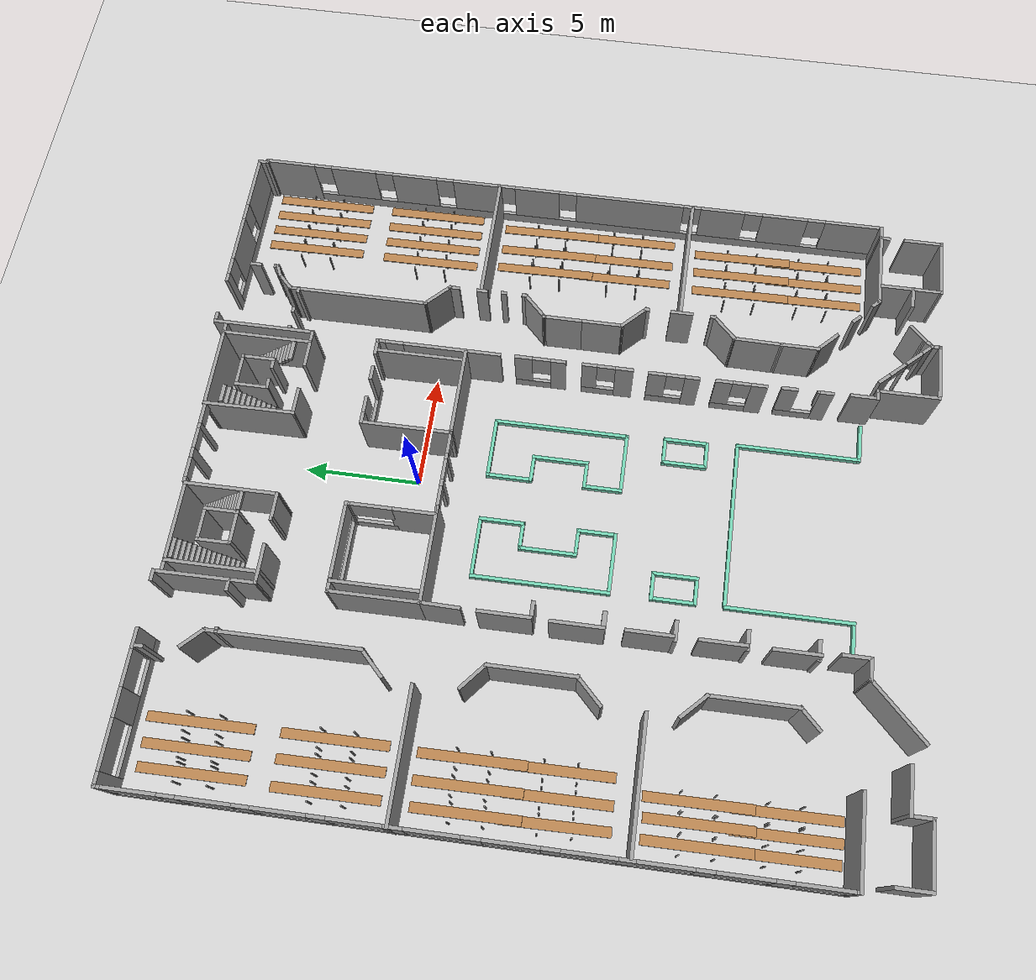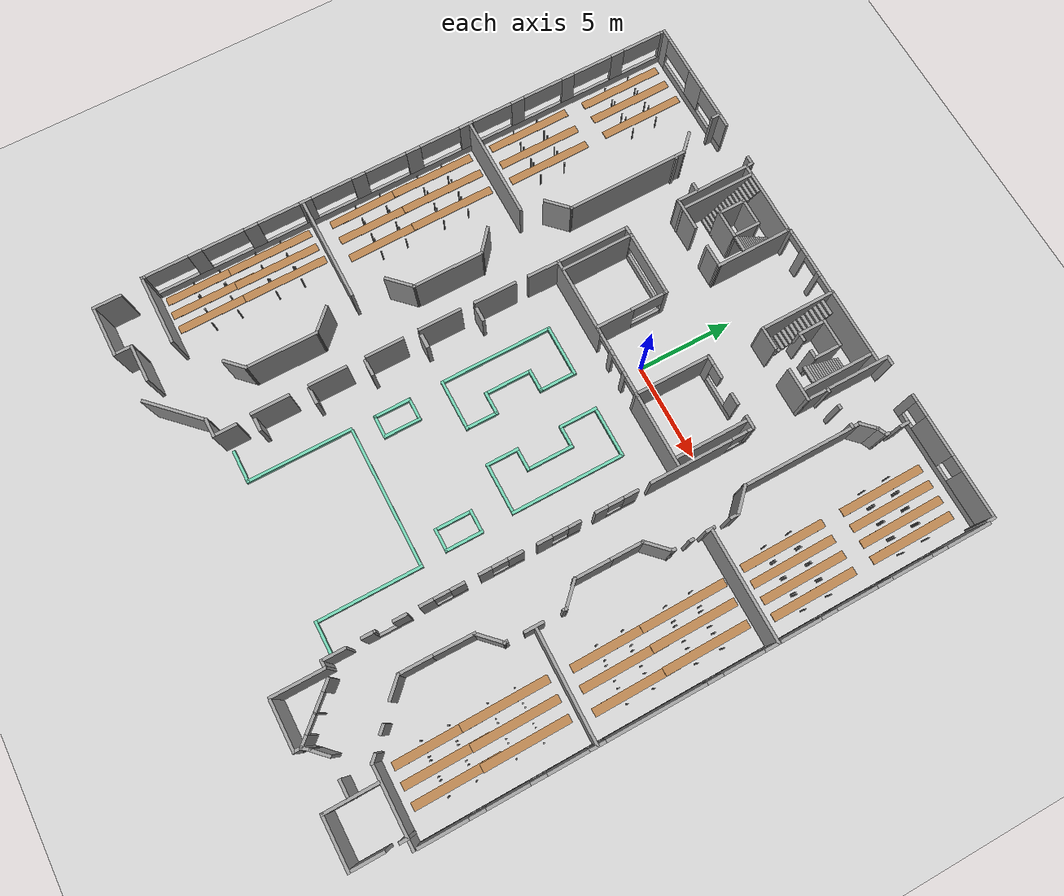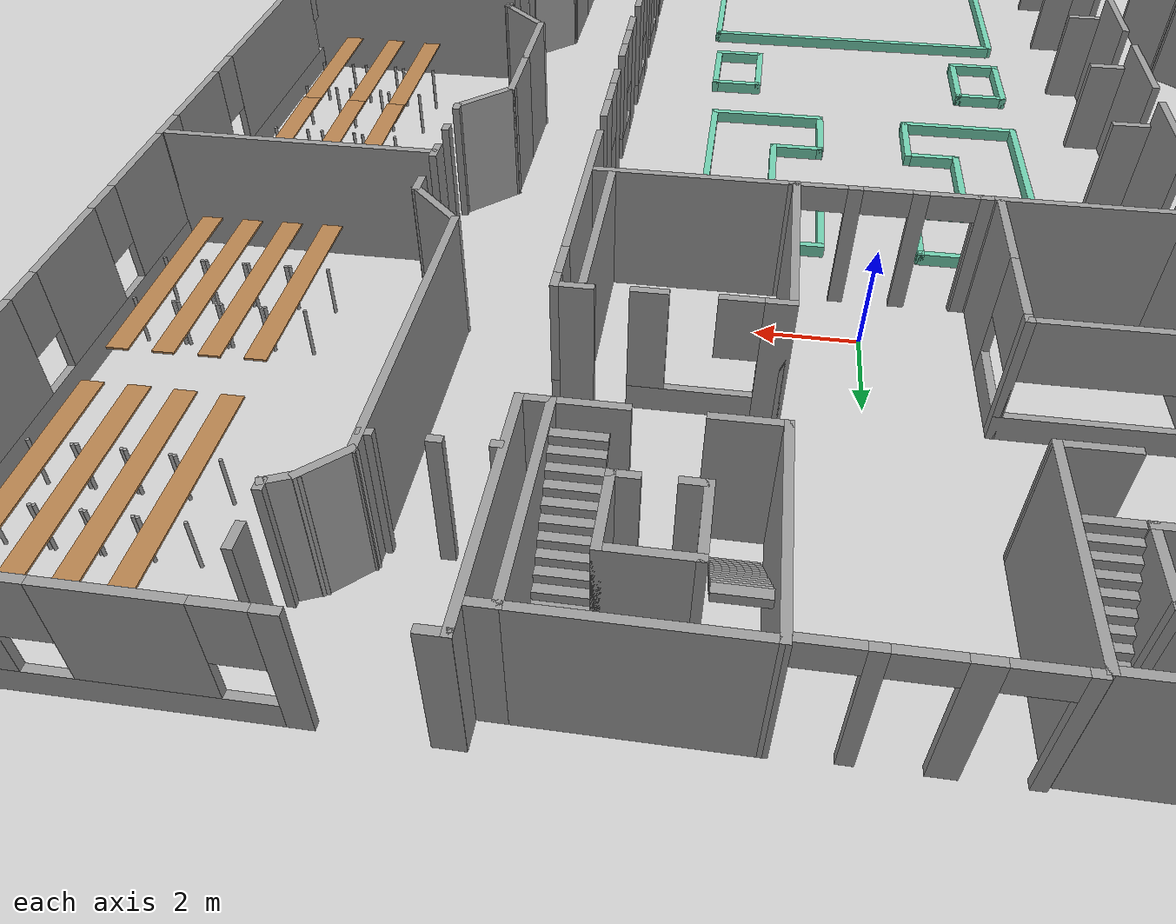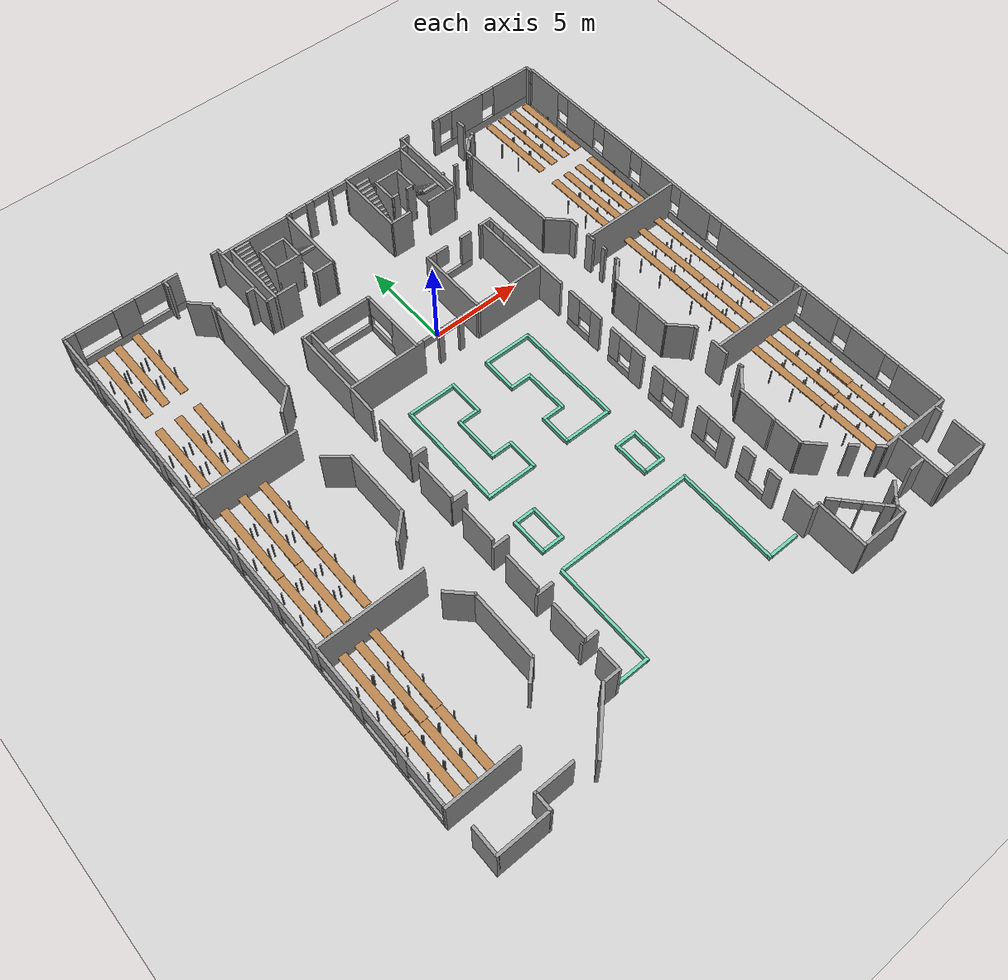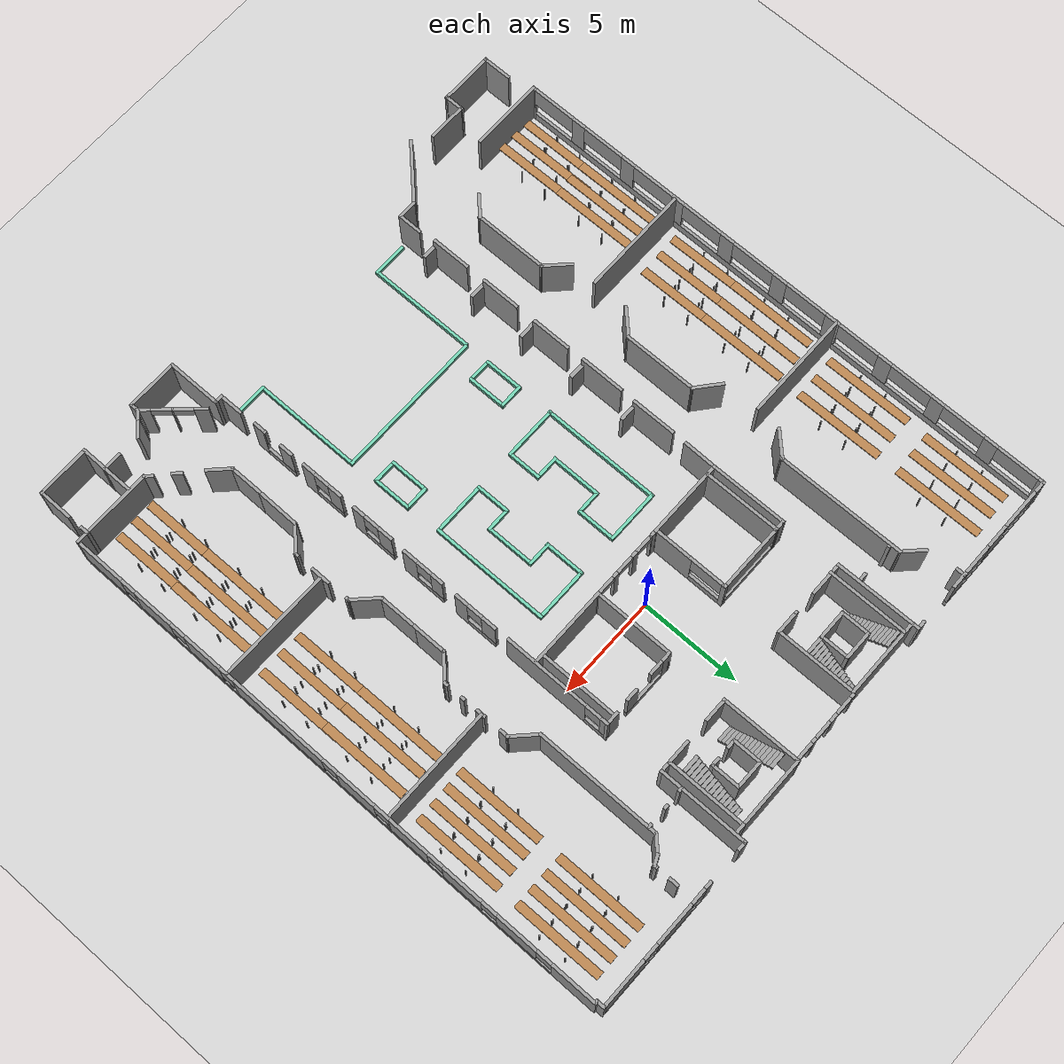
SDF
<sdf version="1.6">
 <world name="default">
  <light name="sun" type="directional">
   <pose>0 0 10 0 -0 0</pose>
   <diffuse>0.8 0.8 0.8 1</diffuse>
   <specular>0.1 0.1 0.1 1</specular>
   <attenuation>
    <range>1000</range>
    <constant>0.9</constant>
    <linear>0.01</linear>
    <quadratic>0.001</quadratic>
   </attenuation>
   <direction>-0.5 0.5 -1</direction>
  </light>
  <model name="ground_plane">
   <static>1</static>
   <link name="link">
    <collision name="collision">
     <geometry><plane><normal>0 0 1</normal><size>100 100</size></plane></geometry>
     <surface><friction><ode><mu>100</mu><mu2>50</mu2></ode></friction></surface>
    </collision>
    <visual name="visual">
     <cast_shadows>0</cast_shadows>
     <geometry><plane><normal>0 0 1</normal><size>100 100</size></plane></geometry>
     <material>
      <script><uri>file://media/materials/scripts/gazebo.material</uri><name>Gazebo/Grey</name></script>
     </material>
    </visual>
   </link>
  </model>
  <gravity>0 0 -9.8</gravity>
  <magnetic_field>6e-06 2.3e-05 -4.2e-05</magnetic_field>
  <atmosphere type="adiabatic"/>
  <physics name="default_physics" default="0" type="ode">
   <max_step_size>0.001</max_step_size>
   <real_time_factor>1</real_time_factor>
   <real_time_update_rate>1000</real_time_update_rate>
  </physics>
  <scene><ambient>0.4 0.4 0.4 1</ambient><background>0.7 0.7 0.7 1</background><shadows>1</shadows></scene>
  <spherical_coordinates>
   <surface_model>EARTH_WGS84</surface_model>
   <latitude_deg>0</latitude_deg>
   <longitude_deg>0</longitude_deg>
   <elevation>0</elevation>
   <heading_deg>0</heading_deg>
  </spherical_coordinates>
  <model name="Parte_DX_(visione_alta_mappa)_CV1">
   <pose>7.84951 -6.02799 0 0 -0 0</pose>
   <link name="Stairs_0">
    <visual name="Stairs_0_Visual_0">
     <pose>-5.77033 12.1776 0.083333 0 -0 -3.14159</pose>
     <geometry><box><size>0.790783 0.17667 0.166667</size></box></geometry>
     <material>
      <script><uri>file://media/materials/scripts/gazebo.material</uri><name>Gazebo/Grey</name></script>
      <ambient>1 1 1 1</ambient>
     </material>
    </visual>
    <collision name="Stairs_0_Collision_0">
     <geometry><box><size>0.790783 0.17667 0.166667</size></box></geometry>
     <pose>-5.77033 12.1776 0.083333 0 -0 -3.14159</pose>
    </collision>
    <visual name="Stairs_0_Visual_1">
     <pose>-5.77033 12.3543 0.25 0 -0 -3.14159</pose>
     <geometry><box><size>0.790783 0.17667 0.166667</size></box></geometry>
     <material>
      <script><uri>file://media/materials/scripts/gazebo.material</uri><name>Gazebo/Grey</name></script>
      <ambient>1 1 1 1</ambient>
     </material>
    </visual>
    <collision name="Stairs_0_Collision_1">
     <geometry><box><size>0.790783 0.17667 0.166667</size></box></geometry>
     <pose>-5.77033 12.3543 0.25 0 -0 -3.14159</pose>
    </collision>
    <visual name="Stairs_0_Visual_2">
     <pose>-5.77033 12.531 0.416667 0 -0 -3.14159</pose>
     <geometry><box><size>0.790783 0.17667 0.166667</size></box></geometry>
     <material>
      <script><uri>file://media/materials/scripts/gazebo.material</uri><name>Gazebo/Grey</name></script>
      <ambient>1 1 1 1</ambient>
     </material>
    </visual>
    <collision name="Stairs_0_Collision_2">
     <geometry><box><size>0.790783 0.17667 0.166667</size></box></geometry>
     <pose>-5.77033 12.531 0.416667 0 -0 -3.14159</pose>
    </collision>
    <visual name="Stairs_0_Visual_3">
     <pose>-5.77033 12.7077 0.583333 0 -0 -3.14159</pose>
     <geometry><box><size>0.790783 0.17667 0.166667</size></box></geometry>
     <material>
      <script><uri>file://media/materials/scripts/gazebo.material</uri><name>Gazebo/Grey</name></script>
      <ambient>1 1 1 1</ambient>
     </material>
    </visual>
    <collision name="Stairs_0_Collision_3">
     <geometry><box><size>0.790783 0.17667 0.166667</size></box></geometry>
     <pose>-5.77033 12.7077 0.583333 0 -0 -3.14159</pose>
    </collision>
    <visual name="Stairs_0_Visual_4">
     <pose>-5.77033 12.8843 0.75 0 -0 -3.14159</pose>
     <geometry><box><size>0.790783 0.17667 0.166667</size></box></geometry>
     <material>
      <script><uri>file://media/materials/scripts/gazebo.material</uri><name>Gazebo/Grey</name></script>
      <ambient>1 1 1 1</ambient>
     </material>
    </visual>
    <collision name="Stairs_0_Collision_4">
     <geometry><box><size>0.790783 0.17667 0.166667</size></box></geometry>
     <pose>-5.77033 12.8843 0.75 0 -0 -3.14159</pose>
    </collision>
    <visual name="Stairs_0_Visual_5">
     <pose>-5.77033 13.061 0.916667 0 -0 -3.14159</pose>
     <geometry><box><size>0.790783 0.17667 0.166667</size></box></geometry>
     <material>
      <script><uri>file://media/materials/scripts/gazebo.material</uri><name>Gazebo/Grey</name></script>
      <ambient>1 1 1 1</ambient>
     </material>
    </visual>
    <collision name="Stairs_0_Collision_5">
     <geometry><box><size>0.790783 0.17667 0.166667</size></box></geometry>
     <pose>-5.77033 13.061 0.916667 0 -0 -3.14159</pose>
    </collision>
    <visual name="Stairs_0_Visual_6">
     <pose>-5.77033 13.2377 1.08333 0 -0 -3.14159</pose>
     <geometry><box><size>0.790783 0.17667 0.166667</size></box></geometry>
     <material>
      <script><uri>file://media/materials/scripts/gazebo.material</uri><name>Gazebo/Grey</name></script>
      <ambient>1 1 1 1</ambient>
     </material>
    </visual>
    <collision name="Stairs_0_Collision_6">
     <geometry><box><size>0.790783 0.17667 0.166667</size></box></geometry>
     <pose>-5.77033 13.2377 1.08333 0 -0 -3.14159</pose>
    </collision>
    <visual name="Stairs_0_Visual_7">
     <pose>-5.77033 13.4143 1.25 0 -0 -3.14159</pose>
     <geometry><box><size>0.790783 0.17667 0.166667</size></box></geometry>
     <material>
      <script><uri>file://media/materials/scripts/gazebo.material</uri><name>Gazebo/Grey</name></script>
      <ambient>1 1 1 1</ambient>
     </material>
    </visual>
    <collision name="Stairs_0_Collision_7">
     <geometry><box><size>0.790783 0.17667 0.166667</size></box></geometry>
     <pose>-5.77033 13.4143 1.25 0 -0 -3.14159</pose>
    </collision>
    <visual name="Stairs_0_Visual_8">
     <pose>-5.77033 13.591 1.41667 0 -0 -3.14159</pose>
     <geometry><box><size>0.790783 0.17667 0.166667</size></box></geometry>
     <material>
      <script><uri>file://media/materials/scripts/gazebo.material</uri><name>Gazebo/Grey</name></script>
      <ambient>1 1 1 1</ambient>
     </material>
    </visual>
    <collision name="Stairs_0_Collision_8">
     <geometry><box><size>0.790783 0.17667 0.166667</size></box></geometry>
     <pose>-5.77033 13.591 1.41667 0 -0 -3.14159</pose>
    </collision>
    <visual name="Stairs_0_Visual_9">
     <pose>-5.77033 13.7677 1.58333 0 -0 -3.14159</pose>
     <geometry><box><size>0.790783 0.17667 0.166667</size></box></geometry>
     <material>
      <script><uri>file://media/materials/scripts/gazebo.material</uri><name>Gazebo/Grey</name></script>
      <ambient>1 1 1 1</ambient>
     </material>
    </visual>
    <collision name="Stairs_0_Collision_9">
     <geometry><box><size>0.790783 0.17667 0.166667</size></box></geometry>
     <pose>-5.77033 13.7677 1.58333 0 -0 -3.14159</pose>
    </collision>
    <visual name="Stairs_0_Visual_10">
     <pose>-5.77033 13.9443 1.75 0 -0 -3.14159</pose>
     <geometry><box><size>0.790783 0.17667 0.166667</size></box></geometry>
     <material>
      <script><uri>file://media/materials/scripts/gazebo.material</uri><name>Gazebo/Grey</name></script>
      <ambient>1 1 1 1</ambient>
     </material>
    </visual>
    <collision name="Stairs_0_Collision_10">
     <geometry><box><size>0.790783 0.17667 0.166667</size></box></geometry>
     <pose>-5.77033 13.9443 1.75 0 -0 -3.14159</pose>
    </collision>
    <visual name="Stairs_0_Visual_11">
     <pose>-5.77033 14.121 1.91667 0 -0 -3.14159</pose>
     <geometry><box><size>0.790783 0.17667 0.166667</size></box></geometry>
     <material>
      <script><uri>file://media/materials/scripts/gazebo.material</uri><name>Gazebo/Grey</name></script>
      <ambient>1 1 1 1</ambient>
     </material>
    </visual>
    <collision name="Stairs_0_Collision_11">
     <geometry><box><size>0.790783 0.17667 0.166667</size></box></geometry>
     <pose>-5.77033 14.121 1.91667 0 -0 -3.14159</pose>
    </collision>
    <visual name="Stairs_0_Visual_12">
     <pose>-5.77033 14.2977 2.08333 0 -0 -3.14159</pose>
     <geometry><box><size>0.790783 0.17667 0.166667</size></box></geometry>
     <material>
      <script><uri>file://media/materials/scripts/gazebo.material</uri><name>Gazebo/Grey</name></script>
      <ambient>1 1 1 1</ambient>
     </material>
    </visual>
    <collision name="Stairs_0_Collision_12">
     <geometry><box><size>0.790783 0.17667 0.166667</size></box></geometry>
     <pose>-5.77033 14.2977 2.08333 0 -0 -3.14159</pose>
    </collision>
    <visual name="Stairs_0_Visual_13">
     <pose>-5.77033 14.4744 2.25 0 -0 -3.14159</pose>
     <geometry><box><size>0.790783 0.17667 0.166667</size></box></geometry>
     <material>
      <script><uri>file://media/materials/scripts/gazebo.material</uri><name>Gazebo/Grey</name></script>
      <ambient>1 1 1 1</ambient>
     </material>
    </visual>
    <collision name="Stairs_0_Collision_13">
     <geometry><box><size>0.790783 0.17667 0.166667</size></box></geometry>
     <pose>-5.77033 14.4744 2.25 0 -0 -3.14159</pose>
    </collision>
    <visual name="Stairs_0_Visual_14">
     <pose>-5.77033 14.651 2.41667 0 -0 -3.14159</pose>
     <geometry><box><size>0.790783 0.17667 0.166667</size></box></geometry>
     <material>
      <script><uri>file://media/materials/scripts/gazebo.material</uri><name>Gazebo/Grey</name></script>
      <ambient>1 1 1 1</ambient>
     </material>
    </visual>
    <collision name="Stairs_0_Collision_14">
     <geometry><box><size>0.790783 0.17667 0.166667</size></box></geometry>
     <pose>-5.77033 14.651 2.41667 0 -0 -3.14159</pose>
    </collision>
   </link>
   <link name="Stairs_1">
    <visual name="Stairs_1_Visual_0">
     <pose>-3.36416 14.6621 0.083333 0 -0 0</pose>
     <geometry><box><size>0.856163 0.179286 0.166667</size></box></geometry>
     <material>
      <script><uri>file://media/materials/scripts/gazebo.material</uri><name>Gazebo/Grey</name></script>
      <ambient>1 1 1 1</ambient>
     </material>
    </visual>
    <collision name="Stairs_1_Collision_0">
     <geometry><box><size>0.856163 0.179286 0.166667</size></box></geometry>
     <pose>-3.36416 14.6621 0.083333 0 -0 0</pose>
    </collision>
    <visual name="Stairs_1_Visual_1">
     <pose>-3.36416 14.4828 0.25 0 -0 0</pose>
     <geometry><box><size>0.856163 0.179286 0.166667</size></box></geometry>
     <material>
      <script><uri>file://media/materials/scripts/gazebo.material</uri><name>Gazebo/Grey</name></script>
      <ambient>1 1 1 1</ambient>
     </material>
    </visual>
    <collision name="Stairs_1_Collision_1">
     <geometry><box><size>0.856163 0.179286 0.166667</size></box></geometry>
     <pose>-3.36416 14.4828 0.25 0 -0 0</pose>
    </collision>
    <visual name="Stairs_1_Visual_2">
     <pose>-3.36416 14.3035 0.416667 0 -0 0</pose>
     <geometry><box><size>0.856163 0.179286 0.166667</size></box></geometry>
     <material>
      <script><uri>file://media/materials/scripts/gazebo.material</uri><name>Gazebo/Grey</name></script>
      <ambient>1 1 1 1</ambient>
     </material>
    </visual>
    <collision name="Stairs_1_Collision_2">
     <geometry><box><size>0.856163 0.179286 0.166667</size></box></geometry>
     <pose>-3.36416 14.3035 0.416667 0 -0 0</pose>
    </collision>
    <visual name="Stairs_1_Visual_3">
     <pose>-3.36416 14.1242 0.583333 0 -0 0</pose>
     <geometry><box><size>0.856163 0.179286 0.166667</size></box></geometry>
     <material>
      <script><uri>file://media/materials/scripts/gazebo.material</uri><name>Gazebo/Grey</name></script>
      <ambient>1 1 1 1</ambient>
     </material>
    </visual>
    <collision name="Stairs_1_Collision_3">
     <geometry><box><size>0.856163 0.179286 0.166667</size></box></geometry>
     <pose>-3.36416 14.1242 0.583333 0 -0 0</pose>
    </collision>
    <visual name="Stairs_1_Visual_4">
     <pose>-3.36416 13.9449 0.75 0 -0 0</pose>
     <geometry><box><size>0.856163 0.179286 0.166667</size></box></geometry>
     <material>
      <script><uri>file://media/materials/scripts/gazebo.material</uri><name>Gazebo/Grey</name></script>
      <ambient>1 1 1 1</ambient>
     </material>
    </visual>
    <collision name="Stairs_1_Collision_4">
     <geometry><box><size>0.856163 0.179286 0.166667</size></box></geometry>
     <pose>-3.36416 13.9449 0.75 0 -0 0</pose>
    </collision>
    <visual name="Stairs_1_Visual_5">
     <pose>-3.36416 13.7656 0.916667 0 -0 0</pose>
     <geometry><box><size>0.856163 0.179286 0.166667</size></box></geometry>
     <material>
      <script><uri>file://media/materials/scripts/gazebo.material</uri><name>Gazebo/Grey</name></script>
      <ambient>1 1 1 1</ambient>
     </material>
    </visual>
    <collision name="Stairs_1_Collision_5">
     <geometry><box><size>0.856163 0.179286 0.166667</size></box></geometry>
     <pose>-3.36416 13.7656 0.916667 0 -0 0</pose>
    </collision>
    <visual name="Stairs_1_Visual_6">
     <pose>-3.36416 13.5863 1.08333 0 -0 0</pose>
     <geometry><box><size>0.856163 0.179286 0.166667</size></box></geometry>
     <material>
      <script><uri>file://media/materials/scripts/gazebo.material</uri><name>Gazebo/Grey</name></script>
      <ambient>1 1 1 1</ambient>
     </material>
    </visual>
    <collision name="Stairs_1_Collision_6">
     <geometry><box><size>0.856163 0.179286 0.166667</size></box></geometry>
     <pose>-3.36416 13.5863 1.08333 0 -0 0</pose>
    </collision>
    <visual name="Stairs_1_Visual_7">
     <pose>-3.36416 13.4071 1.25 0 -0 0</pose>
     <geometry><box><size>0.856163 0.179286 0.166667</size></box></geometry>
     <material>
      <script><uri>file://media/materials/scripts/gazebo.material</uri><name>Gazebo/Grey</name></script>
      <ambient>1 1 1 1</ambient>
     </material>
    </visual>
    <collision name="Stairs_1_Collision_7">
     <geometry><box><size>0.856163 0.179286 0.166667</size></box></geometry>
     <pose>-3.36416 13.4071 1.25 0 -0 0</pose>
    </collision>
    <visual name="Stairs_1_Visual_8">
     <pose>-3.36416 13.2278 1.41667 0 -0 0</pose>
     <geometry><box><size>0.856163 0.179286 0.166667</size></box></geometry>
     <material>
      <script><uri>file://media/materials/scripts/gazebo.material</uri><name>Gazebo/Grey</name></script>
      <ambient>1 1 1 1</ambient>
     </material>
    </visual>
    <collision name="Stairs_1_Collision_8">
     <geometry><box><size>0.856163 0.179286 0.166667</size></box></geometry>
     <pose>-3.36416 13.2278 1.41667 0 -0 0</pose>
    </collision>
    <visual name="Stairs_1_Visual_9">
     <pose>-3.36416 13.0485 1.58333 0 -0 0</pose>
     <geometry><box><size>0.856163 0.179286 0.166667</size></box></geometry>
     <material>
      <script><uri>file://media/materials/scripts/gazebo.material</uri><name>Gazebo/Grey</name></script>
      <ambient>1 1 1 1</ambient>
     </material>
    </visual>
    <collision name="Stairs_1_Collision_9">
     <geometry><box><size>0.856163 0.179286 0.166667</size></box></geometry>
     <pose>-3.36416 13.0485 1.58333 0 -0 0</pose>
    </collision>
    <visual name="Stairs_1_Visual_10">
     <pose>-3.36416 12.8692 1.75 0 -0 0</pose>
     <geometry><box><size>0.856163 0.179286 0.166667</size></box></geometry>
     <material>
      <script><uri>file://media/materials/scripts/gazebo.material</uri><name>Gazebo/Grey</name></script>
      <ambient>1 1 1 1</ambient>
     </material>
    </visual>
    <collision name="Stairs_1_Collision_10">
     <geometry><box><size>0.856163 0.179286 0.166667</size></box></geometry>
     <pose>-3.36416 12.8692 1.75 0 -0 0</pose>
    </collision>
    <visual name="Stairs_1_Visual_11">
     <pose>-3.36416 12.6899 1.91667 0 -0 0</pose>
     <geometry><box><size>0.856163 0.179286 0.166667</size></box></geometry>
     <material>
      <script><uri>file://media/materials/scripts/gazebo.material</uri><name>Gazebo/Grey</name></script>
      <ambient>1 1 1 1</ambient>
     </material>
    </visual>
    <collision name="Stairs_1_Collision_11">
     <geometry><box><size>0.856163 0.179286 0.166667</size></box></geometry>
     <pose>-3.36416 12.6899 1.91667 0 -0 0</pose>
    </collision>
    <visual name="Stairs_1_Visual_12">
     <pose>-3.36416 12.5106 2.08333 0 -0 0</pose>
     <geometry><box><size>0.856163 0.179286 0.166667</size></box></geometry>
     <material>
      <script><uri>file://media/materials/scripts/gazebo.material</uri><name>Gazebo/Grey</name></script>
      <ambient>1 1 1 1</ambient>
     </material>
    </visual>
    <collision name="Stairs_1_Collision_12">
     <geometry><box><size>0.856163 0.179286 0.166667</size></box></geometry>
     <pose>-3.36416 12.5106 2.08333 0 -0 0</pose>
    </collision>
    <visual name="Stairs_1_Visual_13">
     <pose>-3.36416 12.3313 2.25 0 -0 0</pose>
     <geometry><box><size>0.856163 0.179286 0.166667</size></box></geometry>
     <material>
      <script><uri>file://media/materials/scripts/gazebo.material</uri><name>Gazebo/Grey</name></script>
      <ambient>1 1 1 1</ambient>
     </material>
    </visual>
    <collision name="Stairs_1_Collision_13">
     <geometry><box><size>0.856163 0.179286 0.166667</size></box></geometry>
     <pose>-3.36416 12.3313 2.25 0 -0 0</pose>
    </collision>
    <visual name="Stairs_1_Visual_14">
     <pose>-3.36416 12.1521 2.41667 0 -0 0</pose>
     <geometry><box><size>0.856163 0.179286 0.166667</size></box></geometry>
     <material>
      <script><uri>file://media/materials/scripts/gazebo.material</uri><name>Gazebo/Grey</name></script>
      <ambient>1 1 1 1</ambient>
     </material>
    </visual>
    <collision name="Stairs_1_Collision_14">
     <geometry><box><size>0.856163 0.179286 0.166667</size></box></geometry>
     <pose>-3.36416 12.1521 2.41667 0 -0 0</pose>
    </collision>
   </link>
   <link name="Wall_0">
    <collision name="Wall_0_Collision">
     <geometry><box><size>3.5 0.15 2.5</size></box></geometry>
     <pose>0 0 1.25 0 -0 0</pose>
    </collision>
    <visual name="Wall_0_Visual">
     <pose>0 0 1.25 0 -0 0</pose>
     <geometry><box><size>3.5 0.15 2.5</size></box></geometry>
     <material>
      <script><uri>file://media/materials/scripts/gazebo.material</uri><name>Gazebo/Grey</name></script>
      <ambient>1 1 1 1</ambient>
     </material>
    </visual>
    <pose>-4.6353 15.3082 0 0 -0 0</pose>
   </link>
   <link name="Wall_101">
    <collision name="Wall_101_Collision">
     <geometry><box><size>1.75 0.15 2.5</size></box></geometry>
     <pose>0 0 1.25 0 -0 0</pose>
    </collision>
    <visual name="Wall_101_Visual">
     <pose>0 0 1.25 0 -0 0</pose>
     <geometry><box><size>1.75 0.15 2.5</size></box></geometry>
     <material>
      <script><uri>file://media/materials/scripts/gazebo.material</uri><name>Gazebo/Grey</name></script>
      <ambient>1 1 1 1</ambient>
     </material>
    </visual>
    <pose>-0.253384 0.713118 0 0 0 -1.5708</pose>
   </link>
   <link name="Wall_103">
    <collision name="Wall_103_Collision">
     <geometry><box><size>2 0.15 2.5</size></box></geometry>
     <pose>0 0 1.25 0 -0 0</pose>
    </collision>
    <visual name="Wall_103_Visual">
     <pose>0 0 1.25 0 -0 0</pose>
     <geometry><box><size>2 0.15 2.5</size></box></geometry>
     <material>
      <script><uri>file://media/materials/scripts/gazebo.material</uri><name>Gazebo/Grey</name></script>
      <ambient>1 1 1 1</ambient>
     </material>
    </visual>
    <pose>-0.253384 -1.01188 0 0 0 -1.5708</pose>
   </link>
   <link name="Wall_105">
    <collision name="Wall_105_Collision">
     <geometry><box><size>1.5 0.15 2.5</size></box></geometry>
     <pose>0 0 1.25 0 -0 0</pose>
    </collision>
    <visual name="Wall_105_Visual">
     <pose>0 0 1.25 0 -0 0</pose>
     <geometry><box><size>1.5 0.15 2.5</size></box></geometry>
     <material>
      <script><uri>file://media/materials/scripts/gazebo.material</uri><name>Gazebo/Grey</name></script>
      <ambient>1 1 1 1</ambient>
     </material>
    </visual>
    <pose>0.223913 -2.41418 0 0 0 -0.785398</pose>
   </link>
   <link name="Wall_106">
    <collision name="Wall_106_Collision">
     <geometry><box><size>0.25 0.15 2.5</size></box></geometry>
     <pose>0 0 1.25 0 -0 0</pose>
    </collision>
    <visual name="Wall_106_Visual">
     <pose>0 0 1.25 0 -0 0</pose>
     <geometry><box><size>0.25 0.15 2.5</size></box></geometry>
     <material>
      <script><uri>file://media/materials/scripts/gazebo.material</uri><name>Gazebo/Grey</name></script>
      <ambient>1 1 1 1</ambient>
     </material>
    </visual>
    <pose>0.70121 -2.94148 0 0 0 -1.5708</pose>
   </link>
   <link name="Wall_108">
    <collision name="Wall_108_Collision">
     <geometry><box><size>1 0.15 2.5</size></box></geometry>
     <pose>0 0 1.25 0 -0 0</pose>
    </collision>
    <visual name="Wall_108_Visual">
     <pose>0 0 1.25 0 -0 0</pose>
     <geometry><box><size>1 0.15 2.5</size></box></geometry>
     <material>
      <script><uri>file://media/materials/scripts/gazebo.material</uri><name>Gazebo/Grey</name></script>
      <ambient>1 1 1 1</ambient>
     </material>
    </visual>
    <pose>0.723822 -4.48667 0 0 0 -1.5708</pose>
   </link>
   <link name="Wall_110">
    <collision name="Wall_110_Collision">
     <geometry><box><size>0.25 0.15 2.5</size></box></geometry>
     <pose>0 0 1.25 0 -0 0</pose>
    </collision>
    <visual name="Wall_110_Visual">
     <pose>0 0 1.25 0 -0 0</pose>
     <geometry><box><size>0.25 0.15 2.5</size></box></geometry>
     <material>
      <script><uri>file://media/materials/scripts/gazebo.material</uri><name>Gazebo/Grey</name></script>
      <ambient>1 1 1 1</ambient>
     </material>
    </visual>
    <pose>0.706863 -5.87545 0 0 0 -1.5708</pose>
   </link>
   <link name="Wall_111">
    <collision name="Wall_111_Collision">
     <geometry><box><size>1.5 0.15 2.5</size></box></geometry>
     <pose>0 0 1.25 0 -0 0</pose>
    </collision>
    <visual name="Wall_111_Visual">
     <pose>0 0 1.25 0 -0 0</pose>
     <geometry><box><size>1.5 0.15 2.5</size></box></geometry>
     <material>
      <script><uri>file://media/materials/scripts/gazebo.material</uri><name>Gazebo/Grey</name></script>
      <ambient>1 1 1 1</ambient>
     </material>
    </visual>
    <pose>0.229566 -6.40275 0 0 0 -2.35619</pose>
   </link>
   <link name="Wall_113">
    <collision name="Wall_113_Collision">
     <geometry><box><size>2.21308 0.15 2.5</size></box></geometry>
     <pose>0 0 1.25 0 -0 0</pose>
    </collision>
    <visual name="Wall_113_Visual">
     <pose>0 0 1.25 0 -0 0</pose>
     <geometry><box><size>2.21308 0.15 2.5</size></box></geometry>
     <material>
      <script><uri>file://media/materials/scripts/gazebo.material</uri><name>Gazebo/Grey</name></script>
      <ambient>1 1 1 1</ambient>
     </material>
    </visual>
    <pose>-0.262289 -7.91149 0 0 0 -1.58491</pose>
   </link>
   <link name="Wall_117">
    <collision name="Wall_117_Collision">
     <geometry><box><size>0.15 0.15 2.5</size></box></geometry>
     <pose>0 0 1.25 0 -0 0</pose>
    </collision>
    <visual name="Wall_117_Visual">
     <pose>0 0 1.25 0 -0 0</pose>
     <geometry><box><size>0.15 0.15 2.5</size></box></geometry>
     <material>
      <script><uri>file://media/materials/scripts/gazebo.material</uri><name>Gazebo/Grey</name></script>
      <ambient>1 1 1 1</ambient>
     </material>
    </visual>
    <pose>-0.253384 1.51312 0 0 -0 0</pose>
   </link>
   <link name="Wall_119">
    <collision name="Wall_119_Collision">
     <geometry><box><size>0.25 0.15 2.5</size></box></geometry>
     <pose>0 0 1.25 0 -0 0</pose>
    </collision>
    <visual name="Wall_119_Visual">
     <pose>0 0 1.25 0 -0 0</pose>
     <geometry><box><size>0.25 0.15 2.5</size></box></geometry>
     <material>
      <script><uri>file://media/materials/scripts/gazebo.material</uri><name>Gazebo/Grey</name></script>
      <ambient>1 1 1 1</ambient>
     </material>
    </visual>
    <pose>0.70121 2.51771 0 0 -0 1.5708</pose>
   </link>
   <link name="Wall_123">
    <collision name="Wall_123_Collision">
     <geometry><box><size>1.5 0.15 2.5</size></box></geometry>
     <pose>0 0 1.25 0 -0 0</pose>
    </collision>
    <visual name="Wall_123_Visual">
     <pose>0 0 1.25 0 -0 0</pose>
     <geometry><box><size>1.5 0.15 2.5</size></box></geometry>
     <material>
      <script><uri>file://media/materials/scripts/gazebo.material</uri><name>Gazebo/Grey</name></script>
      <ambient>1 1 1 1</ambient>
     </material>
    </visual>
    <pose>0.223913 1.99042 0 0 -0 0.785398</pose>
   </link>
   <link name="Wall_125">
    <collision name="Wall_125_Collision">
     <geometry><box><size>0.25 0.15 2.5</size></box></geometry>
     <pose>0 0 1.25 0 -0 0</pose>
    </collision>
    <visual name="Wall_125_Visual">
     <pose>0 0 1.25 0 -0 0</pose>
     <geometry><box><size>0.25 0.15 2.5</size></box></geometry>
     <material>
      <script><uri>file://media/materials/scripts/gazebo.material</uri><name>Gazebo/Grey</name></script>
      <ambient>1 1 1 1</ambient>
     </material>
    </visual>
    <pose>0.700925 3.44587 0 0 0 -1.5708</pose>
   </link>
   <link name="Wall_127">
    <collision name="Wall_127_Collision">
     <geometry><box><size>0.5 0.15 2.5</size></box></geometry>
     <pose>0 0 1.25 0 -0 0</pose>
    </collision>
    <visual name="Wall_127_Visual">
     <pose>0 0 1.25 0 -0 0</pose>
     <geometry><box><size>0.5 0.15 2.5</size></box></geometry>
     <material>
      <script><uri>file://media/materials/scripts/gazebo.material</uri><name>Gazebo/Grey</name></script>
      <ambient>1 1 1 1</ambient>
     </material>
    </visual>
    <pose>0.681262 4.41709 0 0 0 -1.5708</pose>
   </link>
   <link name="Wall_130">
    <collision name="Wall_130_Collision">
     <geometry><box><size>5.75 0.15 2.5</size></box></geometry>
     <pose>0 0 1.25 0 -0 0</pose>
    </collision>
    <visual name="Wall_130_Visual">
     <pose>0 0 1.25 0 -0 0</pose>
     <geometry><box><size>5.75 0.15 2.5</size></box></geometry>
     <material>
      <script><uri>file://media/materials/scripts/gazebo.material</uri><name>Gazebo/Grey</name></script>
      <ambient>1 1 1 1</ambient>
     </material>
    </visual>
    <pose>3.51474 4.4692 0 0 -0 3.14159</pose>
   </link>
   <link name="Wall_132">
    <collision name="Wall_132_Collision">
     <geometry><box><size>0.25 0.15 2.5</size></box></geometry>
     <pose>0 0 1.25 0 -0 0</pose>
    </collision>
    <visual name="Wall_132_Visual">
     <pose>0 0 1.25 0 -0 0</pose>
     <geometry><box><size>0.25 0.15 2.5</size></box></geometry>
     <material>
      <script><uri>file://media/materials/scripts/gazebo.material</uri><name>Gazebo/Grey</name></script>
      <ambient>1 1 1 1</ambient>
     </material>
    </visual>
    <pose>-1.36627 12.5347 0 0 -0 0</pose>
   </link>
   <link name="Wall_134">
    <collision name="Wall_134_Collision">
     <geometry><box><size>0.25 0.15 2.5</size></box></geometry>
     <pose>0 0 1.25 0 -0 0</pose>
    </collision>
    <visual name="Wall_134_Visual">
     <pose>0 0 1.25 0 -0 0</pose>
     <geometry><box><size>0.25 0.15 2.5</size></box></geometry>
     <material>
      <script><uri>file://media/materials/scripts/gazebo.material</uri><name>Gazebo/Grey</name></script>
      <ambient>1 1 1 1</ambient>
     </material>
    </visual>
    <pose>-0.351158 12.5347 0 0 -0 3.14159</pose>
   </link>
   <link name="Wall_136">
    <collision name="Wall_136_Collision">
     <geometry><box><size>0.25 0.15 2.5</size></box></geometry>
     <pose>0 0 1.25 0 -0 0</pose>
    </collision>
    <visual name="Wall_136_Visual">
     <pose>0 0 1.25 0 -0 0</pose>
     <geometry><box><size>0.25 0.15 2.5</size></box></geometry>
     <material>
      <script><uri>file://media/materials/scripts/gazebo.material</uri><name>Gazebo/Grey</name></script>
      <ambient>1 1 1 1</ambient>
     </material>
    </visual>
    <pose>-2.28438 12.5087 0 0 -0 0</pose>
   </link>
   <link name="Wall_138">
    <collision name="Wall_138_Collision">
     <geometry><box><size>0.5 0.15 2.5</size></box></geometry>
     <pose>0 0 1.25 0 -0 0</pose>
    </collision>
    <visual name="Wall_138_Visual">
     <pose>0 0 1.25 0 -0 0</pose>
     <geometry><box><size>0.5 0.15 2.5</size></box></geometry>
     <material>
      <script><uri>file://media/materials/scripts/gazebo.material</uri><name>Gazebo/Grey</name></script>
      <ambient>1 1 1 1</ambient>
     </material>
    </visual>
    <pose>5.78705 -13.262 0 0 0 -1.5708</pose>
   </link>
   <link name="Wall_140">
    <collision name="Wall_140_Collision">
     <geometry><box><size>1.75 0.15 2.5</size></box></geometry>
     <pose>0 0 1.25 0 -0 0</pose>
    </collision>
    <visual name="Wall_140_Visual">
     <pose>0 0 1.25 0 -0 0</pose>
     <geometry><box><size>1.75 0.15 2.5</size></box></geometry>
     <material>
      <script><uri>file://media/materials/scripts/gazebo.material</uri><name>Gazebo/Grey</name></script>
      <ambient>1 1 1 1</ambient>
     </material>
    </visual>
    <pose>5.79565 -14.9955 0 0 0 -1.5708</pose>
   </link>
   <link name="Wall_142">
    <collision name="Wall_142_Collision">
     <geometry><box><size>2.75 0.15 2.5</size></box></geometry>
     <pose>0 0 1.25 0 -0 0</pose>
    </collision>
    <visual name="Wall_142_Visual">
     <pose>0 0 1.25 0 -0 0</pose>
     <geometry><box><size>2.75 0.15 2.5</size></box></geometry>
     <material>
      <script><uri>file://media/materials/scripts/gazebo.material</uri><name>Gazebo/Grey</name></script>
      <ambient>1 1 1 1</ambient>
     </material>
    </visual>
    <pose>3.27651 -14.5074 0 0 0 -1.5708</pose>
   </link>
   <link name="Wall_143">
    <collision name="Wall_143_Collision">
     <geometry><box><size>2.66916 0.15 2.5</size></box></geometry>
     <pose>0 0 1.25 0 -0 0</pose>
    </collision>
    <visual name="Wall_143_Visual">
     <pose>0 0 1.25 0 -0 0</pose>
     <geometry><box><size>2.66916 0.15 2.5</size></box></geometry>
     <material>
      <script><uri>file://media/materials/scripts/gazebo.material</uri><name>Gazebo/Grey</name></script>
      <ambient>1 1 1 1</ambient>
     </material>
    </visual>
    <pose>4.53608 -15.8014 0 0 -0 0.004735</pose>
   </link>
   <link name="Wall_145">
    <collision name="Wall_145_Collision">
     <geometry><box><size>1 0.15 2.5</size></box></geometry>
     <pose>0 0 1.25 0 -0 0</pose>
    </collision>
    <visual name="Wall_145_Visual">
     <pose>0 0 1.25 0 -0 0</pose>
     <geometry><box><size>1 0.15 2.5</size></box></geometry>
     <material>
      <script><uri>file://media/materials/scripts/gazebo.material</uri><name>Gazebo/Grey</name></script>
      <ambient>1 1 1 1</ambient>
     </material>
    </visual>
    <pose>2.86011 -14.5744 0 0 -0 3.14159</pose>
   </link>
   <link name="Wall_147">
    <collision name="Wall_147_Collision">
     <geometry><box><size>1 0.15 2.5</size></box></geometry>
     <pose>0 0 1.25 0 -0 0</pose>
    </collision>
    <visual name="Wall_147_Visual">
     <pose>0 0 1.25 0 -0 0</pose>
     <geometry><box><size>1 0.15 2.5</size></box></geometry>
     <material>
      <script><uri>file://media/materials/scripts/gazebo.material</uri><name>Gazebo/Grey</name></script>
      <ambient>1 1 1 1</ambient>
     </material>
    </visual>
    <pose>1.0501 -14.8406 0 0 0 -2.35619</pose>
   </link>
   <link name="Wall_150">
    <collision name="Wall_150_Collision">
     <geometry><box><size>2.5 0.15 2.5</size></box></geometry>
     <pose>0 0 1.25 0 -0 0</pose>
    </collision>
    <visual name="Wall_150_Visual">
     <pose>0 0 1.25 0 -0 0</pose>
     <geometry><box><size>2.5 0.15 2.5</size></box></geometry>
     <material>
      <script><uri>file://media/materials/scripts/gazebo.material</uri><name>Gazebo/Grey</name></script>
      <ambient>1 1 1 1</ambient>
     </material>
    </visual>
    <pose>-0.698526 -15.7953 0 0 -0 0</pose>
   </link>
   <link name="Wall_151">
    <collision name="Wall_151_Collision">
     <geometry><box><size>0.15 0.15 2.5</size></box></geometry>
     <pose>0 0 1.25 0 -0 0</pose>
    </collision>
    <visual name="Wall_151_Visual">
     <pose>0 0 1.25 0 -0 0</pose>
     <geometry><box><size>0.15 0.15 2.5</size></box></geometry>
     <material>
      <script><uri>file://media/materials/scripts/gazebo.material</uri><name>Gazebo/Grey</name></script>
      <ambient>1 1 1 1</ambient>
     </material>
    </visual>
    <pose>0.485072 -15.7953 0 0 -0 0</pose>
   </link>
   <link name="Wall_154">
    <collision name="Wall_154_Collision">
     <geometry><box><size>0.5 0.15 2.5</size></box></geometry>
     <pose>0 0 1.25 0 -0 0</pose>
    </collision>
    <visual name="Wall_154_Visual">
     <pose>0 0 1.25 0 -0 0</pose>
     <geometry><box><size>0.5 0.15 2.5</size></box></geometry>
     <material>
      <script><uri>file://media/materials/scripts/gazebo.material</uri><name>Gazebo/Grey</name></script>
      <ambient>1 1 1 1</ambient>
     </material>
    </visual>
    <pose>0.485072 -15.6203 0 0 -0 1.5708</pose>
   </link>
   <link name="Wall_155">
    <collision name="Wall_155_Collision">
     <geometry><box><size>0.553138 0.15 2.5</size></box></geometry>
     <pose>0 0 1.25 0 -0 0</pose>
    </collision>
    <visual name="Wall_155_Visual">
     <pose>0 0 1.25 0 -0 0</pose>
     <geometry><box><size>0.553138 0.15 2.5</size></box></geometry>
     <material>
      <script><uri>file://media/materials/scripts/gazebo.material</uri><name>Gazebo/Grey</name></script>
      <ambient>1 1 1 1</ambient>
     </material>
    </visual>
    <pose>0.617326 -15.2932 0 0 -0 0.85512</pose>
   </link>
   <link name="Wall_157">
    <collision name="Wall_157_Collision">
     <geometry><box><size>2.75 0.15 2.5</size></box></geometry>
     <pose>0 0 1.25 0 -0 0</pose>
    </collision>
    <visual name="Wall_157_Visual">
     <pose>0 0 1.25 0 -0 0</pose>
     <geometry><box><size>2.75 0.15 2.5</size></box></geometry>
     <material>
      <script><uri>file://media/materials/scripts/gazebo.material</uri><name>Gazebo/Grey</name></script>
      <ambient>1 1 1 1</ambient>
     </material>
    </visual>
    <pose>-1.9853 -14.4816 0 0 0 -1.5708</pose>
   </link>
   <link name="Wall_160">
    <collision name="Wall_160_Collision">
     <geometry><box><size>0.5 0.15 2.5</size></box></geometry>
     <pose>0 0 1.25 0 -0 0</pose>
    </collision>
    <visual name="Wall_160_Visual">
     <pose>0 0 1.25 0 -0 0</pose>
     <geometry><box><size>0.5 0.15 2.5</size></box></geometry>
     <material>
      <script><uri>file://media/materials/scripts/gazebo.material</uri><name>Gazebo/Grey</name></script>
      <ambient>1 1 1 1</ambient>
     </material>
    </visual>
    <pose>-2.1603 -13.1816 0 0 -0 3.14159</pose>
   </link>
   <link name="Wall_162">
    <collision name="Wall_162_Collision">
     <geometry><box><size>1.25 0.15 2.5</size></box></geometry>
     <pose>0 0 1.25 0 -0 0</pose>
    </collision>
    <visual name="Wall_162_Visual">
     <pose>0 0 1.25 0 -0 0</pose>
     <geometry><box><size>1.25 0.15 2.5</size></box></geometry>
     <material>
      <script><uri>file://media/materials/scripts/gazebo.material</uri><name>Gazebo/Grey</name></script>
      <ambient>1 1 1 1</ambient>
     </material>
    </visual>
    <pose>-2.3378 -12.6298 0 0 0 -1.5708</pose>
   </link>
   <link name="Wall_168">
    <pose>-2.37767 -10.186 0 0 -0 1.5708</pose>
    <visual name="Wall_168_Visual_0">
     <pose>-0.818759 0 1.25 0 -0 0</pose>
     <geometry><box><size>0.612482 0.15 2.5</size></box></geometry>
     <material>
      <script><uri>file://media/materials/scripts/gazebo.material</uri><name>Gazebo/Grey</name></script>
      <ambient>1 1 1 1</ambient>
     </material>
    </visual>
    <collision name="Wall_168_Collision_0">
     <geometry><box><size>0.612482 0.15 2.5</size></box></geometry>
     <pose>-0.818759 0 1.25 0 -0 0</pose>
    </collision>
    <visual name="Wall_168_Visual_1">
     <pose>0.306241 0 0.25 0 -0 0</pose>
     <geometry><box><size>1.63752 0.15 0.5</size></box></geometry>
     <material>
      <script><uri>file://media/materials/scripts/gazebo.material</uri><name>Gazebo/Grey</name></script>
      <ambient>1 1 1 1</ambient>
     </material>
    </visual>
    <collision name="Wall_168_Collision_1">
     <geometry><box><size>1.63752 0.15 0.5</size></box></geometry>
     <pose>0.306241 0 0.25 0 -0 0</pose>
    </collision>
    <visual name="Wall_168_Visual_2">
     <pose>0.760521 0 1.5 0 -0 0</pose>
     <geometry><box><size>0.728959 0.15 2</size></box></geometry>
     <material>
      <script><uri>file://media/materials/scripts/gazebo.material</uri><name>Gazebo/Grey</name></script>
      <ambient>1 1 1 1</ambient>
     </material>
    </visual>
    <collision name="Wall_168_Collision_2">
     <geometry><box><size>0.728959 0.15 2</size></box></geometry>
     <pose>0.760521 0 1.5 0 -0 0</pose>
    </collision>
    <visual name="Wall_168_Visual_3">
     <pose>-0.458239 0 1.9 0 -0 0</pose>
     <geometry><box><size>0.10856 0.15 1.2</size></box></geometry>
     <material>
      <script><uri>file://media/materials/scripts/gazebo.material</uri><name>Gazebo/Grey</name></script>
      <ambient>1 1 1 1</ambient>
     </material>
    </visual>
    <collision name="Wall_168_Collision_3">
     <geometry><box><size>0.10856 0.15 1.2</size></box></geometry>
     <pose>-0.458239 0 1.9 0 -0 0</pose>
    </collision>
   </link>
   <link name="Wall_170">
    <pose>-2.40042 -7.35471 0 0 -0 1.5708</pose>
    <visual name="Wall_170_Visual_0">
     <pose>-0.770697 0 1.25 0 -0 0</pose>
     <geometry><box><size>0.708605 0.15 2.5</size></box></geometry>
     <material>
      <script><uri>file://media/materials/scripts/gazebo.material</uri><name>Gazebo/Grey</name></script>
      <ambient>1 1 1 1</ambient>
     </material>
    </visual>
    <collision name="Wall_170_Collision_0">
     <geometry><box><size>0.708605 0.15 2.5</size></box></geometry>
     <pose>-0.770697 0 1.25 0 -0 0</pose>
    </collision>
    <visual name="Wall_170_Visual_1">
     <pose>0.354303 0 0.25 0 -0 0</pose>
     <geometry><box><size>1.5414 0.15 0.5</size></box></geometry>
     <material>
      <script><uri>file://media/materials/scripts/gazebo.material</uri><name>Gazebo/Grey</name></script>
      <ambient>1 1 1 1</ambient>
     </material>
    </visual>
    <collision name="Wall_170_Collision_1">
     <geometry><box><size>1.5414 0.15 0.5</size></box></geometry>
     <pose>0.354303 0 0.25 0 -0 0</pose>
    </collision>
    <visual name="Wall_170_Visual_2">
     <pose>0.754303 0 1.5 0 -0 0</pose>
     <geometry><box><size>0.741395 0.15 2</size></box></geometry>
     <material>
      <script><uri>file://media/materials/scripts/gazebo.material</uri><name>Gazebo/Grey</name></script>
      <ambient>1 1 1 1</ambient>
     </material>
    </visual>
    <collision name="Wall_170_Collision_2">
     <geometry><box><size>0.741395 0.15 2</size></box></geometry>
     <pose>0.754303 0 1.5 0 -0 0</pose>
    </collision>
    <visual name="Wall_170_Visual_3">
     <pose>-0.016395 0 1.9 0 -0 0</pose>
     <geometry><box><size>0.8 0.15 1.2</size></box></geometry>
     <material>
      <script><uri>file://media/materials/scripts/gazebo.material</uri><name>Gazebo/Grey</name></script>
      <ambient>1 1 1 1</ambient>
     </material>
    </visual>
    <collision name="Wall_170_Collision_3">
     <geometry><box><size>0.8 0.15 1.2</size></box></geometry>
     <pose>-0.016395 0 1.9 0 -0 0</pose>
    </collision>
   </link>
   <link name="Wall_172">
    <pose>-2.40402 -4.44612 0 0 -0 1.5708</pose>
    <visual name="Wall_172_Visual_0">
     <pose>-0.795609 0 1.25 0 -0 0</pose>
     <geometry><box><size>0.658782 0.15 2.5</size></box></geometry>
     <material>
      <script><uri>file://media/materials/scripts/gazebo.material</uri><name>Gazebo/Grey</name></script>
      <ambient>1 1 1 1</ambient>
     </material>
    </visual>
    <collision name="Wall_172_Collision_0">
     <geometry><box><size>0.658782 0.15 2.5</size></box></geometry>
     <pose>-0.795609 0 1.25 0 -0 0</pose>
    </collision>
    <visual name="Wall_172_Visual_1">
     <pose>0.329391 0 0.25 0 -0 0</pose>
     <geometry><box><size>1.59122 0.15 0.5</size></box></geometry>
     <material>
      <script><uri>file://media/materials/scripts/gazebo.material</uri><name>Gazebo/Grey</name></script>
      <ambient>1 1 1 1</ambient>
     </material>
    </visual>
    <collision name="Wall_172_Collision_1">
     <geometry><box><size>1.59122 0.15 0.5</size></box></geometry>
     <pose>0.329391 0 0.25 0 -0 0</pose>
    </collision>
    <visual name="Wall_172_Visual_2">
     <pose>0.729391 0 1.5 0 -0 0</pose>
     <geometry><box><size>0.791218 0.15 2</size></box></geometry>
     <material>
      <script><uri>file://media/materials/scripts/gazebo.material</uri><name>Gazebo/Grey</name></script>
      <ambient>1 1 1 1</ambient>
     </material>
    </visual>
    <collision name="Wall_172_Collision_2">
     <geometry><box><size>0.791218 0.15 2</size></box></geometry>
     <pose>0.729391 0 1.5 0 -0 0</pose>
    </collision>
    <visual name="Wall_172_Visual_3">
     <pose>-0.066218 0 1.9 0 -0 0</pose>
     <geometry><box><size>0.8 0.15 1.2</size></box></geometry>
     <material>
      <script><uri>file://media/materials/scripts/gazebo.material</uri><name>Gazebo/Grey</name></script>
      <ambient>1 1 1 1</ambient>
     </material>
    </visual>
    <collision name="Wall_172_Collision_3">
     <geometry><box><size>0.8 0.15 1.2</size></box></geometry>
     <pose>-0.066218 0 1.9 0 -0 0</pose>
    </collision>
   </link>
   <link name="Wall_174">
    <pose>-2.37395 -1.55892 0 0 -0 1.5708</pose>
    <visual name="Wall_174_Visual_0">
     <pose>-0.729778 0 1.25 0 -0 0</pose>
     <geometry><box><size>0.790443 0.15 2.5</size></box></geometry>
     <material>
      <script><uri>file://media/materials/scripts/gazebo.material</uri><name>Gazebo/Grey</name></script>
      <ambient>1 1 1 1</ambient>
     </material>
    </visual>
    <collision name="Wall_174_Collision_0">
     <geometry><box><size>0.790443 0.15 2.5</size></box></geometry>
     <pose>-0.729778 0 1.25 0 -0 0</pose>
    </collision>
    <visual name="Wall_174_Visual_1">
     <pose>0.395222 0 0.25 0 -0 0</pose>
     <geometry><box><size>1.45956 0.15 0.5</size></box></geometry>
     <material>
      <script><uri>file://media/materials/scripts/gazebo.material</uri><name>Gazebo/Grey</name></script>
      <ambient>1 1 1 1</ambient>
     </material>
    </visual>
    <collision name="Wall_174_Collision_1">
     <geometry><box><size>1.45956 0.15 0.5</size></box></geometry>
     <pose>0.395222 0 0.25 0 -0 0</pose>
    </collision>
    <visual name="Wall_174_Visual_2">
     <pose>0.795222 0 1.5 0 -0 0</pose>
     <geometry><box><size>0.659557 0.15 2</size></box></geometry>
     <material>
      <script><uri>file://media/materials/scripts/gazebo.material</uri><name>Gazebo/Grey</name></script>
      <ambient>1 1 1 1</ambient>
     </material>
    </visual>
    <collision name="Wall_174_Collision_2">
     <geometry><box><size>0.659557 0.15 2</size></box></geometry>
     <pose>0.795222 0 1.5 0 -0 0</pose>
    </collision>
    <visual name="Wall_174_Visual_3">
     <pose>0.065443 0 1.9 0 -0 0</pose>
     <geometry><box><size>0.8 0.15 1.2</size></box></geometry>
     <material>
      <script><uri>file://media/materials/scripts/gazebo.material</uri><name>Gazebo/Grey</name></script>
      <ambient>1 1 1 1</ambient>
     </material>
    </visual>
    <collision name="Wall_174_Collision_3">
     <geometry><box><size>0.8 0.15 1.2</size></box></geometry>
     <pose>0.065443 0 1.9 0 -0 0</pose>
    </collision>
   </link>
   <link name="Wall_176">
    <pose>-2.37395 1.38843 0 0 -0 1.5708</pose>
    <visual name="Wall_176_Visual_0">
     <pose>-0.785504 0 1.25 0 -0 0</pose>
     <geometry><box><size>0.678993 0.15 2.5</size></box></geometry>
     <material>
      <script><uri>file://media/materials/scripts/gazebo.material</uri><name>Gazebo/Grey</name></script>
      <ambient>1 1 1 1</ambient>
     </material>
    </visual>
    <collision name="Wall_176_Collision_0">
     <geometry><box><size>0.678993 0.15 2.5</size></box></geometry>
     <pose>-0.785504 0 1.25 0 -0 0</pose>
    </collision>
    <visual name="Wall_176_Visual_1">
     <pose>0.339496 0 0.25 0 -0 0</pose>
     <geometry><box><size>1.57101 0.15 0.5</size></box></geometry>
     <material>
      <script><uri>file://media/materials/scripts/gazebo.material</uri><name>Gazebo/Grey</name></script>
      <ambient>1 1 1 1</ambient>
     </material>
    </visual>
    <collision name="Wall_176_Collision_1">
     <geometry><box><size>1.57101 0.15 0.5</size></box></geometry>
     <pose>0.339496 0 0.25 0 -0 0</pose>
    </collision>
    <visual name="Wall_176_Visual_2">
     <pose>0.739496 0 1.5 0 -0 0</pose>
     <geometry><box><size>0.771007 0.15 2</size></box></geometry>
     <material>
      <script><uri>file://media/materials/scripts/gazebo.material</uri><name>Gazebo/Grey</name></script>
      <ambient>1 1 1 1</ambient>
     </material>
    </visual>
    <collision name="Wall_176_Collision_2">
     <geometry><box><size>0.771007 0.15 2</size></box></geometry>
     <pose>0.739496 0 1.5 0 -0 0</pose>
    </collision>
    <visual name="Wall_176_Visual_3">
     <pose>-0.046007 0 1.9 0 -0 0</pose>
     <geometry><box><size>0.8 0.15 1.2</size></box></geometry>
     <material>
      <script><uri>file://media/materials/scripts/gazebo.material</uri><name>Gazebo/Grey</name></script>
      <ambient>1 1 1 1</ambient>
     </material>
    </visual>
    <collision name="Wall_176_Collision_3">
     <geometry><box><size>0.8 0.15 1.2</size></box></geometry>
     <pose>-0.046007 0 1.9 0 -0 0</pose>
    </collision>
   </link>
   <link name="Wall_178">
    <pose>-2.38898 5.87055 0 0 -0 1.5708</pose>
    <visual name="Wall_178_Visual_0">
     <pose>-0.604104 0 1.25 0 -0 0</pose>
     <geometry><box><size>4.29179 0.15 2.5</size></box></geometry>
     <material>
      <script><uri>file://media/materials/scripts/gazebo.material</uri><name>Gazebo/Grey</name></script>
      <ambient>1 1 1 1</ambient>
     </material>
    </visual>
    <collision name="Wall_178_Collision_0">
     <geometry><box><size>4.29179 0.15 2.5</size></box></geometry>
     <pose>-0.604104 0 1.25 0 -0 0</pose>
    </collision>
    <visual name="Wall_178_Visual_1">
     <pose>2.1459 0 0.25 0 -0 0</pose>
     <geometry><box><size>1.20821 0.15 0.5</size></box></geometry>
     <material>
      <script><uri>file://media/materials/scripts/gazebo.material</uri><name>Gazebo/Grey</name></script>
      <ambient>1 1 1 1</ambient>
     </material>
    </visual>
    <collision name="Wall_178_Collision_1">
     <geometry><box><size>1.20821 0.15 0.5</size></box></geometry>
     <pose>2.1459 0 0.25 0 -0 0</pose>
    </collision>
    <visual name="Wall_178_Visual_2">
     <pose>2.5459 0 1.5 0 -0 0</pose>
     <geometry><box><size>0.408208 0.15 2</size></box></geometry>
     <material>
      <script><uri>file://media/materials/scripts/gazebo.material</uri><name>Gazebo/Grey</name></script>
      <ambient>1 1 1 1</ambient>
     </material>
    </visual>
    <collision name="Wall_178_Collision_2">
     <geometry><box><size>0.408208 0.15 2</size></box></geometry>
     <pose>2.5459 0 1.5 0 -0 0</pose>
    </collision>
    <visual name="Wall_178_Visual_3">
     <pose>1.94179 0 1.9 0 -0 0</pose>
     <geometry><box><size>0.8 0.15 1.2</size></box></geometry>
     <material>
      <script><uri>file://media/materials/scripts/gazebo.material</uri><name>Gazebo/Grey</name></script>
      <ambient>1 1 1 1</ambient>
     </material>
    </visual>
    <collision name="Wall_178_Collision_3">
     <geometry><box><size>0.8 0.15 1.2</size></box></geometry>
     <pose>1.94179 0 1.9 0 -0 0</pose>
    </collision>
   </link>
   <link name="Wall_180">
    <collision name="Wall_180_Collision">
     <geometry><box><size>0.75 0.15 2.5</size></box></geometry>
     <pose>0 0 1.25 0 -0 0</pose>
    </collision>
    <visual name="Wall_180_Visual">
     <pose>0 0 1.25 0 -0 0</pose>
     <geometry><box><size>0.75 0.15 2.5</size></box></geometry>
     <material>
      <script><uri>file://media/materials/scripts/gazebo.material</uri><name>Gazebo/Grey</name></script>
      <ambient>1 1 1 1</ambient>
     </material>
    </visual>
    <pose>-2.68898 8.54555 0 0 -0 3.14159</pose>
   </link>
   <link name="Wall_183">
    <collision name="Wall_183_Collision">
     <geometry><box><size>4 0.15 2.5</size></box></geometry>
     <pose>0 0 1.25 0 -0 0</pose>
    </collision>
    <visual name="Wall_183_Visual">
     <pose>0 0 1.25 0 -0 0</pose>
     <geometry><box><size>4 0.15 2.5</size></box></geometry>
     <material>
      <script><uri>file://media/materials/scripts/gazebo.material</uri><name>Gazebo/Grey</name></script>
      <ambient>1 1 1 1</ambient>
     </material>
    </visual>
    <pose>-4.39285 4.65738 0 0 -0 3.14159</pose>
   </link>
   <link name="Wall_185">
    <collision name="Wall_185_Collision">
     <geometry><box><size>4 0.15 2.5</size></box></geometry>
     <pose>0 0 1.25 0 -0 0</pose>
    </collision>
    <visual name="Wall_185_Visual">
     <pose>0 0 1.25 0 -0 0</pose>
     <geometry><box><size>4 0.15 2.5</size></box></geometry>
     <material>
      <script><uri>file://media/materials/scripts/gazebo.material</uri><name>Gazebo/Grey</name></script>
      <ambient>1 1 1 1</ambient>
     </material>
    </visual>
    <pose>-6.31785 6.58238 0 0 -0 1.5708</pose>
   </link>
   <link name="Wall_187">
    <pose>-5.01785 8.50738 0 0 -0 0</pose>
    <visual name="Wall_187_Visual_0">
     <pose>-1.10572 0 1.25 0 -0 0</pose>
     <geometry><box><size>0.538566 0.15 2.5</size></box></geometry>
     <material>
      <script><uri>file://media/materials/scripts/gazebo.material</uri><name>Gazebo/Grey</name></script>
      <ambient>1 1 1 1</ambient>
     </material>
    </visual>
    <collision name="Wall_187_Collision_0">
     <geometry><box><size>0.538566 0.15 2.5</size></box></geometry>
     <pose>-1.10572 0 1.25 0 -0 0</pose>
    </collision>
    <visual name="Wall_187_Visual_1">
     <pose>0.269283 0 0.25 0 -0 0</pose>
     <geometry><box><size>2.21143 0.15 0.5</size></box></geometry>
     <material>
      <script><uri>file://media/materials/scripts/gazebo.material</uri><name>Gazebo/Grey</name></script>
      <ambient>1 1 1 1</ambient>
     </material>
    </visual>
    <collision name="Wall_187_Collision_1">
     <geometry><box><size>2.21143 0.15 0.5</size></box></geometry>
     <pose>0.269283 0 0.25 0 -0 0</pose>
    </collision>
    <visual name="Wall_187_Visual_2">
     <pose>1.04664 0 1.5 0 -0 0</pose>
     <geometry><box><size>0.656719 0.15 2</size></box></geometry>
     <material>
      <script><uri>file://media/materials/scripts/gazebo.material</uri><name>Gazebo/Grey</name></script>
      <ambient>1 1 1 1</ambient>
     </material>
    </visual>
    <collision name="Wall_187_Collision_2">
     <geometry><box><size>0.656719 0.15 2</size></box></geometry>
     <pose>1.04664 0 1.5 0 -0 0</pose>
    </collision>
    <visual name="Wall_187_Visual_3">
     <pose>-0.459077 0 1.9 0 -0 0</pose>
     <geometry><box><size>0.754714 0.15 1.2</size></box></geometry>
     <material>
      <script><uri>file://media/materials/scripts/gazebo.material</uri><name>Gazebo/Grey</name></script>
      <ambient>1 1 1 1</ambient>
     </material>
    </visual>
    <collision name="Wall_187_Collision_3">
     <geometry><box><size>0.754714 0.15 1.2</size></box></geometry>
     <pose>-0.459077 0 1.9 0 -0 0</pose>
    </collision>
   </link>
   <link name="Wall_189">
    <collision name="Wall_189_Collision">
     <geometry><box><size>3.75 0.15 2.5</size></box></geometry>
     <pose>0 0 1.25 0 -0 0</pose>
    </collision>
    <visual name="Wall_189_Visual">
     <pose>0 0 1.25 0 -0 0</pose>
     <geometry><box><size>3.75 0.15 2.5</size></box></geometry>
     <material>
      <script><uri>file://media/materials/scripts/gazebo.material</uri><name>Gazebo/Grey</name></script>
      <ambient>1 1 1 1</ambient>
     </material>
    </visual>
    <pose>-2.84357 6.58911 0 0 0 -1.5708</pose>
   </link>
   <link name="Wall_196">
    <collision name="Wall_196_Collision">
     <geometry><box><size>1.25 0.15 2.5</size></box></geometry>
     <pose>0 0 1.25 0 -0 0</pose>
    </collision>
    <visual name="Wall_196_Visual">
     <pose>0 0 1.25 0 -0 0</pose>
     <geometry><box><size>1.25 0.15 2.5</size></box></geometry>
     <material>
      <script><uri>file://media/materials/scripts/gazebo.material</uri><name>Gazebo/Grey</name></script>
      <ambient>1 1 1 1</ambient>
     </material>
    </visual>
    <pose>0.112061 -10.9318 0 0 0 -0.785398</pose>
   </link>
   <link name="Wall_198">
    <collision name="Wall_198_Collision">
     <geometry><box><size>0.5 0.15 2.5</size></box></geometry>
     <pose>0 0 1.25 0 -0 0</pose>
    </collision>
    <visual name="Wall_198_Visual">
     <pose>0 0 1.25 0 -0 0</pose>
     <geometry><box><size>0.5 0.15 2.5</size></box></geometry>
     <material>
      <script><uri>file://media/materials/scripts/gazebo.material</uri><name>Gazebo/Grey</name></script>
      <ambient>1 1 1 1</ambient>
     </material>
    </visual>
    <pose>1.42128 -12.1501 0 0 0 -0.785398</pose>
   </link>
   <link name="Wall_2">
    <collision name="Wall_2_Collision">
     <geometry><box><size>1.25 0.15 2.5</size></box></geometry>
     <pose>0 0 1.25 0 -0 0</pose>
    </collision>
    <visual name="Wall_2_Visual">
     <pose>0 0 1.25 0 -0 0</pose>
     <geometry><box><size>1.25 0.15 2.5</size></box></geometry>
     <material>
      <script><uri>file://media/materials/scripts/gazebo.material</uri><name>Gazebo/Grey</name></script>
      <ambient>1 1 1 1</ambient>
     </material>
    </visual>
    <pose>-5.73743 11.466 0 0 -0 0</pose>
   </link>
   <link name="Wall_200">
    <pose>-0.523632 -14.347 0 0 0 -0.827894</pose>
    <visual name="Wall_200_Visual_0">
     <pose>-1.24374 0 1.25 0 -0 0</pose>
     <geometry><box><size>0.644953 0.15 2.5</size></box></geometry>
     <material>
      <script><uri>file://media/materials/scripts/gazebo.material</uri><name>Gazebo/Grey</name></script>
      <ambient>1 1 1 1</ambient>
     </material>
    </visual>
    <collision name="Wall_200_Collision_0">
     <geometry><box><size>0.644953 0.15 2.5</size></box></geometry>
     <pose>-1.24374 0 1.25 0 -0 0</pose>
    </collision>
    <visual name="Wall_200_Visual_1">
     <pose>0.007769 0 1.25 0 -0 0</pose>
     <geometry><box><size>0.058074 0.15 2.5</size></box></geometry>
     <material>
      <script><uri>file://media/materials/scripts/gazebo.material</uri><name>Gazebo/Grey</name></script>
      <ambient>1 1 1 1</ambient>
     </material>
    </visual>
    <collision name="Wall_200_Collision_1">
     <geometry><box><size>0.058074 0.15 2.5</size></box></geometry>
     <pose>0.007769 0 1.25 0 -0 0</pose>
    </collision>
    <visual name="Wall_200_Visual_2">
     <pose>1.25151 0 1.25 0 -0 0</pose>
     <geometry><box><size>0.629415 0.15 2.5</size></box></geometry>
     <material>
      <script><uri>file://media/materials/scripts/gazebo.material</uri><name>Gazebo/Grey</name></script>
      <ambient>1 1 1 1</ambient>
     </material>
    </visual>
    <collision name="Wall_200_Collision_2">
     <geometry><box><size>0.629415 0.15 2.5</size></box></geometry>
     <pose>1.25151 0 1.25 0 -0 0</pose>
    </collision>
    <visual name="Wall_200_Visual_3">
     <pose>-0.471267 0 2.25 0 -0 0</pose>
     <geometry><box><size>0.9 0.15 0.5</size></box></geometry>
     <material>
      <script><uri>file://media/materials/scripts/gazebo.material</uri><name>Gazebo/Grey</name></script>
      <ambient>1 1 1 1</ambient>
     </material>
    </visual>
    <collision name="Wall_200_Collision_3">
     <geometry><box><size>0.9 0.15 0.5</size></box></geometry>
     <pose>-0.471267 0 2.25 0 -0 0</pose>
    </collision>
    <visual name="Wall_200_Visual_4">
     <pose>0.486806 0 2.25 0 -0 0</pose>
     <geometry><box><size>0.9 0.15 0.5</size></box></geometry>
     <material>
      <script><uri>file://media/materials/scripts/gazebo.material</uri><name>Gazebo/Grey</name></script>
      <ambient>1 1 1 1</ambient>
     </material>
    </visual>
    <collision name="Wall_200_Collision_4">
     <geometry><box><size>0.9 0.15 0.5</size></box></geometry>
     <pose>0.486806 0 2.25 0 -0 0</pose>
    </collision>
   </link>
   <link name="Wall_22">
    <pose>2.9365 15.8002 0 0 -0 0</pose>
    <visual name="Wall_22_Visual_0">
     <pose>-3.04792 0 1.25 0 -0 0</pose>
     <geometry><box><size>0.404156 0.15 2.5</size></box></geometry>
     <material>
      <script><uri>file://media/materials/scripts/gazebo.material</uri><name>Gazebo/Grey</name></script>
      <ambient>1 1 1 1</ambient>
     </material>
    </visual>
    <collision name="Wall_22_Collision_0">
     <geometry><box><size>0.404156 0.15 2.5</size></box></geometry>
     <pose>-3.04792 0 1.25 0 -0 0</pose>
    </collision>
    <visual name="Wall_22_Visual_1">
     <pose>0.202078 0 0.25 0 -0 0</pose>
     <geometry><box><size>6.09584 0.15 0.5</size></box></geometry>
     <material>
      <script><uri>file://media/materials/scripts/gazebo.material</uri><name>Gazebo/Grey</name></script>
      <ambient>1 1 1 1</ambient>
     </material>
    </visual>
    <collision name="Wall_22_Collision_1">
     <geometry><box><size>6.09584 0.15 0.5</size></box></geometry>
     <pose>0.202078 0 0.25 0 -0 0</pose>
    </collision>
    <visual name="Wall_22_Visual_2">
     <pose>-0.994727 0 1.5 0 -0 0</pose>
     <geometry><box><size>2.10223 0.15 2</size></box></geometry>
     <material>
      <script><uri>file://media/materials/scripts/gazebo.material</uri><name>Gazebo/Grey</name></script>
      <ambient>1 1 1 1</ambient>
     </material>
    </visual>
    <collision name="Wall_22_Collision_2">
     <geometry><box><size>2.10223 0.15 2</size></box></geometry>
     <pose>-0.994727 0 1.5 0 -0 0</pose>
    </collision>
    <visual name="Wall_22_Visual_3">
     <pose>2.0532 0 1.5 0 -0 0</pose>
     <geometry><box><size>2.39361 0.15 2</size></box></geometry>
     <material>
      <script><uri>file://media/materials/scripts/gazebo.material</uri><name>Gazebo/Grey</name></script>
      <ambient>1 1 1 1</ambient>
     </material>
    </visual>
    <collision name="Wall_22_Collision_3">
     <geometry><box><size>2.39361 0.15 2</size></box></geometry>
     <pose>2.0532 0 1.5 0 -0 0</pose>
    </collision>
    <visual name="Wall_22_Visual_4">
     <pose>-2.44584 0 1.9 0 -0 0</pose>
     <geometry><box><size>0.8 0.15 1.2</size></box></geometry>
     <material>
      <script><uri>file://media/materials/scripts/gazebo.material</uri><name>Gazebo/Grey</name></script>
      <ambient>1 1 1 1</ambient>
     </material>
    </visual>
    <collision name="Wall_22_Collision_4">
     <geometry><box><size>0.8 0.15 1.2</size></box></geometry>
     <pose>-2.44584 0 1.9 0 -0 0</pose>
    </collision>
    <visual name="Wall_22_Visual_5">
     <pose>0.45639 0 1.9 0 -0 0</pose>
     <geometry><box><size>0.8 0.15 1.2</size></box></geometry>
     <material>
      <script><uri>file://media/materials/scripts/gazebo.material</uri><name>Gazebo/Grey</name></script>
      <ambient>1 1 1 1</ambient>
     </material>
    </visual>
    <collision name="Wall_22_Collision_5">
     <geometry><box><size>0.8 0.15 1.2</size></box></geometry>
     <pose>0.45639 0 1.9 0 -0 0</pose>
    </collision>
   </link>
   <link name="Wall_25">
    <collision name="Wall_25_Collision">
     <geometry><box><size>0.25 0.15 2.5</size></box></geometry>
     <pose>0 0 1.25 0 -0 0</pose>
    </collision>
    <visual name="Wall_25_Visual">
     <pose>0 0 1.25 0 -0 0</pose>
     <geometry><box><size>0.25 0.15 2.5</size></box></geometry>
     <material>
      <script><uri>file://media/materials/scripts/gazebo.material</uri><name>Gazebo/Grey</name></script>
      <ambient>1 1 1 1</ambient>
     </material>
    </visual>
    <pose>6.26785 15.4522 0 0 -0 3.14159</pose>
   </link>
   <link name="Wall_27">
    <collision name="Wall_27_Collision">
     <geometry><box><size>0.5 0.15 2.5</size></box></geometry>
     <pose>0 0 1.25 0 -0 0</pose>
    </collision>
    <visual name="Wall_27_Visual">
     <pose>0 0 1.25 0 -0 0</pose>
     <geometry><box><size>0.5 0.15 2.5</size></box></geometry>
     <material>
      <script><uri>file://media/materials/scripts/gazebo.material</uri><name>Gazebo/Grey</name></script>
      <ambient>1 1 1 1</ambient>
     </material>
    </visual>
    <pose>6.21785 15.6272 0 0 -0 1.5708</pose>
   </link>
   <link name="Wall_33">
    <collision name="Wall_33_Collision">
     <geometry><box><size>0.5 0.15 2.5</size></box></geometry>
     <pose>0 0 1.25 0 -0 0</pose>
    </collision>
    <visual name="Wall_33_Visual">
     <pose>0 0 1.25 0 -0 0</pose>
     <geometry><box><size>0.5 0.15 2.5</size></box></geometry>
     <material>
      <script><uri>file://media/materials/scripts/gazebo.material</uri><name>Gazebo/Grey</name></script>
      <ambient>1 1 1 1</ambient>
     </material>
    </visual>
    <pose>-2.67047 15.3073 0 0 -0 3.14159</pose>
   </link>
   <link name="Wall_39">
    <collision name="Wall_39_Collision">
     <geometry><box><size>0.5 0.15 2.5</size></box></geometry>
     <pose>0 0 1.25 0 -0 0</pose>
    </collision>
    <visual name="Wall_39_Visual">
     <pose>0 0 1.25 0 -0 0</pose>
     <geometry><box><size>0.5 0.15 2.5</size></box></geometry>
     <material>
      <script><uri>file://media/materials/scripts/gazebo.material</uri><name>Gazebo/Grey</name></script>
      <ambient>1 1 1 1</ambient>
     </material>
    </visual>
    <pose>-2.17837 15.8078 0 0 -0 0</pose>
   </link>
   <link name="Wall_4">
    <collision name="Wall_4_Collision">
     <geometry><box><size>1.75 0.15 2.5</size></box></geometry>
     <pose>0 0 1.25 0 -0 0</pose>
    </collision>
    <visual name="Wall_4_Visual">
     <pose>0 0 1.25 0 -0 0</pose>
     <geometry><box><size>1.75 0.15 2.5</size></box></geometry>
     <material>
      <script><uri>file://media/materials/scripts/gazebo.material</uri><name>Gazebo/Grey</name></script>
      <ambient>1 1 1 1</ambient>
     </material>
    </visual>
    <pose>-3.15533 11.4584 0 0 -0 0</pose>
   </link>
   <link name="Wall_43">
    <collision name="Wall_43_Collision">
     <geometry><box><size>3.99225 0.15 2.5</size></box></geometry>
     <pose>0 0 1.25 0 -0 0</pose>
    </collision>
    <visual name="Wall_43_Visual">
     <pose>0 0 1.25 0 -0 0</pose>
     <geometry><box><size>3.99225 0.15 2.5</size></box></geometry>
     <material>
      <script><uri>file://media/materials/scripts/gazebo.material</uri><name>Gazebo/Grey</name></script>
      <ambient>1 1 1 1</ambient>
     </material>
    </visual>
    <pose>-6.29886 13.3871 0 0 0 -1.56484</pose>
   </link>
   <link name="Wall_45">
    <collision name="Wall_45_Collision">
     <geometry><box><size>4.5 0.15 2.5</size></box></geometry>
     <pose>0 0 1.25 0 -0 0</pose>
    </collision>
    <visual name="Wall_45_Visual">
     <pose>0 0 1.25 0 -0 0</pose>
     <geometry><box><size>4.5 0.15 2.5</size></box></geometry>
     <material>
      <script><uri>file://media/materials/scripts/gazebo.material</uri><name>Gazebo/Grey</name></script>
      <ambient>1 1 1 1</ambient>
     </material>
    </visual>
    <pose>-2.35621 13.6319 0 0 0 -1.5708</pose>
   </link>
   <link name="Wall_57">
    <collision name="Wall_57_Collision">
     <geometry><box><size>1.5 0.15 2.5</size></box></geometry>
     <pose>0 0 1.25 0 -0 0</pose>
    </collision>
    <visual name="Wall_57_Visual">
     <pose>0 0 1.25 0 -0 0</pose>
     <geometry><box><size>1.5 0.15 2.5</size></box></geometry>
     <material>
      <script><uri>file://media/materials/scripts/gazebo.material</uri><name>Gazebo/Grey</name></script>
      <ambient>1 1 1 1</ambient>
     </material>
    </visual>
    <pose>-4.57569 14.1901 0 0 -0 0</pose>
   </link>
   <link name="Wall_60">
    <collision name="Wall_60_Collision">
     <geometry><box><size>1.5 0.15 2.5</size></box></geometry>
     <pose>0 0 1.25 0 -0 0</pose>
    </collision>
    <visual name="Wall_60_Visual">
     <pose>0 0 1.25 0 -0 0</pose>
     <geometry><box><size>1.5 0.15 2.5</size></box></geometry>
     <material>
      <script><uri>file://media/materials/scripts/gazebo.material</uri><name>Gazebo/Grey</name></script>
      <ambient>1 1 1 1</ambient>
     </material>
    </visual>
    <pose>-3.90069 13.5151 0 0 0 -1.5708</pose>
   </link>
   <link name="Wall_62">
    <collision name="Wall_62_Collision">
     <geometry><box><size>1.5 0.15 2.5</size></box></geometry>
     <pose>0 0 1.25 0 -0 0</pose>
    </collision>
    <visual name="Wall_62_Visual">
     <pose>0 0 1.25 0 -0 0</pose>
     <geometry><box><size>1.5 0.15 2.5</size></box></geometry>
     <material>
      <script><uri>file://media/materials/scripts/gazebo.material</uri><name>Gazebo/Grey</name></script>
      <ambient>1 1 1 1</ambient>
     </material>
    </visual>
    <pose>-5.25069 13.5151 0 0 0 -1.5708</pose>
   </link>
   <link name="Wall_64">
    <collision name="Wall_64_Collision">
     <geometry><box><size>0.5 0.15 2.5</size></box></geometry>
     <pose>0 0 1.25 0 -0 0</pose>
    </collision>
    <visual name="Wall_64_Visual">
     <pose>0 0 1.25 0 -0 0</pose>
     <geometry><box><size>0.5 0.15 2.5</size></box></geometry>
     <material>
      <script><uri>file://media/materials/scripts/gazebo.material</uri><name>Gazebo/Grey</name></script>
      <ambient>1 1 1 1</ambient>
     </material>
    </visual>
    <pose>-5.07569 12.8401 0 0 -0 0</pose>
   </link>
   <link name="Wall_66">
    <collision name="Wall_66_Collision">
     <geometry><box><size>0.5 0.15 2.5</size></box></geometry>
     <pose>0 0 1.25 0 -0 0</pose>
    </collision>
    <visual name="Wall_66_Visual">
     <pose>0 0 1.25 0 -0 0</pose>
     <geometry><box><size>0.5 0.15 2.5</size></box></geometry>
     <material>
      <script><uri>file://media/materials/scripts/gazebo.material</uri><name>Gazebo/Grey</name></script>
      <ambient>1 1 1 1</ambient>
     </material>
    </visual>
    <pose>-4.07569 12.8401 0 0 -0 3.14159</pose>
   </link>
   <link name="Wall_69">
    <pose>6.31785 1.27717 0 0 0 -1.5708</pose>
    <visual name="Wall_69_Visual_0">
     <pose>-13.0951 0 1.25 0 -0 0</pose>
     <geometry><box><size>2.30974 0.15 2.5</size></box></geometry>
     <material>
      <script><uri>file://media/materials/scripts/gazebo.material</uri><name>Gazebo/Grey</name></script>
      <ambient>1 1 1 1</ambient>
     </material>
    </visual>
    <collision name="Wall_69_Collision_0">
     <geometry><box><size>2.30974 0.15 2.5</size></box></geometry>
     <pose>-13.0951 0 1.25 0 -0 0</pose>
    </collision>
    <visual name="Wall_69_Visual_1">
     <pose>1.15487 0 0.25 0 -0 0</pose>
     <geometry><box><size>26.1903 0.15 0.5</size></box></geometry>
     <material>
      <script><uri>file://media/materials/scripts/gazebo.material</uri><name>Gazebo/Grey</name></script>
      <ambient>1 1 1 1</ambient>
     </material>
    </visual>
    <collision name="Wall_69_Collision_1">
     <geometry><box><size>26.1903 0.15 0.5</size></box></geometry>
     <pose>1.15487 0 0.25 0 -0 0</pose>
    </collision>
    <visual name="Wall_69_Visual_2">
     <pose>-10.0967 0 1.5 0 -0 0</pose>
     <geometry><box><size>2.0872 0.15 2</size></box></geometry>
     <material>
      <script><uri>file://media/materials/scripts/gazebo.material</uri><name>Gazebo/Grey</name></script>
      <ambient>1 1 1 1</ambient>
     </material>
    </visual>
    <collision name="Wall_69_Collision_2">
     <geometry><box><size>2.0872 0.15 2</size></box></geometry>
     <pose>-10.0967 0 1.5 0 -0 0</pose>
    </collision>
    <visual name="Wall_69_Visual_3">
     <pose>-7.21698 0 1.5 0 -0 0</pose>
     <geometry><box><size>2.07216 0.15 2</size></box></geometry>
     <material>
      <script><uri>file://media/materials/scripts/gazebo.material</uri><name>Gazebo/Grey</name></script>
      <ambient>1 1 1 1</ambient>
     </material>
    </visual>
    <collision name="Wall_69_Collision_3">
     <geometry><box><size>2.07216 0.15 2</size></box></geometry>
     <pose>-7.21698 0 1.5 0 -0 0</pose>
    </collision>
    <visual name="Wall_69_Visual_4">
     <pose>-4.3373 0 1.5 0 -0 0</pose>
     <geometry><box><size>2.0872 0.15 2</size></box></geometry>
     <material>
      <script><uri>file://media/materials/scripts/gazebo.material</uri><name>Gazebo/Grey</name></script>
      <ambient>1 1 1 1</ambient>
     </material>
    </visual>
    <collision name="Wall_69_Collision_4">
     <geometry><box><size>2.0872 0.15 2</size></box></geometry>
     <pose>-4.3373 0 1.5 0 -0 0</pose>
    </collision>
    <visual name="Wall_69_Visual_5">
     <pose>-1.45762 0 1.5 0 -0 0</pose>
     <geometry><box><size>2.07216 0.15 2</size></box></geometry>
     <material>
      <script><uri>file://media/materials/scripts/gazebo.material</uri><name>Gazebo/Grey</name></script>
      <ambient>1 1 1 1</ambient>
     </material>
    </visual>
    <collision name="Wall_69_Collision_5">
     <geometry><box><size>2.07216 0.15 2</size></box></geometry>
     <pose>-1.45762 0 1.5 0 -0 0</pose>
    </collision>
    <visual name="Wall_69_Visual_6">
     <pose>2.85813 0 1.5 0 -0 0</pose>
     <geometry><box><size>4.95936 0.15 2</size></box></geometry>
     <material>
      <script><uri>file://media/materials/scripts/gazebo.material</uri><name>Gazebo/Grey</name></script>
      <ambient>1 1 1 1</ambient>
     </material>
    </visual>
    <collision name="Wall_69_Collision_6">
     <geometry><box><size>4.95936 0.15 2</size></box></geometry>
     <pose>2.85813 0 1.5 0 -0 0</pose>
    </collision>
    <visual name="Wall_69_Visual_7">
     <pose>7.14382 0 1.5 0 -0 0</pose>
     <geometry><box><size>2.01201 0.15 2</size></box></geometry>
     <material>
      <script><uri>file://media/materials/scripts/gazebo.material</uri><name>Gazebo/Grey</name></script>
      <ambient>1 1 1 1</ambient>
     </material>
    </visual>
    <collision name="Wall_69_Collision_7">
     <geometry><box><size>2.01201 0.15 2</size></box></geometry>
     <pose>7.14382 0 1.5 0 -0 0</pose>
    </collision>
    <visual name="Wall_69_Visual_8">
     <pose>9.9859 0 1.5 0 -0 0</pose>
     <geometry><box><size>2.07216 0.15 2</size></box></geometry>
     <material>
      <script><uri>file://media/materials/scripts/gazebo.material</uri><name>Gazebo/Grey</name></script>
      <ambient>1 1 1 1</ambient>
     </material>
    </visual>
    <collision name="Wall_69_Collision_8">
     <geometry><box><size>2.07216 0.15 2</size></box></geometry>
     <pose>9.9859 0 1.5 0 -0 0</pose>
    </collision>
    <visual name="Wall_69_Visual_9">
     <pose>13.036 0 1.5 0 -0 0</pose>
     <geometry><box><size>2.42802 0.15 2</size></box></geometry>
     <material>
      <script><uri>file://media/materials/scripts/gazebo.material</uri><name>Gazebo/Grey</name></script>
      <ambient>1 1 1 1</ambient>
     </material>
    </visual>
    <collision name="Wall_69_Collision_9">
     <geometry><box><size>2.42802 0.15 2</size></box></geometry>
     <pose>13.036 0 1.5 0 -0 0</pose>
    </collision>
    <visual name="Wall_69_Visual_10">
     <pose>-11.5403 0 1.9 0 -0 0</pose>
     <geometry><box><size>0.8 0.15 1.2</size></box></geometry>
     <material>
      <script><uri>file://media/materials/scripts/gazebo.material</uri><name>Gazebo/Grey</name></script>
      <ambient>1 1 1 1</ambient>
     </material>
    </visual>
    <collision name="Wall_69_Collision_10">
     <geometry><box><size>0.8 0.15 1.2</size></box></geometry>
     <pose>-11.5403 0 1.9 0 -0 0</pose>
    </collision>
    <visual name="Wall_69_Visual_11">
     <pose>-8.65306 0 1.9 0 -0 0</pose>
     <geometry><box><size>0.8 0.15 1.2</size></box></geometry>
     <material>
      <script><uri>file://media/materials/scripts/gazebo.material</uri><name>Gazebo/Grey</name></script>
      <ambient>1 1 1 1</ambient>
     </material>
    </visual>
    <collision name="Wall_69_Collision_11">
     <geometry><box><size>0.8 0.15 1.2</size></box></geometry>
     <pose>-8.65306 0 1.9 0 -0 0</pose>
    </collision>
    <visual name="Wall_69_Visual_12">
     <pose>-5.7809 0 1.9 0 -0 0</pose>
     <geometry><box><size>0.8 0.15 1.2</size></box></geometry>
     <material>
      <script><uri>file://media/materials/scripts/gazebo.material</uri><name>Gazebo/Grey</name></script>
      <ambient>1 1 1 1</ambient>
     </material>
    </visual>
    <collision name="Wall_69_Collision_12">
     <geometry><box><size>0.8 0.15 1.2</size></box></geometry>
     <pose>-5.7809 0 1.9 0 -0 0</pose>
    </collision>
    <visual name="Wall_69_Visual_13">
     <pose>-2.8937 0 1.9 0 -0 0</pose>
     <geometry><box><size>0.8 0.15 1.2</size></box></geometry>
     <material>
      <script><uri>file://media/materials/scripts/gazebo.material</uri><name>Gazebo/Grey</name></script>
      <ambient>1 1 1 1</ambient>
     </material>
    </visual>
    <collision name="Wall_69_Collision_13">
     <geometry><box><size>0.8 0.15 1.2</size></box></geometry>
     <pose>-2.8937 0 1.9 0 -0 0</pose>
    </collision>
    <visual name="Wall_69_Visual_14">
     <pose>-0.021545 0 1.9 0 -0 0</pose>
     <geometry><box><size>0.8 0.15 1.2</size></box></geometry>
     <material>
      <script><uri>file://media/materials/scripts/gazebo.material</uri><name>Gazebo/Grey</name></script>
      <ambient>1 1 1 1</ambient>
     </material>
    </visual>
    <collision name="Wall_69_Collision_14">
     <geometry><box><size>0.8 0.15 1.2</size></box></geometry>
     <pose>-0.021545 0 1.9 0 -0 0</pose>
    </collision>
    <visual name="Wall_69_Visual_15">
     <pose>5.73781 0 1.9 0 -0 0</pose>
     <geometry><box><size>0.8 0.15 1.2</size></box></geometry>
     <material>
      <script><uri>file://media/materials/scripts/gazebo.material</uri><name>Gazebo/Grey</name></script>
      <ambient>1 1 1 1</ambient>
     </material>
    </visual>
    <collision name="Wall_69_Collision_15">
     <geometry><box><size>0.8 0.15 1.2</size></box></geometry>
     <pose>5.73781 0 1.9 0 -0 0</pose>
    </collision>
    <visual name="Wall_69_Visual_16">
     <pose>8.54982 0 1.9 0 -0 0</pose>
     <geometry><box><size>0.8 0.15 1.2</size></box></geometry>
     <material>
      <script><uri>file://media/materials/scripts/gazebo.material</uri><name>Gazebo/Grey</name></script>
      <ambient>1 1 1 1</ambient>
     </material>
    </visual>
    <collision name="Wall_69_Collision_16">
     <geometry><box><size>0.8 0.15 1.2</size></box></geometry>
     <pose>8.54982 0 1.9 0 -0 0</pose>
    </collision>
    <visual name="Wall_69_Visual_17">
     <pose>11.422 0 1.9 0 -0 0</pose>
     <geometry><box><size>0.8 0.15 1.2</size></box></geometry>
     <material>
      <script><uri>file://media/materials/scripts/gazebo.material</uri><name>Gazebo/Grey</name></script>
      <ambient>1 1 1 1</ambient>
     </material>
    </visual>
    <collision name="Wall_69_Collision_17">
     <geometry><box><size>0.8 0.15 1.2</size></box></geometry>
     <pose>11.422 0 1.9 0 -0 0</pose>
    </collision>
   </link>
   <link name="Wall_7">
    <collision name="Wall_7_Collision">
     <geometry><box><size>3.98011 0.15 2.5</size></box></geometry>
     <pose>0 0 1.25 0 -0 0</pose>
    </collision>
    <visual name="Wall_7_Visual">
     <pose>0 0 1.25 0 -0 0</pose>
     <geometry><box><size>3.98011 0.15 2.5</size></box></geometry>
     <material>
      <script><uri>file://media/materials/scripts/gazebo.material</uri><name>Gazebo/Grey</name></script>
      <ambient>1 1 1 1</ambient>
     </material>
    </visual>
    <pose>-2.84547 13.3872 0 0 0 -1.5708</pose>
   </link>
   <link name="Wall_71">
    <collision name="Wall_71_Collision">
     <geometry><box><size>4 0.15 2.5</size></box></geometry>
     <pose>0 0 1.25 0 -0 0</pose>
    </collision>
    <visual name="Wall_71_Visual">
     <pose>0 0 1.25 0 -0 0</pose>
     <geometry><box><size>4 0.15 2.5</size></box></geometry>
     <material>
      <script><uri>file://media/materials/scripts/gazebo.material</uri><name>Gazebo/Grey</name></script>
      <ambient>1 1 1 1</ambient>
     </material>
    </visual>
    <pose>4.37477 -13.1006 0 0 -0 0</pose>
   </link>
   <link name="Wall_75">
    <collision name="Wall_75_Collision">
     <geometry><box><size>0.5 0.15 2.5</size></box></geometry>
     <pose>0 0 1.25 0 -0 0</pose>
    </collision>
    <visual name="Wall_75_Visual">
     <pose>0 0 1.25 0 -0 0</pose>
     <geometry><box><size>0.5 0.15 2.5</size></box></geometry>
     <material>
      <script><uri>file://media/materials/scripts/gazebo.material</uri><name>Gazebo/Grey</name></script>
      <ambient>1 1 1 1</ambient>
     </material>
    </visual>
    <pose>2.32603 -12.9769 0 0 -0 2.35619</pose>
   </link>
   <link name="Wall_79">
    <collision name="Wall_79_Collision">
     <geometry><box><size>1.75 0.15 2.5</size></box></geometry>
     <pose>0 0 1.25 0 -0 0</pose>
    </collision>
    <visual name="Wall_79_Visual">
     <pose>0 0 1.25 0 -0 0</pose>
     <geometry><box><size>1.75 0.15 2.5</size></box></geometry>
     <material>
      <script><uri>file://media/materials/scripts/gazebo.material</uri><name>Gazebo/Grey</name></script>
      <ambient>1 1 1 1</ambient>
     </material>
    </visual>
    <pose>-0.276848 -9.74292 0 0 0 -1.5708</pose>
   </link>
   <link name="Wall_81">
    <collision name="Wall_81_Collision">
     <geometry><box><size>0.5 0.15 2.5</size></box></geometry>
     <pose>0 0 1.25 0 -0 0</pose>
    </collision>
    <visual name="Wall_81_Visual">
     <pose>0 0 1.25 0 -0 0</pose>
     <geometry><box><size>0.5 0.15 2.5</size></box></geometry>
     <material>
      <script><uri>file://media/materials/scripts/gazebo.material</uri><name>Gazebo/Grey</name></script>
      <ambient>1 1 1 1</ambient>
     </material>
    </visual>
    <pose>0.724497 14.7006 0 0 0 -1.5708</pose>
   </link>
   <link name="Wall_83">
    <collision name="Wall_83_Collision">
     <geometry><box><size>0.25 0.15 2.5</size></box></geometry>
     <pose>0 0 1.25 0 -0 0</pose>
    </collision>
    <visual name="Wall_83_Visual">
     <pose>0 0 1.25 0 -0 0</pose>
     <geometry><box><size>0.25 0.15 2.5</size></box></geometry>
     <material>
      <script><uri>file://media/materials/scripts/gazebo.material</uri><name>Gazebo/Grey</name></script>
      <ambient>1 1 1 1</ambient>
     </material>
    </visual>
    <pose>0.735648 13.7547 0 0 -0 1.5708</pose>
   </link>
   <link name="Wall_85">
    <collision name="Wall_85_Collision">
     <geometry><box><size>1 0.15 2.5</size></box></geometry>
     <pose>0 0 1.25 0 -0 0</pose>
    </collision>
    <visual name="Wall_85_Visual">
     <pose>0 0 1.25 0 -0 0</pose>
     <geometry><box><size>1 0.15 2.5</size></box></geometry>
     <material>
      <script><uri>file://media/materials/scripts/gazebo.material</uri><name>Gazebo/Grey</name></script>
      <ambient>1 1 1 1</ambient>
     </material>
    </visual>
    <pose>0.021957 13.2154 0 0 -0 0.785398</pose>
   </link>
   <link name="Wall_86">
    <collision name="Wall_86_Collision">
     <geometry><box><size>0.604255 0.15 2.5</size></box></geometry>
     <pose>0 0 1.25 0 -0 0</pose>
    </collision>
    <visual name="Wall_86_Visual">
     <pose>0 0 1.25 0 -0 0</pose>
     <geometry><box><size>0.604255 0.15 2.5</size></box></geometry>
     <material>
      <script><uri>file://media/materials/scripts/gazebo.material</uri><name>Gazebo/Grey</name></script>
      <ambient>1 1 1 1</ambient>
     </material>
    </visual>
    <pose>0.529062 13.6103 0 0 -0 0.428581</pose>
   </link>
   <link name="Wall_88">
    <collision name="Wall_88_Collision">
     <geometry><box><size>6.25 0.15 2.5</size></box></geometry>
     <pose>0 0 1.25 0 -0 0</pose>
    </collision>
    <visual name="Wall_88_Visual">
     <pose>0 0 1.25 0 -0 0</pose>
     <geometry><box><size>6.25 0.15 2.5</size></box></geometry>
     <material>
      <script><uri>file://media/materials/scripts/gazebo.material</uri><name>Gazebo/Grey</name></script>
      <ambient>1 1 1 1</ambient>
     </material>
    </visual>
    <pose>-0.278564 9.86488 0 0 0 -1.5708</pose>
   </link>
   <link name="Wall_90">
    <collision name="Wall_90_Collision">
     <geometry><box><size>1.5 0.15 2.5</size></box></geometry>
     <pose>0 0 1.25 0 -0 0</pose>
    </collision>
    <visual name="Wall_90_Visual">
     <pose>0 0 1.25 0 -0 0</pose>
     <geometry><box><size>1.5 0.15 2.5</size></box></geometry>
     <material>
      <script><uri>file://media/materials/scripts/gazebo.material</uri><name>Gazebo/Grey</name></script>
      <ambient>1 1 1 1</ambient>
     </material>
    </visual>
    <pose>0.198734 6.33759 0 0 0 -0.785398</pose>
   </link>
   <link name="Wall_91">
    <collision name="Wall_91_Collision">
     <geometry><box><size>0.5 0.15 2.5</size></box></geometry>
     <pose>0 0 1.25 0 -0 0</pose>
    </collision>
    <visual name="Wall_91_Visual">
     <pose>0 0 1.25 0 -0 0</pose>
     <geometry><box><size>0.5 0.15 2.5</size></box></geometry>
     <material>
      <script><uri>file://media/materials/scripts/gazebo.material</uri><name>Gazebo/Grey</name></script>
      <ambient>1 1 1 1</ambient>
     </material>
    </visual>
    <pose>0.676031 5.68529 0 0 0 -1.5708</pose>
   </link>
   <static>1</static>
  </model>
  <model name="giardinoCV1">
   <pose>-0.16754 -4.92249 0 0 -0 0</pose>
   <link name="Wall_10">
    <collision name="Wall_10_Collision">
     <geometry><box><size>6 0.15 0.25</size></box></geometry>
     <pose>0 0 0.125 0 -0 0</pose>
    </collision>
    <visual name="Wall_10_Visual">
     <pose>0 0 0.125 0 -0 0</pose>
     <geometry><box><size>6 0.15 0.25</size></box></geometry>
     <material>
      <script><uri>file://media/materials/scripts/gazebo.material</uri><name>Gazebo/Grey</name></script>
      <ambient>0.435294 0.796078 0.67451 1</ambient>
     </material>
    </visual>
    <pose>-3.747 -0.957193 0 0 -0 1.5708</pose>
   </link>
   <link name="Wall_101">
    <pose>-0.099908 14.1522 0 0 -0 0</pose>
    <visual name="Wall_101_Visual_0">
     <pose>-1.76004 0 1.25 0 -0 0</pose>
     <geometry><box><size>0.229915 0.15 2.5</size></box></geometry>
     <material>
      <script><uri>file://media/materials/scripts/gazebo.material</uri><name>Gazebo/Grey</name></script>
      <ambient>1 1 1 1</ambient>
     </material>
    </visual>
    <collision name="Wall_101_Collision_0">
     <geometry><box><size>0.229915 0.15 2.5</size></box></geometry>
     <pose>-1.76004 0 1.25 0 -0 0</pose>
    </collision>
    <visual name="Wall_101_Visual_1">
     <pose>-0.524419 0 1.25 0 -0 0</pose>
     <geometry><box><size>0.441333 0.15 2.5</size></box></geometry>
     <material>
      <script><uri>file://media/materials/scripts/gazebo.material</uri><name>Gazebo/Grey</name></script>
      <ambient>1 1 1 1</ambient>
     </material>
    </visual>
    <collision name="Wall_101_Collision_1">
     <geometry><box><size>0.441333 0.15 2.5</size></box></geometry>
     <pose>-0.524419 0 1.25 0 -0 0</pose>
    </collision>
    <visual name="Wall_101_Visual_2">
     <pose>0.724862 0 1.25 0 -0 0</pose>
     <geometry><box><size>0.257229 0.15 2.5</size></box></geometry>
     <material>
      <script><uri>file://media/materials/scripts/gazebo.material</uri><name>Gazebo/Grey</name></script>
      <ambient>1 1 1 1</ambient>
     </material>
    </visual>
    <collision name="Wall_101_Collision_2">
     <geometry><box><size>0.257229 0.15 2.5</size></box></geometry>
     <pose>0.724862 0 1.25 0 -0 0</pose>
    </collision>
    <visual name="Wall_101_Visual_3">
     <pose>1.81424 0 1.25 0 -0 0</pose>
     <geometry><box><size>0.121523 0.15 2.5</size></box></geometry>
     <material>
      <script><uri>file://media/materials/scripts/gazebo.material</uri><name>Gazebo/Grey</name></script>
      <ambient>1 1 1 1</ambient>
     </material>
    </visual>
    <collision name="Wall_101_Collision_3">
     <geometry><box><size>0.121523 0.15 2.5</size></box></geometry>
     <pose>1.81424 0 1.25 0 -0 0</pose>
    </collision>
    <visual name="Wall_101_Visual_4">
     <pose>-1.19508 0 2.25 0 -0 0</pose>
     <geometry><box><size>0.9 0.15 0.5</size></box></geometry>
     <material>
      <script><uri>file://media/materials/scripts/gazebo.material</uri><name>Gazebo/Grey</name></script>
      <ambient>1 1 1 1</ambient>
     </material>
    </visual>
    <collision name="Wall_101_Collision_4">
     <geometry><box><size>0.9 0.15 0.5</size></box></geometry>
     <pose>-1.19508 0 2.25 0 -0 0</pose>
    </collision>
    <visual name="Wall_101_Visual_5">
     <pose>0.146248 0 2.25 0 -0 0</pose>
     <geometry><box><size>0.9 0.15 0.5</size></box></geometry>
     <material>
      <script><uri>file://media/materials/scripts/gazebo.material</uri><name>Gazebo/Grey</name></script>
      <ambient>1 1 1 1</ambient>
     </material>
    </visual>
    <collision name="Wall_101_Collision_5">
     <geometry><box><size>0.9 0.15 0.5</size></box></geometry>
     <pose>0.146248 0 2.25 0 -0 0</pose>
    </collision>
    <visual name="Wall_101_Visual_6">
     <pose>1.30348 0 2.25 0 -0 0</pose>
     <geometry><box><size>0.9 0.15 0.5</size></box></geometry>
     <material>
      <script><uri>file://media/materials/scripts/gazebo.material</uri><name>Gazebo/Grey</name></script>
      <ambient>1 1 1 1</ambient>
     </material>
    </visual>
    <collision name="Wall_101_Collision_6">
     <geometry><box><size>0.9 0.15 0.5</size></box></geometry>
     <pose>1.30348 0 2.25 0 -0 0</pose>
    </collision>
   </link>
   <link name="Wall_12">
    <collision name="Wall_12_Collision">
     <geometry><box><size>6 0.15 0.25</size></box></geometry>
     <pose>0 0 0.125 0 -0 0</pose>
    </collision>
    <visual name="Wall_12_Visual">
     <pose>0 0 0.125 0 -0 0</pose>
     <geometry><box><size>6 0.15 0.25</size></box></geometry>
     <material>
      <script><uri>file://media/materials/scripts/gazebo.material</uri><name>Gazebo/Grey</name></script>
      <ambient>0.435294 0.796078 0.67451 1</ambient>
     </material>
    </visual>
    <pose>3.509 -0.940193 0 0 -0 1.5708</pose>
   </link>
   <link name="Wall_2">
    <collision name="Wall_2_Collision">
     <geometry><box><size>1.75 0.15 0.25</size></box></geometry>
     <pose>0 0 0.125 0 -0 0</pose>
    </collision>
    <visual name="Wall_2_Visual">
     <pose>0 0 0.125 0 -0 0</pose>
     <geometry><box><size>1.75 0.15 0.25</size></box></geometry>
     <material>
      <script><uri>file://media/materials/scripts/gazebo.material</uri><name>Gazebo/Grey</name></script>
      <ambient>0.435294 0.796078 0.67451 1</ambient>
     </material>
    </visual>
    <pose>-4.52 -14.1522 0 0 -0 0</pose>
   </link>
   <link name="Wall_3">
    <collision name="Wall_3_Collision">
     <geometry><box><size>5.5 0.15 0.25</size></box></geometry>
     <pose>0 0 0.125 0 -0 0</pose>
    </collision>
    <visual name="Wall_3_Visual">
     <pose>0 0 0.125 0 -0 0</pose>
     <geometry><box><size>5.5 0.15 0.25</size></box></geometry>
     <material>
      <script><uri>file://media/materials/scripts/gazebo.material</uri><name>Gazebo/Grey</name></script>
      <ambient>0.435294 0.796078 0.67451 1</ambient>
     </material>
    </visual>
    <pose>-3.72 -11.4772 0 0 -0 1.5708</pose>
   </link>
   <link name="Wall_32">
    <collision name="Wall_32_Collision">
     <geometry><box><size>2.75 0.15 0.25</size></box></geometry>
     <pose>0 0 0.125 0 -0 0</pose>
    </collision>
    <visual name="Wall_32_Visual">
     <pose>0 0 0.125 0 -0 0</pose>
     <geometry><box><size>2.75 0.15 0.25</size></box></geometry>
     <material>
      <script><uri>file://media/materials/scripts/gazebo.material</uri><name>Gazebo/Grey</name></script>
      <ambient>0.435294 0.796078 0.67451 1</ambient>
     </material>
    </visual>
    <pose>-2.447 -3.88219 0 0 -0 0</pose>
   </link>
   <link name="Wall_34">
    <collision name="Wall_34_Collision">
     <geometry><box><size>2.75 0.15 0.25</size></box></geometry>
     <pose>0 0 0.125 0 -0 0</pose>
    </collision>
    <visual name="Wall_34_Visual">
     <pose>0 0 0.125 0 -0 0</pose>
     <geometry><box><size>2.75 0.15 0.25</size></box></geometry>
     <material>
      <script><uri>file://media/materials/scripts/gazebo.material</uri><name>Gazebo/Grey</name></script>
      <ambient>0.435294 0.796078 0.67451 1</ambient>
     </material>
    </visual>
    <pose>2.209 -3.86519 0 0 -0 3.14159</pose>
   </link>
   <link name="Wall_38">
    <collision name="Wall_38_Collision">
     <geometry><box><size>2.75 0.15 0.25</size></box></geometry>
     <pose>0 0 0.125 0 -0 0</pose>
    </collision>
    <visual name="Wall_38_Visual">
     <pose>0 0 0.125 0 -0 0</pose>
     <geometry><box><size>2.75 0.15 0.25</size></box></geometry>
     <material>
      <script><uri>file://media/materials/scripts/gazebo.material</uri><name>Gazebo/Grey</name></script>
      <ambient>0.435294 0.796078 0.67451 1</ambient>
     </material>
    </visual>
    <pose>-2.447 1.96781 0 0 -0 0</pose>
   </link>
   <link name="Wall_40">
    <collision name="Wall_40_Collision">
     <geometry><box><size>2.75 0.15 0.25</size></box></geometry>
     <pose>0 0 0.125 0 -0 0</pose>
    </collision>
    <visual name="Wall_40_Visual">
     <pose>0 0 0.125 0 -0 0</pose>
     <geometry><box><size>2.75 0.15 0.25</size></box></geometry>
     <material>
      <script><uri>file://media/materials/scripts/gazebo.material</uri><name>Gazebo/Grey</name></script>
      <ambient>0.435294 0.796078 0.67451 1</ambient>
     </material>
    </visual>
    <pose>2.209 1.98481 0 0 -0 3.14159</pose>
   </link>
   <link name="Wall_45">
    <collision name="Wall_45_Collision">
     <geometry><box><size>2 0.15 0.25</size></box></geometry>
     <pose>0 0 0.125 0 -0 0</pose>
    </collision>
    <visual name="Wall_45_Visual">
     <pose>0 0 0.125 0 -0 0</pose>
     <geometry><box><size>2 0.15 0.25</size></box></geometry>
     <material>
      <script><uri>file://media/materials/scripts/gazebo.material</uri><name>Gazebo/Grey</name></script>
      <ambient>0.435294 0.796078 0.67451 1</ambient>
     </material>
    </visual>
    <pose>-3.728 -6.59019 0 0 0 -1.5708</pose>
   </link>
   <link name="Wall_47">
    <collision name="Wall_47_Collision">
     <geometry><box><size>2 0.15 0.25</size></box></geometry>
     <pose>0 0 0.125 0 -0 0</pose>
    </collision>
    <visual name="Wall_47_Visual">
     <pose>0 0 0.125 0 -0 0</pose>
     <geometry><box><size>2 0.15 0.25</size></box></geometry>
     <material>
      <script><uri>file://media/materials/scripts/gazebo.material</uri><name>Gazebo/Grey</name></script>
      <ambient>0.435294 0.796078 0.67451 1</ambient>
     </material>
    </visual>
    <pose>3.611 -6.49119 0 0 0 -1.5708</pose>
   </link>
   <link name="Wall_5">
    <collision name="Wall_5_Collision">
     <geometry><box><size>1.75 0.15 0.25</size></box></geometry>
     <pose>0 0 0.125 0 -0 0</pose>
    </collision>
    <visual name="Wall_5_Visual">
     <pose>0 0 0.125 0 -0 0</pose>
     <geometry><box><size>1.75 0.15 0.25</size></box></geometry>
     <material>
      <script><uri>file://media/materials/scripts/gazebo.material</uri><name>Gazebo/Grey</name></script>
      <ambient>0.435294 0.796078 0.67451 1</ambient>
     </material>
    </visual>
    <pose>4.52 -14.1062 0 0 -0 3.14159</pose>
   </link>
   <link name="Wall_51">
    <collision name="Wall_51_Collision">
     <geometry><box><size>1.25 0.15 0.25</size></box></geometry>
     <pose>0 0 0.125 0 -0 0</pose>
    </collision>
    <visual name="Wall_51_Visual">
     <pose>0 0 0.125 0 -0 0</pose>
     <geometry><box><size>1.25 0.15 0.25</size></box></geometry>
     <material>
      <script><uri>file://media/materials/scripts/gazebo.material</uri><name>Gazebo/Grey</name></script>
      <ambient>0.435294 0.796078 0.67451 1</ambient>
     </material>
    </visual>
    <pose>3.061 -5.56619 0 0 -0 3.14159</pose>
   </link>
   <link name="Wall_53">
    <collision name="Wall_53_Collision">
     <geometry><box><size>1.25 0.15 0.25</size></box></geometry>
     <pose>0 0 0.125 0 -0 0</pose>
    </collision>
    <visual name="Wall_53_Visual">
     <pose>0 0 0.125 0 -0 0</pose>
     <geometry><box><size>1.25 0.15 0.25</size></box></geometry>
     <material>
      <script><uri>file://media/materials/scripts/gazebo.material</uri><name>Gazebo/Grey</name></script>
      <ambient>0.435294 0.796078 0.67451 1</ambient>
     </material>
    </visual>
    <pose>-3.178 -7.51519 0 0 -0 0</pose>
   </link>
   <link name="Wall_55">
    <collision name="Wall_55_Collision">
     <geometry><box><size>1.25 0.15 0.25</size></box></geometry>
     <pose>0 0 0.125 0 -0 0</pose>
    </collision>
    <visual name="Wall_55_Visual">
     <pose>0 0 0.125 0 -0 0</pose>
     <geometry><box><size>1.25 0.15 0.25</size></box></geometry>
     <material>
      <script><uri>file://media/materials/scripts/gazebo.material</uri><name>Gazebo/Grey</name></script>
      <ambient>0.435294 0.796078 0.67451 1</ambient>
     </material>
    </visual>
    <pose>3.061 -7.41619 0 0 -0 3.14159</pose>
   </link>
   <link name="Wall_57">
    <collision name="Wall_57_Collision">
     <geometry><box><size>1.25 0.15 0.25</size></box></geometry>
     <pose>0 0 0.125 0 -0 0</pose>
    </collision>
    <visual name="Wall_57_Visual">
     <pose>0 0 0.125 0 -0 0</pose>
     <geometry><box><size>1.25 0.15 0.25</size></box></geometry>
     <material>
      <script><uri>file://media/materials/scripts/gazebo.material</uri><name>Gazebo/Grey</name></script>
      <ambient>0.435294 0.796078 0.67451 1</ambient>
     </material>
    </visual>
    <pose>-3.178 -5.66519 0 0 -0 0</pose>
   </link>
   <link name="Wall_58">
    <collision name="Wall_58_Collision">
     <geometry><box><size>2 0.15 0.25</size></box></geometry>
     <pose>0 0 0.125 0 -0 0</pose>
    </collision>
    <visual name="Wall_58_Visual">
     <pose>0 0 0.125 0 -0 0</pose>
     <geometry><box><size>2 0.15 0.25</size></box></geometry>
     <material>
      <script><uri>file://media/materials/scripts/gazebo.material</uri><name>Gazebo/Grey</name></script>
      <ambient>0.435294 0.796078 0.67451 1</ambient>
     </material>
    </visual>
    <pose>-2.628 -6.59019 0 0 0 -1.5708</pose>
   </link>
   <link name="Wall_60">
    <collision name="Wall_60_Collision">
     <geometry><box><size>2 0.15 0.25</size></box></geometry>
     <pose>0 0 0.125 0 -0 0</pose>
    </collision>
    <visual name="Wall_60_Visual">
     <pose>0 0 0.125 0 -0 0</pose>
     <geometry><box><size>2 0.15 0.25</size></box></geometry>
     <material>
      <script><uri>file://media/materials/scripts/gazebo.material</uri><name>Gazebo/Grey</name></script>
      <ambient>0.435294 0.796078 0.67451 1</ambient>
     </material>
    </visual>
    <pose>2.511 -6.49119 0 0 0 -1.5708</pose>
   </link>
   <link name="Wall_64">
    <collision name="Wall_64_Collision">
     <geometry><box><size>2 0.15 0.25</size></box></geometry>
     <pose>0 0 0.125 0 -0 0</pose>
    </collision>
    <visual name="Wall_64_Visual">
     <pose>0 0 0.125 0 -0 0</pose>
     <geometry><box><size>2 0.15 0.25</size></box></geometry>
     <material>
      <script><uri>file://media/materials/scripts/gazebo.material</uri><name>Gazebo/Grey</name></script>
      <ambient>0.435294 0.796078 0.67451 1</ambient>
     </material>
    </visual>
    <pose>-1.147 1.04281 0 0 0 -1.5708</pose>
   </link>
   <link name="Wall_7">
    <collision name="Wall_7_Collision">
     <geometry><box><size>5.5 0.15 0.25</size></box></geometry>
     <pose>0 0 0.125 0 -0 0</pose>
    </collision>
    <visual name="Wall_7_Visual">
     <pose>0 0 0.125 0 -0 0</pose>
     <geometry><box><size>5.5 0.15 0.25</size></box></geometry>
     <material>
      <script><uri>file://media/materials/scripts/gazebo.material</uri><name>Gazebo/Grey</name></script>
      <ambient>0.435294 0.796078 0.67451 1</ambient>
     </material>
    </visual>
    <pose>3.72 -11.4312 0 0 -0 1.5708</pose>
   </link>
   <link name="Wall_70">
    <collision name="Wall_70_Collision">
     <geometry><box><size>1.75 0.15 0.25</size></box></geometry>
     <pose>0 0 0.125 0 -0 0</pose>
    </collision>
    <visual name="Wall_70_Visual">
     <pose>0 0 0.125 0 -0 0</pose>
     <geometry><box><size>1.75 0.15 0.25</size></box></geometry>
     <material>
      <script><uri>file://media/materials/scripts/gazebo.material</uri><name>Gazebo/Grey</name></script>
      <ambient>0.435294 0.796078 0.67451 1</ambient>
     </material>
    </visual>
    <pose>-1.147 -3.08219 0 0 0 -1.5708</pose>
   </link>
   <link name="Wall_72">
    <collision name="Wall_72_Collision">
     <geometry><box><size>1.75 0.15 0.25</size></box></geometry>
     <pose>0 0 0.125 0 -0 0</pose>
    </collision>
    <visual name="Wall_72_Visual">
     <pose>0 0 0.125 0 -0 0</pose>
     <geometry><box><size>1.75 0.15 0.25</size></box></geometry>
     <material>
      <script><uri>file://media/materials/scripts/gazebo.material</uri><name>Gazebo/Grey</name></script>
      <ambient>0.435294 0.796078 0.67451 1</ambient>
     </material>
    </visual>
    <pose>0.909 -3.06519 0 0 -0 1.5708</pose>
   </link>
   <link name="Wall_73">
    <collision name="Wall_73_Collision">
     <geometry><box><size>1.25 0.15 0.25</size></box></geometry>
     <pose>0 0 0.125 0 -0 0</pose>
    </collision>
    <visual name="Wall_73_Visual">
     <pose>0 0 0.125 0 -0 0</pose>
     <geometry><box><size>1.25 0.15 0.25</size></box></geometry>
     <material>
      <script><uri>file://media/materials/scripts/gazebo.material</uri><name>Gazebo/Grey</name></script>
      <ambient>0.435294 0.796078 0.67451 1</ambient>
     </material>
    </visual>
    <pose>1.459 -2.26519 0 0 -0 0</pose>
   </link>
   <link name="Wall_74">
    <collision name="Wall_74_Collision">
     <geometry><box><size>2.5 0.15 0.25</size></box></geometry>
     <pose>0 0 0.125 0 -0 0</pose>
    </collision>
    <visual name="Wall_74_Visual">
     <pose>0 0 0.125 0 -0 0</pose>
     <geometry><box><size>2.5 0.15 0.25</size></box></geometry>
     <material>
      <script><uri>file://media/materials/scripts/gazebo.material</uri><name>Gazebo/Grey</name></script>
      <ambient>0.435294 0.796078 0.67451 1</ambient>
     </material>
    </visual>
    <pose>2.009 -1.09019 0 0 -0 1.5708</pose>
   </link>
   <link name="Wall_75">
    <collision name="Wall_75_Collision">
     <geometry><box><size>1.25 0.15 0.25</size></box></geometry>
     <pose>0 0 0.125 0 -0 0</pose>
    </collision>
    <visual name="Wall_75_Visual">
     <pose>0 0 0.125 0 -0 0</pose>
     <geometry><box><size>1.25 0.15 0.25</size></box></geometry>
     <material>
      <script><uri>file://media/materials/scripts/gazebo.material</uri><name>Gazebo/Grey</name></script>
      <ambient>0.435294 0.796078 0.67451 1</ambient>
     </material>
    </visual>
    <pose>1.459 0.084807 0 0 -0 3.14159</pose>
   </link>
   <link name="Wall_76">
    <collision name="Wall_76_Collision">
     <geometry><box><size>2.05 0.15 0.25</size></box></geometry>
     <pose>0 0 0.125 0 -0 0</pose>
    </collision>
    <visual name="Wall_76_Visual">
     <pose>0 0 0.125 0 -0 0</pose>
     <geometry><box><size>2.05 0.15 0.25</size></box></geometry>
     <material>
      <script><uri>file://media/materials/scripts/gazebo.material</uri><name>Gazebo/Grey</name></script>
      <ambient>0.435294 0.796078 0.67451 1</ambient>
     </material>
    </visual>
    <pose>0.909 1.03481 0 0 -0 1.5708</pose>
   </link>
   <link name="Wall_8">
    <collision name="Wall_8_Collision">
     <geometry><box><size>7.5 0.15 0.25</size></box></geometry>
     <pose>0 0 0.125 0 -0 0</pose>
    </collision>
    <visual name="Wall_8_Visual">
     <pose>0 0 0.125 0 -0 0</pose>
     <geometry><box><size>7.5 0.15 0.25</size></box></geometry>
     <material>
      <script><uri>file://media/materials/scripts/gazebo.material</uri><name>Gazebo/Grey</name></script>
      <ambient>0.435294 0.796078 0.67451 1</ambient>
     </material>
    </visual>
    <pose>0.045 -8.75619 0 0 -0 3.14159</pose>
   </link>
   <link name="Wall_80">
    <collision name="Wall_80_Collision">
     <geometry><box><size>1.25 0.15 0.25</size></box></geometry>
     <pose>0 0 0.125 0 -0 0</pose>
    </collision>
    <visual name="Wall_80_Visual">
     <pose>0 0 0.125 0 -0 0</pose>
     <geometry><box><size>1.25 0.15 0.25</size></box></geometry>
     <material>
      <script><uri>file://media/materials/scripts/gazebo.material</uri><name>Gazebo/Grey</name></script>
      <ambient>0.435294 0.796078 0.67451 1</ambient>
     </material>
    </visual>
    <pose>-1.697 -2.28219 0 0 -0 3.14159</pose>
   </link>
   <link name="Wall_84">
    <collision name="Wall_84_Collision">
     <geometry><box><size>1.25 0.15 0.25</size></box></geometry>
     <pose>0 0 0.125 0 -0 0</pose>
    </collision>
    <visual name="Wall_84_Visual">
     <pose>0 0 0.125 0 -0 0</pose>
     <geometry><box><size>1.25 0.15 0.25</size></box></geometry>
     <material>
      <script><uri>file://media/materials/scripts/gazebo.material</uri><name>Gazebo/Grey</name></script>
      <ambient>0.435294 0.796078 0.67451 1</ambient>
     </material>
    </visual>
    <pose>-1.697 0.117807 0 0 -0 3.14159</pose>
   </link>
   <link name="Wall_85">
    <collision name="Wall_85_Collision">
     <geometry><box><size>2.55 0.15 0.25</size></box></geometry>
     <pose>0 0 0.125 0 -0 0</pose>
    </collision>
    <visual name="Wall_85_Visual">
     <pose>0 0 0.125 0 -0 0</pose>
     <geometry><box><size>2.55 0.15 0.25</size></box></geometry>
     <material>
      <script><uri>file://media/materials/scripts/gazebo.material</uri><name>Gazebo/Grey</name></script>
      <ambient>0.435294 0.796078 0.67451 1</ambient>
     </material>
    </visual>
    <pose>-2.247 -1.08219 0 0 0 -1.5708</pose>
   </link>
   <link name="Wall_97">
    <pose>-0.021006 3.55303 0 0 -0 0</pose>
    <visual name="Wall_97_Visual_0">
     <pose>-1.74689 0 1.25 0 -0 0</pose>
     <geometry><box><size>0.256216 0.15 2.5</size></box></geometry>
     <material>
      <script><uri>file://media/materials/scripts/gazebo.material</uri><name>Gazebo/Grey</name></script>
      <ambient>1 1 1 1</ambient>
     </material>
    </visual>
    <collision name="Wall_97_Collision_0">
     <geometry><box><size>0.256216 0.15 2.5</size></box></geometry>
     <pose>-1.74689 0 1.25 0 -0 0</pose>
    </collision>
    <visual name="Wall_97_Visual_1">
     <pose>-0.56387 0 1.25 0 -0 0</pose>
     <geometry><box><size>0.30983 0.15 2.5</size></box></geometry>
     <material>
      <script><uri>file://media/materials/scripts/gazebo.material</uri><name>Gazebo/Grey</name></script>
      <ambient>1 1 1 1</ambient>
     </material>
    </visual>
    <collision name="Wall_97_Collision_1">
     <geometry><box><size>0.30983 0.15 2.5</size></box></geometry>
     <pose>-0.56387 0 1.25 0 -0 0</pose>
    </collision>
    <visual name="Wall_97_Visual_2">
     <pose>0.63281 0 1.25 0 -0 0</pose>
     <geometry><box><size>0.283529 0.15 2.5</size></box></geometry>
     <material>
      <script><uri>file://media/materials/scripts/gazebo.material</uri><name>Gazebo/Grey</name></script>
      <ambient>1 1 1 1</ambient>
     </material>
    </visual>
    <collision name="Wall_97_Collision_2">
     <geometry><box><size>0.283529 0.15 2.5</size></box></geometry>
     <pose>0.63281 0 1.25 0 -0 0</pose>
    </collision>
    <visual name="Wall_97_Visual_3">
     <pose>1.77479 0 1.25 0 -0 0</pose>
     <geometry><box><size>0.200425 0.15 2.5</size></box></geometry>
     <material>
      <script><uri>file://media/materials/scripts/gazebo.material</uri><name>Gazebo/Grey</name></script>
      <ambient>1 1 1 1</ambient>
     </material>
    </visual>
    <collision name="Wall_97_Collision_3">
     <geometry><box><size>0.200425 0.15 2.5</size></box></geometry>
     <pose>1.77479 0 1.25 0 -0 0</pose>
    </collision>
    <visual name="Wall_97_Visual_4">
     <pose>-1.16878 0 2.25 0 -0 0</pose>
     <geometry><box><size>0.9 0.15 0.5</size></box></geometry>
     <material>
      <script><uri>file://media/materials/scripts/gazebo.material</uri><name>Gazebo/Grey</name></script>
      <ambient>1 1 1 1</ambient>
     </material>
    </visual>
    <collision name="Wall_97_Collision_4">
     <geometry><box><size>0.9 0.15 0.5</size></box></geometry>
     <pose>-1.16878 0 2.25 0 -0 0</pose>
    </collision>
    <visual name="Wall_97_Visual_5">
     <pose>0.041045 0 2.25 0 -0 0</pose>
     <geometry><box><size>0.9 0.15 0.5</size></box></geometry>
     <material>
      <script><uri>file://media/materials/scripts/gazebo.material</uri><name>Gazebo/Grey</name></script>
      <ambient>1 1 1 1</ambient>
     </material>
    </visual>
    <collision name="Wall_97_Collision_5">
     <geometry><box><size>0.9 0.15 0.5</size></box></geometry>
     <pose>0.041045 0 2.25 0 -0 0</pose>
    </collision>
    <visual name="Wall_97_Visual_6">
     <pose>1.22457 0 2.25 0 -0 0</pose>
     <geometry><box><size>0.9 0.15 0.5</size></box></geometry>
     <material>
      <script><uri>file://media/materials/scripts/gazebo.material</uri><name>Gazebo/Grey</name></script>
      <ambient>1 1 1 1</ambient>
     </material>
    </visual>
    <collision name="Wall_97_Collision_6">
     <geometry><box><size>0.9 0.15 0.5</size></box></geometry>
     <pose>1.22457 0 2.25 0 -0 0</pose>
    </collision>
   </link>
   <static>1</static>
  </model>
  <model name="ca_vignal_1">
   <pose>-8.21048 -6.13752 0 0 -0 0</pose>
   <link name="Door_0">
    <collision name="Door_0_Collision">
     <geometry><box><size>0.865695 0.2 2</size></box></geometry>
     <pose>0 0 1 0 -0 0</pose>
    </collision>
    <visual name="Door_0_Visual">
     <pose>0 0 1 0 -0 0</pose>
     <geometry><box><size>0.865695 0.2 2</size></box></geometry>
     <material>
      <script><uri>file://media/materials/scripts/gazebo.material</uri><name>Gazebo/Grey</name></script>
     </material>
    </visual>
    <pose>2.58868 -2.60647 0 0 -0 0</pose>
   </link>
   <link name="Door_1">
    <collision name="Door_1_Collision">
     <geometry><box><size>0.9 0.17 2</size></box></geometry>
     <pose>0 0 1 0 -0 0</pose>
    </collision>
    <visual name="Door_1_Visual">
     <pose>0 0 1 0 -0 0</pose>
     <geometry><box><size>0.9 0.17 2</size></box></geometry>
     <material>
      <script><uri>file://media/materials/scripts/gazebo.material</uri><name>Gazebo/Grey</name></script>
     </material>
    </visual>
    <pose>2.62198 0.308665 0 0 -0 0</pose>
   </link>
   <link name="Door_2">
    <collision name="Door_2_Collision">
     <geometry><box><size>0.9 0.17 2</size></box></geometry>
     <pose>0 0 1 0 -0 0</pose>
    </collision>
    <visual name="Door_2_Visual">
     <pose>0 0 1 0 -0 0</pose>
     <geometry><box><size>0.9 0.17 2</size></box></geometry>
     <material>
      <script><uri>file://media/materials/scripts/gazebo.material</uri><name>Gazebo/Grey</name></script>
     </material>
    </visual>
    <pose>2.58767 -5.48891 0 0 -0 0</pose>
   </link>
   <link name="Door_3">
    <collision name="Door_3_Collision">
     <geometry><box><size>0.9 0.17 2</size></box></geometry>
     <pose>0 0 1 0 -0 0</pose>
    </collision>
    <visual name="Door_3_Visual">
     <pose>0 0 1 0 -0 0</pose>
     <geometry><box><size>0.9 0.17 2</size></box></geometry>
     <material>
      <script><uri>file://media/materials/scripts/gazebo.material</uri><name>Gazebo/Grey</name></script>
     </material>
    </visual>
    <pose>2.57631 -8.37477 0 0 -0 0</pose>
   </link>
   <link name="Door_4">
    <collision name="Door_4_Collision">
     <geometry><box><size>0.9 0.17 2</size></box></geometry>
     <pose>0 0 1 0 -0 0</pose>
    </collision>
    <visual name="Door_4_Visual">
     <pose>0 0 1 0 -0 0</pose>
     <geometry><box><size>0.9 0.17 2</size></box></geometry>
     <material>
      <script><uri>file://media/materials/scripts/gazebo.material</uri><name>Gazebo/Grey</name></script>
     </material>
    </visual>
    <pose>2.53686 -11.2152 0 0 -0 0</pose>
   </link>
   <link name="Stairs_0">
    <visual name="Stairs_0_Visual_0">
     <pose>5.56857 15.1204 0.083333 0 -0 0</pose>
     <geometry><box><size>0.816 0.160476 0.166667</size></box></geometry>
     <material>
      <script><uri>file://media/materials/scripts/gazebo.material</uri><name>Gazebo/Grey</name></script>
      <ambient>1 1 1 1</ambient>
     </material>
    </visual>
    <collision name="Stairs_0_Collision_0">
     <geometry><box><size>0.816 0.160476 0.166667</size></box></geometry>
     <pose>5.56857 15.1204 0.083333 0 -0 0</pose>
    </collision>
    <visual name="Stairs_0_Visual_1">
     <pose>5.56857 14.96 0.25 0 -0 0</pose>
     <geometry><box><size>0.816 0.160476 0.166667</size></box></geometry>
     <material>
      <script><uri>file://media/materials/scripts/gazebo.material</uri><name>Gazebo/Grey</name></script>
      <ambient>1 1 1 1</ambient>
     </material>
    </visual>
    <collision name="Stairs_0_Collision_1">
     <geometry><box><size>0.816 0.160476 0.166667</size></box></geometry>
     <pose>5.56857 14.96 0.25 0 -0 0</pose>
    </collision>
    <visual name="Stairs_0_Visual_2">
     <pose>5.56857 14.7995 0.416667 0 -0 0</pose>
     <geometry><box><size>0.816 0.160476 0.166667</size></box></geometry>
     <material>
      <script><uri>file://media/materials/scripts/gazebo.material</uri><name>Gazebo/Grey</name></script>
      <ambient>1 1 1 1</ambient>
     </material>
    </visual>
    <collision name="Stairs_0_Collision_2">
     <geometry><box><size>0.816 0.160476 0.166667</size></box></geometry>
     <pose>5.56857 14.7995 0.416667 0 -0 0</pose>
    </collision>
    <visual name="Stairs_0_Visual_3">
     <pose>5.56857 14.639 0.583333 0 -0 0</pose>
     <geometry><box><size>0.816 0.160476 0.166667</size></box></geometry>
     <material>
      <script><uri>file://media/materials/scripts/gazebo.material</uri><name>Gazebo/Grey</name></script>
      <ambient>1 1 1 1</ambient>
     </material>
    </visual>
    <collision name="Stairs_0_Collision_3">
     <geometry><box><size>0.816 0.160476 0.166667</size></box></geometry>
     <pose>5.56857 14.639 0.583333 0 -0 0</pose>
    </collision>
    <visual name="Stairs_0_Visual_4">
     <pose>5.56857 14.4785 0.75 0 -0 0</pose>
     <geometry><box><size>0.816 0.160476 0.166667</size></box></geometry>
     <material>
      <script><uri>file://media/materials/scripts/gazebo.material</uri><name>Gazebo/Grey</name></script>
      <ambient>1 1 1 1</ambient>
     </material>
    </visual>
    <collision name="Stairs_0_Collision_4">
     <geometry><box><size>0.816 0.160476 0.166667</size></box></geometry>
     <pose>5.56857 14.4785 0.75 0 -0 0</pose>
    </collision>
    <visual name="Stairs_0_Visual_5">
     <pose>5.56857 14.3181 0.916667 0 -0 0</pose>
     <geometry><box><size>0.816 0.160476 0.166667</size></box></geometry>
     <material>
      <script><uri>file://media/materials/scripts/gazebo.material</uri><name>Gazebo/Grey</name></script>
      <ambient>1 1 1 1</ambient>
     </material>
    </visual>
    <collision name="Stairs_0_Collision_5">
     <geometry><box><size>0.816 0.160476 0.166667</size></box></geometry>
     <pose>5.56857 14.3181 0.916667 0 -0 0</pose>
    </collision>
    <visual name="Stairs_0_Visual_6">
     <pose>5.56857 14.1576 1.08333 0 -0 0</pose>
     <geometry><box><size>0.816 0.160476 0.166667</size></box></geometry>
     <material>
      <script><uri>file://media/materials/scripts/gazebo.material</uri><name>Gazebo/Grey</name></script>
      <ambient>1 1 1 1</ambient>
     </material>
    </visual>
    <collision name="Stairs_0_Collision_6">
     <geometry><box><size>0.816 0.160476 0.166667</size></box></geometry>
     <pose>5.56857 14.1576 1.08333 0 -0 0</pose>
    </collision>
    <visual name="Stairs_0_Visual_7">
     <pose>5.56857 13.9971 1.25 0 -0 0</pose>
     <geometry><box><size>0.816 0.160476 0.166667</size></box></geometry>
     <material>
      <script><uri>file://media/materials/scripts/gazebo.material</uri><name>Gazebo/Grey</name></script>
      <ambient>1 1 1 1</ambient>
     </material>
    </visual>
    <collision name="Stairs_0_Collision_7">
     <geometry><box><size>0.816 0.160476 0.166667</size></box></geometry>
     <pose>5.56857 13.9971 1.25 0 -0 0</pose>
    </collision>
    <visual name="Stairs_0_Visual_8">
     <pose>5.56857 13.8366 1.41667 0 -0 0</pose>
     <geometry><box><size>0.816 0.160476 0.166667</size></box></geometry>
     <material>
      <script><uri>file://media/materials/scripts/gazebo.material</uri><name>Gazebo/Grey</name></script>
      <ambient>1 1 1 1</ambient>
     </material>
    </visual>
    <collision name="Stairs_0_Collision_8">
     <geometry><box><size>0.816 0.160476 0.166667</size></box></geometry>
     <pose>5.56857 13.8366 1.41667 0 -0 0</pose>
    </collision>
    <visual name="Stairs_0_Visual_9">
     <pose>5.56857 13.6762 1.58333 0 -0 0</pose>
     <geometry><box><size>0.816 0.160476 0.166667</size></box></geometry>
     <material>
      <script><uri>file://media/materials/scripts/gazebo.material</uri><name>Gazebo/Grey</name></script>
      <ambient>1 1 1 1</ambient>
     </material>
    </visual>
    <collision name="Stairs_0_Collision_9">
     <geometry><box><size>0.816 0.160476 0.166667</size></box></geometry>
     <pose>5.56857 13.6762 1.58333 0 -0 0</pose>
    </collision>
    <visual name="Stairs_0_Visual_10">
     <pose>5.56857 13.5157 1.75 0 -0 0</pose>
     <geometry><box><size>0.816 0.160476 0.166667</size></box></geometry>
     <material>
      <script><uri>file://media/materials/scripts/gazebo.material</uri><name>Gazebo/Grey</name></script>
      <ambient>1 1 1 1</ambient>
     </material>
    </visual>
    <collision name="Stairs_0_Collision_10">
     <geometry><box><size>0.816 0.160476 0.166667</size></box></geometry>
     <pose>5.56857 13.5157 1.75 0 -0 0</pose>
    </collision>
    <visual name="Stairs_0_Visual_11">
     <pose>5.56857 13.3552 1.91667 0 -0 0</pose>
     <geometry><box><size>0.816 0.160476 0.166667</size></box></geometry>
     <material>
      <script><uri>file://media/materials/scripts/gazebo.material</uri><name>Gazebo/Grey</name></script>
      <ambient>1 1 1 1</ambient>
     </material>
    </visual>
    <collision name="Stairs_0_Collision_11">
     <geometry><box><size>0.816 0.160476 0.166667</size></box></geometry>
     <pose>5.56857 13.3552 1.91667 0 -0 0</pose>
    </collision>
    <visual name="Stairs_0_Visual_12">
     <pose>5.56857 13.1947 2.08333 0 -0 0</pose>
     <geometry><box><size>0.816 0.160476 0.166667</size></box></geometry>
     <material>
      <script><uri>file://media/materials/scripts/gazebo.material</uri><name>Gazebo/Grey</name></script>
      <ambient>1 1 1 1</ambient>
     </material>
    </visual>
    <collision name="Stairs_0_Collision_12">
     <geometry><box><size>0.816 0.160476 0.166667</size></box></geometry>
     <pose>5.56857 13.1947 2.08333 0 -0 0</pose>
    </collision>
    <visual name="Stairs_0_Visual_13">
     <pose>5.56857 13.0343 2.25 0 -0 0</pose>
     <geometry><box><size>0.816 0.160476 0.166667</size></box></geometry>
     <material>
      <script><uri>file://media/materials/scripts/gazebo.material</uri><name>Gazebo/Grey</name></script>
      <ambient>1 1 1 1</ambient>
     </material>
    </visual>
    <collision name="Stairs_0_Collision_13">
     <geometry><box><size>0.816 0.160476 0.166667</size></box></geometry>
     <pose>5.56857 13.0343 2.25 0 -0 0</pose>
    </collision>
    <visual name="Stairs_0_Visual_14">
     <pose>5.56857 12.8738 2.41667 0 -0 0</pose>
     <geometry><box><size>0.816 0.160476 0.166667</size></box></geometry>
     <material>
      <script><uri>file://media/materials/scripts/gazebo.material</uri><name>Gazebo/Grey</name></script>
      <ambient>1 1 1 1</ambient>
     </material>
    </visual>
    <collision name="Stairs_0_Collision_14">
     <geometry><box><size>0.816 0.160476 0.166667</size></box></geometry>
     <pose>5.56857 12.8738 2.41667 0 -0 0</pose>
    </collision>
   </link>
   <link name="Stairs_1">
    <visual name="Stairs_1_Visual_0">
     <pose>3.21816 12.8727 0.083333 0 -0 -3.14159</pose>
     <geometry><box><size>0.849625 0.158942 0.166667</size></box></geometry>
     <material>
      <script><uri>file://media/materials/scripts/gazebo.material</uri><name>Gazebo/Grey</name></script>
      <ambient>1 1 1 1</ambient>
     </material>
    </visual>
    <collision name="Stairs_1_Collision_0">
     <geometry><box><size>0.849625 0.158942 0.166667</size></box></geometry>
     <pose>3.21816 12.8727 0.083333 0 -0 -3.14159</pose>
    </collision>
    <visual name="Stairs_1_Visual_1">
     <pose>3.21816 13.0316 0.25 0 -0 -3.14159</pose>
     <geometry><box><size>0.849625 0.158942 0.166667</size></box></geometry>
     <material>
      <script><uri>file://media/materials/scripts/gazebo.material</uri><name>Gazebo/Grey</name></script>
      <ambient>1 1 1 1</ambient>
     </material>
    </visual>
    <collision name="Stairs_1_Collision_1">
     <geometry><box><size>0.849625 0.158942 0.166667</size></box></geometry>
     <pose>3.21816 13.0316 0.25 0 -0 -3.14159</pose>
    </collision>
    <visual name="Stairs_1_Visual_2">
     <pose>3.21816 13.1906 0.416667 0 -0 -3.14159</pose>
     <geometry><box><size>0.849625 0.158942 0.166667</size></box></geometry>
     <material>
      <script><uri>file://media/materials/scripts/gazebo.material</uri><name>Gazebo/Grey</name></script>
      <ambient>1 1 1 1</ambient>
     </material>
    </visual>
    <collision name="Stairs_1_Collision_2">
     <geometry><box><size>0.849625 0.158942 0.166667</size></box></geometry>
     <pose>3.21816 13.1906 0.416667 0 -0 -3.14159</pose>
    </collision>
    <visual name="Stairs_1_Visual_3">
     <pose>3.21816 13.3495 0.583333 0 -0 -3.14159</pose>
     <geometry><box><size>0.849625 0.158942 0.166667</size></box></geometry>
     <material>
      <script><uri>file://media/materials/scripts/gazebo.material</uri><name>Gazebo/Grey</name></script>
      <ambient>1 1 1 1</ambient>
     </material>
    </visual>
    <collision name="Stairs_1_Collision_3">
     <geometry><box><size>0.849625 0.158942 0.166667</size></box></geometry>
     <pose>3.21816 13.3495 0.583333 0 -0 -3.14159</pose>
    </collision>
    <visual name="Stairs_1_Visual_4">
     <pose>3.21816 13.5085 0.75 0 -0 -3.14159</pose>
     <geometry><box><size>0.849625 0.158942 0.166667</size></box></geometry>
     <material>
      <script><uri>file://media/materials/scripts/gazebo.material</uri><name>Gazebo/Grey</name></script>
      <ambient>1 1 1 1</ambient>
     </material>
    </visual>
    <collision name="Stairs_1_Collision_4">
     <geometry><box><size>0.849625 0.158942 0.166667</size></box></geometry>
     <pose>3.21816 13.5085 0.75 0 -0 -3.14159</pose>
    </collision>
    <visual name="Stairs_1_Visual_5">
     <pose>3.21816 13.6674 0.916667 0 -0 -3.14159</pose>
     <geometry><box><size>0.849625 0.158942 0.166667</size></box></geometry>
     <material>
      <script><uri>file://media/materials/scripts/gazebo.material</uri><name>Gazebo/Grey</name></script>
      <ambient>1 1 1 1</ambient>
     </material>
    </visual>
    <collision name="Stairs_1_Collision_5">
     <geometry><box><size>0.849625 0.158942 0.166667</size></box></geometry>
     <pose>3.21816 13.6674 0.916667 0 -0 -3.14159</pose>
    </collision>
    <visual name="Stairs_1_Visual_6">
     <pose>3.21816 13.8263 1.08333 0 -0 -3.14159</pose>
     <geometry><box><size>0.849625 0.158942 0.166667</size></box></geometry>
     <material>
      <script><uri>file://media/materials/scripts/gazebo.material</uri><name>Gazebo/Grey</name></script>
      <ambient>1 1 1 1</ambient>
     </material>
    </visual>
    <collision name="Stairs_1_Collision_6">
     <geometry><box><size>0.849625 0.158942 0.166667</size></box></geometry>
     <pose>3.21816 13.8263 1.08333 0 -0 -3.14159</pose>
    </collision>
    <visual name="Stairs_1_Visual_7">
     <pose>3.21816 13.9853 1.25 0 -0 -3.14159</pose>
     <geometry><box><size>0.849625 0.158942 0.166667</size></box></geometry>
     <material>
      <script><uri>file://media/materials/scripts/gazebo.material</uri><name>Gazebo/Grey</name></script>
      <ambient>1 1 1 1</ambient>
     </material>
    </visual>
    <collision name="Stairs_1_Collision_7">
     <geometry><box><size>0.849625 0.158942 0.166667</size></box></geometry>
     <pose>3.21816 13.9853 1.25 0 -0 -3.14159</pose>
    </collision>
    <visual name="Stairs_1_Visual_8">
     <pose>3.21816 14.1442 1.41667 0 -0 -3.14159</pose>
     <geometry><box><size>0.849625 0.158942 0.166667</size></box></geometry>
     <material>
      <script><uri>file://media/materials/scripts/gazebo.material</uri><name>Gazebo/Grey</name></script>
      <ambient>1 1 1 1</ambient>
     </material>
    </visual>
    <collision name="Stairs_1_Collision_8">
     <geometry><box><size>0.849625 0.158942 0.166667</size></box></geometry>
     <pose>3.21816 14.1442 1.41667 0 -0 -3.14159</pose>
    </collision>
    <visual name="Stairs_1_Visual_9">
     <pose>3.21816 14.3032 1.58333 0 -0 -3.14159</pose>
     <geometry><box><size>0.849625 0.158942 0.166667</size></box></geometry>
     <material>
      <script><uri>file://media/materials/scripts/gazebo.material</uri><name>Gazebo/Grey</name></script>
      <ambient>1 1 1 1</ambient>
     </material>
    </visual>
    <collision name="Stairs_1_Collision_9">
     <geometry><box><size>0.849625 0.158942 0.166667</size></box></geometry>
     <pose>3.21816 14.3032 1.58333 0 -0 -3.14159</pose>
    </collision>
    <visual name="Stairs_1_Visual_10">
     <pose>3.21816 14.4621 1.75 0 -0 -3.14159</pose>
     <geometry><box><size>0.849625 0.158942 0.166667</size></box></geometry>
     <material>
      <script><uri>file://media/materials/scripts/gazebo.material</uri><name>Gazebo/Grey</name></script>
      <ambient>1 1 1 1</ambient>
     </material>
    </visual>
    <collision name="Stairs_1_Collision_10">
     <geometry><box><size>0.849625 0.158942 0.166667</size></box></geometry>
     <pose>3.21816 14.4621 1.75 0 -0 -3.14159</pose>
    </collision>
    <visual name="Stairs_1_Visual_11">
     <pose>3.21816 14.6211 1.91667 0 -0 -3.14159</pose>
     <geometry><box><size>0.849625 0.158942 0.166667</size></box></geometry>
     <material>
      <script><uri>file://media/materials/scripts/gazebo.material</uri><name>Gazebo/Grey</name></script>
      <ambient>1 1 1 1</ambient>
     </material>
    </visual>
    <collision name="Stairs_1_Collision_11">
     <geometry><box><size>0.849625 0.158942 0.166667</size></box></geometry>
     <pose>3.21816 14.6211 1.91667 0 -0 -3.14159</pose>
    </collision>
    <visual name="Stairs_1_Visual_12">
     <pose>3.21816 14.78 2.08333 0 -0 -3.14159</pose>
     <geometry><box><size>0.849625 0.158942 0.166667</size></box></geometry>
     <material>
      <script><uri>file://media/materials/scripts/gazebo.material</uri><name>Gazebo/Grey</name></script>
      <ambient>1 1 1 1</ambient>
     </material>
    </visual>
    <collision name="Stairs_1_Collision_12">
     <geometry><box><size>0.849625 0.158942 0.166667</size></box></geometry>
     <pose>3.21816 14.78 2.08333 0 -0 -3.14159</pose>
    </collision>
    <visual name="Stairs_1_Visual_13">
     <pose>3.21816 14.9389 2.25 0 -0 -3.14159</pose>
     <geometry><box><size>0.849625 0.158942 0.166667</size></box></geometry>
     <material>
      <script><uri>file://media/materials/scripts/gazebo.material</uri><name>Gazebo/Grey</name></script>
      <ambient>1 1 1 1</ambient>
     </material>
    </visual>
    <collision name="Stairs_1_Collision_13">
     <geometry><box><size>0.849625 0.158942 0.166667</size></box></geometry>
     <pose>3.21816 14.9389 2.25 0 -0 -3.14159</pose>
    </collision>
    <visual name="Stairs_1_Visual_14">
     <pose>3.21816 15.0979 2.41667 0 -0 -3.14159</pose>
     <geometry><box><size>0.849625 0.158942 0.166667</size></box></geometry>
     <material>
      <script><uri>file://media/materials/scripts/gazebo.material</uri><name>Gazebo/Grey</name></script>
      <ambient>1 1 1 1</ambient>
     </material>
    </visual>
    <collision name="Stairs_1_Collision_14">
     <geometry><box><size>0.849625 0.158942 0.166667</size></box></geometry>
     <pose>3.21816 15.0979 2.41667 0 -0 -3.14159</pose>
    </collision>
   </link>
   <link name="Wall_0">
    <pose>-6.35164 1.29841 0 0 -0 1.5708</pose>
    <visual name="Wall_0_Visual_0">
     <pose>-14.2835 0 1.25 0 -0 0</pose>
     <geometry><box><size>0.235089 0.15 2.5</size></box></geometry>
     <material>
      <script><uri>file://media/materials/scripts/gazebo.material</uri><name>Gazebo/Grey</name></script>
      <ambient>1 1 1 1</ambient>
     </material>
    </visual>
    <collision name="Wall_0_Collision_0">
     <geometry><box><size>0.235089 0.15 2.5</size></box></geometry>
     <pose>-14.2835 0 1.25 0 -0 0</pose>
    </collision>
    <visual name="Wall_0_Visual_1">
     <pose>0.117544 0 0.25 0 -0 0</pose>
     <geometry><box><size>28.5671 0.15 0.5</size></box></geometry>
     <material>
      <script><uri>file://media/materials/scripts/gazebo.material</uri><name>Gazebo/Grey</name></script>
      <ambient>1 1 1 1</ambient>
     </material>
    </visual>
    <collision name="Wall_0_Collision_1">
     <geometry><box><size>28.5671 0.15 0.5</size></box></geometry>
     <pose>0.117544 0 0.25 0 -0 0</pose>
    </collision>
    <visual name="Wall_0_Visual_2">
     <pose>-11.5998 0 1.5 0 -0 0</pose>
     <geometry><box><size>0.716549 0.15 2</size></box></geometry>
     <material>
      <script><uri>file://media/materials/scripts/gazebo.material</uri><name>Gazebo/Grey</name></script>
      <ambient>1 1 1 1</ambient>
     </material>
    </visual>
    <collision name="Wall_0_Collision_2">
     <geometry><box><size>0.716549 0.15 2</size></box></geometry>
     <pose>-11.5998 0 1.5 0 -0 0</pose>
    </collision>
    <visual name="Wall_0_Visual_3">
     <pose>-8.68449 0 1.5 0 -0 0</pose>
     <geometry><box><size>0.738343 0.15 2</size></box></geometry>
     <material>
      <script><uri>file://media/materials/scripts/gazebo.material</uri><name>Gazebo/Grey</name></script>
      <ambient>1 1 1 1</ambient>
     </material>
    </visual>
    <collision name="Wall_0_Collision_3">
     <geometry><box><size>0.738343 0.15 2</size></box></geometry>
     <pose>-8.68449 0 1.5 0 -0 0</pose>
    </collision>
    <visual name="Wall_0_Visual_4">
     <pose>-5.79269 0 1.5 0 -0 0</pose>
     <geometry><box><size>0.646852 0.15 2</size></box></geometry>
     <material>
      <script><uri>file://media/materials/scripts/gazebo.material</uri><name>Gazebo/Grey</name></script>
      <ambient>1 1 1 1</ambient>
     </material>
    </visual>
    <collision name="Wall_0_Collision_4">
     <geometry><box><size>0.646852 0.15 2</size></box></geometry>
     <pose>-5.79269 0 1.5 0 -0 0</pose>
    </collision>
    <visual name="Wall_0_Visual_5">
     <pose>-2.9503 0 1.5 0 -0 0</pose>
     <geometry><box><size>0.744454 0.15 2</size></box></geometry>
     <material>
      <script><uri>file://media/materials/scripts/gazebo.material</uri><name>Gazebo/Grey</name></script>
      <ambient>1 1 1 1</ambient>
     </material>
    </visual>
    <collision name="Wall_0_Collision_5">
     <geometry><box><size>0.744454 0.15 2</size></box></geometry>
     <pose>-2.9503 0 1.5 0 -0 0</pose>
    </collision>
    <visual name="Wall_0_Visual_6">
     <pose>0.028378 0 1.5 0 -0 0</pose>
     <geometry><box><size>0.779514 0.15 2</size></box></geometry>
     <material>
      <script><uri>file://media/materials/scripts/gazebo.material</uri><name>Gazebo/Grey</name></script>
      <ambient>1 1 1 1</ambient>
     </material>
    </visual>
    <collision name="Wall_0_Collision_6">
     <geometry><box><size>0.779514 0.15 2</size></box></geometry>
     <pose>0.028378 0 1.5 0 -0 0</pose>
    </collision>
    <visual name="Wall_0_Visual_7">
     <pose>2.96332 0 1.5 0 -0 0</pose>
     <geometry><box><size>0.761928 0.15 2</size></box></geometry>
     <material>
      <script><uri>file://media/materials/scripts/gazebo.material</uri><name>Gazebo/Grey</name></script>
      <ambient>1 1 1 1</ambient>
     </material>
    </visual>
    <collision name="Wall_0_Collision_7">
     <geometry><box><size>0.761928 0.15 2</size></box></geometry>
     <pose>2.96332 0 1.5 0 -0 0</pose>
    </collision>
    <visual name="Wall_0_Visual_8">
     <pose>5.85759 0 1.5 0 -0 0</pose>
     <geometry><box><size>0.733132 0.15 2</size></box></geometry>
     <material>
      <script><uri>file://media/materials/scripts/gazebo.material</uri><name>Gazebo/Grey</name></script>
      <ambient>1 1 1 1</ambient>
     </material>
    </visual>
    <collision name="Wall_0_Collision_8">
     <geometry><box><size>0.733132 0.15 2</size></box></geometry>
     <pose>5.85759 0 1.5 0 -0 0</pose>
    </collision>
    <visual name="Wall_0_Visual_9">
     <pose>8.71919 0 1.5 0 -0 0</pose>
     <geometry><box><size>0.696864 0.15 2</size></box></geometry>
     <material>
      <script><uri>file://media/materials/scripts/gazebo.material</uri><name>Gazebo/Grey</name></script>
      <ambient>1 1 1 1</ambient>
     </material>
    </visual>
    <collision name="Wall_0_Collision_9">
     <geometry><box><size>0.696864 0.15 2</size></box></geometry>
     <pose>8.71919 0 1.5 0 -0 0</pose>
    </collision>
    <visual name="Wall_0_Visual_10">
     <pose>11.5805 0 1.5 0 -0 0</pose>
     <geometry><box><size>0.718517 0.15 2</size></box></geometry>
     <material>
      <script><uri>file://media/materials/scripts/gazebo.material</uri><name>Gazebo/Grey</name></script>
      <ambient>1 1 1 1</ambient>
     </material>
    </visual>
    <collision name="Wall_0_Collision_10">
     <geometry><box><size>0.718517 0.15 2</size></box></geometry>
     <pose>11.5805 0 1.5 0 -0 0</pose>
    </collision>
    <visual name="Wall_0_Visual_11">
     <pose>14.2472 0 1.5 0 -0 0</pose>
     <geometry><box><size>0.30779 0.15 2</size></box></geometry>
     <material>
      <script><uri>file://media/materials/scripts/gazebo.material</uri><name>Gazebo/Grey</name></script>
      <ambient>1 1 1 1</ambient>
     </material>
    </visual>
    <collision name="Wall_0_Collision_11">
     <geometry><box><size>0.30779 0.15 2</size></box></geometry>
     <pose>14.2472 0 1.5 0 -0 0</pose>
    </collision>
    <visual name="Wall_0_Visual_12">
     <pose>-13.062 0 1.9 0 -0 0</pose>
     <geometry><box><size>2.20795 0.15 1.2</size></box></geometry>
     <material>
      <script><uri>file://media/materials/scripts/gazebo.material</uri><name>Gazebo/Grey</name></script>
      <ambient>1 1 1 1</ambient>
     </material>
    </visual>
    <collision name="Wall_0_Collision_12">
     <geometry><box><size>2.20795 0.15 1.2</size></box></geometry>
     <pose>-13.062 0 1.9 0 -0 0</pose>
    </collision>
    <visual name="Wall_0_Visual_13">
     <pose>-10.1476 0 1.9 0 -0 0</pose>
     <geometry><box><size>2.18784 0.15 1.2</size></box></geometry>
     <material>
      <script><uri>file://media/materials/scripts/gazebo.material</uri><name>Gazebo/Grey</name></script>
      <ambient>1 1 1 1</ambient>
     </material>
    </visual>
    <collision name="Wall_0_Collision_13">
     <geometry><box><size>2.18784 0.15 1.2</size></box></geometry>
     <pose>-10.1476 0 1.9 0 -0 0</pose>
    </collision>
    <visual name="Wall_0_Visual_14">
     <pose>-7.21572 0 1.9 0 -0 0</pose>
     <geometry><box><size>2.19921 0.15 1.2</size></box></geometry>
     <material>
      <script><uri>file://media/materials/scripts/gazebo.material</uri><name>Gazebo/Grey</name></script>
      <ambient>1 1 1 1</ambient>
     </material>
    </visual>
    <collision name="Wall_0_Collision_14">
     <geometry><box><size>2.19921 0.15 1.2</size></box></geometry>
     <pose>-7.21572 0 1.9 0 -0 0</pose>
    </collision>
    <visual name="Wall_0_Visual_15">
     <pose>-4.3959 0 1.9 0 -0 0</pose>
     <geometry><box><size>2.14674 0.15 1.2</size></box></geometry>
     <material>
      <script><uri>file://media/materials/scripts/gazebo.material</uri><name>Gazebo/Grey</name></script>
      <ambient>1 1 1 1</ambient>
     </material>
    </visual>
    <collision name="Wall_0_Collision_15">
     <geometry><box><size>2.14674 0.15 1.2</size></box></geometry>
     <pose>-4.3959 0 1.9 0 -0 0</pose>
    </collision>
    <visual name="Wall_0_Visual_16">
     <pose>-1.46973 0 1.9 0 -0 0</pose>
     <geometry><box><size>2.2167 0.15 1.2</size></box></geometry>
     <material>
      <script><uri>file://media/materials/scripts/gazebo.material</uri><name>Gazebo/Grey</name></script>
      <ambient>1 1 1 1</ambient>
     </material>
    </visual>
    <collision name="Wall_0_Collision_16">
     <geometry><box><size>2.2167 0.15 1.2</size></box></geometry>
     <pose>-1.46973 0 1.9 0 -0 0</pose>
    </collision>
    <visual name="Wall_0_Visual_17">
     <pose>1.50025 0 1.9 0 -0 0</pose>
     <geometry><box><size>2.16423 0.15 1.2</size></box></geometry>
     <material>
      <script><uri>file://media/materials/scripts/gazebo.material</uri><name>Gazebo/Grey</name></script>
      <ambient>1 1 1 1</ambient>
     </material>
    </visual>
    <collision name="Wall_0_Collision_17">
     <geometry><box><size>2.16423 0.15 1.2</size></box></geometry>
     <pose>1.50025 0 1.9 0 -0 0</pose>
    </collision>
    <visual name="Wall_0_Visual_18">
     <pose>4.41765 0 1.9 0 -0 0</pose>
     <geometry><box><size>2.14674 0.15 1.2</size></box></geometry>
     <material>
      <script><uri>file://media/materials/scripts/gazebo.material</uri><name>Gazebo/Grey</name></script>
      <ambient>1 1 1 1</ambient>
     </material>
    </visual>
    <collision name="Wall_0_Collision_18">
     <geometry><box><size>2.14674 0.15 1.2</size></box></geometry>
     <pose>4.41765 0 1.9 0 -0 0</pose>
    </collision>
    <visual name="Wall_0_Visual_19">
     <pose>7.29746 0 1.9 0 -0 0</pose>
     <geometry><box><size>2.1466 0.15 1.2</size></box></geometry>
     <material>
      <script><uri>file://media/materials/scripts/gazebo.material</uri><name>Gazebo/Grey</name></script>
      <ambient>1 1 1 1</ambient>
     </material>
    </visual>
    <collision name="Wall_0_Collision_19">
     <geometry><box><size>2.1466 0.15 1.2</size></box></geometry>
     <pose>7.29746 0 1.9 0 -0 0</pose>
    </collision>
    <visual name="Wall_0_Visual_20">
     <pose>10.1444 0 1.9 0 -0 0</pose>
     <geometry><box><size>2.15358 0.15 1.2</size></box></geometry>
     <material>
      <script><uri>file://media/materials/scripts/gazebo.material</uri><name>Gazebo/Grey</name></script>
      <ambient>1 1 1 1</ambient>
     </material>
    </visual>
    <collision name="Wall_0_Collision_20">
     <geometry><box><size>2.15358 0.15 1.2</size></box></geometry>
     <pose>10.1444 0 1.9 0 -0 0</pose>
    </collision>
    <visual name="Wall_0_Visual_21">
     <pose>13.0165 0 1.9 0 -0 0</pose>
     <geometry><box><size>2.15358 0.15 1.2</size></box></geometry>
     <material>
      <script><uri>file://media/materials/scripts/gazebo.material</uri><name>Gazebo/Grey</name></script>
      <ambient>1 1 1 1</ambient>
     </material>
    </visual>
    <collision name="Wall_0_Collision_21">
     <geometry><box><size>2.15358 0.15 1.2</size></box></geometry>
     <pose>13.0165 0 1.9 0 -0 0</pose>
    </collision>
   </link>
   <link name="Wall_10">
    <collision name="Wall_10_Collision">
     <geometry><box><size>1.49437 0.15 2.5</size></box></geometry>
     <pose>0 0 1.25 0 -0 0</pose>
    </collision>
    <visual name="Wall_10_Visual">
     <pose>0 0 1.25 0 -0 0</pose>
     <geometry><box><size>1.49437 0.15 2.5</size></box></geometry>
     <material>
      <script><uri>file://media/materials/scripts/gazebo.material</uri><name>Gazebo/Grey</name></script>
      <ambient>1 1 1 1</ambient>
     </material>
    </visual>
    <pose>-0.384063 2.18943 0 0 -0 2.44358</pose>
   </link>
   <link name="Wall_12">
    <collision name="Wall_12_Collision">
     <geometry><box><size>5.5 0.15 2.5</size></box></geometry>
     <pose>0 0 1.25 0 -0 0</pose>
    </collision>
    <visual name="Wall_12_Visual">
     <pose>0 0 1.25 0 -0 0</pose>
     <geometry><box><size>5.5 0.15 2.5</size></box></geometry>
     <material>
      <script><uri>file://media/materials/scripts/gazebo.material</uri><name>Gazebo/Grey</name></script>
      <ambient>1 1 1 1</ambient>
     </material>
    </visual>
    <pose>-3.57241 -4.63113 0 0 -0 0</pose>
   </link>
   <link name="Wall_14">
    <collision name="Wall_14_Collision">
     <geometry><box><size>3.75 0.15 2.5</size></box></geometry>
     <pose>0 0 1.25 0 -0 0</pose>
    </collision>
    <visual name="Wall_14_Visual">
     <pose>0 0 1.25 0 -0 0</pose>
     <geometry><box><size>3.75 0.15 2.5</size></box></geometry>
     <material>
      <script><uri>file://media/materials/scripts/gazebo.material</uri><name>Gazebo/Grey</name></script>
      <ambient>1 1 1 1</ambient>
     </material>
    </visual>
    <pose>-4.55164 -13.0277 0 0 -0 0</pose>
   </link>
   <link name="Wall_18">
    <collision name="Wall_18_Collision">
     <geometry><box><size>0.5 0.15 2.5</size></box></geometry>
     <pose>0 0 1.25 0 -0 0</pose>
    </collision>
    <visual name="Wall_18_Visual">
     <pose>0 0 1.25 0 -0 0</pose>
     <geometry><box><size>0.5 0.15 2.5</size></box></geometry>
     <material>
      <script><uri>file://media/materials/scripts/gazebo.material</uri><name>Gazebo/Grey</name></script>
      <ambient>1 1 1 1</ambient>
     </material>
    </visual>
    <pose>1.99078 15.6193 0 0 -0 0</pose>
   </link>
   <link name="Wall_19">
    <collision name="Wall_19_Collision">
     <geometry><box><size>4.33031 0.15 2.5</size></box></geometry>
     <pose>0 0 1.25 0 -0 0</pose>
    </collision>
    <visual name="Wall_19_Visual">
     <pose>0 0 1.25 0 -0 0</pose>
     <geometry><box><size>4.33031 0.15 2.5</size></box></geometry>
     <material>
      <script><uri>file://media/materials/scripts/gazebo.material</uri><name>Gazebo/Grey</name></script>
      <ambient>1 1 1 1</ambient>
     </material>
    </visual>
    <pose>2.1855 13.5292 0 0 0 -1.56136</pose>
   </link>
   <link name="Wall_2">
    <pose>-3.30164 15.6245 0 0 -0 0</pose>
    <visual name="Wall_2_Visual_0">
     <pose>-2.81084 0 1.25 0 -0 0</pose>
     <geometry><box><size>0.628319 0.15 2.5</size></box></geometry>
     <material>
      <script><uri>file://media/materials/scripts/gazebo.material</uri><name>Gazebo/Grey</name></script>
      <ambient>1 1 1 1</ambient>
     </material>
    </visual>
    <collision name="Wall_2_Collision_0">
     <geometry><box><size>0.628319 0.15 2.5</size></box></geometry>
     <pose>-2.81084 0 1.25 0 -0 0</pose>
    </collision>
    <visual name="Wall_2_Visual_1">
     <pose>0.31416 0 0.25 0 -0 0</pose>
     <geometry><box><size>5.62168 0.15 0.5</size></box></geometry>
     <material>
      <script><uri>file://media/materials/scripts/gazebo.material</uri><name>Gazebo/Grey</name></script>
      <ambient>1 1 1 1</ambient>
     </material>
    </visual>
    <collision name="Wall_2_Collision_1">
     <geometry><box><size>5.62168 0.15 0.5</size></box></geometry>
     <pose>0.31416 0 0.25 0 -0 0</pose>
    </collision>
    <visual name="Wall_2_Visual_2">
     <pose>0.127976 0 1.5 0 -0 0</pose>
     <geometry><box><size>1.18537 0.15 2</size></box></geometry>
     <material>
      <script><uri>file://media/materials/scripts/gazebo.material</uri><name>Gazebo/Grey</name></script>
      <ambient>1 1 1 1</ambient>
     </material>
    </visual>
    <collision name="Wall_2_Collision_2">
     <geometry><box><size>1.18537 0.15 2</size></box></geometry>
     <pose>0.127976 0 1.5 0 -0 0</pose>
    </collision>
    <visual name="Wall_2_Visual_3">
     <pose>2.68462 0 1.5 0 -0 0</pose>
     <geometry><box><size>0.880764 0.15 2</size></box></geometry>
     <material>
      <script><uri>file://media/materials/scripts/gazebo.material</uri><name>Gazebo/Grey</name></script>
      <ambient>1 1 1 1</ambient>
     </material>
    </visual>
    <collision name="Wall_2_Collision_3">
     <geometry><box><size>0.880764 0.15 2</size></box></geometry>
     <pose>2.68462 0 1.5 0 -0 0</pose>
    </collision>
    <visual name="Wall_2_Visual_4">
     <pose>-1.4807 0 1.9 0 -0 0</pose>
     <geometry><box><size>2.03197 0.15 1.2</size></box></geometry>
     <material>
      <script><uri>file://media/materials/scripts/gazebo.material</uri><name>Gazebo/Grey</name></script>
      <ambient>1 1 1 1</ambient>
     </material>
    </visual>
    <collision name="Wall_2_Collision_4">
     <geometry><box><size>2.03197 0.15 1.2</size></box></geometry>
     <pose>-1.4807 0 1.9 0 -0 0</pose>
    </collision>
    <visual name="Wall_2_Visual_5">
     <pose>1.48245 0 1.9 0 -0 0</pose>
     <geometry><box><size>1.52357 0.15 1.2</size></box></geometry>
     <material>
      <script><uri>file://media/materials/scripts/gazebo.material</uri><name>Gazebo/Grey</name></script>
      <ambient>1 1 1 1</ambient>
     </material>
    </visual>
    <collision name="Wall_2_Collision_5">
     <geometry><box><size>1.52357 0.15 1.2</size></box></geometry>
     <pose>1.48245 0 1.9 0 -0 0</pose>
    </collision>
   </link>
   <link name="Wall_20">
    <collision name="Wall_20_Collision">
     <geometry><box><size>1.75 0.15 2.5</size></box></geometry>
     <pose>0 0 1.25 0 -0 0</pose>
    </collision>
    <visual name="Wall_20_Visual">
     <pose>0 0 1.25 0 -0 0</pose>
     <geometry><box><size>1.75 0.15 2.5</size></box></geometry>
     <material>
      <script><uri>file://media/materials/scripts/gazebo.material</uri><name>Gazebo/Grey</name></script>
      <ambient>1 1 1 1</ambient>
     </material>
    </visual>
    <pose>3.00523 11.4392 0 0 -0 0</pose>
   </link>
   <link name="Wall_22">
    <collision name="Wall_22_Collision">
     <geometry><box><size>4 0.15 2.5</size></box></geometry>
     <pose>0 0 1.25 0 -0 0</pose>
    </collision>
    <visual name="Wall_22_Visual">
     <pose>0 0 1.25 0 -0 0</pose>
     <geometry><box><size>4 0.15 2.5</size></box></geometry>
     <material>
      <script><uri>file://media/materials/scripts/gazebo.material</uri><name>Gazebo/Grey</name></script>
      <ambient>1 1 1 1</ambient>
     </material>
    </visual>
    <pose>4.12078 15.2971 0 0 -0 0</pose>
   </link>
   <link name="Wall_23">
    <collision name="Wall_23_Collision">
     <geometry><box><size>4.02639 0.15 2.5</size></box></geometry>
     <pose>0 0 1.25 0 -0 0</pose>
    </collision>
    <visual name="Wall_23_Visual">
     <pose>0 0 1.25 0 -0 0</pose>
     <geometry><box><size>4.02639 0.15 2.5</size></box></geometry>
     <material>
      <script><uri>file://media/materials/scripts/gazebo.material</uri><name>Gazebo/Grey</name></script>
      <ambient>1 1 1 1</ambient>
     </material>
    </visual>
    <pose>6.05235 13.359 0 0 0 -1.5674</pose>
   </link>
   <link name="Wall_24">
    <collision name="Wall_24_Collision">
     <geometry><box><size>1.25 0.15 2.5</size></box></geometry>
     <pose>0 0 1.25 0 -0 0</pose>
    </collision>
    <visual name="Wall_24_Visual">
     <pose>0 0 1.25 0 -0 0</pose>
     <geometry><box><size>1.25 0.15 2.5</size></box></geometry>
     <material>
      <script><uri>file://media/materials/scripts/gazebo.material</uri><name>Gazebo/Grey</name></script>
      <ambient>1 1 1 1</ambient>
     </material>
    </visual>
    <pose>5.50893 11.4208 0 0 -0 3.14159</pose>
   </link>
   <link name="Wall_25">
    <collision name="Wall_25_Collision">
     <geometry><box><size>0.15 0.15 2.5</size></box></geometry>
     <pose>0 0 1.25 0 -0 0</pose>
    </collision>
    <visual name="Wall_25_Visual">
     <pose>0 0 1.25 0 -0 0</pose>
     <geometry><box><size>0.15 0.15 2.5</size></box></geometry>
     <material>
      <script><uri>file://media/materials/scripts/gazebo.material</uri><name>Gazebo/Grey</name></script>
      <ambient>1 1 1 1</ambient>
     </material>
    </visual>
    <pose>4.95893 11.4208 0 0 -0 0</pose>
   </link>
   <link name="Wall_27">
    <collision name="Wall_27_Collision">
     <geometry><box><size>0.5 0.15 2.5</size></box></geometry>
     <pose>0 0 1.25 0 -0 0</pose>
    </collision>
    <visual name="Wall_27_Visual">
     <pose>0 0 1.25 0 -0 0</pose>
     <geometry><box><size>0.5 0.15 2.5</size></box></geometry>
     <material>
      <script><uri>file://media/materials/scripts/gazebo.material</uri><name>Gazebo/Grey</name></script>
      <ambient>1 1 1 1</ambient>
     </material>
    </visual>
    <pose>1.97078 12.5171 0 0 -0 0</pose>
   </link>
   <link name="Wall_30">
    <collision name="Wall_30_Collision">
     <geometry><box><size>4 0.15 2.5</size></box></geometry>
     <pose>0 0 1.25 0 -0 0</pose>
    </collision>
    <visual name="Wall_30_Visual">
     <pose>0 0 1.25 0 -0 0</pose>
     <geometry><box><size>4 0.15 2.5</size></box></geometry>
     <material>
      <script><uri>file://media/materials/scripts/gazebo.material</uri><name>Gazebo/Grey</name></script>
      <ambient>1 1 1 1</ambient>
     </material>
    </visual>
    <pose>2.67311 13.3434 0 0 0 -1.5708</pose>
   </link>
   <link name="Wall_35">
    <collision name="Wall_35_Collision">
     <geometry><box><size>1.5 0.15 2.5</size></box></geometry>
     <pose>0 0 1.25 0 -0 0</pose>
    </collision>
    <visual name="Wall_35_Visual">
     <pose>0 0 1.25 0 -0 0</pose>
     <geometry><box><size>1.5 0.15 2.5</size></box></geometry>
     <material>
      <script><uri>file://media/materials/scripts/gazebo.material</uri><name>Gazebo/Grey</name></script>
      <ambient>1 1 1 1</ambient>
     </material>
    </visual>
    <pose>4.38699 12.8619 0 0 -0 0</pose>
   </link>
   <link name="Wall_36">
    <collision name="Wall_36_Collision">
     <geometry><box><size>1.5 0.15 2.5</size></box></geometry>
     <pose>0 0 1.25 0 -0 0</pose>
    </collision>
    <visual name="Wall_36_Visual">
     <pose>0 0 1.25 0 -0 0</pose>
     <geometry><box><size>1.5 0.15 2.5</size></box></geometry>
     <material>
      <script><uri>file://media/materials/scripts/gazebo.material</uri><name>Gazebo/Grey</name></script>
      <ambient>1 1 1 1</ambient>
     </material>
    </visual>
    <pose>5.06198 13.5369 0 0 -0 1.5708</pose>
   </link>
   <link name="Wall_37">
    <collision name="Wall_37_Collision">
     <geometry><box><size>1.5 0.15 2.5</size></box></geometry>
     <pose>0 0 1.25 0 -0 0</pose>
    </collision>
    <visual name="Wall_37_Visual">
     <pose>0 0 1.25 0 -0 0</pose>
     <geometry><box><size>1.5 0.15 2.5</size></box></geometry>
     <material>
      <script><uri>file://media/materials/scripts/gazebo.material</uri><name>Gazebo/Grey</name></script>
      <ambient>1 1 1 1</ambient>
     </material>
    </visual>
    <pose>4.38699 14.2119 0 0 -0 3.14159</pose>
   </link>
   <link name="Wall_38">
    <collision name="Wall_38_Collision">
     <geometry><box><size>1.5 0.15 2.5</size></box></geometry>
     <pose>0 0 1.25 0 -0 0</pose>
    </collision>
    <visual name="Wall_38_Visual">
     <pose>0 0 1.25 0 -0 0</pose>
     <geometry><box><size>1.5 0.15 2.5</size></box></geometry>
     <material>
      <script><uri>file://media/materials/scripts/gazebo.material</uri><name>Gazebo/Grey</name></script>
      <ambient>1 1 1 1</ambient>
     </material>
    </visual>
    <pose>3.71198 13.5369 0 0 0 -1.5708</pose>
   </link>
   <link name="Wall_4">
    <collision name="Wall_4_Collision">
     <geometry><box><size>1.25 0.15 2.5</size></box></geometry>
     <pose>0 0 1.25 0 -0 0</pose>
    </collision>
    <visual name="Wall_4_Visual">
     <pose>0 0 1.25 0 -0 0</pose>
     <geometry><box><size>1.25 0.15 2.5</size></box></geometry>
     <material>
      <script><uri>file://media/materials/scripts/gazebo.material</uri><name>Gazebo/Grey</name></script>
      <ambient>1 1 1 1</ambient>
     </material>
    </visual>
    <pose>-0.335232 13.3814 0 0 0 -0.785398</pose>
   </link>
   <link name="Wall_40">
    <collision name="Wall_40_Collision">
     <geometry><box><size>0.25 0.15 2.5</size></box></geometry>
     <pose>0 0 1.25 0 -0 0</pose>
    </collision>
    <visual name="Wall_40_Visual">
     <pose>0 0 1.25 0 -0 0</pose>
     <geometry><box><size>0.25 0.15 2.5</size></box></geometry>
     <material>
      <script><uri>file://media/materials/scripts/gazebo.material</uri><name>Gazebo/Grey</name></script>
      <ambient>1 1 1 1</ambient>
     </material>
    </visual>
    <pose>0.104599 12.5173 0 0 -0 0</pose>
   </link>
   <link name="Wall_42">
    <collision name="Wall_42_Collision">
     <geometry><box><size>5.5 0.15 2.5</size></box></geometry>
     <pose>0 0 1.25 0 -0 0</pose>
    </collision>
    <visual name="Wall_42_Visual">
     <pose>0 0 1.25 0 -0 0</pose>
     <geometry><box><size>5.5 0.15 2.5</size></box></geometry>
     <material>
      <script><uri>file://media/materials/scripts/gazebo.material</uri><name>Gazebo/Grey</name></script>
      <ambient>1 1 1 1</ambient>
     </material>
    </visual>
    <pose>-3.69472 4.47149 0 0 -0 0</pose>
   </link>
   <link name="Wall_44">
    <collision name="Wall_44_Collision">
     <geometry><box><size>1.25 0.15 2.5</size></box></geometry>
     <pose>0 0 1.25 0 -0 0</pose>
    </collision>
    <visual name="Wall_44_Visual">
     <pose>0 0 1.25 0 -0 0</pose>
     <geometry><box><size>1.25 0.15 2.5</size></box></geometry>
     <material>
      <script><uri>file://media/materials/scripts/gazebo.material</uri><name>Gazebo/Grey</name></script>
      <ambient>1 1 1 1</ambient>
     </material>
    </visual>
    <pose>-0.323158 -10.8959 0 0 -0 0.785398</pose>
   </link>
   <link name="Wall_45">
    <collision name="Wall_45_Collision">
     <geometry><box><size>3.75 0.15 2.5</size></box></geometry>
     <pose>0 0 1.25 0 -0 0</pose>
    </collision>
    <visual name="Wall_45_Visual">
     <pose>0 0 1.25 0 -0 0</pose>
     <geometry><box><size>3.75 0.15 2.5</size></box></geometry>
     <material>
      <script><uri>file://media/materials/scripts/gazebo.material</uri><name>Gazebo/Grey</name></script>
      <ambient>1 1 1 1</ambient>
     </material>
    </visual>
    <pose>0.065752 -8.70696 0 0 -0 1.5708</pose>
   </link>
   <link name="Wall_46">
    <collision name="Wall_46_Collision">
     <geometry><box><size>1.5 0.15 2.5</size></box></geometry>
     <pose>0 0 1.25 0 -0 0</pose>
    </collision>
    <visual name="Wall_46_Visual">
     <pose>0 0 1.25 0 -0 0</pose>
     <geometry><box><size>1.5 0.15 2.5</size></box></geometry>
     <material>
      <script><uri>file://media/materials/scripts/gazebo.material</uri><name>Gazebo/Grey</name></script>
      <ambient>1 1 1 1</ambient>
     </material>
    </visual>
    <pose>-0.411545 -6.42966 0 0 -0 2.35619</pose>
   </link>
   <link name="Wall_49">
    <collision name="Wall_49_Collision">
     <geometry><box><size>0.5 0.15 2.5</size></box></geometry>
     <pose>0 0 1.25 0 -0 0</pose>
    </collision>
    <visual name="Wall_49_Visual">
     <pose>0 0 1.25 0 -0 0</pose>
     <geometry><box><size>0.5 0.15 2.5</size></box></geometry>
     <material>
      <script><uri>file://media/materials/scripts/gazebo.material</uri><name>Gazebo/Grey</name></script>
      <ambient>1 1 1 1</ambient>
     </material>
    </visual>
    <pose>-0.910063 15.4437 0 0 0 -1.5708</pose>
   </link>
   <link name="Wall_5">
    <collision name="Wall_5_Collision">
     <geometry><box><size>6.45648 0.15 2.5</size></box></geometry>
     <pose>0 0 1.25 0 -0 0</pose>
    </collision>
    <visual name="Wall_5_Visual">
     <pose>0 0 1.25 0 -0 0</pose>
     <geometry><box><size>6.45648 0.15 2.5</size></box></geometry>
     <material>
      <script><uri>file://media/materials/scripts/gazebo.material</uri><name>Gazebo/Grey</name></script>
      <ambient>1 1 1 1</ambient>
     </material>
    </visual>
    <pose>0.072558 9.83935 0 0 0 -1.56481</pose>
   </link>
   <link name="Wall_51">
    <collision name="Wall_51_Collision">
     <geometry><box><size>4.25 0.15 2.5</size></box></geometry>
     <pose>0 0 1.25 0 -0 0</pose>
    </collision>
    <visual name="Wall_51_Visual">
     <pose>0 0 1.25 0 -0 0</pose>
     <geometry><box><size>4.25 0.15 2.5</size></box></geometry>
     <material>
      <script><uri>file://media/materials/scripts/gazebo.material</uri><name>Gazebo/Grey</name></script>
      <ambient>1 1 1 1</ambient>
     </material>
    </visual>
    <pose>4.31972 4.76695 0 0 -0 0</pose>
   </link>
   <link name="Wall_54">
    <collision name="Wall_54_Collision">
     <geometry><box><size>3.851 0.15 2.5</size></box></geometry>
     <pose>0 0 1.25 0 -0 0</pose>
    </collision>
    <visual name="Wall_54_Visual">
     <pose>0 0 1.25 0 -0 0</pose>
     <geometry><box><size>3.851 0.15 2.5</size></box></geometry>
     <material>
      <script><uri>file://media/materials/scripts/gazebo.material</uri><name>Gazebo/Grey</name></script>
      <ambient>1 1 1 1</ambient>
     </material>
    </visual>
    <pose>2.6998 6.66167 0 0 -0 1.5762</pose>
   </link>
   <link name="Wall_55">
    <collision name="Wall_55_Collision">
     <geometry><box><size>0.585889 0.15 2.5</size></box></geometry>
     <pose>0 0 1.25 0 -0 0</pose>
    </collision>
    <visual name="Wall_55_Visual">
     <pose>0 0 1.25 0 -0 0</pose>
     <geometry><box><size>0.585889 0.15 2.5</size></box></geometry>
     <material>
      <script><uri>file://media/materials/scripts/gazebo.material</uri><name>Gazebo/Grey</name></script>
      <ambient>1 1 1 1</ambient>
     </material>
    </visual>
    <pose>2.47189 8.50823 0 0 0 -3.12351</pose>
   </link>
   <link name="Wall_56">
    <collision name="Wall_56_Collision">
     <geometry><box><size>3.88734 0.15 2.5</size></box></geometry>
     <pose>0 0 1.25 0 -0 0</pose>
    </collision>
    <visual name="Wall_56_Visual">
     <pose>0 0 1.25 0 -0 0</pose>
     <geometry><box><size>3.88734 0.15 2.5</size></box></geometry>
     <material>
      <script><uri>file://media/materials/scripts/gazebo.material</uri><name>Gazebo/Grey</name></script>
      <ambient>1 1 1 1</ambient>
     </material>
    </visual>
    <pose>2.26185 6.63562 0 0 0 -1.56659</pose>
   </link>
   <link name="Wall_58">
    <pose>4.3648 8.51217 0 0 -0 0</pose>
    <visual name="Wall_58_Visual_0">
     <pose>-1.65572 0 1.25 0 -0 0</pose>
     <geometry><box><size>0.18855 0.15 2.5</size></box></geometry>
     <material>
      <script><uri>file://media/materials/scripts/gazebo.material</uri><name>Gazebo/Grey</name></script>
      <ambient>1 1 1 1</ambient>
     </material>
    </visual>
    <collision name="Wall_58_Collision_0">
     <geometry><box><size>0.18855 0.15 2.5</size></box></geometry>
     <pose>-1.65572 0 1.25 0 -0 0</pose>
    </collision>
    <visual name="Wall_58_Visual_1">
     <pose>0.094275 0 0.25 0 -0 0</pose>
     <geometry><box><size>3.31145 0.15 0.5</size></box></geometry>
     <material>
      <script><uri>file://media/materials/scripts/gazebo.material</uri><name>Gazebo/Grey</name></script>
      <ambient>1 1 1 1</ambient>
     </material>
    </visual>
    <collision name="Wall_58_Collision_1">
     <geometry><box><size>3.31145 0.15 0.5</size></box></geometry>
     <pose>0.094275 0 0.25 0 -0 0</pose>
    </collision>
    <visual name="Wall_58_Visual_2">
     <pose>1.66427 0 1.5 0 -0 0</pose>
     <geometry><box><size>0.17145 0.15 2</size></box></geometry>
     <material>
      <script><uri>file://media/materials/scripts/gazebo.material</uri><name>Gazebo/Grey</name></script>
      <ambient>1 1 1 1</ambient>
     </material>
    </visual>
    <collision name="Wall_58_Collision_2">
     <geometry><box><size>0.17145 0.15 2</size></box></geometry>
     <pose>1.66427 0 1.5 0 -0 0</pose>
    </collision>
    <visual name="Wall_58_Visual_3">
     <pose>0.00855 0 1.9 0 -0 0</pose>
     <geometry><box><size>3.14 0.15 1.2</size></box></geometry>
     <material>
      <script><uri>file://media/materials/scripts/gazebo.material</uri><name>Gazebo/Grey</name></script>
      <ambient>1 1 1 1</ambient>
     </material>
    </visual>
    <collision name="Wall_58_Collision_3">
     <geometry><box><size>3.14 0.15 1.2</size></box></geometry>
     <pose>0.00855 0 1.9 0 -0 0</pose>
    </collision>
   </link>
   <link name="Wall_59">
    <pose>6.0398 7.58717 0 0 0 -1.5708</pose>
    <visual name="Wall_59_Visual_0">
     <pose>-0.886716 0 1.25 0 -0 0</pose>
     <geometry><box><size>0.226567 0.15 2.5</size></box></geometry>
     <material>
      <script><uri>file://media/materials/scripts/gazebo.material</uri><name>Gazebo/Grey</name></script>
      <ambient>1 1 1 1</ambient>
     </material>
    </visual>
    <collision name="Wall_59_Collision_0">
     <geometry><box><size>0.226567 0.15 2.5</size></box></geometry>
     <pose>-0.886716 0 1.25 0 -0 0</pose>
    </collision>
    <visual name="Wall_59_Visual_1">
     <pose>0.113284 0 0.25 0 -0 0</pose>
     <geometry><box><size>1.77343 0.15 0.5</size></box></geometry>
     <material>
      <script><uri>file://media/materials/scripts/gazebo.material</uri><name>Gazebo/Grey</name></script>
      <ambient>1 1 1 1</ambient>
     </material>
    </visual>
    <collision name="Wall_59_Collision_1">
     <geometry><box><size>1.77343 0.15 0.5</size></box></geometry>
     <pose>0.113284 0 0.25 0 -0 0</pose>
    </collision>
    <visual name="Wall_59_Visual_2">
     <pose>0.113284 0 1.9 0 -0 0</pose>
     <geometry><box><size>1.77343 0.15 1.2</size></box></geometry>
     <material>
      <script><uri>file://media/materials/scripts/gazebo.material</uri><name>Gazebo/Grey</name></script>
      <ambient>1 1 1 1</ambient>
     </material>
    </visual>
    <collision name="Wall_59_Collision_2">
     <geometry><box><size>1.77343 0.15 1.2</size></box></geometry>
     <pose>0.113284 0 1.9 0 -0 0</pose>
    </collision>
   </link>
   <link name="Wall_6">
    <collision name="Wall_6_Collision">
     <geometry><box><size>1.5 0.15 2.5</size></box></geometry>
     <pose>0 0 1.25 0 -0 0</pose>
    </collision>
    <visual name="Wall_6_Visual">
     <pose>0 0 1.25 0 -0 0</pose>
     <geometry><box><size>1.5 0.15 2.5</size></box></geometry>
     <material>
      <script><uri>file://media/materials/scripts/gazebo.material</uri><name>Gazebo/Grey</name></script>
      <ambient>1 1 1 1</ambient>
     </material>
    </visual>
    <pose>-0.385857 6.20886 0 0 0 -2.35619</pose>
   </link>
   <link name="Wall_60">
    <collision name="Wall_60_Collision">
     <geometry><box><size>2 0.15 2.5</size></box></geometry>
     <pose>0 0 1.25 0 -0 0</pose>
    </collision>
    <visual name="Wall_60_Visual">
     <pose>0 0 1.25 0 -0 0</pose>
     <geometry><box><size>2 0.15 2.5</size></box></geometry>
     <material>
      <script><uri>file://media/materials/scripts/gazebo.material</uri><name>Gazebo/Grey</name></script>
      <ambient>1 1 1 1</ambient>
     </material>
    </visual>
    <pose>6.0398 5.73717 0 0 0 -1.5708</pose>
   </link>
   <link name="Wall_65">
    <collision name="Wall_65_Collision">
     <geometry><box><size>1.5 0.15 2.5</size></box></geometry>
     <pose>0 0 1.25 0 -0 0</pose>
    </collision>
    <visual name="Wall_65_Visual">
     <pose>0 0 1.25 0 -0 0</pose>
     <geometry><box><size>1.5 0.15 2.5</size></box></geometry>
     <material>
      <script><uri>file://media/materials/scripts/gazebo.material</uri><name>Gazebo/Grey</name></script>
      <ambient>1 1 1 1</ambient>
     </material>
    </visual>
    <pose>-6.01238 -14.9495 0 0 0 -1.5708</pose>
   </link>
   <link name="Wall_66">
    <collision name="Wall_66_Collision">
     <geometry><box><size>2.75 0.15 2.5</size></box></geometry>
     <pose>0 0 1.25 0 -0 0</pose>
    </collision>
    <visual name="Wall_66_Visual">
     <pose>0 0 1.25 0 -0 0</pose>
     <geometry><box><size>2.75 0.15 2.5</size></box></geometry>
     <material>
      <script><uri>file://media/materials/scripts/gazebo.material</uri><name>Gazebo/Grey</name></script>
      <ambient>1 1 1 1</ambient>
     </material>
    </visual>
    <pose>-4.71238 -15.6245 0 0 -0 0</pose>
   </link>
   <link name="Wall_67">
    <collision name="Wall_67_Collision">
     <geometry><box><size>1 0.15 2.5</size></box></geometry>
     <pose>0 0 1.25 0 -0 0</pose>
    </collision>
    <visual name="Wall_67_Visual">
     <pose>0 0 1.25 0 -0 0</pose>
     <geometry><box><size>1 0.15 2.5</size></box></geometry>
     <material>
      <script><uri>file://media/materials/scripts/gazebo.material</uri><name>Gazebo/Grey</name></script>
      <ambient>1 1 1 1</ambient>
     </material>
    </visual>
    <pose>-3.41238 -15.1995 0 0 -0 1.5708</pose>
   </link>
   <link name="Wall_68">
    <collision name="Wall_68_Collision">
     <geometry><box><size>2 0.15 2.5</size></box></geometry>
     <pose>0 0 1.25 0 -0 0</pose>
    </collision>
    <visual name="Wall_68_Visual">
     <pose>0 0 1.25 0 -0 0</pose>
     <geometry><box><size>2 0.15 2.5</size></box></geometry>
     <material>
      <script><uri>file://media/materials/scripts/gazebo.material</uri><name>Gazebo/Grey</name></script>
      <ambient>1 1 1 1</ambient>
     </material>
    </visual>
    <pose>-2.48738 -14.7745 0 0 -0 0</pose>
   </link>
   <link name="Wall_70">
    <collision name="Wall_70_Collision">
     <geometry><box><size>3.25 0.15 2.5</size></box></geometry>
     <pose>0 0 1.25 0 -0 0</pose>
    </collision>
    <visual name="Wall_70_Visual">
     <pose>0 0 1.25 0 -0 0</pose>
     <geometry><box><size>3.25 0.15 2.5</size></box></geometry>
     <material>
      <script><uri>file://media/materials/scripts/gazebo.material</uri><name>Gazebo/Grey</name></script>
      <ambient>1 1 1 1</ambient>
     </material>
    </visual>
    <pose>0.406702 -14.2431 0 0 -0 0.785398</pose>
   </link>
   <link name="Wall_71">
    <collision name="Wall_71_Collision">
     <geometry><box><size>1 0.15 2.5</size></box></geometry>
     <pose>0 0 1.25 0 -0 0</pose>
    </collision>
    <visual name="Wall_71_Visual">
     <pose>0 0 1.25 0 -0 0</pose>
     <geometry><box><size>1 0.15 2.5</size></box></geometry>
     <material>
      <script><uri>file://media/materials/scripts/gazebo.material</uri><name>Gazebo/Grey</name></script>
      <ambient>1 1 1 1</ambient>
     </material>
    </visual>
    <pose>1.92772 -13.1471 0 0 -0 0</pose>
   </link>
   <link name="Wall_72">
    <collision name="Wall_72_Collision">
     <geometry><box><size>1.25 0.15 2.5</size></box></geometry>
     <pose>0 0 1.25 0 -0 0</pose>
    </collision>
    <visual name="Wall_72_Visual">
     <pose>0 0 1.25 0 -0 0</pose>
     <geometry><box><size>1.25 0.15 2.5</size></box></geometry>
     <material>
      <script><uri>file://media/materials/scripts/gazebo.material</uri><name>Gazebo/Grey</name></script>
      <ambient>1 1 1 1</ambient>
     </material>
    </visual>
    <pose>2.35272 -12.5971 0 0 -0 1.5708</pose>
   </link>
   <link name="Wall_74">
    <collision name="Wall_74_Collision">
     <geometry><box><size>2 0.15 2.5</size></box></geometry>
     <pose>0 0 1.25 0 -0 0</pose>
    </collision>
    <visual name="Wall_74_Visual">
     <pose>0 0 1.25 0 -0 0</pose>
     <geometry><box><size>2 0.15 2.5</size></box></geometry>
     <material>
      <script><uri>file://media/materials/scripts/gazebo.material</uri><name>Gazebo/Grey</name></script>
      <ambient>1 1 1 1</ambient>
     </material>
    </visual>
    <pose>2.23077 -10.2773 0 0 -0 1.5708</pose>
   </link>
   <link name="Wall_76">
    <collision name="Wall_76_Collision">
     <geometry><box><size>2 0.15 2.5</size></box></geometry>
     <pose>0 0 1.25 0 -0 0</pose>
    </collision>
    <visual name="Wall_76_Visual">
     <pose>0 0 1.25 0 -0 0</pose>
     <geometry><box><size>2 0.15 2.5</size></box></geometry>
     <material>
      <script><uri>file://media/materials/scripts/gazebo.material</uri><name>Gazebo/Grey</name></script>
      <ambient>1 1 1 1</ambient>
     </material>
    </visual>
    <pose>2.23077 -7.35725 0 0 -0 1.5708</pose>
   </link>
   <link name="Wall_78">
    <collision name="Wall_78_Collision">
     <geometry><box><size>2 0.15 2.5</size></box></geometry>
     <pose>0 0 1.25 0 -0 0</pose>
    </collision>
    <visual name="Wall_78_Visual">
     <pose>0 0 1.25 0 -0 0</pose>
     <geometry><box><size>2 0.15 2.5</size></box></geometry>
     <material>
      <script><uri>file://media/materials/scripts/gazebo.material</uri><name>Gazebo/Grey</name></script>
      <ambient>1 1 1 1</ambient>
     </material>
    </visual>
    <pose>2.23077 -4.43717 0 0 -0 1.5708</pose>
   </link>
   <link name="Wall_8">
    <collision name="Wall_8_Collision">
     <geometry><box><size>1.57222 0.15 2.5</size></box></geometry>
     <pose>0 0 1.25 0 -0 0</pose>
    </collision>
    <visual name="Wall_8_Visual">
     <pose>0 0 1.25 0 -0 0</pose>
     <geometry><box><size>1.57222 0.15 2.5</size></box></geometry>
     <material>
      <script><uri>file://media/materials/scripts/gazebo.material</uri><name>Gazebo/Grey</name></script>
      <ambient>1 1 1 1</ambient>
     </material>
    </visual>
    <pose>-0.370762 -2.34657 0 0 -0 0.787693</pose>
   </link>
   <link name="Wall_80">
    <collision name="Wall_80_Collision">
     <geometry><box><size>2.25 0.15 2.5</size></box></geometry>
     <pose>0 0 1.25 0 -0 0</pose>
    </collision>
    <visual name="Wall_80_Visual">
     <pose>0 0 1.25 0 -0 0</pose>
     <geometry><box><size>2.25 0.15 2.5</size></box></geometry>
     <material>
      <script><uri>file://media/materials/scripts/gazebo.material</uri><name>Gazebo/Grey</name></script>
      <ambient>1 1 1 1</ambient>
     </material>
    </visual>
    <pose>2.20035 -1.54418 0 0 -0 1.5708</pose>
   </link>
   <link name="Wall_82">
    <collision name="Wall_82_Collision">
     <geometry><box><size>2.25 0.15 2.5</size></box></geometry>
     <pose>0 0 1.25 0 -0 0</pose>
    </collision>
    <visual name="Wall_82_Visual">
     <pose>0 0 1.25 0 -0 0</pose>
     <geometry><box><size>2.25 0.15 2.5</size></box></geometry>
     <material>
      <script><uri>file://media/materials/scripts/gazebo.material</uri><name>Gazebo/Grey</name></script>
      <ambient>1 1 1 1</ambient>
     </material>
    </visual>
    <pose>2.23077 1.37471 0 0 0 -1.5708</pose>
   </link>
   <link name="Wall_84">
    <collision name="Wall_84_Collision">
     <geometry><box><size>1.72888 0.15 2.5</size></box></geometry>
     <pose>0 0 1.25 0 -0 0</pose>
    </collision>
    <visual name="Wall_84_Visual">
     <pose>0 0 1.25 0 -0 0</pose>
     <geometry><box><size>1.72888 0.15 2.5</size></box></geometry>
     <material>
      <script><uri>file://media/materials/scripts/gazebo.material</uri><name>Gazebo/Grey</name></script>
      <ambient>1 1 1 1</ambient>
     </material>
    </visual>
    <pose>2.25629 3.97763 0 0 -0 1.55378</pose>
   </link>
   <link name="Wall_9">
    <collision name="Wall_9_Collision">
     <geometry><box><size>3.75 0.15 2.5</size></box></geometry>
     <pose>0 0 1.25 0 -0 0</pose>
    </collision>
    <visual name="Wall_9_Visual">
     <pose>0 0 1.25 0 -0 0</pose>
     <geometry><box><size>3.75 0.15 2.5</size></box></geometry>
     <material>
      <script><uri>file://media/materials/scripts/gazebo.material</uri><name>Gazebo/Grey</name></script>
      <ambient>1 1 1 1</ambient>
     </material>
    </visual>
    <pose>0.130913 -0.042583 0 0 -0 1.5708</pose>
   </link>
   <static>1</static>
  </model>
  <model name="CV1_FINAL">
   <pose>11.4178 -10.4754 0 0 -0 0</pose>
   <link name="Wall_8">
    <collision name="Wall_8_Collision">
     <geometry><box><size>5.58045 0.15 2.5</size></box></geometry>
     <pose>0 0 1.25 0 -0 0</pose>
    </collision>
    <visual name="Wall_8_Visual">
     <pose>0 0 1.25 0 -0 0</pose>
     <geometry><box><size>5.58045 0.15 2.5</size></box></geometry>
     <material>
      <script><uri>file://media/materials/scripts/gazebo.material</uri><name>Gazebo/Grey</name></script>
      <ambient>1 1 1 1</ambient>
     </material>
    </visual>
    <pose>0 0 0 0 -0 3.13239</pose>
   </link>
   <static>1</static>
  </model>
  <model name="tablesclass">
   <link name="link">
    <inertial>
     <inertia><ixx>0</ixx><ixy>0</ixy><ixz>0</ixz><iyy>0</iyy><iyz>0</iyz><izz>0</izz></inertia>
     <mass>1.73923</mass>
    </inertial>
    <visual name="front_right_leg">
     <pose>0.68 -0.38 0.5 0 -0 0</pose>
     <geometry><cylinder><radius>0.0324505</radius><length>1</length></cylinder></geometry>
     <material>
      <script><uri>file://media/materials/scripts/gazebo.material</uri><name>Gazebo/Grey</name></script>
      <ambient>0.3 0.3 0.3 1</ambient>
      <diffuse>0.7 0.7 0.7 1</diffuse>
      <specular>0.01 0.01 0.01 1</specular>
      <emissive>0 0 0 1</emissive>
     </material>
    </visual>
    <visual name="back_left_leg">
     <pose>-0.68 0.38 0.5 0 -0 0</pose>
     <geometry><cylinder><radius>0.0324505</radius><length>1</length></cylinder></geometry>
     <material>
      <script><uri>file://media/materials/scripts/gazebo.material</uri><name>Gazebo/Grey</name></script>
      <ambient>0.3 0.3 0.3 1</ambient>
      <diffuse>0.7 0.7 0.7 1</diffuse>
      <specular>0.01 0.01 0.01 1</specular>
      <emissive>0 0 0 1</emissive>
     </material>
    </visual>
    <visual name="front_left_leg">
     <pose>0.68 0.38 0.5 0 -0 0</pose>
     <geometry><cylinder><radius>0.0324505</radius><length>1</length></cylinder></geometry>
     <material>
      <script><uri>file://media/materials/scripts/gazebo.material</uri><name>Gazebo/Grey</name></script>
      <ambient>0.3 0.3 0.3 1</ambient>
      <diffuse>0.7 0.7 0.7 1</diffuse>
      <specular>0.01 0.01 0.01 1</specular>
      <emissive>0 0 0 1</emissive>
     </material>
    </visual>
    <visual name="visual1">
     <pose>0 0 1 0 -0 0</pose>
     <geometry><box><size>4.38513 0.412326 0.04</size></box></geometry>
     <material>
      <script><uri>file://media/materials/scripts/gazebo.material</uri><name>Gazebo/Wood</name></script>
      <ambient>1 1 1 1</ambient>
      <diffuse>1 1 1 1</diffuse>
      <specular>0.2 0.2 0.2 1</specular>
      <emissive>0 0 0 1</emissive>
     </material>
    </visual>
    <visual name="back_right_leg">
     <pose>-0.68 -0.38 0.5 0 -0 0</pose>
     <geometry><cylinder><radius>0.0324505</radius><length>1</length></cylinder></geometry>
     <material>
      <script><uri>file://media/materials/scripts/gazebo.material</uri><name>Gazebo/Grey</name></script>
      <ambient>0.3 0.3 0.3 1</ambient>
      <diffuse>0.7 0.7 0.7 1</diffuse>
      <specular>0.01 0.01 0.01 1</specular>
      <emissive>0 0 0 1</emissive>
     </material>
    </visual>
    <collision name="front_left_leg">
     <pose>0.68 0.38 0.5 0 -0 0</pose>
     <geometry><cylinder><radius>0.03245</radius><length>1</length></cylinder></geometry>
     <surface>
      <friction>
       <ode><mu>1</mu><mu2>1</mu2><fdir1>0 0 0</fdir1><slip1>0</slip1><slip2>0</slip2></ode>
       <torsional>
        <coefficient>1</coefficient>
        <patch_radius>0</patch_radius>
        <surface_radius>0</surface_radius>
        <use_patch_radius>1</use_patch_radius>
        <ode><slip>0</slip></ode>
       </torsional>
      </friction>
      <bounce><restitution_coefficient>0</restitution_coefficient><threshold>1e+06</threshold></bounce>
      <contact>
       <collide_without_contact>0</collide_without_contact>
       <collide_without_contact_bitmask>1</collide_without_contact_bitmask>
       <collide_bitmask>1</collide_bitmask>
       <ode>
        <soft_cfm>0</soft_cfm>
        <soft_erp>0.2</soft_erp>
        <kp>1e+13</kp>
        <kd>1</kd>
        <max_vel>0.01</max_vel>
        <min_depth>0</min_depth>
       </ode>
       <bullet>
        <split_impulse>1</split_impulse>
        <split_impulse_penetration_threshold>-0.01</split_impulse_penetration_threshold>
        <soft_cfm>0</soft_cfm>
        <soft_erp>0.2</soft_erp>
        <kp>1e+13</kp>
        <kd>1</kd>
       </bullet>
      </contact>
     </surface>
    </collision>
    <collision name="front_right_leg">
     <pose>0.68 -0.38 0.5 0 -0 0</pose>
     <geometry><cylinder><radius>0.03245</radius><length>1</length></cylinder></geometry>
     <surface>
      <friction>
       <ode><mu>1</mu><mu2>1</mu2><fdir1>0 0 0</fdir1><slip1>0</slip1><slip2>0</slip2></ode>
       <torsional>
        <coefficient>1</coefficient>
        <patch_radius>0</patch_radius>
        <surface_radius>0</surface_radius>
        <use_patch_radius>1</use_patch_radius>
        <ode><slip>0</slip></ode>
       </torsional>
      </friction>
      <bounce><restitution_coefficient>0</restitution_coefficient><threshold>1e+06</threshold></bounce>
      <contact>
       <collide_without_contact>0</collide_without_contact>
       <collide_without_contact_bitmask>1</collide_without_contact_bitmask>
       <collide_bitmask>1</collide_bitmask>
       <ode>
        <soft_cfm>0</soft_cfm>
        <soft_erp>0.2</soft_erp>
        <kp>1e+13</kp>
        <kd>1</kd>
        <max_vel>0.01</max_vel>
        <min_depth>0</min_depth>
       </ode>
       <bullet>
        <split_impulse>1</split_impulse>
        <split_impulse_penetration_threshold>-0.01</split_impulse_penetration_threshold>
        <soft_cfm>0</soft_cfm>
        <soft_erp>0.2</soft_erp>
        <kp>1e+13</kp>
        <kd>1</kd>
       </bullet>
      </contact>
     </surface>
    </collision>
    <collision name="back_left_leg">
     <pose>-0.68 0.38 0.5 0 -0 0</pose>
     <geometry><cylinder><radius>0.03245</radius><length>1</length></cylinder></geometry>
     <surface>
      <friction>
       <ode><mu>1</mu><mu2>1</mu2><fdir1>0 0 0</fdir1><slip1>0</slip1><slip2>0</slip2></ode>
       <torsional>
        <coefficient>1</coefficient>
        <patch_radius>0</patch_radius>
        <surface_radius>0</surface_radius>
        <use_patch_radius>1</use_patch_radius>
        <ode><slip>0</slip></ode>
       </torsional>
      </friction>
      <bounce><restitution_coefficient>0</restitution_coefficient><threshold>1e+06</threshold></bounce>
      <contact>
       <collide_without_contact>0</collide_without_contact>
       <collide_without_contact_bitmask>1</collide_without_contact_bitmask>
       <collide_bitmask>1</collide_bitmask>
       <ode>
        <soft_cfm>0</soft_cfm>
        <soft_erp>0.2</soft_erp>
        <kp>1e+13</kp>
        <kd>1</kd>
        <max_vel>0.01</max_vel>
        <min_depth>0</min_depth>
       </ode>
       <bullet>
        <split_impulse>1</split_impulse>
        <split_impulse_penetration_threshold>-0.01</split_impulse_penetration_threshold>
        <soft_cfm>0</soft_cfm>
        <soft_erp>0.2</soft_erp>
        <kp>1e+13</kp>
        <kd>1</kd>
       </bullet>
      </contact>
     </surface>
    </collision>
    <collision name="back_right_leg">
     <pose>-0.68 -0.38 0.5 0 -0 0</pose>
     <geometry><cylinder><radius>0.03245</radius><length>1</length></cylinder></geometry>
     <surface>
      <friction>
       <ode><mu>1</mu><mu2>1</mu2><fdir1>0 0 0</fdir1><slip1>0</slip1><slip2>0</slip2></ode>
       <torsional>
        <coefficient>1</coefficient>
        <patch_radius>0</patch_radius>
        <surface_radius>0</surface_radius>
        <use_patch_radius>1</use_patch_radius>
        <ode><slip>0</slip></ode>
       </torsional>
      </friction>
      <bounce><restitution_coefficient>0</restitution_coefficient><threshold>1e+06</threshold></bounce>
      <contact>
       <collide_without_contact>0</collide_without_contact>
       <collide_without_contact_bitmask>1</collide_without_contact_bitmask>
       <collide_bitmask>1</collide_bitmask>
       <ode>
        <soft_cfm>0</soft_cfm>
        <soft_erp>0.2</soft_erp>
        <kp>1e+13</kp>
        <kd>1</kd>
        <max_vel>0.01</max_vel>
        <min_depth>0</min_depth>
       </ode>
       <bullet>
        <split_impulse>1</split_impulse>
        <split_impulse_penetration_threshold>-0.01</split_impulse_penetration_threshold>
        <soft_cfm>0</soft_cfm>
        <soft_erp>0.2</soft_erp>
        <kp>1e+13</kp>
        <kd>1</kd>
       </bullet>
      </contact>
     </surface>
    </collision>
    <collision name="surface">
     <pose>0 0 1 0 -0 0</pose>
     <geometry><box><size>4.69836 0.412326 0.03</size></box></geometry>
     <surface>
      <friction>
       <ode><mu>0.6</mu><mu2>0.6</mu2><fdir1>0 0 0</fdir1><slip1>0</slip1><slip2>0</slip2></ode>
       <torsional>
        <coefficient>1</coefficient>
        <patch_radius>0</patch_radius>
        <surface_radius>0</surface_radius>
        <use_patch_radius>1</use_patch_radius>
        <ode><slip>0</slip></ode>
       </torsional>
      </friction>
      <bounce><restitution_coefficient>0</restitution_coefficient><threshold>1e+06</threshold></bounce>
      <contact>
       <collide_without_contact>0</collide_without_contact>
       <collide_without_contact_bitmask>1</collide_without_contact_bitmask>
       <collide_bitmask>1</collide_bitmask>
       <ode>
        <soft_cfm>0</soft_cfm>
        <soft_erp>0.2</soft_erp>
        <kp>1e+13</kp>
        <kd>1</kd>
        <max_vel>0.01</max_vel>
        <min_depth>0</min_depth>
       </ode>
       <bullet>
        <split_impulse>1</split_impulse>
        <split_impulse_penetration_threshold>-0.01</split_impulse_penetration_threshold>
        <soft_cfm>0</soft_cfm>
        <soft_erp>0.2</soft_erp>
        <kp>1e+13</kp>
        <kd>1</kd>
       </bullet>
      </contact>
     </surface>
    </collision>
   </link>
   <static>0</static>
   <pose>-13.6288 -16.5817 0.004332 -3e-06 -0.008367 -1.5634</pose>
  </model>
  <model name="tablesclass_clone">
   <link name="link">
    <inertial>
     <inertia><ixx>0</ixx><ixy>0</ixy><ixz>0</ixz><iyy>0</iyy><iyz>0</iyz><izz>0</izz></inertia>
     <mass>1.73923</mass>
    </inertial>
    <visual name="front_right_leg">
     <pose>0.68 -0.38 0.5 0 -0 0</pose>
     <geometry><cylinder><radius>0.0324505</radius><length>1</length></cylinder></geometry>
     <material>
      <script><uri>file://media/materials/scripts/gazebo.material</uri><name>Gazebo/Grey</name></script>
      <ambient>0.3 0.3 0.3 1</ambient>
      <diffuse>0.7 0.7 0.7 1</diffuse>
      <specular>0.01 0.01 0.01 1</specular>
      <emissive>0 0 0 1</emissive>
     </material>
    </visual>
    <visual name="back_left_leg">
     <pose>-0.68 0.38 0.5 0 -0 0</pose>
     <geometry><cylinder><radius>0.0324505</radius><length>1</length></cylinder></geometry>
     <material>
      <script><uri>file://media/materials/scripts/gazebo.material</uri><name>Gazebo/Grey</name></script>
      <ambient>0.3 0.3 0.3 1</ambient>
      <diffuse>0.7 0.7 0.7 1</diffuse>
      <specular>0.01 0.01 0.01 1</specular>
      <emissive>0 0 0 1</emissive>
     </material>
    </visual>
    <visual name="front_left_leg">
     <pose>0.68 0.38 0.5 0 -0 0</pose>
     <geometry><cylinder><radius>0.0324505</radius><length>1</length></cylinder></geometry>
     <material>
      <script><uri>file://media/materials/scripts/gazebo.material</uri><name>Gazebo/Grey</name></script>
      <ambient>0.3 0.3 0.3 1</ambient>
      <diffuse>0.7 0.7 0.7 1</diffuse>
      <specular>0.01 0.01 0.01 1</specular>
      <emissive>0 0 0 1</emissive>
     </material>
    </visual>
    <visual name="visual1">
     <pose>0 0 1 0 -0 0</pose>
     <geometry><box><size>4.38513 0.412326 0.04</size></box></geometry>
     <material>
      <script><uri>file://media/materials/scripts/gazebo.material</uri><name>Gazebo/Wood</name></script>
      <ambient>1 1 1 1</ambient>
      <diffuse>1 1 1 1</diffuse>
      <specular>0.2 0.2 0.2 1</specular>
      <emissive>0 0 0 1</emissive>
     </material>
    </visual>
    <visual name="back_right_leg">
     <pose>-0.68 -0.38 0.5 0 -0 0</pose>
     <geometry><cylinder><radius>0.0324505</radius><length>1</length></cylinder></geometry>
     <material>
      <script><uri>file://media/materials/scripts/gazebo.material</uri><name>Gazebo/Grey</name></script>
      <ambient>0.3 0.3 0.3 1</ambient>
      <diffuse>0.7 0.7 0.7 1</diffuse>
      <specular>0.01 0.01 0.01 1</specular>
      <emissive>0 0 0 1</emissive>
     </material>
    </visual>
    <collision name="front_left_leg">
     <pose>0.68 0.38 0.5 0 -0 0</pose>
     <geometry><cylinder><radius>0.03245</radius><length>1</length></cylinder></geometry>
     <surface>
      <friction>
       <ode><mu>1</mu><mu2>1</mu2><fdir1>0 0 0</fdir1><slip1>0</slip1><slip2>0</slip2></ode>
       <torsional>
        <coefficient>1</coefficient>
        <patch_radius>0</patch_radius>
        <surface_radius>0</surface_radius>
        <use_patch_radius>1</use_patch_radius>
        <ode><slip>0</slip></ode>
       </torsional>
      </friction>
      <bounce><restitution_coefficient>0</restitution_coefficient><threshold>1e+06</threshold></bounce>
      <contact>
       <collide_without_contact>0</collide_without_contact>
       <collide_without_contact_bitmask>1</collide_without_contact_bitmask>
       <collide_bitmask>1</collide_bitmask>
       <ode>
        <soft_cfm>0</soft_cfm>
        <soft_erp>0.2</soft_erp>
        <kp>1e+13</kp>
        <kd>1</kd>
        <max_vel>0.01</max_vel>
        <min_depth>0</min_depth>
       </ode>
       <bullet>
        <split_impulse>1</split_impulse>
        <split_impulse_penetration_threshold>-0.01</split_impulse_penetration_threshold>
        <soft_cfm>0</soft_cfm>
        <soft_erp>0.2</soft_erp>
        <kp>1e+13</kp>
        <kd>1</kd>
       </bullet>
      </contact>
     </surface>
    </collision>
    <collision name="front_right_leg">
     <pose>0.68 -0.38 0.5 0 -0 0</pose>
     <geometry><cylinder><radius>0.03245</radius><length>1</length></cylinder></geometry>
     <surface>
      <friction>
       <ode><mu>1</mu><mu2>1</mu2><fdir1>0 0 0</fdir1><slip1>0</slip1><slip2>0</slip2></ode>
       <torsional>
        <coefficient>1</coefficient>
        <patch_radius>0</patch_radius>
        <surface_radius>0</surface_radius>
        <use_patch_radius>1</use_patch_radius>
        <ode><slip>0</slip></ode>
       </torsional>
      </friction>
      <bounce><restitution_coefficient>0</restitution_coefficient><threshold>1e+06</threshold></bounce>
      <contact>
       <collide_without_contact>0</collide_without_contact>
       <collide_without_contact_bitmask>1</collide_without_contact_bitmask>
       <collide_bitmask>1</collide_bitmask>
       <ode>
        <soft_cfm>0</soft_cfm>
        <soft_erp>0.2</soft_erp>
        <kp>1e+13</kp>
        <kd>1</kd>
        <max_vel>0.01</max_vel>
        <min_depth>0</min_depth>
       </ode>
       <bullet>
        <split_impulse>1</split_impulse>
        <split_impulse_penetration_threshold>-0.01</split_impulse_penetration_threshold>
        <soft_cfm>0</soft_cfm>
        <soft_erp>0.2</soft_erp>
        <kp>1e+13</kp>
        <kd>1</kd>
       </bullet>
      </contact>
     </surface>
    </collision>
    <collision name="back_left_leg">
     <pose>-0.68 0.38 0.5 0 -0 0</pose>
     <geometry><cylinder><radius>0.03245</radius><length>1</length></cylinder></geometry>
     <surface>
      <friction>
       <ode><mu>1</mu><mu2>1</mu2><fdir1>0 0 0</fdir1><slip1>0</slip1><slip2>0</slip2></ode>
       <torsional>
        <coefficient>1</coefficient>
        <patch_radius>0</patch_radius>
        <surface_radius>0</surface_radius>
        <use_patch_radius>1</use_patch_radius>
        <ode><slip>0</slip></ode>
       </torsional>
      </friction>
      <bounce><restitution_coefficient>0</restitution_coefficient><threshold>1e+06</threshold></bounce>
      <contact>
       <collide_without_contact>0</collide_without_contact>
       <collide_without_contact_bitmask>1</collide_without_contact_bitmask>
       <collide_bitmask>1</collide_bitmask>
       <ode>
        <soft_cfm>0</soft_cfm>
        <soft_erp>0.2</soft_erp>
        <kp>1e+13</kp>
        <kd>1</kd>
        <max_vel>0.01</max_vel>
        <min_depth>0</min_depth>
       </ode>
       <bullet>
        <split_impulse>1</split_impulse>
        <split_impulse_penetration_threshold>-0.01</split_impulse_penetration_threshold>
        <soft_cfm>0</soft_cfm>
        <soft_erp>0.2</soft_erp>
        <kp>1e+13</kp>
        <kd>1</kd>
       </bullet>
      </contact>
     </surface>
    </collision>
    <collision name="back_right_leg">
     <pose>-0.68 -0.38 0.5 0 -0 0</pose>
     <geometry><cylinder><radius>0.03245</radius><length>1</length></cylinder></geometry>
     <surface>
      <friction>
       <ode><mu>1</mu><mu2>1</mu2><fdir1>0 0 0</fdir1><slip1>0</slip1><slip2>0</slip2></ode>
       <torsional>
        <coefficient>1</coefficient>
        <patch_radius>0</patch_radius>
        <surface_radius>0</surface_radius>
        <use_patch_radius>1</use_patch_radius>
        <ode><slip>0</slip></ode>
       </torsional>
      </friction>
      <bounce><restitution_coefficient>0</restitution_coefficient><threshold>1e+06</threshold></bounce>
      <contact>
       <collide_without_contact>0</collide_without_contact>
       <collide_without_contact_bitmask>1</collide_without_contact_bitmask>
       <collide_bitmask>1</collide_bitmask>
       <ode>
        <soft_cfm>0</soft_cfm>
        <soft_erp>0.2</soft_erp>
        <kp>1e+13</kp>
        <kd>1</kd>
        <max_vel>0.01</max_vel>
        <min_depth>0</min_depth>
       </ode>
       <bullet>
        <split_impulse>1</split_impulse>
        <split_impulse_penetration_threshold>-0.01</split_impulse_penetration_threshold>
        <soft_cfm>0</soft_cfm>
        <soft_erp>0.2</soft_erp>
        <kp>1e+13</kp>
        <kd>1</kd>
       </bullet>
      </contact>
     </surface>
    </collision>
    <collision name="surface">
     <pose>0 0 1 0 -0 0</pose>
     <geometry><box><size>4.69836 0.412326 0.03</size></box></geometry>
     <surface>
      <friction>
       <ode><mu>0.6</mu><mu2>0.6</mu2><fdir1>0 0 0</fdir1><slip1>0</slip1><slip2>0</slip2></ode>
       <torsional>
        <coefficient>1</coefficient>
        <patch_radius>0</patch_radius>
        <surface_radius>0</surface_radius>
        <use_patch_radius>1</use_patch_radius>
        <ode><slip>0</slip></ode>
       </torsional>
      </friction>
      <bounce><restitution_coefficient>0</restitution_coefficient><threshold>1e+06</threshold></bounce>
      <contact>
       <collide_without_contact>0</collide_without_contact>
       <collide_without_contact_bitmask>1</collide_without_contact_bitmask>
       <collide_bitmask>1</collide_bitmask>
       <ode>
        <soft_cfm>0</soft_cfm>
        <soft_erp>0.2</soft_erp>
        <kp>1e+13</kp>
        <kd>1</kd>
        <max_vel>0.01</max_vel>
        <min_depth>0</min_depth>
       </ode>
       <bullet>
        <split_impulse>1</split_impulse>
        <split_impulse_penetration_threshold>-0.01</split_impulse_penetration_threshold>
        <soft_cfm>0</soft_cfm>
        <soft_erp>0.2</soft_erp>
        <kp>1e+13</kp>
        <kd>1</kd>
       </bullet>
      </contact>
     </surface>
    </collision>
   </link>
   <static>0</static>
   <pose>-13.6453 -13.2879 0.006284 2e-06 -0.008821 -1.56384</pose>
  </model>
  <model name="tablesclass_clone_clone">
   <link name="link">
    <inertial>
     <inertia><ixx>0</ixx><ixy>0</ixy><ixz>0</ixz><iyy>0</iyy><iyz>0</iyz><izz>0</izz></inertia>
     <mass>1.73923</mass>
    </inertial>
    <visual name="front_right_leg">
     <pose>0.68 -0.38 0.5 0 -0 0</pose>
     <geometry><cylinder><radius>0.0324505</radius><length>1</length></cylinder></geometry>
     <material>
      <script><uri>file://media/materials/scripts/gazebo.material</uri><name>Gazebo/Grey</name></script>
      <ambient>0.3 0.3 0.3 1</ambient>
      <diffuse>0.7 0.7 0.7 1</diffuse>
      <specular>0.01 0.01 0.01 1</specular>
      <emissive>0 0 0 1</emissive>
     </material>
    </visual>
    <visual name="back_left_leg">
     <pose>-0.68 0.38 0.5 0 -0 0</pose>
     <geometry><cylinder><radius>0.0324505</radius><length>1</length></cylinder></geometry>
     <material>
      <script><uri>file://media/materials/scripts/gazebo.material</uri><name>Gazebo/Grey</name></script>
      <ambient>0.3 0.3 0.3 1</ambient>
      <diffuse>0.7 0.7 0.7 1</diffuse>
      <specular>0.01 0.01 0.01 1</specular>
      <emissive>0 0 0 1</emissive>
     </material>
    </visual>
    <visual name="front_left_leg">
     <pose>0.68 0.38 0.5 0 -0 0</pose>
     <geometry><cylinder><radius>0.0324505</radius><length>1</length></cylinder></geometry>
     <material>
      <script><uri>file://media/materials/scripts/gazebo.material</uri><name>Gazebo/Grey</name></script>
      <ambient>0.3 0.3 0.3 1</ambient>
      <diffuse>0.7 0.7 0.7 1</diffuse>
      <specular>0.01 0.01 0.01 1</specular>
      <emissive>0 0 0 1</emissive>
     </material>
    </visual>
    <visual name="visual1">
     <pose>0 0 1 0 -0 0</pose>
     <geometry><box><size>4.38513 0.412326 0.04</size></box></geometry>
     <material>
      <script><uri>file://media/materials/scripts/gazebo.material</uri><name>Gazebo/Wood</name></script>
      <ambient>1 1 1 1</ambient>
      <diffuse>1 1 1 1</diffuse>
      <specular>0.2 0.2 0.2 1</specular>
      <emissive>0 0 0 1</emissive>
     </material>
    </visual>
    <visual name="back_right_leg">
     <pose>-0.68 -0.38 0.5 0 -0 0</pose>
     <geometry><cylinder><radius>0.0324505</radius><length>1</length></cylinder></geometry>
     <material>
      <script><uri>file://media/materials/scripts/gazebo.material</uri><name>Gazebo/Grey</name></script>
      <ambient>0.3 0.3 0.3 1</ambient>
      <diffuse>0.7 0.7 0.7 1</diffuse>
      <specular>0.01 0.01 0.01 1</specular>
      <emissive>0 0 0 1</emissive>
     </material>
    </visual>
    <collision name="front_left_leg">
     <pose>0.68 0.38 0.5 0 -0 0</pose>
     <geometry><cylinder><radius>0.03245</radius><length>1</length></cylinder></geometry>
     <surface>
      <friction>
       <ode><mu>1</mu><mu2>1</mu2><fdir1>0 0 0</fdir1><slip1>0</slip1><slip2>0</slip2></ode>
       <torsional>
        <coefficient>1</coefficient>
        <patch_radius>0</patch_radius>
        <surface_radius>0</surface_radius>
        <use_patch_radius>1</use_patch_radius>
        <ode><slip>0</slip></ode>
       </torsional>
      </friction>
      <bounce><restitution_coefficient>0</restitution_coefficient><threshold>1e+06</threshold></bounce>
      <contact>
       <collide_without_contact>0</collide_without_contact>
       <collide_without_contact_bitmask>1</collide_without_contact_bitmask>
       <collide_bitmask>1</collide_bitmask>
       <ode>
        <soft_cfm>0</soft_cfm>
        <soft_erp>0.2</soft_erp>
        <kp>1e+13</kp>
        <kd>1</kd>
        <max_vel>0.01</max_vel>
        <min_depth>0</min_depth>
       </ode>
       <bullet>
        <split_impulse>1</split_impulse>
        <split_impulse_penetration_threshold>-0.01</split_impulse_penetration_threshold>
        <soft_cfm>0</soft_cfm>
        <soft_erp>0.2</soft_erp>
        <kp>1e+13</kp>
        <kd>1</kd>
       </bullet>
      </contact>
     </surface>
    </collision>
    <collision name="front_right_leg">
     <pose>0.68 -0.38 0.5 0 -0 0</pose>
     <geometry><cylinder><radius>0.03245</radius><length>1</length></cylinder></geometry>
     <surface>
      <friction>
       <ode><mu>1</mu><mu2>1</mu2><fdir1>0 0 0</fdir1><slip1>0</slip1><slip2>0</slip2></ode>
       <torsional>
        <coefficient>1</coefficient>
        <patch_radius>0</patch_radius>
        <surface_radius>0</surface_radius>
        <use_patch_radius>1</use_patch_radius>
        <ode><slip>0</slip></ode>
       </torsional>
      </friction>
      <bounce><restitution_coefficient>0</restitution_coefficient><threshold>1e+06</threshold></bounce>
      <contact>
       <collide_without_contact>0</collide_without_contact>
       <collide_without_contact_bitmask>1</collide_without_contact_bitmask>
       <collide_bitmask>1</collide_bitmask>
       <ode>
        <soft_cfm>0</soft_cfm>
        <soft_erp>0.2</soft_erp>
        <kp>1e+13</kp>
        <kd>1</kd>
        <max_vel>0.01</max_vel>
        <min_depth>0</min_depth>
       </ode>
       <bullet>
        <split_impulse>1</split_impulse>
        <split_impulse_penetration_threshold>-0.01</split_impulse_penetration_threshold>
        <soft_cfm>0</soft_cfm>
        <soft_erp>0.2</soft_erp>
        <kp>1e+13</kp>
        <kd>1</kd>
       </bullet>
      </contact>
     </surface>
    </collision>
    <collision name="back_left_leg">
     <pose>-0.68 0.38 0.5 0 -0 0</pose>
     <geometry><cylinder><radius>0.03245</radius><length>1</length></cylinder></geometry>
     <surface>
      <friction>
       <ode><mu>1</mu><mu2>1</mu2><fdir1>0 0 0</fdir1><slip1>0</slip1><slip2>0</slip2></ode>
       <torsional>
        <coefficient>1</coefficient>
        <patch_radius>0</patch_radius>
        <surface_radius>0</surface_radius>
        <use_patch_radius>1</use_patch_radius>
        <ode><slip>0</slip></ode>
       </torsional>
      </friction>
      <bounce><restitution_coefficient>0</restitution_coefficient><threshold>1e+06</threshold></bounce>
      <contact>
       <collide_without_contact>0</collide_without_contact>
       <collide_without_contact_bitmask>1</collide_without_contact_bitmask>
       <collide_bitmask>1</collide_bitmask>
       <ode>
        <soft_cfm>0</soft_cfm>
        <soft_erp>0.2</soft_erp>
        <kp>1e+13</kp>
        <kd>1</kd>
        <max_vel>0.01</max_vel>
        <min_depth>0</min_depth>
       </ode>
       <bullet>
        <split_impulse>1</split_impulse>
        <split_impulse_penetration_threshold>-0.01</split_impulse_penetration_threshold>
        <soft_cfm>0</soft_cfm>
        <soft_erp>0.2</soft_erp>
        <kp>1e+13</kp>
        <kd>1</kd>
       </bullet>
      </contact>
     </surface>
    </collision>
    <collision name="back_right_leg">
     <pose>-0.68 -0.38 0.5 0 -0 0</pose>
     <geometry><cylinder><radius>0.03245</radius><length>1</length></cylinder></geometry>
     <surface>
      <friction>
       <ode><mu>1</mu><mu2>1</mu2><fdir1>0 0 0</fdir1><slip1>0</slip1><slip2>0</slip2></ode>
       <torsional>
        <coefficient>1</coefficient>
        <patch_radius>0</patch_radius>
        <surface_radius>0</surface_radius>
        <use_patch_radius>1</use_patch_radius>
        <ode><slip>0</slip></ode>
       </torsional>
      </friction>
      <bounce><restitution_coefficient>0</restitution_coefficient><threshold>1e+06</threshold></bounce>
      <contact>
       <collide_without_contact>0</collide_without_contact>
       <collide_without_contact_bitmask>1</collide_without_contact_bitmask>
       <collide_bitmask>1</collide_bitmask>
       <ode>
        <soft_cfm>0</soft_cfm>
        <soft_erp>0.2</soft_erp>
        <kp>1e+13</kp>
        <kd>1</kd>
        <max_vel>0.01</max_vel>
        <min_depth>0</min_depth>
       </ode>
       <bullet>
        <split_impulse>1</split_impulse>
        <split_impulse_penetration_threshold>-0.01</split_impulse_penetration_threshold>
        <soft_cfm>0</soft_cfm>
        <soft_erp>0.2</soft_erp>
        <kp>1e+13</kp>
        <kd>1</kd>
       </bullet>
      </contact>
     </surface>
    </collision>
    <collision name="surface">
     <pose>0 0 1 0 -0 0</pose>
     <geometry><box><size>4.69836 0.412326 0.03</size></box></geometry>
     <surface>
      <friction>
       <ode><mu>0.6</mu><mu2>0.6</mu2><fdir1>0 0 0</fdir1><slip1>0</slip1><slip2>0</slip2></ode>
       <torsional>
        <coefficient>1</coefficient>
        <patch_radius>0</patch_radius>
        <surface_radius>0</surface_radius>
        <use_patch_radius>1</use_patch_radius>
        <ode><slip>0</slip></ode>
       </torsional>
      </friction>
      <bounce><restitution_coefficient>0</restitution_coefficient><threshold>1e+06</threshold></bounce>
      <contact>
       <collide_without_contact>0</collide_without_contact>
       <collide_without_contact_bitmask>1</collide_without_contact_bitmask>
       <collide_bitmask>1</collide_bitmask>
       <ode>
        <soft_cfm>0</soft_cfm>
        <soft_erp>0.2</soft_erp>
        <kp>1e+13</kp>
        <kd>1</kd>
        <max_vel>0.01</max_vel>
        <min_depth>0</min_depth>
       </ode>
       <bullet>
        <split_impulse>1</split_impulse>
        <split_impulse_penetration_threshold>-0.01</split_impulse_penetration_threshold>
        <soft_cfm>0</soft_cfm>
        <soft_erp>0.2</soft_erp>
        <kp>1e+13</kp>
        <kd>1</kd>
       </bullet>
      </contact>
     </surface>
    </collision>
   </link>
   <static>0</static>
   <pose>-12.8409 -16.6374 0.004308 -6e-06 -0.008005 -1.56202</pose>
  </model>
  <model name="tablesclass_clone_0">
   <link name="link">
    <inertial>
     <inertia><ixx>0</ixx><ixy>0</ixy><ixz>0</ixz><iyy>0</iyy><iyz>0</iyz><izz>0</izz></inertia>
     <mass>1.73923</mass>
    </inertial>
    <visual name="front_right_leg">
     <pose>0.68 -0.38 0.5 0 -0 0</pose>
     <geometry><cylinder><radius>0.0324505</radius><length>1</length></cylinder></geometry>
     <material>
      <script><uri>file://media/materials/scripts/gazebo.material</uri><name>Gazebo/Grey</name></script>
      <ambient>0.3 0.3 0.3 1</ambient>
      <diffuse>0.7 0.7 0.7 1</diffuse>
      <specular>0.01 0.01 0.01 1</specular>
      <emissive>0 0 0 1</emissive>
     </material>
    </visual>
    <visual name="back_left_leg">
     <pose>-0.68 0.38 0.5 0 -0 0</pose>
     <geometry><cylinder><radius>0.0324505</radius><length>1</length></cylinder></geometry>
     <material>
      <script><uri>file://media/materials/scripts/gazebo.material</uri><name>Gazebo/Grey</name></script>
      <ambient>0.3 0.3 0.3 1</ambient>
      <diffuse>0.7 0.7 0.7 1</diffuse>
      <specular>0.01 0.01 0.01 1</specular>
      <emissive>0 0 0 1</emissive>
     </material>
    </visual>
    <visual name="front_left_leg">
     <pose>0.68 0.38 0.5 0 -0 0</pose>
     <geometry><cylinder><radius>0.0324505</radius><length>1</length></cylinder></geometry>
     <material>
      <script><uri>file://media/materials/scripts/gazebo.material</uri><name>Gazebo/Grey</name></script>
      <ambient>0.3 0.3 0.3 1</ambient>
      <diffuse>0.7 0.7 0.7 1</diffuse>
      <specular>0.01 0.01 0.01 1</specular>
      <emissive>0 0 0 1</emissive>
     </material>
    </visual>
    <visual name="visual1">
     <pose>0 0 1 0 -0 0</pose>
     <geometry><box><size>4.38513 0.412326 0.04</size></box></geometry>
     <material>
      <script><uri>file://media/materials/scripts/gazebo.material</uri><name>Gazebo/Wood</name></script>
      <ambient>1 1 1 1</ambient>
      <diffuse>1 1 1 1</diffuse>
      <specular>0.2 0.2 0.2 1</specular>
      <emissive>0 0 0 1</emissive>
     </material>
    </visual>
    <visual name="back_right_leg">
     <pose>-0.68 -0.38 0.5 0 -0 0</pose>
     <geometry><cylinder><radius>0.0324505</radius><length>1</length></cylinder></geometry>
     <material>
      <script><uri>file://media/materials/scripts/gazebo.material</uri><name>Gazebo/Grey</name></script>
      <ambient>0.3 0.3 0.3 1</ambient>
      <diffuse>0.7 0.7 0.7 1</diffuse>
      <specular>0.01 0.01 0.01 1</specular>
      <emissive>0 0 0 1</emissive>
     </material>
    </visual>
    <collision name="front_left_leg">
     <pose>0.68 0.38 0.5 0 -0 0</pose>
     <geometry><cylinder><radius>0.03245</radius><length>1</length></cylinder></geometry>
     <surface>
      <friction>
       <ode><mu>1</mu><mu2>1</mu2><fdir1>0 0 0</fdir1><slip1>0</slip1><slip2>0</slip2></ode>
       <torsional>
        <coefficient>1</coefficient>
        <patch_radius>0</patch_radius>
        <surface_radius>0</surface_radius>
        <use_patch_radius>1</use_patch_radius>
        <ode><slip>0</slip></ode>
       </torsional>
      </friction>
      <bounce><restitution_coefficient>0</restitution_coefficient><threshold>1e+06</threshold></bounce>
      <contact>
       <collide_without_contact>0</collide_without_contact>
       <collide_without_contact_bitmask>1</collide_without_contact_bitmask>
       <collide_bitmask>1</collide_bitmask>
       <ode>
        <soft_cfm>0</soft_cfm>
        <soft_erp>0.2</soft_erp>
        <kp>1e+13</kp>
        <kd>1</kd>
        <max_vel>0.01</max_vel>
        <min_depth>0</min_depth>
       </ode>
       <bullet>
        <split_impulse>1</split_impulse>
        <split_impulse_penetration_threshold>-0.01</split_impulse_penetration_threshold>
        <soft_cfm>0</soft_cfm>
        <soft_erp>0.2</soft_erp>
        <kp>1e+13</kp>
        <kd>1</kd>
       </bullet>
      </contact>
     </surface>
    </collision>
    <collision name="front_right_leg">
     <pose>0.68 -0.38 0.5 0 -0 0</pose>
     <geometry><cylinder><radius>0.03245</radius><length>1</length></cylinder></geometry>
     <surface>
      <friction>
       <ode><mu>1</mu><mu2>1</mu2><fdir1>0 0 0</fdir1><slip1>0</slip1><slip2>0</slip2></ode>
       <torsional>
        <coefficient>1</coefficient>
        <patch_radius>0</patch_radius>
        <surface_radius>0</surface_radius>
        <use_patch_radius>1</use_patch_radius>
        <ode><slip>0</slip></ode>
       </torsional>
      </friction>
      <bounce><restitution_coefficient>0</restitution_coefficient><threshold>1e+06</threshold></bounce>
      <contact>
       <collide_without_contact>0</collide_without_contact>
       <collide_without_contact_bitmask>1</collide_without_contact_bitmask>
       <collide_bitmask>1</collide_bitmask>
       <ode>
        <soft_cfm>0</soft_cfm>
        <soft_erp>0.2</soft_erp>
        <kp>1e+13</kp>
        <kd>1</kd>
        <max_vel>0.01</max_vel>
        <min_depth>0</min_depth>
       </ode>
       <bullet>
        <split_impulse>1</split_impulse>
        <split_impulse_penetration_threshold>-0.01</split_impulse_penetration_threshold>
        <soft_cfm>0</soft_cfm>
        <soft_erp>0.2</soft_erp>
        <kp>1e+13</kp>
        <kd>1</kd>
       </bullet>
      </contact>
     </surface>
    </collision>
    <collision name="back_left_leg">
     <pose>-0.68 0.38 0.5 0 -0 0</pose>
     <geometry><cylinder><radius>0.03245</radius><length>1</length></cylinder></geometry>
     <surface>
      <friction>
       <ode><mu>1</mu><mu2>1</mu2><fdir1>0 0 0</fdir1><slip1>0</slip1><slip2>0</slip2></ode>
       <torsional>
        <coefficient>1</coefficient>
        <patch_radius>0</patch_radius>
        <surface_radius>0</surface_radius>
        <use_patch_radius>1</use_patch_radius>
        <ode><slip>0</slip></ode>
       </torsional>
      </friction>
      <bounce><restitution_coefficient>0</restitution_coefficient><threshold>1e+06</threshold></bounce>
      <contact>
       <collide_without_contact>0</collide_without_contact>
       <collide_without_contact_bitmask>1</collide_without_contact_bitmask>
       <collide_bitmask>1</collide_bitmask>
       <ode>
        <soft_cfm>0</soft_cfm>
        <soft_erp>0.2</soft_erp>
        <kp>1e+13</kp>
        <kd>1</kd>
        <max_vel>0.01</max_vel>
        <min_depth>0</min_depth>
       </ode>
       <bullet>
        <split_impulse>1</split_impulse>
        <split_impulse_penetration_threshold>-0.01</split_impulse_penetration_threshold>
        <soft_cfm>0</soft_cfm>
        <soft_erp>0.2</soft_erp>
        <kp>1e+13</kp>
        <kd>1</kd>
       </bullet>
      </contact>
     </surface>
    </collision>
    <collision name="back_right_leg">
     <pose>-0.68 -0.38 0.5 0 -0 0</pose>
     <geometry><cylinder><radius>0.03245</radius><length>1</length></cylinder></geometry>
     <surface>
      <friction>
       <ode><mu>1</mu><mu2>1</mu2><fdir1>0 0 0</fdir1><slip1>0</slip1><slip2>0</slip2></ode>
       <torsional>
        <coefficient>1</coefficient>
        <patch_radius>0</patch_radius>
        <surface_radius>0</surface_radius>
        <use_patch_radius>1</use_patch_radius>
        <ode><slip>0</slip></ode>
       </torsional>
      </friction>
      <bounce><restitution_coefficient>0</restitution_coefficient><threshold>1e+06</threshold></bounce>
      <contact>
       <collide_without_contact>0</collide_without_contact>
       <collide_without_contact_bitmask>1</collide_without_contact_bitmask>
       <collide_bitmask>1</collide_bitmask>
       <ode>
        <soft_cfm>0</soft_cfm>
        <soft_erp>0.2</soft_erp>
        <kp>1e+13</kp>
        <kd>1</kd>
        <max_vel>0.01</max_vel>
        <min_depth>0</min_depth>
       </ode>
       <bullet>
        <split_impulse>1</split_impulse>
        <split_impulse_penetration_threshold>-0.01</split_impulse_penetration_threshold>
        <soft_cfm>0</soft_cfm>
        <soft_erp>0.2</soft_erp>
        <kp>1e+13</kp>
        <kd>1</kd>
       </bullet>
      </contact>
     </surface>
    </collision>
    <collision name="surface">
     <pose>0 0 1 0 -0 0</pose>
     <geometry><box><size>4.69836 0.412326 0.03</size></box></geometry>
     <surface>
      <friction>
       <ode><mu>0.6</mu><mu2>0.6</mu2><fdir1>0 0 0</fdir1><slip1>0</slip1><slip2>0</slip2></ode>
       <torsional>
        <coefficient>1</coefficient>
        <patch_radius>0</patch_radius>
        <surface_radius>0</surface_radius>
        <use_patch_radius>1</use_patch_radius>
        <ode><slip>0</slip></ode>
       </torsional>
      </friction>
      <bounce><restitution_coefficient>0</restitution_coefficient><threshold>1e+06</threshold></bounce>
      <contact>
       <collide_without_contact>0</collide_without_contact>
       <collide_without_contact_bitmask>1</collide_without_contact_bitmask>
       <collide_bitmask>1</collide_bitmask>
       <ode>
        <soft_cfm>0</soft_cfm>
        <soft_erp>0.2</soft_erp>
        <kp>1e+13</kp>
        <kd>1</kd>
        <max_vel>0.01</max_vel>
        <min_depth>0</min_depth>
       </ode>
       <bullet>
        <split_impulse>1</split_impulse>
        <split_impulse_penetration_threshold>-0.01</split_impulse_penetration_threshold>
        <soft_cfm>0</soft_cfm>
        <soft_erp>0.2</soft_erp>
        <kp>1e+13</kp>
        <kd>1</kd>
       </bullet>
      </contact>
     </surface>
    </collision>
   </link>
   <static>0</static>
   <pose>-12.8213 -13.2999 0.006471 -0 -0.009082 -1.56275</pose>
  </model>
  <model name="tablesclass_clone_1">
   <link name="link">
    <inertial>
     <inertia><ixx>0</ixx><ixy>0</ixy><ixz>0</ixz><iyy>0</iyy><iyz>0</iyz><izz>0</izz></inertia>
     <mass>1.73923</mass>
    </inertial>
    <visual name="front_right_leg">
     <pose>0.68 -0.38 0.5 0 -0 0</pose>
     <geometry><cylinder><radius>0.0324505</radius><length>1</length></cylinder></geometry>
     <material>
      <script><uri>file://media/materials/scripts/gazebo.material</uri><name>Gazebo/Grey</name></script>
      <ambient>0.3 0.3 0.3 1</ambient>
      <diffuse>0.7 0.7 0.7 1</diffuse>
      <specular>0.01 0.01 0.01 1</specular>
      <emissive>0 0 0 1</emissive>
     </material>
    </visual>
    <visual name="back_left_leg">
     <pose>-0.68 0.38 0.5 0 -0 0</pose>
     <geometry><cylinder><radius>0.0324505</radius><length>1</length></cylinder></geometry>
     <material>
      <script><uri>file://media/materials/scripts/gazebo.material</uri><name>Gazebo/Grey</name></script>
      <ambient>0.3 0.3 0.3 1</ambient>
      <diffuse>0.7 0.7 0.7 1</diffuse>
      <specular>0.01 0.01 0.01 1</specular>
      <emissive>0 0 0 1</emissive>
     </material>
    </visual>
    <visual name="front_left_leg">
     <pose>0.68 0.38 0.5 0 -0 0</pose>
     <geometry><cylinder><radius>0.0324505</radius><length>1</length></cylinder></geometry>
     <material>
      <script><uri>file://media/materials/scripts/gazebo.material</uri><name>Gazebo/Grey</name></script>
      <ambient>0.3 0.3 0.3 1</ambient>
      <diffuse>0.7 0.7 0.7 1</diffuse>
      <specular>0.01 0.01 0.01 1</specular>
      <emissive>0 0 0 1</emissive>
     </material>
    </visual>
    <visual name="visual1">
     <pose>0 0 1 0 -0 0</pose>
     <geometry><box><size>4.38513 0.412326 0.04</size></box></geometry>
     <material>
      <script><uri>file://media/materials/scripts/gazebo.material</uri><name>Gazebo/Wood</name></script>
      <ambient>1 1 1 1</ambient>
      <diffuse>1 1 1 1</diffuse>
      <specular>0.2 0.2 0.2 1</specular>
      <emissive>0 0 0 1</emissive>
     </material>
    </visual>
    <visual name="back_right_leg">
     <pose>-0.68 -0.38 0.5 0 -0 0</pose>
     <geometry><cylinder><radius>0.0324505</radius><length>1</length></cylinder></geometry>
     <material>
      <script><uri>file://media/materials/scripts/gazebo.material</uri><name>Gazebo/Grey</name></script>
      <ambient>0.3 0.3 0.3 1</ambient>
      <diffuse>0.7 0.7 0.7 1</diffuse>
      <specular>0.01 0.01 0.01 1</specular>
      <emissive>0 0 0 1</emissive>
     </material>
    </visual>
    <collision name="front_left_leg">
     <pose>0.68 0.38 0.5 0 -0 0</pose>
     <geometry><cylinder><radius>0.03245</radius><length>1</length></cylinder></geometry>
     <surface>
      <friction>
       <ode><mu>1</mu><mu2>1</mu2><fdir1>0 0 0</fdir1><slip1>0</slip1><slip2>0</slip2></ode>
       <torsional>
        <coefficient>1</coefficient>
        <patch_radius>0</patch_radius>
        <surface_radius>0</surface_radius>
        <use_patch_radius>1</use_patch_radius>
        <ode><slip>0</slip></ode>
       </torsional>
      </friction>
      <bounce><restitution_coefficient>0</restitution_coefficient><threshold>1e+06</threshold></bounce>
      <contact>
       <collide_without_contact>0</collide_without_contact>
       <collide_without_contact_bitmask>1</collide_without_contact_bitmask>
       <collide_bitmask>1</collide_bitmask>
       <ode>
        <soft_cfm>0</soft_cfm>
        <soft_erp>0.2</soft_erp>
        <kp>1e+13</kp>
        <kd>1</kd>
        <max_vel>0.01</max_vel>
        <min_depth>0</min_depth>
       </ode>
       <bullet>
        <split_impulse>1</split_impulse>
        <split_impulse_penetration_threshold>-0.01</split_impulse_penetration_threshold>
        <soft_cfm>0</soft_cfm>
        <soft_erp>0.2</soft_erp>
        <kp>1e+13</kp>
        <kd>1</kd>
       </bullet>
      </contact>
     </surface>
    </collision>
    <collision name="front_right_leg">
     <pose>0.68 -0.38 0.5 0 -0 0</pose>
     <geometry><cylinder><radius>0.03245</radius><length>1</length></cylinder></geometry>
     <surface>
      <friction>
       <ode><mu>1</mu><mu2>1</mu2><fdir1>0 0 0</fdir1><slip1>0</slip1><slip2>0</slip2></ode>
       <torsional>
        <coefficient>1</coefficient>
        <patch_radius>0</patch_radius>
        <surface_radius>0</surface_radius>
        <use_patch_radius>1</use_patch_radius>
        <ode><slip>0</slip></ode>
       </torsional>
      </friction>
      <bounce><restitution_coefficient>0</restitution_coefficient><threshold>1e+06</threshold></bounce>
      <contact>
       <collide_without_contact>0</collide_without_contact>
       <collide_without_contact_bitmask>1</collide_without_contact_bitmask>
       <collide_bitmask>1</collide_bitmask>
       <ode>
        <soft_cfm>0</soft_cfm>
        <soft_erp>0.2</soft_erp>
        <kp>1e+13</kp>
        <kd>1</kd>
        <max_vel>0.01</max_vel>
        <min_depth>0</min_depth>
       </ode>
       <bullet>
        <split_impulse>1</split_impulse>
        <split_impulse_penetration_threshold>-0.01</split_impulse_penetration_threshold>
        <soft_cfm>0</soft_cfm>
        <soft_erp>0.2</soft_erp>
        <kp>1e+13</kp>
        <kd>1</kd>
       </bullet>
      </contact>
     </surface>
    </collision>
    <collision name="back_left_leg">
     <pose>-0.68 0.38 0.5 0 -0 0</pose>
     <geometry><cylinder><radius>0.03245</radius><length>1</length></cylinder></geometry>
     <surface>
      <friction>
       <ode><mu>1</mu><mu2>1</mu2><fdir1>0 0 0</fdir1><slip1>0</slip1><slip2>0</slip2></ode>
       <torsional>
        <coefficient>1</coefficient>
        <patch_radius>0</patch_radius>
        <surface_radius>0</surface_radius>
        <use_patch_radius>1</use_patch_radius>
        <ode><slip>0</slip></ode>
       </torsional>
      </friction>
      <bounce><restitution_coefficient>0</restitution_coefficient><threshold>1e+06</threshold></bounce>
      <contact>
       <collide_without_contact>0</collide_without_contact>
       <collide_without_contact_bitmask>1</collide_without_contact_bitmask>
       <collide_bitmask>1</collide_bitmask>
       <ode>
        <soft_cfm>0</soft_cfm>
        <soft_erp>0.2</soft_erp>
        <kp>1e+13</kp>
        <kd>1</kd>
        <max_vel>0.01</max_vel>
        <min_depth>0</min_depth>
       </ode>
       <bullet>
        <split_impulse>1</split_impulse>
        <split_impulse_penetration_threshold>-0.01</split_impulse_penetration_threshold>
        <soft_cfm>0</soft_cfm>
        <soft_erp>0.2</soft_erp>
        <kp>1e+13</kp>
        <kd>1</kd>
       </bullet>
      </contact>
     </surface>
    </collision>
    <collision name="back_right_leg">
     <pose>-0.68 -0.38 0.5 0 -0 0</pose>
     <geometry><cylinder><radius>0.03245</radius><length>1</length></cylinder></geometry>
     <surface>
      <friction>
       <ode><mu>1</mu><mu2>1</mu2><fdir1>0 0 0</fdir1><slip1>0</slip1><slip2>0</slip2></ode>
       <torsional>
        <coefficient>1</coefficient>
        <patch_radius>0</patch_radius>
        <surface_radius>0</surface_radius>
        <use_patch_radius>1</use_patch_radius>
        <ode><slip>0</slip></ode>
       </torsional>
      </friction>
      <bounce><restitution_coefficient>0</restitution_coefficient><threshold>1e+06</threshold></bounce>
      <contact>
       <collide_without_contact>0</collide_without_contact>
       <collide_without_contact_bitmask>1</collide_without_contact_bitmask>
       <collide_bitmask>1</collide_bitmask>
       <ode>
        <soft_cfm>0</soft_cfm>
        <soft_erp>0.2</soft_erp>
        <kp>1e+13</kp>
        <kd>1</kd>
        <max_vel>0.01</max_vel>
        <min_depth>0</min_depth>
       </ode>
       <bullet>
        <split_impulse>1</split_impulse>
        <split_impulse_penetration_threshold>-0.01</split_impulse_penetration_threshold>
        <soft_cfm>0</soft_cfm>
        <soft_erp>0.2</soft_erp>
        <kp>1e+13</kp>
        <kd>1</kd>
       </bullet>
      </contact>
     </surface>
    </collision>
    <collision name="surface">
     <pose>0 0 1 0 -0 0</pose>
     <geometry><box><size>4.69836 0.412326 0.03</size></box></geometry>
     <surface>
      <friction>
       <ode><mu>0.6</mu><mu2>0.6</mu2><fdir1>0 0 0</fdir1><slip1>0</slip1><slip2>0</slip2></ode>
       <torsional>
        <coefficient>1</coefficient>
        <patch_radius>0</patch_radius>
        <surface_radius>0</surface_radius>
        <use_patch_radius>1</use_patch_radius>
        <ode><slip>0</slip></ode>
       </torsional>
      </friction>
      <bounce><restitution_coefficient>0</restitution_coefficient><threshold>1e+06</threshold></bounce>
      <contact>
       <collide_without_contact>0</collide_without_contact>
       <collide_without_contact_bitmask>1</collide_without_contact_bitmask>
       <collide_bitmask>1</collide_bitmask>
       <ode>
        <soft_cfm>0</soft_cfm>
        <soft_erp>0.2</soft_erp>
        <kp>1e+13</kp>
        <kd>1</kd>
        <max_vel>0.01</max_vel>
        <min_depth>0</min_depth>
       </ode>
       <bullet>
        <split_impulse>1</split_impulse>
        <split_impulse_penetration_threshold>-0.01</split_impulse_penetration_threshold>
        <soft_cfm>0</soft_cfm>
        <soft_erp>0.2</soft_erp>
        <kp>1e+13</kp>
        <kd>1</kd>
       </bullet>
      </contact>
     </surface>
    </collision>
   </link>
   <static>0</static>
   <pose>-12.0146 -16.6229 0.003655 -6e-06 -0.0084 -1.56108</pose>
  </model>
  <model name="tablesclass_clone_2">
   <link name="link">
    <inertial>
     <inertia><ixx>0</ixx><ixy>0</ixy><ixz>0</ixz><iyy>0</iyy><iyz>0</iyz><izz>0</izz></inertia>
     <mass>1.73923</mass>
    </inertial>
    <visual name="front_right_leg">
     <pose>0.68 -0.38 0.5 0 -0 0</pose>
     <geometry><cylinder><radius>0.0324505</radius><length>1</length></cylinder></geometry>
     <material>
      <script><uri>file://media/materials/scripts/gazebo.material</uri><name>Gazebo/Grey</name></script>
      <ambient>0.3 0.3 0.3 1</ambient>
      <diffuse>0.7 0.7 0.7 1</diffuse>
      <specular>0.01 0.01 0.01 1</specular>
      <emissive>0 0 0 1</emissive>
     </material>
    </visual>
    <visual name="back_left_leg">
     <pose>-0.68 0.38 0.5 0 -0 0</pose>
     <geometry><cylinder><radius>0.0324505</radius><length>1</length></cylinder></geometry>
     <material>
      <script><uri>file://media/materials/scripts/gazebo.material</uri><name>Gazebo/Grey</name></script>
      <ambient>0.3 0.3 0.3 1</ambient>
      <diffuse>0.7 0.7 0.7 1</diffuse>
      <specular>0.01 0.01 0.01 1</specular>
      <emissive>0 0 0 1</emissive>
     </material>
    </visual>
    <visual name="front_left_leg">
     <pose>0.68 0.38 0.5 0 -0 0</pose>
     <geometry><cylinder><radius>0.0324505</radius><length>1</length></cylinder></geometry>
     <material>
      <script><uri>file://media/materials/scripts/gazebo.material</uri><name>Gazebo/Grey</name></script>
      <ambient>0.3 0.3 0.3 1</ambient>
      <diffuse>0.7 0.7 0.7 1</diffuse>
      <specular>0.01 0.01 0.01 1</specular>
      <emissive>0 0 0 1</emissive>
     </material>
    </visual>
    <visual name="visual1">
     <pose>0 0 1 0 -0 0</pose>
     <geometry><box><size>4.38513 0.412326 0.04</size></box></geometry>
     <material>
      <script><uri>file://media/materials/scripts/gazebo.material</uri><name>Gazebo/Wood</name></script>
      <ambient>1 1 1 1</ambient>
      <diffuse>1 1 1 1</diffuse>
      <specular>0.2 0.2 0.2 1</specular>
      <emissive>0 0 0 1</emissive>
     </material>
    </visual>
    <visual name="back_right_leg">
     <pose>-0.68 -0.38 0.5 0 -0 0</pose>
     <geometry><cylinder><radius>0.0324505</radius><length>1</length></cylinder></geometry>
     <material>
      <script><uri>file://media/materials/scripts/gazebo.material</uri><name>Gazebo/Grey</name></script>
      <ambient>0.3 0.3 0.3 1</ambient>
      <diffuse>0.7 0.7 0.7 1</diffuse>
      <specular>0.01 0.01 0.01 1</specular>
      <emissive>0 0 0 1</emissive>
     </material>
    </visual>
    <collision name="front_left_leg">
     <pose>0.68 0.38 0.5 0 -0 0</pose>
     <geometry><cylinder><radius>0.03245</radius><length>1</length></cylinder></geometry>
     <surface>
      <friction>
       <ode><mu>1</mu><mu2>1</mu2><fdir1>0 0 0</fdir1><slip1>0</slip1><slip2>0</slip2></ode>
       <torsional>
        <coefficient>1</coefficient>
        <patch_radius>0</patch_radius>
        <surface_radius>0</surface_radius>
        <use_patch_radius>1</use_patch_radius>
        <ode><slip>0</slip></ode>
       </torsional>
      </friction>
      <bounce><restitution_coefficient>0</restitution_coefficient><threshold>1e+06</threshold></bounce>
      <contact>
       <collide_without_contact>0</collide_without_contact>
       <collide_without_contact_bitmask>1</collide_without_contact_bitmask>
       <collide_bitmask>1</collide_bitmask>
       <ode>
        <soft_cfm>0</soft_cfm>
        <soft_erp>0.2</soft_erp>
        <kp>1e+13</kp>
        <kd>1</kd>
        <max_vel>0.01</max_vel>
        <min_depth>0</min_depth>
       </ode>
       <bullet>
        <split_impulse>1</split_impulse>
        <split_impulse_penetration_threshold>-0.01</split_impulse_penetration_threshold>
        <soft_cfm>0</soft_cfm>
        <soft_erp>0.2</soft_erp>
        <kp>1e+13</kp>
        <kd>1</kd>
       </bullet>
      </contact>
     </surface>
    </collision>
    <collision name="front_right_leg">
     <pose>0.68 -0.38 0.5 0 -0 0</pose>
     <geometry><cylinder><radius>0.03245</radius><length>1</length></cylinder></geometry>
     <surface>
      <friction>
       <ode><mu>1</mu><mu2>1</mu2><fdir1>0 0 0</fdir1><slip1>0</slip1><slip2>0</slip2></ode>
       <torsional>
        <coefficient>1</coefficient>
        <patch_radius>0</patch_radius>
        <surface_radius>0</surface_radius>
        <use_patch_radius>1</use_patch_radius>
        <ode><slip>0</slip></ode>
       </torsional>
      </friction>
      <bounce><restitution_coefficient>0</restitution_coefficient><threshold>1e+06</threshold></bounce>
      <contact>
       <collide_without_contact>0</collide_without_contact>
       <collide_without_contact_bitmask>1</collide_without_contact_bitmask>
       <collide_bitmask>1</collide_bitmask>
       <ode>
        <soft_cfm>0</soft_cfm>
        <soft_erp>0.2</soft_erp>
        <kp>1e+13</kp>
        <kd>1</kd>
        <max_vel>0.01</max_vel>
        <min_depth>0</min_depth>
       </ode>
       <bullet>
        <split_impulse>1</split_impulse>
        <split_impulse_penetration_threshold>-0.01</split_impulse_penetration_threshold>
        <soft_cfm>0</soft_cfm>
        <soft_erp>0.2</soft_erp>
        <kp>1e+13</kp>
        <kd>1</kd>
       </bullet>
      </contact>
     </surface>
    </collision>
    <collision name="back_left_leg">
     <pose>-0.68 0.38 0.5 0 -0 0</pose>
     <geometry><cylinder><radius>0.03245</radius><length>1</length></cylinder></geometry>
     <surface>
      <friction>
       <ode><mu>1</mu><mu2>1</mu2><fdir1>0 0 0</fdir1><slip1>0</slip1><slip2>0</slip2></ode>
       <torsional>
        <coefficient>1</coefficient>
        <patch_radius>0</patch_radius>
        <surface_radius>0</surface_radius>
        <use_patch_radius>1</use_patch_radius>
        <ode><slip>0</slip></ode>
       </torsional>
      </friction>
      <bounce><restitution_coefficient>0</restitution_coefficient><threshold>1e+06</threshold></bounce>
      <contact>
       <collide_without_contact>0</collide_without_contact>
       <collide_without_contact_bitmask>1</collide_without_contact_bitmask>
       <collide_bitmask>1</collide_bitmask>
       <ode>
        <soft_cfm>0</soft_cfm>
        <soft_erp>0.2</soft_erp>
        <kp>1e+13</kp>
        <kd>1</kd>
        <max_vel>0.01</max_vel>
        <min_depth>0</min_depth>
       </ode>
       <bullet>
        <split_impulse>1</split_impulse>
        <split_impulse_penetration_threshold>-0.01</split_impulse_penetration_threshold>
        <soft_cfm>0</soft_cfm>
        <soft_erp>0.2</soft_erp>
        <kp>1e+13</kp>
        <kd>1</kd>
       </bullet>
      </contact>
     </surface>
    </collision>
    <collision name="back_right_leg">
     <pose>-0.68 -0.38 0.5 0 -0 0</pose>
     <geometry><cylinder><radius>0.03245</radius><length>1</length></cylinder></geometry>
     <surface>
      <friction>
       <ode><mu>1</mu><mu2>1</mu2><fdir1>0 0 0</fdir1><slip1>0</slip1><slip2>0</slip2></ode>
       <torsional>
        <coefficient>1</coefficient>
        <patch_radius>0</patch_radius>
        <surface_radius>0</surface_radius>
        <use_patch_radius>1</use_patch_radius>
        <ode><slip>0</slip></ode>
       </torsional>
      </friction>
      <bounce><restitution_coefficient>0</restitution_coefficient><threshold>1e+06</threshold></bounce>
      <contact>
       <collide_without_contact>0</collide_without_contact>
       <collide_without_contact_bitmask>1</collide_without_contact_bitmask>
       <collide_bitmask>1</collide_bitmask>
       <ode>
        <soft_cfm>0</soft_cfm>
        <soft_erp>0.2</soft_erp>
        <kp>1e+13</kp>
        <kd>1</kd>
        <max_vel>0.01</max_vel>
        <min_depth>0</min_depth>
       </ode>
       <bullet>
        <split_impulse>1</split_impulse>
        <split_impulse_penetration_threshold>-0.01</split_impulse_penetration_threshold>
        <soft_cfm>0</soft_cfm>
        <soft_erp>0.2</soft_erp>
        <kp>1e+13</kp>
        <kd>1</kd>
       </bullet>
      </contact>
     </surface>
    </collision>
    <collision name="surface">
     <pose>0 0 1 0 -0 0</pose>
     <geometry><box><size>4.69836 0.412326 0.03</size></box></geometry>
     <surface>
      <friction>
       <ode><mu>0.6</mu><mu2>0.6</mu2><fdir1>0 0 0</fdir1><slip1>0</slip1><slip2>0</slip2></ode>
       <torsional>
        <coefficient>1</coefficient>
        <patch_radius>0</patch_radius>
        <surface_radius>0</surface_radius>
        <use_patch_radius>1</use_patch_radius>
        <ode><slip>0</slip></ode>
       </torsional>
      </friction>
      <bounce><restitution_coefficient>0</restitution_coefficient><threshold>1e+06</threshold></bounce>
      <contact>
       <collide_without_contact>0</collide_without_contact>
       <collide_without_contact_bitmask>1</collide_without_contact_bitmask>
       <collide_bitmask>1</collide_bitmask>
       <ode>
        <soft_cfm>0</soft_cfm>
        <soft_erp>0.2</soft_erp>
        <kp>1e+13</kp>
        <kd>1</kd>
        <max_vel>0.01</max_vel>
        <min_depth>0</min_depth>
       </ode>
       <bullet>
        <split_impulse>1</split_impulse>
        <split_impulse_penetration_threshold>-0.01</split_impulse_penetration_threshold>
        <soft_cfm>0</soft_cfm>
        <soft_erp>0.2</soft_erp>
        <kp>1e+13</kp>
        <kd>1</kd>
       </bullet>
      </contact>
     </surface>
    </collision>
   </link>
   <static>0</static>
   <pose>-12.0259 -13.2197 0.005772 0 -0.008101 -1.56179</pose>
  </model>
  <model name="tablesclass_clone_3">
   <link name="link">
    <inertial>
     <inertia><ixx>0</ixx><ixy>0</ixy><ixz>0</ixz><iyy>0</iyy><iyz>0</iyz><izz>0</izz></inertia>
     <mass>1.73923</mass>
    </inertial>
    <visual name="front_right_leg">
     <pose>0.68 -0.38 0.5 0 -0 0</pose>
     <geometry><cylinder><radius>0.0324505</radius><length>1</length></cylinder></geometry>
     <material>
      <script><uri>file://media/materials/scripts/gazebo.material</uri><name>Gazebo/Grey</name></script>
      <ambient>0.3 0.3 0.3 1</ambient>
      <diffuse>0.7 0.7 0.7 1</diffuse>
      <specular>0.01 0.01 0.01 1</specular>
      <emissive>0 0 0 1</emissive>
     </material>
    </visual>
    <visual name="back_left_leg">
     <pose>-0.68 0.38 0.5 0 -0 0</pose>
     <geometry><cylinder><radius>0.0324505</radius><length>1</length></cylinder></geometry>
     <material>
      <script><uri>file://media/materials/scripts/gazebo.material</uri><name>Gazebo/Grey</name></script>
      <ambient>0.3 0.3 0.3 1</ambient>
      <diffuse>0.7 0.7 0.7 1</diffuse>
      <specular>0.01 0.01 0.01 1</specular>
      <emissive>0 0 0 1</emissive>
     </material>
    </visual>
    <visual name="front_left_leg">
     <pose>0.68 0.38 0.5 0 -0 0</pose>
     <geometry><cylinder><radius>0.0324505</radius><length>1</length></cylinder></geometry>
     <material>
      <script><uri>file://media/materials/scripts/gazebo.material</uri><name>Gazebo/Grey</name></script>
      <ambient>0.3 0.3 0.3 1</ambient>
      <diffuse>0.7 0.7 0.7 1</diffuse>
      <specular>0.01 0.01 0.01 1</specular>
      <emissive>0 0 0 1</emissive>
     </material>
    </visual>
    <visual name="visual1">
     <pose>0 0 1 0 -0 0</pose>
     <geometry><box><size>4.38513 0.412326 0.04</size></box></geometry>
     <material>
      <script><uri>file://media/materials/scripts/gazebo.material</uri><name>Gazebo/Wood</name></script>
      <ambient>1 1 1 1</ambient>
      <diffuse>1 1 1 1</diffuse>
      <specular>0.2 0.2 0.2 1</specular>
      <emissive>0 0 0 1</emissive>
     </material>
    </visual>
    <visual name="back_right_leg">
     <pose>-0.68 -0.38 0.5 0 -0 0</pose>
     <geometry><cylinder><radius>0.0324505</radius><length>1</length></cylinder></geometry>
     <material>
      <script><uri>file://media/materials/scripts/gazebo.material</uri><name>Gazebo/Grey</name></script>
      <ambient>0.3 0.3 0.3 1</ambient>
      <diffuse>0.7 0.7 0.7 1</diffuse>
      <specular>0.01 0.01 0.01 1</specular>
      <emissive>0 0 0 1</emissive>
     </material>
    </visual>
    <collision name="front_left_leg">
     <pose>0.68 0.38 0.5 0 -0 0</pose>
     <geometry><cylinder><radius>0.03245</radius><length>1</length></cylinder></geometry>
     <surface>
      <friction>
       <ode><mu>1</mu><mu2>1</mu2><fdir1>0 0 0</fdir1><slip1>0</slip1><slip2>0</slip2></ode>
       <torsional>
        <coefficient>1</coefficient>
        <patch_radius>0</patch_radius>
        <surface_radius>0</surface_radius>
        <use_patch_radius>1</use_patch_radius>
        <ode><slip>0</slip></ode>
       </torsional>
      </friction>
      <bounce><restitution_coefficient>0</restitution_coefficient><threshold>1e+06</threshold></bounce>
      <contact>
       <collide_without_contact>0</collide_without_contact>
       <collide_without_contact_bitmask>1</collide_without_contact_bitmask>
       <collide_bitmask>1</collide_bitmask>
       <ode>
        <soft_cfm>0</soft_cfm>
        <soft_erp>0.2</soft_erp>
        <kp>1e+13</kp>
        <kd>1</kd>
        <max_vel>0.01</max_vel>
        <min_depth>0</min_depth>
       </ode>
       <bullet>
        <split_impulse>1</split_impulse>
        <split_impulse_penetration_threshold>-0.01</split_impulse_penetration_threshold>
        <soft_cfm>0</soft_cfm>
        <soft_erp>0.2</soft_erp>
        <kp>1e+13</kp>
        <kd>1</kd>
       </bullet>
      </contact>
     </surface>
    </collision>
    <collision name="front_right_leg">
     <pose>0.68 -0.38 0.5 0 -0 0</pose>
     <geometry><cylinder><radius>0.03245</radius><length>1</length></cylinder></geometry>
     <surface>
      <friction>
       <ode><mu>1</mu><mu2>1</mu2><fdir1>0 0 0</fdir1><slip1>0</slip1><slip2>0</slip2></ode>
       <torsional>
        <coefficient>1</coefficient>
        <patch_radius>0</patch_radius>
        <surface_radius>0</surface_radius>
        <use_patch_radius>1</use_patch_radius>
        <ode><slip>0</slip></ode>
       </torsional>
      </friction>
      <bounce><restitution_coefficient>0</restitution_coefficient><threshold>1e+06</threshold></bounce>
      <contact>
       <collide_without_contact>0</collide_without_contact>
       <collide_without_contact_bitmask>1</collide_without_contact_bitmask>
       <collide_bitmask>1</collide_bitmask>
       <ode>
        <soft_cfm>0</soft_cfm>
        <soft_erp>0.2</soft_erp>
        <kp>1e+13</kp>
        <kd>1</kd>
        <max_vel>0.01</max_vel>
        <min_depth>0</min_depth>
       </ode>
       <bullet>
        <split_impulse>1</split_impulse>
        <split_impulse_penetration_threshold>-0.01</split_impulse_penetration_threshold>
        <soft_cfm>0</soft_cfm>
        <soft_erp>0.2</soft_erp>
        <kp>1e+13</kp>
        <kd>1</kd>
       </bullet>
      </contact>
     </surface>
    </collision>
    <collision name="back_left_leg">
     <pose>-0.68 0.38 0.5 0 -0 0</pose>
     <geometry><cylinder><radius>0.03245</radius><length>1</length></cylinder></geometry>
     <surface>
      <friction>
       <ode><mu>1</mu><mu2>1</mu2><fdir1>0 0 0</fdir1><slip1>0</slip1><slip2>0</slip2></ode>
       <torsional>
        <coefficient>1</coefficient>
        <patch_radius>0</patch_radius>
        <surface_radius>0</surface_radius>
        <use_patch_radius>1</use_patch_radius>
        <ode><slip>0</slip></ode>
       </torsional>
      </friction>
      <bounce><restitution_coefficient>0</restitution_coefficient><threshold>1e+06</threshold></bounce>
      <contact>
       <collide_without_contact>0</collide_without_contact>
       <collide_without_contact_bitmask>1</collide_without_contact_bitmask>
       <collide_bitmask>1</collide_bitmask>
       <ode>
        <soft_cfm>0</soft_cfm>
        <soft_erp>0.2</soft_erp>
        <kp>1e+13</kp>
        <kd>1</kd>
        <max_vel>0.01</max_vel>
        <min_depth>0</min_depth>
       </ode>
       <bullet>
        <split_impulse>1</split_impulse>
        <split_impulse_penetration_threshold>-0.01</split_impulse_penetration_threshold>
        <soft_cfm>0</soft_cfm>
        <soft_erp>0.2</soft_erp>
        <kp>1e+13</kp>
        <kd>1</kd>
       </bullet>
      </contact>
     </surface>
    </collision>
    <collision name="back_right_leg">
     <pose>-0.68 -0.38 0.5 0 -0 0</pose>
     <geometry><cylinder><radius>0.03245</radius><length>1</length></cylinder></geometry>
     <surface>
      <friction>
       <ode><mu>1</mu><mu2>1</mu2><fdir1>0 0 0</fdir1><slip1>0</slip1><slip2>0</slip2></ode>
       <torsional>
        <coefficient>1</coefficient>
        <patch_radius>0</patch_radius>
        <surface_radius>0</surface_radius>
        <use_patch_radius>1</use_patch_radius>
        <ode><slip>0</slip></ode>
       </torsional>
      </friction>
      <bounce><restitution_coefficient>0</restitution_coefficient><threshold>1e+06</threshold></bounce>
      <contact>
       <collide_without_contact>0</collide_without_contact>
       <collide_without_contact_bitmask>1</collide_without_contact_bitmask>
       <collide_bitmask>1</collide_bitmask>
       <ode>
        <soft_cfm>0</soft_cfm>
        <soft_erp>0.2</soft_erp>
        <kp>1e+13</kp>
        <kd>1</kd>
        <max_vel>0.01</max_vel>
        <min_depth>0</min_depth>
       </ode>
       <bullet>
        <split_impulse>1</split_impulse>
        <split_impulse_penetration_threshold>-0.01</split_impulse_penetration_threshold>
        <soft_cfm>0</soft_cfm>
        <soft_erp>0.2</soft_erp>
        <kp>1e+13</kp>
        <kd>1</kd>
       </bullet>
      </contact>
     </surface>
    </collision>
    <collision name="surface">
     <pose>0 0 1 0 -0 0</pose>
     <geometry><box><size>4.69836 0.412326 0.03</size></box></geometry>
     <surface>
      <friction>
       <ode><mu>0.6</mu><mu2>0.6</mu2><fdir1>0 0 0</fdir1><slip1>0</slip1><slip2>0</slip2></ode>
       <torsional>
        <coefficient>1</coefficient>
        <patch_radius>0</patch_radius>
        <surface_radius>0</surface_radius>
        <use_patch_radius>1</use_patch_radius>
        <ode><slip>0</slip></ode>
       </torsional>
      </friction>
      <bounce><restitution_coefficient>0</restitution_coefficient><threshold>1e+06</threshold></bounce>
      <contact>
       <collide_without_contact>0</collide_without_contact>
       <collide_without_contact_bitmask>1</collide_without_contact_bitmask>
       <collide_bitmask>1</collide_bitmask>
       <ode>
        <soft_cfm>0</soft_cfm>
        <soft_erp>0.2</soft_erp>
        <kp>1e+13</kp>
        <kd>1</kd>
        <max_vel>0.01</max_vel>
        <min_depth>0</min_depth>
       </ode>
       <bullet>
        <split_impulse>1</split_impulse>
        <split_impulse_penetration_threshold>-0.01</split_impulse_penetration_threshold>
        <soft_cfm>0</soft_cfm>
        <soft_erp>0.2</soft_erp>
        <kp>1e+13</kp>
        <kd>1</kd>
       </bullet>
      </contact>
     </surface>
    </collision>
   </link>
   <static>0</static>
   <pose>-13.5934 -7.82333 1e-06 0 -1e-06 -1.55455</pose>
  </model>
  <model name="tablesclass_clone_4">
   <link name="link">
    <inertial>
     <inertia><ixx>0</ixx><ixy>0</ixy><ixz>0</ixz><iyy>0</iyy><iyz>0</iyz><izz>0</izz></inertia>
     <mass>1.73923</mass>
    </inertial>
    <visual name="front_right_leg">
     <pose>0.68 -0.38 0.5 0 -0 0</pose>
     <geometry><cylinder><radius>0.0324505</radius><length>1</length></cylinder></geometry>
     <material>
      <script><uri>file://media/materials/scripts/gazebo.material</uri><name>Gazebo/Grey</name></script>
      <ambient>0.3 0.3 0.3 1</ambient>
      <diffuse>0.7 0.7 0.7 1</diffuse>
      <specular>0.01 0.01 0.01 1</specular>
      <emissive>0 0 0 1</emissive>
     </material>
    </visual>
    <visual name="back_left_leg">
     <pose>-0.68 0.38 0.5 0 -0 0</pose>
     <geometry><cylinder><radius>0.0324505</radius><length>1</length></cylinder></geometry>
     <material>
      <script><uri>file://media/materials/scripts/gazebo.material</uri><name>Gazebo/Grey</name></script>
      <ambient>0.3 0.3 0.3 1</ambient>
      <diffuse>0.7 0.7 0.7 1</diffuse>
      <specular>0.01 0.01 0.01 1</specular>
      <emissive>0 0 0 1</emissive>
     </material>
    </visual>
    <visual name="front_left_leg">
     <pose>0.68 0.38 0.5 0 -0 0</pose>
     <geometry><cylinder><radius>0.0324505</radius><length>1</length></cylinder></geometry>
     <material>
      <script><uri>file://media/materials/scripts/gazebo.material</uri><name>Gazebo/Grey</name></script>
      <ambient>0.3 0.3 0.3 1</ambient>
      <diffuse>0.7 0.7 0.7 1</diffuse>
      <specular>0.01 0.01 0.01 1</specular>
      <emissive>0 0 0 1</emissive>
     </material>
    </visual>
    <visual name="visual1">
     <pose>0 0 1 0 -0 0</pose>
     <geometry><box><size>4.38513 0.412326 0.04</size></box></geometry>
     <material>
      <script><uri>file://media/materials/scripts/gazebo.material</uri><name>Gazebo/Wood</name></script>
      <ambient>1 1 1 1</ambient>
      <diffuse>1 1 1 1</diffuse>
      <specular>0.2 0.2 0.2 1</specular>
      <emissive>0 0 0 1</emissive>
     </material>
    </visual>
    <visual name="back_right_leg">
     <pose>-0.68 -0.38 0.5 0 -0 0</pose>
     <geometry><cylinder><radius>0.0324505</radius><length>1</length></cylinder></geometry>
     <material>
      <script><uri>file://media/materials/scripts/gazebo.material</uri><name>Gazebo/Grey</name></script>
      <ambient>0.3 0.3 0.3 1</ambient>
      <diffuse>0.7 0.7 0.7 1</diffuse>
      <specular>0.01 0.01 0.01 1</specular>
      <emissive>0 0 0 1</emissive>
     </material>
    </visual>
    <collision name="front_left_leg">
     <pose>0.68 0.38 0.5 0 -0 0</pose>
     <geometry><cylinder><radius>0.03245</radius><length>1</length></cylinder></geometry>
     <surface>
      <friction>
       <ode><mu>1</mu><mu2>1</mu2><fdir1>0 0 0</fdir1><slip1>0</slip1><slip2>0</slip2></ode>
       <torsional>
        <coefficient>1</coefficient>
        <patch_radius>0</patch_radius>
        <surface_radius>0</surface_radius>
        <use_patch_radius>1</use_patch_radius>
        <ode><slip>0</slip></ode>
       </torsional>
      </friction>
      <bounce><restitution_coefficient>0</restitution_coefficient><threshold>1e+06</threshold></bounce>
      <contact>
       <collide_without_contact>0</collide_without_contact>
       <collide_without_contact_bitmask>1</collide_without_contact_bitmask>
       <collide_bitmask>1</collide_bitmask>
       <ode>
        <soft_cfm>0</soft_cfm>
        <soft_erp>0.2</soft_erp>
        <kp>1e+13</kp>
        <kd>1</kd>
        <max_vel>0.01</max_vel>
        <min_depth>0</min_depth>
       </ode>
       <bullet>
        <split_impulse>1</split_impulse>
        <split_impulse_penetration_threshold>-0.01</split_impulse_penetration_threshold>
        <soft_cfm>0</soft_cfm>
        <soft_erp>0.2</soft_erp>
        <kp>1e+13</kp>
        <kd>1</kd>
       </bullet>
      </contact>
     </surface>
    </collision>
    <collision name="front_right_leg">
     <pose>0.68 -0.38 0.5 0 -0 0</pose>
     <geometry><cylinder><radius>0.03245</radius><length>1</length></cylinder></geometry>
     <surface>
      <friction>
       <ode><mu>1</mu><mu2>1</mu2><fdir1>0 0 0</fdir1><slip1>0</slip1><slip2>0</slip2></ode>
       <torsional>
        <coefficient>1</coefficient>
        <patch_radius>0</patch_radius>
        <surface_radius>0</surface_radius>
        <use_patch_radius>1</use_patch_radius>
        <ode><slip>0</slip></ode>
       </torsional>
      </friction>
      <bounce><restitution_coefficient>0</restitution_coefficient><threshold>1e+06</threshold></bounce>
      <contact>
       <collide_without_contact>0</collide_without_contact>
       <collide_without_contact_bitmask>1</collide_without_contact_bitmask>
       <collide_bitmask>1</collide_bitmask>
       <ode>
        <soft_cfm>0</soft_cfm>
        <soft_erp>0.2</soft_erp>
        <kp>1e+13</kp>
        <kd>1</kd>
        <max_vel>0.01</max_vel>
        <min_depth>0</min_depth>
       </ode>
       <bullet>
        <split_impulse>1</split_impulse>
        <split_impulse_penetration_threshold>-0.01</split_impulse_penetration_threshold>
        <soft_cfm>0</soft_cfm>
        <soft_erp>0.2</soft_erp>
        <kp>1e+13</kp>
        <kd>1</kd>
       </bullet>
      </contact>
     </surface>
    </collision>
    <collision name="back_left_leg">
     <pose>-0.68 0.38 0.5 0 -0 0</pose>
     <geometry><cylinder><radius>0.03245</radius><length>1</length></cylinder></geometry>
     <surface>
      <friction>
       <ode><mu>1</mu><mu2>1</mu2><fdir1>0 0 0</fdir1><slip1>0</slip1><slip2>0</slip2></ode>
       <torsional>
        <coefficient>1</coefficient>
        <patch_radius>0</patch_radius>
        <surface_radius>0</surface_radius>
        <use_patch_radius>1</use_patch_radius>
        <ode><slip>0</slip></ode>
       </torsional>
      </friction>
      <bounce><restitution_coefficient>0</restitution_coefficient><threshold>1e+06</threshold></bounce>
      <contact>
       <collide_without_contact>0</collide_without_contact>
       <collide_without_contact_bitmask>1</collide_without_contact_bitmask>
       <collide_bitmask>1</collide_bitmask>
       <ode>
        <soft_cfm>0</soft_cfm>
        <soft_erp>0.2</soft_erp>
        <kp>1e+13</kp>
        <kd>1</kd>
        <max_vel>0.01</max_vel>
        <min_depth>0</min_depth>
       </ode>
       <bullet>
        <split_impulse>1</split_impulse>
        <split_impulse_penetration_threshold>-0.01</split_impulse_penetration_threshold>
        <soft_cfm>0</soft_cfm>
        <soft_erp>0.2</soft_erp>
        <kp>1e+13</kp>
        <kd>1</kd>
       </bullet>
      </contact>
     </surface>
    </collision>
    <collision name="back_right_leg">
     <pose>-0.68 -0.38 0.5 0 -0 0</pose>
     <geometry><cylinder><radius>0.03245</radius><length>1</length></cylinder></geometry>
     <surface>
      <friction>
       <ode><mu>1</mu><mu2>1</mu2><fdir1>0 0 0</fdir1><slip1>0</slip1><slip2>0</slip2></ode>
       <torsional>
        <coefficient>1</coefficient>
        <patch_radius>0</patch_radius>
        <surface_radius>0</surface_radius>
        <use_patch_radius>1</use_patch_radius>
        <ode><slip>0</slip></ode>
       </torsional>
      </friction>
      <bounce><restitution_coefficient>0</restitution_coefficient><threshold>1e+06</threshold></bounce>
      <contact>
       <collide_without_contact>0</collide_without_contact>
       <collide_without_contact_bitmask>1</collide_without_contact_bitmask>
       <collide_bitmask>1</collide_bitmask>
       <ode>
        <soft_cfm>0</soft_cfm>
        <soft_erp>0.2</soft_erp>
        <kp>1e+13</kp>
        <kd>1</kd>
        <max_vel>0.01</max_vel>
        <min_depth>0</min_depth>
       </ode>
       <bullet>
        <split_impulse>1</split_impulse>
        <split_impulse_penetration_threshold>-0.01</split_impulse_penetration_threshold>
        <soft_cfm>0</soft_cfm>
        <soft_erp>0.2</soft_erp>
        <kp>1e+13</kp>
        <kd>1</kd>
       </bullet>
      </contact>
     </surface>
    </collision>
    <collision name="surface">
     <pose>0 0 1 0 -0 0</pose>
     <geometry><box><size>4.69836 0.412326 0.03</size></box></geometry>
     <surface>
      <friction>
       <ode><mu>0.6</mu><mu2>0.6</mu2><fdir1>0 0 0</fdir1><slip1>0</slip1><slip2>0</slip2></ode>
       <torsional>
        <coefficient>1</coefficient>
        <patch_radius>0</patch_radius>
        <surface_radius>0</surface_radius>
        <use_patch_radius>1</use_patch_radius>
        <ode><slip>0</slip></ode>
       </torsional>
      </friction>
      <bounce><restitution_coefficient>0</restitution_coefficient><threshold>1e+06</threshold></bounce>
      <contact>
       <collide_without_contact>0</collide_without_contact>
       <collide_without_contact_bitmask>1</collide_without_contact_bitmask>
       <collide_bitmask>1</collide_bitmask>
       <ode>
        <soft_cfm>0</soft_cfm>
        <soft_erp>0.2</soft_erp>
        <kp>1e+13</kp>
        <kd>1</kd>
        <max_vel>0.01</max_vel>
        <min_depth>0</min_depth>
       </ode>
       <bullet>
        <split_impulse>1</split_impulse>
        <split_impulse_penetration_threshold>-0.01</split_impulse_penetration_threshold>
        <soft_cfm>0</soft_cfm>
        <soft_erp>0.2</soft_erp>
        <kp>1e+13</kp>
        <kd>1</kd>
       </bullet>
      </contact>
     </surface>
    </collision>
   </link>
   <static>0</static>
   <pose>-13.6159 -4.37364 0.011739 0 -0.016478 -1.56436</pose>
  </model>
  <model name="tablesclass_clone_5">
   <link name="link">
    <inertial>
     <inertia><ixx>0</ixx><ixy>0</ixy><ixz>0</ixz><iyy>0</iyy><iyz>0</iyz><izz>0</izz></inertia>
     <mass>1.73923</mass>
    </inertial>
    <visual name="front_right_leg">
     <pose>0.68 -0.38 0.5 0 -0 0</pose>
     <geometry><cylinder><radius>0.0324505</radius><length>1</length></cylinder></geometry>
     <material>
      <script><uri>file://media/materials/scripts/gazebo.material</uri><name>Gazebo/Grey</name></script>
      <ambient>0.3 0.3 0.3 1</ambient>
      <diffuse>0.7 0.7 0.7 1</diffuse>
      <specular>0.01 0.01 0.01 1</specular>
      <emissive>0 0 0 1</emissive>
     </material>
    </visual>
    <visual name="back_left_leg">
     <pose>-0.68 0.38 0.5 0 -0 0</pose>
     <geometry><cylinder><radius>0.0324505</radius><length>1</length></cylinder></geometry>
     <material>
      <script><uri>file://media/materials/scripts/gazebo.material</uri><name>Gazebo/Grey</name></script>
      <ambient>0.3 0.3 0.3 1</ambient>
      <diffuse>0.7 0.7 0.7 1</diffuse>
      <specular>0.01 0.01 0.01 1</specular>
      <emissive>0 0 0 1</emissive>
     </material>
    </visual>
    <visual name="front_left_leg">
     <pose>0.68 0.38 0.5 0 -0 0</pose>
     <geometry><cylinder><radius>0.0324505</radius><length>1</length></cylinder></geometry>
     <material>
      <script><uri>file://media/materials/scripts/gazebo.material</uri><name>Gazebo/Grey</name></script>
      <ambient>0.3 0.3 0.3 1</ambient>
      <diffuse>0.7 0.7 0.7 1</diffuse>
      <specular>0.01 0.01 0.01 1</specular>
      <emissive>0 0 0 1</emissive>
     </material>
    </visual>
    <visual name="visual1">
     <pose>0 0 1 0 -0 0</pose>
     <geometry><box><size>4.38513 0.412326 0.04</size></box></geometry>
     <material>
      <script><uri>file://media/materials/scripts/gazebo.material</uri><name>Gazebo/Wood</name></script>
      <ambient>1 1 1 1</ambient>
      <diffuse>1 1 1 1</diffuse>
      <specular>0.2 0.2 0.2 1</specular>
      <emissive>0 0 0 1</emissive>
     </material>
    </visual>
    <visual name="back_right_leg">
     <pose>-0.68 -0.38 0.5 0 -0 0</pose>
     <geometry><cylinder><radius>0.0324505</radius><length>1</length></cylinder></geometry>
     <material>
      <script><uri>file://media/materials/scripts/gazebo.material</uri><name>Gazebo/Grey</name></script>
      <ambient>0.3 0.3 0.3 1</ambient>
      <diffuse>0.7 0.7 0.7 1</diffuse>
      <specular>0.01 0.01 0.01 1</specular>
      <emissive>0 0 0 1</emissive>
     </material>
    </visual>
    <collision name="front_left_leg">
     <pose>0.68 0.38 0.5 0 -0 0</pose>
     <geometry><cylinder><radius>0.03245</radius><length>1</length></cylinder></geometry>
     <surface>
      <friction>
       <ode><mu>1</mu><mu2>1</mu2><fdir1>0 0 0</fdir1><slip1>0</slip1><slip2>0</slip2></ode>
       <torsional>
        <coefficient>1</coefficient>
        <patch_radius>0</patch_radius>
        <surface_radius>0</surface_radius>
        <use_patch_radius>1</use_patch_radius>
        <ode><slip>0</slip></ode>
       </torsional>
      </friction>
      <bounce><restitution_coefficient>0</restitution_coefficient><threshold>1e+06</threshold></bounce>
      <contact>
       <collide_without_contact>0</collide_without_contact>
       <collide_without_contact_bitmask>1</collide_without_contact_bitmask>
       <collide_bitmask>1</collide_bitmask>
       <ode>
        <soft_cfm>0</soft_cfm>
        <soft_erp>0.2</soft_erp>
        <kp>1e+13</kp>
        <kd>1</kd>
        <max_vel>0.01</max_vel>
        <min_depth>0</min_depth>
       </ode>
       <bullet>
        <split_impulse>1</split_impulse>
        <split_impulse_penetration_threshold>-0.01</split_impulse_penetration_threshold>
        <soft_cfm>0</soft_cfm>
        <soft_erp>0.2</soft_erp>
        <kp>1e+13</kp>
        <kd>1</kd>
       </bullet>
      </contact>
     </surface>
    </collision>
    <collision name="front_right_leg">
     <pose>0.68 -0.38 0.5 0 -0 0</pose>
     <geometry><cylinder><radius>0.03245</radius><length>1</length></cylinder></geometry>
     <surface>
      <friction>
       <ode><mu>1</mu><mu2>1</mu2><fdir1>0 0 0</fdir1><slip1>0</slip1><slip2>0</slip2></ode>
       <torsional>
        <coefficient>1</coefficient>
        <patch_radius>0</patch_radius>
        <surface_radius>0</surface_radius>
        <use_patch_radius>1</use_patch_radius>
        <ode><slip>0</slip></ode>
       </torsional>
      </friction>
      <bounce><restitution_coefficient>0</restitution_coefficient><threshold>1e+06</threshold></bounce>
      <contact>
       <collide_without_contact>0</collide_without_contact>
       <collide_without_contact_bitmask>1</collide_without_contact_bitmask>
       <collide_bitmask>1</collide_bitmask>
       <ode>
        <soft_cfm>0</soft_cfm>
        <soft_erp>0.2</soft_erp>
        <kp>1e+13</kp>
        <kd>1</kd>
        <max_vel>0.01</max_vel>
        <min_depth>0</min_depth>
       </ode>
       <bullet>
        <split_impulse>1</split_impulse>
        <split_impulse_penetration_threshold>-0.01</split_impulse_penetration_threshold>
        <soft_cfm>0</soft_cfm>
        <soft_erp>0.2</soft_erp>
        <kp>1e+13</kp>
        <kd>1</kd>
       </bullet>
      </contact>
     </surface>
    </collision>
    <collision name="back_left_leg">
     <pose>-0.68 0.38 0.5 0 -0 0</pose>
     <geometry><cylinder><radius>0.03245</radius><length>1</length></cylinder></geometry>
     <surface>
      <friction>
       <ode><mu>1</mu><mu2>1</mu2><fdir1>0 0 0</fdir1><slip1>0</slip1><slip2>0</slip2></ode>
       <torsional>
        <coefficient>1</coefficient>
        <patch_radius>0</patch_radius>
        <surface_radius>0</surface_radius>
        <use_patch_radius>1</use_patch_radius>
        <ode><slip>0</slip></ode>
       </torsional>
      </friction>
      <bounce><restitution_coefficient>0</restitution_coefficient><threshold>1e+06</threshold></bounce>
      <contact>
       <collide_without_contact>0</collide_without_contact>
       <collide_without_contact_bitmask>1</collide_without_contact_bitmask>
       <collide_bitmask>1</collide_bitmask>
       <ode>
        <soft_cfm>0</soft_cfm>
        <soft_erp>0.2</soft_erp>
        <kp>1e+13</kp>
        <kd>1</kd>
        <max_vel>0.01</max_vel>
        <min_depth>0</min_depth>
       </ode>
       <bullet>
        <split_impulse>1</split_impulse>
        <split_impulse_penetration_threshold>-0.01</split_impulse_penetration_threshold>
        <soft_cfm>0</soft_cfm>
        <soft_erp>0.2</soft_erp>
        <kp>1e+13</kp>
        <kd>1</kd>
       </bullet>
      </contact>
     </surface>
    </collision>
    <collision name="back_right_leg">
     <pose>-0.68 -0.38 0.5 0 -0 0</pose>
     <geometry><cylinder><radius>0.03245</radius><length>1</length></cylinder></geometry>
     <surface>
      <friction>
       <ode><mu>1</mu><mu2>1</mu2><fdir1>0 0 0</fdir1><slip1>0</slip1><slip2>0</slip2></ode>
       <torsional>
        <coefficient>1</coefficient>
        <patch_radius>0</patch_radius>
        <surface_radius>0</surface_radius>
        <use_patch_radius>1</use_patch_radius>
        <ode><slip>0</slip></ode>
       </torsional>
      </friction>
      <bounce><restitution_coefficient>0</restitution_coefficient><threshold>1e+06</threshold></bounce>
      <contact>
       <collide_without_contact>0</collide_without_contact>
       <collide_without_contact_bitmask>1</collide_without_contact_bitmask>
       <collide_bitmask>1</collide_bitmask>
       <ode>
        <soft_cfm>0</soft_cfm>
        <soft_erp>0.2</soft_erp>
        <kp>1e+13</kp>
        <kd>1</kd>
        <max_vel>0.01</max_vel>
        <min_depth>0</min_depth>
       </ode>
       <bullet>
        <split_impulse>1</split_impulse>
        <split_impulse_penetration_threshold>-0.01</split_impulse_penetration_threshold>
        <soft_cfm>0</soft_cfm>
        <soft_erp>0.2</soft_erp>
        <kp>1e+13</kp>
        <kd>1</kd>
       </bullet>
      </contact>
     </surface>
    </collision>
    <collision name="surface">
     <pose>0 0 1 0 -0 0</pose>
     <geometry><box><size>4.69836 0.412326 0.03</size></box></geometry>
     <surface>
      <friction>
       <ode><mu>0.6</mu><mu2>0.6</mu2><fdir1>0 0 0</fdir1><slip1>0</slip1><slip2>0</slip2></ode>
       <torsional>
        <coefficient>1</coefficient>
        <patch_radius>0</patch_radius>
        <surface_radius>0</surface_radius>
        <use_patch_radius>1</use_patch_radius>
        <ode><slip>0</slip></ode>
       </torsional>
      </friction>
      <bounce><restitution_coefficient>0</restitution_coefficient><threshold>1e+06</threshold></bounce>
      <contact>
       <collide_without_contact>0</collide_without_contact>
       <collide_without_contact_bitmask>1</collide_without_contact_bitmask>
       <collide_bitmask>1</collide_bitmask>
       <ode>
        <soft_cfm>0</soft_cfm>
        <soft_erp>0.2</soft_erp>
        <kp>1e+13</kp>
        <kd>1</kd>
        <max_vel>0.01</max_vel>
        <min_depth>0</min_depth>
       </ode>
       <bullet>
        <split_impulse>1</split_impulse>
        <split_impulse_penetration_threshold>-0.01</split_impulse_penetration_threshold>
        <soft_cfm>0</soft_cfm>
        <soft_erp>0.2</soft_erp>
        <kp>1e+13</kp>
        <kd>1</kd>
       </bullet>
      </contact>
     </surface>
    </collision>
   </link>
   <static>0</static>
   <pose>-12.5951 -7.78807 0.000168 -2e-06 -0.000559 -1.56407</pose>
  </model>
  <model name="tablesclass_clone_6">
   <link name="link">
    <inertial>
     <inertia><ixx>0</ixx><ixy>0</ixy><ixz>0</ixz><iyy>0</iyy><iyz>0</iyz><izz>0</izz></inertia>
     <mass>1.73923</mass>
    </inertial>
    <visual name="front_right_leg">
     <pose>0.68 -0.38 0.5 0 -0 0</pose>
     <geometry><cylinder><radius>0.0324505</radius><length>1</length></cylinder></geometry>
     <material>
      <script><uri>file://media/materials/scripts/gazebo.material</uri><name>Gazebo/Grey</name></script>
      <ambient>0.3 0.3 0.3 1</ambient>
      <diffuse>0.7 0.7 0.7 1</diffuse>
      <specular>0.01 0.01 0.01 1</specular>
      <emissive>0 0 0 1</emissive>
     </material>
    </visual>
    <visual name="back_left_leg">
     <pose>-0.68 0.38 0.5 0 -0 0</pose>
     <geometry><cylinder><radius>0.0324505</radius><length>1</length></cylinder></geometry>
     <material>
      <script><uri>file://media/materials/scripts/gazebo.material</uri><name>Gazebo/Grey</name></script>
      <ambient>0.3 0.3 0.3 1</ambient>
      <diffuse>0.7 0.7 0.7 1</diffuse>
      <specular>0.01 0.01 0.01 1</specular>
      <emissive>0 0 0 1</emissive>
     </material>
    </visual>
    <visual name="front_left_leg">
     <pose>0.68 0.38 0.5 0 -0 0</pose>
     <geometry><cylinder><radius>0.0324505</radius><length>1</length></cylinder></geometry>
     <material>
      <script><uri>file://media/materials/scripts/gazebo.material</uri><name>Gazebo/Grey</name></script>
      <ambient>0.3 0.3 0.3 1</ambient>
      <diffuse>0.7 0.7 0.7 1</diffuse>
      <specular>0.01 0.01 0.01 1</specular>
      <emissive>0 0 0 1</emissive>
     </material>
    </visual>
    <visual name="visual1">
     <pose>0 0 1 0 -0 0</pose>
     <geometry><box><size>4.38513 0.412326 0.04</size></box></geometry>
     <material>
      <script><uri>file://media/materials/scripts/gazebo.material</uri><name>Gazebo/Wood</name></script>
      <ambient>1 1 1 1</ambient>
      <diffuse>1 1 1 1</diffuse>
      <specular>0.2 0.2 0.2 1</specular>
      <emissive>0 0 0 1</emissive>
     </material>
    </visual>
    <visual name="back_right_leg">
     <pose>-0.68 -0.38 0.5 0 -0 0</pose>
     <geometry><cylinder><radius>0.0324505</radius><length>1</length></cylinder></geometry>
     <material>
      <script><uri>file://media/materials/scripts/gazebo.material</uri><name>Gazebo/Grey</name></script>
      <ambient>0.3 0.3 0.3 1</ambient>
      <diffuse>0.7 0.7 0.7 1</diffuse>
      <specular>0.01 0.01 0.01 1</specular>
      <emissive>0 0 0 1</emissive>
     </material>
    </visual>
    <collision name="front_left_leg">
     <pose>0.68 0.38 0.5 0 -0 0</pose>
     <geometry><cylinder><radius>0.03245</radius><length>1</length></cylinder></geometry>
     <surface>
      <friction>
       <ode><mu>1</mu><mu2>1</mu2><fdir1>0 0 0</fdir1><slip1>0</slip1><slip2>0</slip2></ode>
       <torsional>
        <coefficient>1</coefficient>
        <patch_radius>0</patch_radius>
        <surface_radius>0</surface_radius>
        <use_patch_radius>1</use_patch_radius>
        <ode><slip>0</slip></ode>
       </torsional>
      </friction>
      <bounce><restitution_coefficient>0</restitution_coefficient><threshold>1e+06</threshold></bounce>
      <contact>
       <collide_without_contact>0</collide_without_contact>
       <collide_without_contact_bitmask>1</collide_without_contact_bitmask>
       <collide_bitmask>1</collide_bitmask>
       <ode>
        <soft_cfm>0</soft_cfm>
        <soft_erp>0.2</soft_erp>
        <kp>1e+13</kp>
        <kd>1</kd>
        <max_vel>0.01</max_vel>
        <min_depth>0</min_depth>
       </ode>
       <bullet>
        <split_impulse>1</split_impulse>
        <split_impulse_penetration_threshold>-0.01</split_impulse_penetration_threshold>
        <soft_cfm>0</soft_cfm>
        <soft_erp>0.2</soft_erp>
        <kp>1e+13</kp>
        <kd>1</kd>
       </bullet>
      </contact>
     </surface>
    </collision>
    <collision name="front_right_leg">
     <pose>0.68 -0.38 0.5 0 -0 0</pose>
     <geometry><cylinder><radius>0.03245</radius><length>1</length></cylinder></geometry>
     <surface>
      <friction>
       <ode><mu>1</mu><mu2>1</mu2><fdir1>0 0 0</fdir1><slip1>0</slip1><slip2>0</slip2></ode>
       <torsional>
        <coefficient>1</coefficient>
        <patch_radius>0</patch_radius>
        <surface_radius>0</surface_radius>
        <use_patch_radius>1</use_patch_radius>
        <ode><slip>0</slip></ode>
       </torsional>
      </friction>
      <bounce><restitution_coefficient>0</restitution_coefficient><threshold>1e+06</threshold></bounce>
      <contact>
       <collide_without_contact>0</collide_without_contact>
       <collide_without_contact_bitmask>1</collide_without_contact_bitmask>
       <collide_bitmask>1</collide_bitmask>
       <ode>
        <soft_cfm>0</soft_cfm>
        <soft_erp>0.2</soft_erp>
        <kp>1e+13</kp>
        <kd>1</kd>
        <max_vel>0.01</max_vel>
        <min_depth>0</min_depth>
       </ode>
       <bullet>
        <split_impulse>1</split_impulse>
        <split_impulse_penetration_threshold>-0.01</split_impulse_penetration_threshold>
        <soft_cfm>0</soft_cfm>
        <soft_erp>0.2</soft_erp>
        <kp>1e+13</kp>
        <kd>1</kd>
       </bullet>
      </contact>
     </surface>
    </collision>
    <collision name="back_left_leg">
     <pose>-0.68 0.38 0.5 0 -0 0</pose>
     <geometry><cylinder><radius>0.03245</radius><length>1</length></cylinder></geometry>
     <surface>
      <friction>
       <ode><mu>1</mu><mu2>1</mu2><fdir1>0 0 0</fdir1><slip1>0</slip1><slip2>0</slip2></ode>
       <torsional>
        <coefficient>1</coefficient>
        <patch_radius>0</patch_radius>
        <surface_radius>0</surface_radius>
        <use_patch_radius>1</use_patch_radius>
        <ode><slip>0</slip></ode>
       </torsional>
      </friction>
      <bounce><restitution_coefficient>0</restitution_coefficient><threshold>1e+06</threshold></bounce>
      <contact>
       <collide_without_contact>0</collide_without_contact>
       <collide_without_contact_bitmask>1</collide_without_contact_bitmask>
       <collide_bitmask>1</collide_bitmask>
       <ode>
        <soft_cfm>0</soft_cfm>
        <soft_erp>0.2</soft_erp>
        <kp>1e+13</kp>
        <kd>1</kd>
        <max_vel>0.01</max_vel>
        <min_depth>0</min_depth>
       </ode>
       <bullet>
        <split_impulse>1</split_impulse>
        <split_impulse_penetration_threshold>-0.01</split_impulse_penetration_threshold>
        <soft_cfm>0</soft_cfm>
        <soft_erp>0.2</soft_erp>
        <kp>1e+13</kp>
        <kd>1</kd>
       </bullet>
      </contact>
     </surface>
    </collision>
    <collision name="back_right_leg">
     <pose>-0.68 -0.38 0.5 0 -0 0</pose>
     <geometry><cylinder><radius>0.03245</radius><length>1</length></cylinder></geometry>
     <surface>
      <friction>
       <ode><mu>1</mu><mu2>1</mu2><fdir1>0 0 0</fdir1><slip1>0</slip1><slip2>0</slip2></ode>
       <torsional>
        <coefficient>1</coefficient>
        <patch_radius>0</patch_radius>
        <surface_radius>0</surface_radius>
        <use_patch_radius>1</use_patch_radius>
        <ode><slip>0</slip></ode>
       </torsional>
      </friction>
      <bounce><restitution_coefficient>0</restitution_coefficient><threshold>1e+06</threshold></bounce>
      <contact>
       <collide_without_contact>0</collide_without_contact>
       <collide_without_contact_bitmask>1</collide_without_contact_bitmask>
       <collide_bitmask>1</collide_bitmask>
       <ode>
        <soft_cfm>0</soft_cfm>
        <soft_erp>0.2</soft_erp>
        <kp>1e+13</kp>
        <kd>1</kd>
        <max_vel>0.01</max_vel>
        <min_depth>0</min_depth>
       </ode>
       <bullet>
        <split_impulse>1</split_impulse>
        <split_impulse_penetration_threshold>-0.01</split_impulse_penetration_threshold>
        <soft_cfm>0</soft_cfm>
        <soft_erp>0.2</soft_erp>
        <kp>1e+13</kp>
        <kd>1</kd>
       </bullet>
      </contact>
     </surface>
    </collision>
    <collision name="surface">
     <pose>0 0 1 0 -0 0</pose>
     <geometry><box><size>4.69836 0.412326 0.03</size></box></geometry>
     <surface>
      <friction>
       <ode><mu>0.6</mu><mu2>0.6</mu2><fdir1>0 0 0</fdir1><slip1>0</slip1><slip2>0</slip2></ode>
       <torsional>
        <coefficient>1</coefficient>
        <patch_radius>0</patch_radius>
        <surface_radius>0</surface_radius>
        <use_patch_radius>1</use_patch_radius>
        <ode><slip>0</slip></ode>
       </torsional>
      </friction>
      <bounce><restitution_coefficient>0</restitution_coefficient><threshold>1e+06</threshold></bounce>
      <contact>
       <collide_without_contact>0</collide_without_contact>
       <collide_without_contact_bitmask>1</collide_without_contact_bitmask>
       <collide_bitmask>1</collide_bitmask>
       <ode>
        <soft_cfm>0</soft_cfm>
        <soft_erp>0.2</soft_erp>
        <kp>1e+13</kp>
        <kd>1</kd>
        <max_vel>0.01</max_vel>
        <min_depth>0</min_depth>
       </ode>
       <bullet>
        <split_impulse>1</split_impulse>
        <split_impulse_penetration_threshold>-0.01</split_impulse_penetration_threshold>
        <soft_cfm>0</soft_cfm>
        <soft_erp>0.2</soft_erp>
        <kp>1e+13</kp>
        <kd>1</kd>
       </bullet>
      </contact>
     </surface>
    </collision>
   </link>
   <static>0</static>
   <pose>-12.6036 -4.30226 0.011054 -3e-06 -0.015515 -1.56411</pose>
  </model>
  <model name="tablesclass_clone_7">
   <link name="link">
    <inertial>
     <inertia><ixx>0</ixx><ixy>0</ixy><ixz>0</ixz><iyy>0</iyy><iyz>0</iyz><izz>0</izz></inertia>
     <mass>1.73923</mass>
    </inertial>
    <visual name="front_right_leg">
     <pose>0.68 -0.38 0.5 0 -0 0</pose>
     <geometry><cylinder><radius>0.0324505</radius><length>1</length></cylinder></geometry>
     <material>
      <script><uri>file://media/materials/scripts/gazebo.material</uri><name>Gazebo/Grey</name></script>
      <ambient>0.3 0.3 0.3 1</ambient>
      <diffuse>0.7 0.7 0.7 1</diffuse>
      <specular>0.01 0.01 0.01 1</specular>
      <emissive>0 0 0 1</emissive>
     </material>
    </visual>
    <visual name="back_left_leg">
     <pose>-0.68 0.38 0.5 0 -0 0</pose>
     <geometry><cylinder><radius>0.0324505</radius><length>1</length></cylinder></geometry>
     <material>
      <script><uri>file://media/materials/scripts/gazebo.material</uri><name>Gazebo/Grey</name></script>
      <ambient>0.3 0.3 0.3 1</ambient>
      <diffuse>0.7 0.7 0.7 1</diffuse>
      <specular>0.01 0.01 0.01 1</specular>
      <emissive>0 0 0 1</emissive>
     </material>
    </visual>
    <visual name="front_left_leg">
     <pose>0.68 0.38 0.5 0 -0 0</pose>
     <geometry><cylinder><radius>0.0324505</radius><length>1</length></cylinder></geometry>
     <material>
      <script><uri>file://media/materials/scripts/gazebo.material</uri><name>Gazebo/Grey</name></script>
      <ambient>0.3 0.3 0.3 1</ambient>
      <diffuse>0.7 0.7 0.7 1</diffuse>
      <specular>0.01 0.01 0.01 1</specular>
      <emissive>0 0 0 1</emissive>
     </material>
    </visual>
    <visual name="visual1">
     <pose>0 0 1 0 -0 0</pose>
     <geometry><box><size>4.38513 0.412326 0.04</size></box></geometry>
     <material>
      <script><uri>file://media/materials/scripts/gazebo.material</uri><name>Gazebo/Wood</name></script>
      <ambient>1 1 1 1</ambient>
      <diffuse>1 1 1 1</diffuse>
      <specular>0.2 0.2 0.2 1</specular>
      <emissive>0 0 0 1</emissive>
     </material>
    </visual>
    <visual name="back_right_leg">
     <pose>-0.68 -0.38 0.5 0 -0 0</pose>
     <geometry><cylinder><radius>0.0324505</radius><length>1</length></cylinder></geometry>
     <material>
      <script><uri>file://media/materials/scripts/gazebo.material</uri><name>Gazebo/Grey</name></script>
      <ambient>0.3 0.3 0.3 1</ambient>
      <diffuse>0.7 0.7 0.7 1</diffuse>
      <specular>0.01 0.01 0.01 1</specular>
      <emissive>0 0 0 1</emissive>
     </material>
    </visual>
    <collision name="front_left_leg">
     <pose>0.68 0.38 0.5 0 -0 0</pose>
     <geometry><cylinder><radius>0.03245</radius><length>1</length></cylinder></geometry>
     <surface>
      <friction>
       <ode><mu>1</mu><mu2>1</mu2><fdir1>0 0 0</fdir1><slip1>0</slip1><slip2>0</slip2></ode>
       <torsional>
        <coefficient>1</coefficient>
        <patch_radius>0</patch_radius>
        <surface_radius>0</surface_radius>
        <use_patch_radius>1</use_patch_radius>
        <ode><slip>0</slip></ode>
       </torsional>
      </friction>
      <bounce><restitution_coefficient>0</restitution_coefficient><threshold>1e+06</threshold></bounce>
      <contact>
       <collide_without_contact>0</collide_without_contact>
       <collide_without_contact_bitmask>1</collide_without_contact_bitmask>
       <collide_bitmask>1</collide_bitmask>
       <ode>
        <soft_cfm>0</soft_cfm>
        <soft_erp>0.2</soft_erp>
        <kp>1e+13</kp>
        <kd>1</kd>
        <max_vel>0.01</max_vel>
        <min_depth>0</min_depth>
       </ode>
       <bullet>
        <split_impulse>1</split_impulse>
        <split_impulse_penetration_threshold>-0.01</split_impulse_penetration_threshold>
        <soft_cfm>0</soft_cfm>
        <soft_erp>0.2</soft_erp>
        <kp>1e+13</kp>
        <kd>1</kd>
       </bullet>
      </contact>
     </surface>
    </collision>
    <collision name="front_right_leg">
     <pose>0.68 -0.38 0.5 0 -0 0</pose>
     <geometry><cylinder><radius>0.03245</radius><length>1</length></cylinder></geometry>
     <surface>
      <friction>
       <ode><mu>1</mu><mu2>1</mu2><fdir1>0 0 0</fdir1><slip1>0</slip1><slip2>0</slip2></ode>
       <torsional>
        <coefficient>1</coefficient>
        <patch_radius>0</patch_radius>
        <surface_radius>0</surface_radius>
        <use_patch_radius>1</use_patch_radius>
        <ode><slip>0</slip></ode>
       </torsional>
      </friction>
      <bounce><restitution_coefficient>0</restitution_coefficient><threshold>1e+06</threshold></bounce>
      <contact>
       <collide_without_contact>0</collide_without_contact>
       <collide_without_contact_bitmask>1</collide_without_contact_bitmask>
       <collide_bitmask>1</collide_bitmask>
       <ode>
        <soft_cfm>0</soft_cfm>
        <soft_erp>0.2</soft_erp>
        <kp>1e+13</kp>
        <kd>1</kd>
        <max_vel>0.01</max_vel>
        <min_depth>0</min_depth>
       </ode>
       <bullet>
        <split_impulse>1</split_impulse>
        <split_impulse_penetration_threshold>-0.01</split_impulse_penetration_threshold>
        <soft_cfm>0</soft_cfm>
        <soft_erp>0.2</soft_erp>
        <kp>1e+13</kp>
        <kd>1</kd>
       </bullet>
      </contact>
     </surface>
    </collision>
    <collision name="back_left_leg">
     <pose>-0.68 0.38 0.5 0 -0 0</pose>
     <geometry><cylinder><radius>0.03245</radius><length>1</length></cylinder></geometry>
     <surface>
      <friction>
       <ode><mu>1</mu><mu2>1</mu2><fdir1>0 0 0</fdir1><slip1>0</slip1><slip2>0</slip2></ode>
       <torsional>
        <coefficient>1</coefficient>
        <patch_radius>0</patch_radius>
        <surface_radius>0</surface_radius>
        <use_patch_radius>1</use_patch_radius>
        <ode><slip>0</slip></ode>
       </torsional>
      </friction>
      <bounce><restitution_coefficient>0</restitution_coefficient><threshold>1e+06</threshold></bounce>
      <contact>
       <collide_without_contact>0</collide_without_contact>
       <collide_without_contact_bitmask>1</collide_without_contact_bitmask>
       <collide_bitmask>1</collide_bitmask>
       <ode>
        <soft_cfm>0</soft_cfm>
        <soft_erp>0.2</soft_erp>
        <kp>1e+13</kp>
        <kd>1</kd>
        <max_vel>0.01</max_vel>
        <min_depth>0</min_depth>
       </ode>
       <bullet>
        <split_impulse>1</split_impulse>
        <split_impulse_penetration_threshold>-0.01</split_impulse_penetration_threshold>
        <soft_cfm>0</soft_cfm>
        <soft_erp>0.2</soft_erp>
        <kp>1e+13</kp>
        <kd>1</kd>
       </bullet>
      </contact>
     </surface>
    </collision>
    <collision name="back_right_leg">
     <pose>-0.68 -0.38 0.5 0 -0 0</pose>
     <geometry><cylinder><radius>0.03245</radius><length>1</length></cylinder></geometry>
     <surface>
      <friction>
       <ode><mu>1</mu><mu2>1</mu2><fdir1>0 0 0</fdir1><slip1>0</slip1><slip2>0</slip2></ode>
       <torsional>
        <coefficient>1</coefficient>
        <patch_radius>0</patch_radius>
        <surface_radius>0</surface_radius>
        <use_patch_radius>1</use_patch_radius>
        <ode><slip>0</slip></ode>
       </torsional>
      </friction>
      <bounce><restitution_coefficient>0</restitution_coefficient><threshold>1e+06</threshold></bounce>
      <contact>
       <collide_without_contact>0</collide_without_contact>
       <collide_without_contact_bitmask>1</collide_without_contact_bitmask>
       <collide_bitmask>1</collide_bitmask>
       <ode>
        <soft_cfm>0</soft_cfm>
        <soft_erp>0.2</soft_erp>
        <kp>1e+13</kp>
        <kd>1</kd>
        <max_vel>0.01</max_vel>
        <min_depth>0</min_depth>
       </ode>
       <bullet>
        <split_impulse>1</split_impulse>
        <split_impulse_penetration_threshold>-0.01</split_impulse_penetration_threshold>
        <soft_cfm>0</soft_cfm>
        <soft_erp>0.2</soft_erp>
        <kp>1e+13</kp>
        <kd>1</kd>
       </bullet>
      </contact>
     </surface>
    </collision>
    <collision name="surface">
     <pose>0 0 1 0 -0 0</pose>
     <geometry><box><size>4.69836 0.412326 0.03</size></box></geometry>
     <surface>
      <friction>
       <ode><mu>0.6</mu><mu2>0.6</mu2><fdir1>0 0 0</fdir1><slip1>0</slip1><slip2>0</slip2></ode>
       <torsional>
        <coefficient>1</coefficient>
        <patch_radius>0</patch_radius>
        <surface_radius>0</surface_radius>
        <use_patch_radius>1</use_patch_radius>
        <ode><slip>0</slip></ode>
       </torsional>
      </friction>
      <bounce><restitution_coefficient>0</restitution_coefficient><threshold>1e+06</threshold></bounce>
      <contact>
       <collide_without_contact>0</collide_without_contact>
       <collide_without_contact_bitmask>1</collide_without_contact_bitmask>
       <collide_bitmask>1</collide_bitmask>
       <ode>
        <soft_cfm>0</soft_cfm>
        <soft_erp>0.2</soft_erp>
        <kp>1e+13</kp>
        <kd>1</kd>
        <max_vel>0.01</max_vel>
        <min_depth>0</min_depth>
       </ode>
       <bullet>
        <split_impulse>1</split_impulse>
        <split_impulse_penetration_threshold>-0.01</split_impulse_penetration_threshold>
        <soft_cfm>0</soft_cfm>
        <soft_erp>0.2</soft_erp>
        <kp>1e+13</kp>
        <kd>1</kd>
       </bullet>
      </contact>
     </surface>
    </collision>
   </link>
   <static>0</static>
   <pose>-11.5301 -7.76296 -2e-06 -0 -4e-06 -1.56278</pose>
  </model>
  <model name="tablesclass_clone_8">
   <link name="link">
    <inertial>
     <inertia><ixx>0</ixx><ixy>0</ixy><ixz>0</ixz><iyy>0</iyy><iyz>0</iyz><izz>0</izz></inertia>
     <mass>1.73923</mass>
    </inertial>
    <visual name="front_right_leg">
     <pose>0.68 -0.38 0.5 0 -0 0</pose>
     <geometry><cylinder><radius>0.0324505</radius><length>1</length></cylinder></geometry>
     <material>
      <script><uri>file://media/materials/scripts/gazebo.material</uri><name>Gazebo/Grey</name></script>
      <ambient>0.3 0.3 0.3 1</ambient>
      <diffuse>0.7 0.7 0.7 1</diffuse>
      <specular>0.01 0.01 0.01 1</specular>
      <emissive>0 0 0 1</emissive>
     </material>
    </visual>
    <visual name="back_left_leg">
     <pose>-0.68 0.38 0.5 0 -0 0</pose>
     <geometry><cylinder><radius>0.0324505</radius><length>1</length></cylinder></geometry>
     <material>
      <script><uri>file://media/materials/scripts/gazebo.material</uri><name>Gazebo/Grey</name></script>
      <ambient>0.3 0.3 0.3 1</ambient>
      <diffuse>0.7 0.7 0.7 1</diffuse>
      <specular>0.01 0.01 0.01 1</specular>
      <emissive>0 0 0 1</emissive>
     </material>
    </visual>
    <visual name="front_left_leg">
     <pose>0.68 0.38 0.5 0 -0 0</pose>
     <geometry><cylinder><radius>0.0324505</radius><length>1</length></cylinder></geometry>
     <material>
      <script><uri>file://media/materials/scripts/gazebo.material</uri><name>Gazebo/Grey</name></script>
      <ambient>0.3 0.3 0.3 1</ambient>
      <diffuse>0.7 0.7 0.7 1</diffuse>
      <specular>0.01 0.01 0.01 1</specular>
      <emissive>0 0 0 1</emissive>
     </material>
    </visual>
    <visual name="visual1">
     <pose>0 0 1 0 -0 0</pose>
     <geometry><box><size>4.38513 0.412326 0.04</size></box></geometry>
     <material>
      <script><uri>file://media/materials/scripts/gazebo.material</uri><name>Gazebo/Wood</name></script>
      <ambient>1 1 1 1</ambient>
      <diffuse>1 1 1 1</diffuse>
      <specular>0.2 0.2 0.2 1</specular>
      <emissive>0 0 0 1</emissive>
     </material>
    </visual>
    <visual name="back_right_leg">
     <pose>-0.68 -0.38 0.5 0 -0 0</pose>
     <geometry><cylinder><radius>0.0324505</radius><length>1</length></cylinder></geometry>
     <material>
      <script><uri>file://media/materials/scripts/gazebo.material</uri><name>Gazebo/Grey</name></script>
      <ambient>0.3 0.3 0.3 1</ambient>
      <diffuse>0.7 0.7 0.7 1</diffuse>
      <specular>0.01 0.01 0.01 1</specular>
      <emissive>0 0 0 1</emissive>
     </material>
    </visual>
    <collision name="front_left_leg">
     <pose>0.68 0.38 0.5 0 -0 0</pose>
     <geometry><cylinder><radius>0.03245</radius><length>1</length></cylinder></geometry>
     <surface>
      <friction>
       <ode><mu>1</mu><mu2>1</mu2><fdir1>0 0 0</fdir1><slip1>0</slip1><slip2>0</slip2></ode>
       <torsional>
        <coefficient>1</coefficient>
        <patch_radius>0</patch_radius>
        <surface_radius>0</surface_radius>
        <use_patch_radius>1</use_patch_radius>
        <ode><slip>0</slip></ode>
       </torsional>
      </friction>
      <bounce><restitution_coefficient>0</restitution_coefficient><threshold>1e+06</threshold></bounce>
      <contact>
       <collide_without_contact>0</collide_without_contact>
       <collide_without_contact_bitmask>1</collide_without_contact_bitmask>
       <collide_bitmask>1</collide_bitmask>
       <ode>
        <soft_cfm>0</soft_cfm>
        <soft_erp>0.2</soft_erp>
        <kp>1e+13</kp>
        <kd>1</kd>
        <max_vel>0.01</max_vel>
        <min_depth>0</min_depth>
       </ode>
       <bullet>
        <split_impulse>1</split_impulse>
        <split_impulse_penetration_threshold>-0.01</split_impulse_penetration_threshold>
        <soft_cfm>0</soft_cfm>
        <soft_erp>0.2</soft_erp>
        <kp>1e+13</kp>
        <kd>1</kd>
       </bullet>
      </contact>
     </surface>
    </collision>
    <collision name="front_right_leg">
     <pose>0.68 -0.38 0.5 0 -0 0</pose>
     <geometry><cylinder><radius>0.03245</radius><length>1</length></cylinder></geometry>
     <surface>
      <friction>
       <ode><mu>1</mu><mu2>1</mu2><fdir1>0 0 0</fdir1><slip1>0</slip1><slip2>0</slip2></ode>
       <torsional>
        <coefficient>1</coefficient>
        <patch_radius>0</patch_radius>
        <surface_radius>0</surface_radius>
        <use_patch_radius>1</use_patch_radius>
        <ode><slip>0</slip></ode>
       </torsional>
      </friction>
      <bounce><restitution_coefficient>0</restitution_coefficient><threshold>1e+06</threshold></bounce>
      <contact>
       <collide_without_contact>0</collide_without_contact>
       <collide_without_contact_bitmask>1</collide_without_contact_bitmask>
       <collide_bitmask>1</collide_bitmask>
       <ode>
        <soft_cfm>0</soft_cfm>
        <soft_erp>0.2</soft_erp>
        <kp>1e+13</kp>
        <kd>1</kd>
        <max_vel>0.01</max_vel>
        <min_depth>0</min_depth>
       </ode>
       <bullet>
        <split_impulse>1</split_impulse>
        <split_impulse_penetration_threshold>-0.01</split_impulse_penetration_threshold>
        <soft_cfm>0</soft_cfm>
        <soft_erp>0.2</soft_erp>
        <kp>1e+13</kp>
        <kd>1</kd>
       </bullet>
      </contact>
     </surface>
    </collision>
    <collision name="back_left_leg">
     <pose>-0.68 0.38 0.5 0 -0 0</pose>
     <geometry><cylinder><radius>0.03245</radius><length>1</length></cylinder></geometry>
     <surface>
      <friction>
       <ode><mu>1</mu><mu2>1</mu2><fdir1>0 0 0</fdir1><slip1>0</slip1><slip2>0</slip2></ode>
       <torsional>
        <coefficient>1</coefficient>
        <patch_radius>0</patch_radius>
        <surface_radius>0</surface_radius>
        <use_patch_radius>1</use_patch_radius>
        <ode><slip>0</slip></ode>
       </torsional>
      </friction>
      <bounce><restitution_coefficient>0</restitution_coefficient><threshold>1e+06</threshold></bounce>
      <contact>
       <collide_without_contact>0</collide_without_contact>
       <collide_without_contact_bitmask>1</collide_without_contact_bitmask>
       <collide_bitmask>1</collide_bitmask>
       <ode>
        <soft_cfm>0</soft_cfm>
        <soft_erp>0.2</soft_erp>
        <kp>1e+13</kp>
        <kd>1</kd>
        <max_vel>0.01</max_vel>
        <min_depth>0</min_depth>
       </ode>
       <bullet>
        <split_impulse>1</split_impulse>
        <split_impulse_penetration_threshold>-0.01</split_impulse_penetration_threshold>
        <soft_cfm>0</soft_cfm>
        <soft_erp>0.2</soft_erp>
        <kp>1e+13</kp>
        <kd>1</kd>
       </bullet>
      </contact>
     </surface>
    </collision>
    <collision name="back_right_leg">
     <pose>-0.68 -0.38 0.5 0 -0 0</pose>
     <geometry><cylinder><radius>0.03245</radius><length>1</length></cylinder></geometry>
     <surface>
      <friction>
       <ode><mu>1</mu><mu2>1</mu2><fdir1>0 0 0</fdir1><slip1>0</slip1><slip2>0</slip2></ode>
       <torsional>
        <coefficient>1</coefficient>
        <patch_radius>0</patch_radius>
        <surface_radius>0</surface_radius>
        <use_patch_radius>1</use_patch_radius>
        <ode><slip>0</slip></ode>
       </torsional>
      </friction>
      <bounce><restitution_coefficient>0</restitution_coefficient><threshold>1e+06</threshold></bounce>
      <contact>
       <collide_without_contact>0</collide_without_contact>
       <collide_without_contact_bitmask>1</collide_without_contact_bitmask>
       <collide_bitmask>1</collide_bitmask>
       <ode>
        <soft_cfm>0</soft_cfm>
        <soft_erp>0.2</soft_erp>
        <kp>1e+13</kp>
        <kd>1</kd>
        <max_vel>0.01</max_vel>
        <min_depth>0</min_depth>
       </ode>
       <bullet>
        <split_impulse>1</split_impulse>
        <split_impulse_penetration_threshold>-0.01</split_impulse_penetration_threshold>
        <soft_cfm>0</soft_cfm>
        <soft_erp>0.2</soft_erp>
        <kp>1e+13</kp>
        <kd>1</kd>
       </bullet>
      </contact>
     </surface>
    </collision>
    <collision name="surface">
     <pose>0 0 1 0 -0 0</pose>
     <geometry><box><size>4.69836 0.412326 0.03</size></box></geometry>
     <surface>
      <friction>
       <ode><mu>0.6</mu><mu2>0.6</mu2><fdir1>0 0 0</fdir1><slip1>0</slip1><slip2>0</slip2></ode>
       <torsional>
        <coefficient>1</coefficient>
        <patch_radius>0</patch_radius>
        <surface_radius>0</surface_radius>
        <use_patch_radius>1</use_patch_radius>
        <ode><slip>0</slip></ode>
       </torsional>
      </friction>
      <bounce><restitution_coefficient>0</restitution_coefficient><threshold>1e+06</threshold></bounce>
      <contact>
       <collide_without_contact>0</collide_without_contact>
       <collide_without_contact_bitmask>1</collide_without_contact_bitmask>
       <collide_bitmask>1</collide_bitmask>
       <ode>
        <soft_cfm>0</soft_cfm>
        <soft_erp>0.2</soft_erp>
        <kp>1e+13</kp>
        <kd>1</kd>
        <max_vel>0.01</max_vel>
        <min_depth>0</min_depth>
       </ode>
       <bullet>
        <split_impulse>1</split_impulse>
        <split_impulse_penetration_threshold>-0.01</split_impulse_penetration_threshold>
        <soft_cfm>0</soft_cfm>
        <soft_erp>0.2</soft_erp>
        <kp>1e+13</kp>
        <kd>1</kd>
       </bullet>
      </contact>
     </surface>
    </collision>
   </link>
   <static>0</static>
   <pose>-11.5378 -4.3155 0.011741 0 -0.016496 -1.56429</pose>
  </model>
  <model name="tablesclass_clone_9">
   <link name="link">
    <inertial>
     <inertia><ixx>0</ixx><ixy>0</ixy><ixz>0</ixz><iyy>0</iyy><iyz>0</iyz><izz>0</izz></inertia>
     <mass>1.73923</mass>
    </inertial>
    <visual name="front_right_leg">
     <pose>0.68 -0.38 0.5 0 -0 0</pose>
     <geometry><cylinder><radius>0.0324505</radius><length>1</length></cylinder></geometry>
     <material>
      <script><uri>file://media/materials/scripts/gazebo.material</uri><name>Gazebo/Grey</name></script>
      <ambient>0.3 0.3 0.3 1</ambient>
      <diffuse>0.7 0.7 0.7 1</diffuse>
      <specular>0.01 0.01 0.01 1</specular>
      <emissive>0 0 0 1</emissive>
     </material>
    </visual>
    <visual name="back_left_leg">
     <pose>-0.68 0.38 0.5 0 -0 0</pose>
     <geometry><cylinder><radius>0.0324505</radius><length>1</length></cylinder></geometry>
     <material>
      <script><uri>file://media/materials/scripts/gazebo.material</uri><name>Gazebo/Grey</name></script>
      <ambient>0.3 0.3 0.3 1</ambient>
      <diffuse>0.7 0.7 0.7 1</diffuse>
      <specular>0.01 0.01 0.01 1</specular>
      <emissive>0 0 0 1</emissive>
     </material>
    </visual>
    <visual name="front_left_leg">
     <pose>0.68 0.38 0.5 0 -0 0</pose>
     <geometry><cylinder><radius>0.0324505</radius><length>1</length></cylinder></geometry>
     <material>
      <script><uri>file://media/materials/scripts/gazebo.material</uri><name>Gazebo/Grey</name></script>
      <ambient>0.3 0.3 0.3 1</ambient>
      <diffuse>0.7 0.7 0.7 1</diffuse>
      <specular>0.01 0.01 0.01 1</specular>
      <emissive>0 0 0 1</emissive>
     </material>
    </visual>
    <visual name="visual1">
     <pose>0 0 1 0 -0 0</pose>
     <geometry><box><size>4.38513 0.412326 0.04</size></box></geometry>
     <material>
      <script><uri>file://media/materials/scripts/gazebo.material</uri><name>Gazebo/Wood</name></script>
      <ambient>1 1 1 1</ambient>
      <diffuse>1 1 1 1</diffuse>
      <specular>0.2 0.2 0.2 1</specular>
      <emissive>0 0 0 1</emissive>
     </material>
    </visual>
    <visual name="back_right_leg">
     <pose>-0.68 -0.38 0.5 0 -0 0</pose>
     <geometry><cylinder><radius>0.0324505</radius><length>1</length></cylinder></geometry>
     <material>
      <script><uri>file://media/materials/scripts/gazebo.material</uri><name>Gazebo/Grey</name></script>
      <ambient>0.3 0.3 0.3 1</ambient>
      <diffuse>0.7 0.7 0.7 1</diffuse>
      <specular>0.01 0.01 0.01 1</specular>
      <emissive>0 0 0 1</emissive>
     </material>
    </visual>
    <collision name="front_left_leg">
     <pose>0.68 0.38 0.5 0 -0 0</pose>
     <geometry><cylinder><radius>0.03245</radius><length>1</length></cylinder></geometry>
     <surface>
      <friction>
       <ode><mu>1</mu><mu2>1</mu2><fdir1>0 0 0</fdir1><slip1>0</slip1><slip2>0</slip2></ode>
       <torsional>
        <coefficient>1</coefficient>
        <patch_radius>0</patch_radius>
        <surface_radius>0</surface_radius>
        <use_patch_radius>1</use_patch_radius>
        <ode><slip>0</slip></ode>
       </torsional>
      </friction>
      <bounce><restitution_coefficient>0</restitution_coefficient><threshold>1e+06</threshold></bounce>
      <contact>
       <collide_without_contact>0</collide_without_contact>
       <collide_without_contact_bitmask>1</collide_without_contact_bitmask>
       <collide_bitmask>1</collide_bitmask>
       <ode>
        <soft_cfm>0</soft_cfm>
        <soft_erp>0.2</soft_erp>
        <kp>1e+13</kp>
        <kd>1</kd>
        <max_vel>0.01</max_vel>
        <min_depth>0</min_depth>
       </ode>
       <bullet>
        <split_impulse>1</split_impulse>
        <split_impulse_penetration_threshold>-0.01</split_impulse_penetration_threshold>
        <soft_cfm>0</soft_cfm>
        <soft_erp>0.2</soft_erp>
        <kp>1e+13</kp>
        <kd>1</kd>
       </bullet>
      </contact>
     </surface>
    </collision>
    <collision name="front_right_leg">
     <pose>0.68 -0.38 0.5 0 -0 0</pose>
     <geometry><cylinder><radius>0.03245</radius><length>1</length></cylinder></geometry>
     <surface>
      <friction>
       <ode><mu>1</mu><mu2>1</mu2><fdir1>0 0 0</fdir1><slip1>0</slip1><slip2>0</slip2></ode>
       <torsional>
        <coefficient>1</coefficient>
        <patch_radius>0</patch_radius>
        <surface_radius>0</surface_radius>
        <use_patch_radius>1</use_patch_radius>
        <ode><slip>0</slip></ode>
       </torsional>
      </friction>
      <bounce><restitution_coefficient>0</restitution_coefficient><threshold>1e+06</threshold></bounce>
      <contact>
       <collide_without_contact>0</collide_without_contact>
       <collide_without_contact_bitmask>1</collide_without_contact_bitmask>
       <collide_bitmask>1</collide_bitmask>
       <ode>
        <soft_cfm>0</soft_cfm>
        <soft_erp>0.2</soft_erp>
        <kp>1e+13</kp>
        <kd>1</kd>
        <max_vel>0.01</max_vel>
        <min_depth>0</min_depth>
       </ode>
       <bullet>
        <split_impulse>1</split_impulse>
        <split_impulse_penetration_threshold>-0.01</split_impulse_penetration_threshold>
        <soft_cfm>0</soft_cfm>
        <soft_erp>0.2</soft_erp>
        <kp>1e+13</kp>
        <kd>1</kd>
       </bullet>
      </contact>
     </surface>
    </collision>
    <collision name="back_left_leg">
     <pose>-0.68 0.38 0.5 0 -0 0</pose>
     <geometry><cylinder><radius>0.03245</radius><length>1</length></cylinder></geometry>
     <surface>
      <friction>
       <ode><mu>1</mu><mu2>1</mu2><fdir1>0 0 0</fdir1><slip1>0</slip1><slip2>0</slip2></ode>
       <torsional>
        <coefficient>1</coefficient>
        <patch_radius>0</patch_radius>
        <surface_radius>0</surface_radius>
        <use_patch_radius>1</use_patch_radius>
        <ode><slip>0</slip></ode>
       </torsional>
      </friction>
      <bounce><restitution_coefficient>0</restitution_coefficient><threshold>1e+06</threshold></bounce>
      <contact>
       <collide_without_contact>0</collide_without_contact>
       <collide_without_contact_bitmask>1</collide_without_contact_bitmask>
       <collide_bitmask>1</collide_bitmask>
       <ode>
        <soft_cfm>0</soft_cfm>
        <soft_erp>0.2</soft_erp>
        <kp>1e+13</kp>
        <kd>1</kd>
        <max_vel>0.01</max_vel>
        <min_depth>0</min_depth>
       </ode>
       <bullet>
        <split_impulse>1</split_impulse>
        <split_impulse_penetration_threshold>-0.01</split_impulse_penetration_threshold>
        <soft_cfm>0</soft_cfm>
        <soft_erp>0.2</soft_erp>
        <kp>1e+13</kp>
        <kd>1</kd>
       </bullet>
      </contact>
     </surface>
    </collision>
    <collision name="back_right_leg">
     <pose>-0.68 -0.38 0.5 0 -0 0</pose>
     <geometry><cylinder><radius>0.03245</radius><length>1</length></cylinder></geometry>
     <surface>
      <friction>
       <ode><mu>1</mu><mu2>1</mu2><fdir1>0 0 0</fdir1><slip1>0</slip1><slip2>0</slip2></ode>
       <torsional>
        <coefficient>1</coefficient>
        <patch_radius>0</patch_radius>
        <surface_radius>0</surface_radius>
        <use_patch_radius>1</use_patch_radius>
        <ode><slip>0</slip></ode>
       </torsional>
      </friction>
      <bounce><restitution_coefficient>0</restitution_coefficient><threshold>1e+06</threshold></bounce>
      <contact>
       <collide_without_contact>0</collide_without_contact>
       <collide_without_contact_bitmask>1</collide_without_contact_bitmask>
       <collide_bitmask>1</collide_bitmask>
       <ode>
        <soft_cfm>0</soft_cfm>
        <soft_erp>0.2</soft_erp>
        <kp>1e+13</kp>
        <kd>1</kd>
        <max_vel>0.01</max_vel>
        <min_depth>0</min_depth>
       </ode>
       <bullet>
        <split_impulse>1</split_impulse>
        <split_impulse_penetration_threshold>-0.01</split_impulse_penetration_threshold>
        <soft_cfm>0</soft_cfm>
        <soft_erp>0.2</soft_erp>
        <kp>1e+13</kp>
        <kd>1</kd>
       </bullet>
      </contact>
     </surface>
    </collision>
    <collision name="surface">
     <pose>0 0 1 0 -0 0</pose>
     <geometry><box><size>4.69836 0.412326 0.03</size></box></geometry>
     <surface>
      <friction>
       <ode><mu>0.6</mu><mu2>0.6</mu2><fdir1>0 0 0</fdir1><slip1>0</slip1><slip2>0</slip2></ode>
       <torsional>
        <coefficient>1</coefficient>
        <patch_radius>0</patch_radius>
        <surface_radius>0</surface_radius>
        <use_patch_radius>1</use_patch_radius>
        <ode><slip>0</slip></ode>
       </torsional>
      </friction>
      <bounce><restitution_coefficient>0</restitution_coefficient><threshold>1e+06</threshold></bounce>
      <contact>
       <collide_without_contact>0</collide_without_contact>
       <collide_without_contact_bitmask>1</collide_without_contact_bitmask>
       <collide_bitmask>1</collide_bitmask>
       <ode>
        <soft_cfm>0</soft_cfm>
        <soft_erp>0.2</soft_erp>
        <kp>1e+13</kp>
        <kd>1</kd>
        <max_vel>0.01</max_vel>
        <min_depth>0</min_depth>
       </ode>
       <bullet>
        <split_impulse>1</split_impulse>
        <split_impulse_penetration_threshold>-0.01</split_impulse_penetration_threshold>
        <soft_cfm>0</soft_cfm>
        <soft_erp>0.2</soft_erp>
        <kp>1e+13</kp>
        <kd>1</kd>
       </bullet>
      </contact>
     </surface>
    </collision>
   </link>
   <static>0</static>
   <pose>-13.5695 1.12448 -8e-06 0 2e-06 -1.56441</pose>
  </model>
  <model name="tablesclass_clone_10">
   <link name="link">
    <inertial>
     <inertia><ixx>0</ixx><ixy>0</ixy><ixz>0</ixz><iyy>0</iyy><iyz>0</iyz><izz>0</izz></inertia>
     <mass>1.73923</mass>
    </inertial>
    <visual name="front_right_leg">
     <pose>0.68 -0.38 0.5 0 -0 0</pose>
     <geometry><cylinder><radius>0.0324505</radius><length>1</length></cylinder></geometry>
     <material>
      <script><uri>file://media/materials/scripts/gazebo.material</uri><name>Gazebo/Grey</name></script>
      <ambient>0.3 0.3 0.3 1</ambient>
      <diffuse>0.7 0.7 0.7 1</diffuse>
      <specular>0.01 0.01 0.01 1</specular>
      <emissive>0 0 0 1</emissive>
     </material>
    </visual>
    <visual name="back_left_leg">
     <pose>-0.68 0.38 0.5 0 -0 0</pose>
     <geometry><cylinder><radius>0.0324505</radius><length>1</length></cylinder></geometry>
     <material>
      <script><uri>file://media/materials/scripts/gazebo.material</uri><name>Gazebo/Grey</name></script>
      <ambient>0.3 0.3 0.3 1</ambient>
      <diffuse>0.7 0.7 0.7 1</diffuse>
      <specular>0.01 0.01 0.01 1</specular>
      <emissive>0 0 0 1</emissive>
     </material>
    </visual>
    <visual name="front_left_leg">
     <pose>0.68 0.38 0.5 0 -0 0</pose>
     <geometry><cylinder><radius>0.0324505</radius><length>1</length></cylinder></geometry>
     <material>
      <script><uri>file://media/materials/scripts/gazebo.material</uri><name>Gazebo/Grey</name></script>
      <ambient>0.3 0.3 0.3 1</ambient>
      <diffuse>0.7 0.7 0.7 1</diffuse>
      <specular>0.01 0.01 0.01 1</specular>
      <emissive>0 0 0 1</emissive>
     </material>
    </visual>
    <visual name="visual1">
     <pose>0 0 1 0 -0 0</pose>
     <geometry><box><size>4.38513 0.412326 0.04</size></box></geometry>
     <material>
      <script><uri>file://media/materials/scripts/gazebo.material</uri><name>Gazebo/Wood</name></script>
      <ambient>1 1 1 1</ambient>
      <diffuse>1 1 1 1</diffuse>
      <specular>0.2 0.2 0.2 1</specular>
      <emissive>0 0 0 1</emissive>
     </material>
    </visual>
    <visual name="back_right_leg">
     <pose>-0.68 -0.38 0.5 0 -0 0</pose>
     <geometry><cylinder><radius>0.0324505</radius><length>1</length></cylinder></geometry>
     <material>
      <script><uri>file://media/materials/scripts/gazebo.material</uri><name>Gazebo/Grey</name></script>
      <ambient>0.3 0.3 0.3 1</ambient>
      <diffuse>0.7 0.7 0.7 1</diffuse>
      <specular>0.01 0.01 0.01 1</specular>
      <emissive>0 0 0 1</emissive>
     </material>
    </visual>
    <collision name="front_left_leg">
     <pose>0.68 0.38 0.5 0 -0 0</pose>
     <geometry><cylinder><radius>0.03245</radius><length>1</length></cylinder></geometry>
     <surface>
      <friction>
       <ode><mu>1</mu><mu2>1</mu2><fdir1>0 0 0</fdir1><slip1>0</slip1><slip2>0</slip2></ode>
       <torsional>
        <coefficient>1</coefficient>
        <patch_radius>0</patch_radius>
        <surface_radius>0</surface_radius>
        <use_patch_radius>1</use_patch_radius>
        <ode><slip>0</slip></ode>
       </torsional>
      </friction>
      <bounce><restitution_coefficient>0</restitution_coefficient><threshold>1e+06</threshold></bounce>
      <contact>
       <collide_without_contact>0</collide_without_contact>
       <collide_without_contact_bitmask>1</collide_without_contact_bitmask>
       <collide_bitmask>1</collide_bitmask>
       <ode>
        <soft_cfm>0</soft_cfm>
        <soft_erp>0.2</soft_erp>
        <kp>1e+13</kp>
        <kd>1</kd>
        <max_vel>0.01</max_vel>
        <min_depth>0</min_depth>
       </ode>
       <bullet>
        <split_impulse>1</split_impulse>
        <split_impulse_penetration_threshold>-0.01</split_impulse_penetration_threshold>
        <soft_cfm>0</soft_cfm>
        <soft_erp>0.2</soft_erp>
        <kp>1e+13</kp>
        <kd>1</kd>
       </bullet>
      </contact>
     </surface>
    </collision>
    <collision name="front_right_leg">
     <pose>0.68 -0.38 0.5 0 -0 0</pose>
     <geometry><cylinder><radius>0.03245</radius><length>1</length></cylinder></geometry>
     <surface>
      <friction>
       <ode><mu>1</mu><mu2>1</mu2><fdir1>0 0 0</fdir1><slip1>0</slip1><slip2>0</slip2></ode>
       <torsional>
        <coefficient>1</coefficient>
        <patch_radius>0</patch_radius>
        <surface_radius>0</surface_radius>
        <use_patch_radius>1</use_patch_radius>
        <ode><slip>0</slip></ode>
       </torsional>
      </friction>
      <bounce><restitution_coefficient>0</restitution_coefficient><threshold>1e+06</threshold></bounce>
      <contact>
       <collide_without_contact>0</collide_without_contact>
       <collide_without_contact_bitmask>1</collide_without_contact_bitmask>
       <collide_bitmask>1</collide_bitmask>
       <ode>
        <soft_cfm>0</soft_cfm>
        <soft_erp>0.2</soft_erp>
        <kp>1e+13</kp>
        <kd>1</kd>
        <max_vel>0.01</max_vel>
        <min_depth>0</min_depth>
       </ode>
       <bullet>
        <split_impulse>1</split_impulse>
        <split_impulse_penetration_threshold>-0.01</split_impulse_penetration_threshold>
        <soft_cfm>0</soft_cfm>
        <soft_erp>0.2</soft_erp>
        <kp>1e+13</kp>
        <kd>1</kd>
       </bullet>
      </contact>
     </surface>
    </collision>
    <collision name="back_left_leg">
     <pose>-0.68 0.38 0.5 0 -0 0</pose>
     <geometry><cylinder><radius>0.03245</radius><length>1</length></cylinder></geometry>
     <surface>
      <friction>
       <ode><mu>1</mu><mu2>1</mu2><fdir1>0 0 0</fdir1><slip1>0</slip1><slip2>0</slip2></ode>
       <torsional>
        <coefficient>1</coefficient>
        <patch_radius>0</patch_radius>
        <surface_radius>0</surface_radius>
        <use_patch_radius>1</use_patch_radius>
        <ode><slip>0</slip></ode>
       </torsional>
      </friction>
      <bounce><restitution_coefficient>0</restitution_coefficient><threshold>1e+06</threshold></bounce>
      <contact>
       <collide_without_contact>0</collide_without_contact>
       <collide_without_contact_bitmask>1</collide_without_contact_bitmask>
       <collide_bitmask>1</collide_bitmask>
       <ode>
        <soft_cfm>0</soft_cfm>
        <soft_erp>0.2</soft_erp>
        <kp>1e+13</kp>
        <kd>1</kd>
        <max_vel>0.01</max_vel>
        <min_depth>0</min_depth>
       </ode>
       <bullet>
        <split_impulse>1</split_impulse>
        <split_impulse_penetration_threshold>-0.01</split_impulse_penetration_threshold>
        <soft_cfm>0</soft_cfm>
        <soft_erp>0.2</soft_erp>
        <kp>1e+13</kp>
        <kd>1</kd>
       </bullet>
      </contact>
     </surface>
    </collision>
    <collision name="back_right_leg">
     <pose>-0.68 -0.38 0.5 0 -0 0</pose>
     <geometry><cylinder><radius>0.03245</radius><length>1</length></cylinder></geometry>
     <surface>
      <friction>
       <ode><mu>1</mu><mu2>1</mu2><fdir1>0 0 0</fdir1><slip1>0</slip1><slip2>0</slip2></ode>
       <torsional>
        <coefficient>1</coefficient>
        <patch_radius>0</patch_radius>
        <surface_radius>0</surface_radius>
        <use_patch_radius>1</use_patch_radius>
        <ode><slip>0</slip></ode>
       </torsional>
      </friction>
      <bounce><restitution_coefficient>0</restitution_coefficient><threshold>1e+06</threshold></bounce>
      <contact>
       <collide_without_contact>0</collide_without_contact>
       <collide_without_contact_bitmask>1</collide_without_contact_bitmask>
       <collide_bitmask>1</collide_bitmask>
       <ode>
        <soft_cfm>0</soft_cfm>
        <soft_erp>0.2</soft_erp>
        <kp>1e+13</kp>
        <kd>1</kd>
        <max_vel>0.01</max_vel>
        <min_depth>0</min_depth>
       </ode>
       <bullet>
        <split_impulse>1</split_impulse>
        <split_impulse_penetration_threshold>-0.01</split_impulse_penetration_threshold>
        <soft_cfm>0</soft_cfm>
        <soft_erp>0.2</soft_erp>
        <kp>1e+13</kp>
        <kd>1</kd>
       </bullet>
      </contact>
     </surface>
    </collision>
    <collision name="surface">
     <pose>0 0 1 0 -0 0</pose>
     <geometry><box><size>4.69836 0.412326 0.03</size></box></geometry>
     <surface>
      <friction>
       <ode><mu>0.6</mu><mu2>0.6</mu2><fdir1>0 0 0</fdir1><slip1>0</slip1><slip2>0</slip2></ode>
       <torsional>
        <coefficient>1</coefficient>
        <patch_radius>0</patch_radius>
        <surface_radius>0</surface_radius>
        <use_patch_radius>1</use_patch_radius>
        <ode><slip>0</slip></ode>
       </torsional>
      </friction>
      <bounce><restitution_coefficient>0</restitution_coefficient><threshold>1e+06</threshold></bounce>
      <contact>
       <collide_without_contact>0</collide_without_contact>
       <collide_without_contact_bitmask>1</collide_without_contact_bitmask>
       <collide_bitmask>1</collide_bitmask>
       <ode>
        <soft_cfm>0</soft_cfm>
        <soft_erp>0.2</soft_erp>
        <kp>1e+13</kp>
        <kd>1</kd>
        <max_vel>0.01</max_vel>
        <min_depth>0</min_depth>
       </ode>
       <bullet>
        <split_impulse>1</split_impulse>
        <split_impulse_penetration_threshold>-0.01</split_impulse_penetration_threshold>
        <soft_cfm>0</soft_cfm>
        <soft_erp>0.2</soft_erp>
        <kp>1e+13</kp>
        <kd>1</kd>
       </bullet>
      </contact>
     </surface>
    </collision>
   </link>
   <static>0</static>
   <pose>-12.504 1.14453 0 0 -1e-06 -1.56439</pose>
  </model>
  <model name="tablesclass_clone_11">
   <link name="link">
    <inertial>
     <inertia><ixx>0</ixx><ixy>0</ixy><ixz>0</ixz><iyy>0</iyy><iyz>0</iyz><izz>0</izz></inertia>
     <mass>1.73923</mass>
    </inertial>
    <visual name="front_right_leg">
     <pose>0.68 -0.38 0.5 0 -0 0</pose>
     <geometry><cylinder><radius>0.0324505</radius><length>1</length></cylinder></geometry>
     <material>
      <script><uri>file://media/materials/scripts/gazebo.material</uri><name>Gazebo/Grey</name></script>
      <ambient>0.3 0.3 0.3 1</ambient>
      <diffuse>0.7 0.7 0.7 1</diffuse>
      <specular>0.01 0.01 0.01 1</specular>
      <emissive>0 0 0 1</emissive>
     </material>
    </visual>
    <visual name="back_left_leg">
     <pose>-0.68 0.38 0.5 0 -0 0</pose>
     <geometry><cylinder><radius>0.0324505</radius><length>1</length></cylinder></geometry>
     <material>
      <script><uri>file://media/materials/scripts/gazebo.material</uri><name>Gazebo/Grey</name></script>
      <ambient>0.3 0.3 0.3 1</ambient>
      <diffuse>0.7 0.7 0.7 1</diffuse>
      <specular>0.01 0.01 0.01 1</specular>
      <emissive>0 0 0 1</emissive>
     </material>
    </visual>
    <visual name="front_left_leg">
     <pose>0.68 0.38 0.5 0 -0 0</pose>
     <geometry><cylinder><radius>0.0324505</radius><length>1</length></cylinder></geometry>
     <material>
      <script><uri>file://media/materials/scripts/gazebo.material</uri><name>Gazebo/Grey</name></script>
      <ambient>0.3 0.3 0.3 1</ambient>
      <diffuse>0.7 0.7 0.7 1</diffuse>
      <specular>0.01 0.01 0.01 1</specular>
      <emissive>0 0 0 1</emissive>
     </material>
    </visual>
    <visual name="visual1">
     <pose>0 0 1 0 -0 0</pose>
     <geometry><box><size>4.38513 0.412326 0.04</size></box></geometry>
     <material>
      <script><uri>file://media/materials/scripts/gazebo.material</uri><name>Gazebo/Wood</name></script>
      <ambient>1 1 1 1</ambient>
      <diffuse>1 1 1 1</diffuse>
      <specular>0.2 0.2 0.2 1</specular>
      <emissive>0 0 0 1</emissive>
     </material>
    </visual>
    <visual name="back_right_leg">
     <pose>-0.68 -0.38 0.5 0 -0 0</pose>
     <geometry><cylinder><radius>0.0324505</radius><length>1</length></cylinder></geometry>
     <material>
      <script><uri>file://media/materials/scripts/gazebo.material</uri><name>Gazebo/Grey</name></script>
      <ambient>0.3 0.3 0.3 1</ambient>
      <diffuse>0.7 0.7 0.7 1</diffuse>
      <specular>0.01 0.01 0.01 1</specular>
      <emissive>0 0 0 1</emissive>
     </material>
    </visual>
    <collision name="front_left_leg">
     <pose>0.68 0.38 0.5 0 -0 0</pose>
     <geometry><cylinder><radius>0.03245</radius><length>1</length></cylinder></geometry>
     <surface>
      <friction>
       <ode><mu>1</mu><mu2>1</mu2><fdir1>0 0 0</fdir1><slip1>0</slip1><slip2>0</slip2></ode>
       <torsional>
        <coefficient>1</coefficient>
        <patch_radius>0</patch_radius>
        <surface_radius>0</surface_radius>
        <use_patch_radius>1</use_patch_radius>
        <ode><slip>0</slip></ode>
       </torsional>
      </friction>
      <bounce><restitution_coefficient>0</restitution_coefficient><threshold>1e+06</threshold></bounce>
      <contact>
       <collide_without_contact>0</collide_without_contact>
       <collide_without_contact_bitmask>1</collide_without_contact_bitmask>
       <collide_bitmask>1</collide_bitmask>
       <ode>
        <soft_cfm>0</soft_cfm>
        <soft_erp>0.2</soft_erp>
        <kp>1e+13</kp>
        <kd>1</kd>
        <max_vel>0.01</max_vel>
        <min_depth>0</min_depth>
       </ode>
       <bullet>
        <split_impulse>1</split_impulse>
        <split_impulse_penetration_threshold>-0.01</split_impulse_penetration_threshold>
        <soft_cfm>0</soft_cfm>
        <soft_erp>0.2</soft_erp>
        <kp>1e+13</kp>
        <kd>1</kd>
       </bullet>
      </contact>
     </surface>
    </collision>
    <collision name="front_right_leg">
     <pose>0.68 -0.38 0.5 0 -0 0</pose>
     <geometry><cylinder><radius>0.03245</radius><length>1</length></cylinder></geometry>
     <surface>
      <friction>
       <ode><mu>1</mu><mu2>1</mu2><fdir1>0 0 0</fdir1><slip1>0</slip1><slip2>0</slip2></ode>
       <torsional>
        <coefficient>1</coefficient>
        <patch_radius>0</patch_radius>
        <surface_radius>0</surface_radius>
        <use_patch_radius>1</use_patch_radius>
        <ode><slip>0</slip></ode>
       </torsional>
      </friction>
      <bounce><restitution_coefficient>0</restitution_coefficient><threshold>1e+06</threshold></bounce>
      <contact>
       <collide_without_contact>0</collide_without_contact>
       <collide_without_contact_bitmask>1</collide_without_contact_bitmask>
       <collide_bitmask>1</collide_bitmask>
       <ode>
        <soft_cfm>0</soft_cfm>
        <soft_erp>0.2</soft_erp>
        <kp>1e+13</kp>
        <kd>1</kd>
        <max_vel>0.01</max_vel>
        <min_depth>0</min_depth>
       </ode>
       <bullet>
        <split_impulse>1</split_impulse>
        <split_impulse_penetration_threshold>-0.01</split_impulse_penetration_threshold>
        <soft_cfm>0</soft_cfm>
        <soft_erp>0.2</soft_erp>
        <kp>1e+13</kp>
        <kd>1</kd>
       </bullet>
      </contact>
     </surface>
    </collision>
    <collision name="back_left_leg">
     <pose>-0.68 0.38 0.5 0 -0 0</pose>
     <geometry><cylinder><radius>0.03245</radius><length>1</length></cylinder></geometry>
     <surface>
      <friction>
       <ode><mu>1</mu><mu2>1</mu2><fdir1>0 0 0</fdir1><slip1>0</slip1><slip2>0</slip2></ode>
       <torsional>
        <coefficient>1</coefficient>
        <patch_radius>0</patch_radius>
        <surface_radius>0</surface_radius>
        <use_patch_radius>1</use_patch_radius>
        <ode><slip>0</slip></ode>
       </torsional>
      </friction>
      <bounce><restitution_coefficient>0</restitution_coefficient><threshold>1e+06</threshold></bounce>
      <contact>
       <collide_without_contact>0</collide_without_contact>
       <collide_without_contact_bitmask>1</collide_without_contact_bitmask>
       <collide_bitmask>1</collide_bitmask>
       <ode>
        <soft_cfm>0</soft_cfm>
        <soft_erp>0.2</soft_erp>
        <kp>1e+13</kp>
        <kd>1</kd>
        <max_vel>0.01</max_vel>
        <min_depth>0</min_depth>
       </ode>
       <bullet>
        <split_impulse>1</split_impulse>
        <split_impulse_penetration_threshold>-0.01</split_impulse_penetration_threshold>
        <soft_cfm>0</soft_cfm>
        <soft_erp>0.2</soft_erp>
        <kp>1e+13</kp>
        <kd>1</kd>
       </bullet>
      </contact>
     </surface>
    </collision>
    <collision name="back_right_leg">
     <pose>-0.68 -0.38 0.5 0 -0 0</pose>
     <geometry><cylinder><radius>0.03245</radius><length>1</length></cylinder></geometry>
     <surface>
      <friction>
       <ode><mu>1</mu><mu2>1</mu2><fdir1>0 0 0</fdir1><slip1>0</slip1><slip2>0</slip2></ode>
       <torsional>
        <coefficient>1</coefficient>
        <patch_radius>0</patch_radius>
        <surface_radius>0</surface_radius>
        <use_patch_radius>1</use_patch_radius>
        <ode><slip>0</slip></ode>
       </torsional>
      </friction>
      <bounce><restitution_coefficient>0</restitution_coefficient><threshold>1e+06</threshold></bounce>
      <contact>
       <collide_without_contact>0</collide_without_contact>
       <collide_without_contact_bitmask>1</collide_without_contact_bitmask>
       <collide_bitmask>1</collide_bitmask>
       <ode>
        <soft_cfm>0</soft_cfm>
        <soft_erp>0.2</soft_erp>
        <kp>1e+13</kp>
        <kd>1</kd>
        <max_vel>0.01</max_vel>
        <min_depth>0</min_depth>
       </ode>
       <bullet>
        <split_impulse>1</split_impulse>
        <split_impulse_penetration_threshold>-0.01</split_impulse_penetration_threshold>
        <soft_cfm>0</soft_cfm>
        <soft_erp>0.2</soft_erp>
        <kp>1e+13</kp>
        <kd>1</kd>
       </bullet>
      </contact>
     </surface>
    </collision>
    <collision name="surface">
     <pose>0 0 1 0 -0 0</pose>
     <geometry><box><size>4.69836 0.412326 0.03</size></box></geometry>
     <surface>
      <friction>
       <ode><mu>0.6</mu><mu2>0.6</mu2><fdir1>0 0 0</fdir1><slip1>0</slip1><slip2>0</slip2></ode>
       <torsional>
        <coefficient>1</coefficient>
        <patch_radius>0</patch_radius>
        <surface_radius>0</surface_radius>
        <use_patch_radius>1</use_patch_radius>
        <ode><slip>0</slip></ode>
       </torsional>
      </friction>
      <bounce><restitution_coefficient>0</restitution_coefficient><threshold>1e+06</threshold></bounce>
      <contact>
       <collide_without_contact>0</collide_without_contact>
       <collide_without_contact_bitmask>1</collide_without_contact_bitmask>
       <collide_bitmask>1</collide_bitmask>
       <ode>
        <soft_cfm>0</soft_cfm>
        <soft_erp>0.2</soft_erp>
        <kp>1e+13</kp>
        <kd>1</kd>
        <max_vel>0.01</max_vel>
        <min_depth>0</min_depth>
       </ode>
       <bullet>
        <split_impulse>1</split_impulse>
        <split_impulse_penetration_threshold>-0.01</split_impulse_penetration_threshold>
        <soft_cfm>0</soft_cfm>
        <soft_erp>0.2</soft_erp>
        <kp>1e+13</kp>
        <kd>1</kd>
       </bullet>
      </contact>
     </surface>
    </collision>
   </link>
   <static>0</static>
   <pose>-11.4893 1.16487 -4e-06 0 -3e-06 -1.56439</pose>
  </model>
  <model name="tablesclass_clone_12">
   <link name="link">
    <inertial>
     <inertia><ixx>0</ixx><ixy>0</ixy><ixz>0</ixz><iyy>0</iyy><iyz>0</iyz><izz>0</izz></inertia>
     <mass>1.73923</mass>
    </inertial>
    <visual name="front_right_leg">
     <pose>0.68 -0.38 0.5 0 -0 0</pose>
     <geometry><cylinder><radius>0.0324505</radius><length>1</length></cylinder></geometry>
     <material>
      <script><uri>file://media/materials/scripts/gazebo.material</uri><name>Gazebo/Grey</name></script>
      <ambient>0.3 0.3 0.3 1</ambient>
      <diffuse>0.7 0.7 0.7 1</diffuse>
      <specular>0.01 0.01 0.01 1</specular>
      <emissive>0 0 0 1</emissive>
     </material>
    </visual>
    <visual name="back_left_leg">
     <pose>-0.68 0.38 0.5 0 -0 0</pose>
     <geometry><cylinder><radius>0.0324505</radius><length>1</length></cylinder></geometry>
     <material>
      <script><uri>file://media/materials/scripts/gazebo.material</uri><name>Gazebo/Grey</name></script>
      <ambient>0.3 0.3 0.3 1</ambient>
      <diffuse>0.7 0.7 0.7 1</diffuse>
      <specular>0.01 0.01 0.01 1</specular>
      <emissive>0 0 0 1</emissive>
     </material>
    </visual>
    <visual name="front_left_leg">
     <pose>0.68 0.38 0.5 0 -0 0</pose>
     <geometry><cylinder><radius>0.0324505</radius><length>1</length></cylinder></geometry>
     <material>
      <script><uri>file://media/materials/scripts/gazebo.material</uri><name>Gazebo/Grey</name></script>
      <ambient>0.3 0.3 0.3 1</ambient>
      <diffuse>0.7 0.7 0.7 1</diffuse>
      <specular>0.01 0.01 0.01 1</specular>
      <emissive>0 0 0 1</emissive>
     </material>
    </visual>
    <visual name="visual1">
     <pose>0 0 1 0 -0 0</pose>
     <geometry><box><size>4.38513 0.412326 0.04</size></box></geometry>
     <material>
      <script><uri>file://media/materials/scripts/gazebo.material</uri><name>Gazebo/Wood</name></script>
      <ambient>1 1 1 1</ambient>
      <diffuse>1 1 1 1</diffuse>
      <specular>0.2 0.2 0.2 1</specular>
      <emissive>0 0 0 1</emissive>
     </material>
    </visual>
    <visual name="back_right_leg">
     <pose>-0.68 -0.38 0.5 0 -0 0</pose>
     <geometry><cylinder><radius>0.0324505</radius><length>1</length></cylinder></geometry>
     <material>
      <script><uri>file://media/materials/scripts/gazebo.material</uri><name>Gazebo/Grey</name></script>
      <ambient>0.3 0.3 0.3 1</ambient>
      <diffuse>0.7 0.7 0.7 1</diffuse>
      <specular>0.01 0.01 0.01 1</specular>
      <emissive>0 0 0 1</emissive>
     </material>
    </visual>
    <collision name="front_left_leg">
     <pose>0.68 0.38 0.5 0 -0 0</pose>
     <geometry><cylinder><radius>0.03245</radius><length>1</length></cylinder></geometry>
     <surface>
      <friction>
       <ode><mu>1</mu><mu2>1</mu2><fdir1>0 0 0</fdir1><slip1>0</slip1><slip2>0</slip2></ode>
       <torsional>
        <coefficient>1</coefficient>
        <patch_radius>0</patch_radius>
        <surface_radius>0</surface_radius>
        <use_patch_radius>1</use_patch_radius>
        <ode><slip>0</slip></ode>
       </torsional>
      </friction>
      <bounce><restitution_coefficient>0</restitution_coefficient><threshold>1e+06</threshold></bounce>
      <contact>
       <collide_without_contact>0</collide_without_contact>
       <collide_without_contact_bitmask>1</collide_without_contact_bitmask>
       <collide_bitmask>1</collide_bitmask>
       <ode>
        <soft_cfm>0</soft_cfm>
        <soft_erp>0.2</soft_erp>
        <kp>1e+13</kp>
        <kd>1</kd>
        <max_vel>0.01</max_vel>
        <min_depth>0</min_depth>
       </ode>
       <bullet>
        <split_impulse>1</split_impulse>
        <split_impulse_penetration_threshold>-0.01</split_impulse_penetration_threshold>
        <soft_cfm>0</soft_cfm>
        <soft_erp>0.2</soft_erp>
        <kp>1e+13</kp>
        <kd>1</kd>
       </bullet>
      </contact>
     </surface>
    </collision>
    <collision name="front_right_leg">
     <pose>0.68 -0.38 0.5 0 -0 0</pose>
     <geometry><cylinder><radius>0.03245</radius><length>1</length></cylinder></geometry>
     <surface>
      <friction>
       <ode><mu>1</mu><mu2>1</mu2><fdir1>0 0 0</fdir1><slip1>0</slip1><slip2>0</slip2></ode>
       <torsional>
        <coefficient>1</coefficient>
        <patch_radius>0</patch_radius>
        <surface_radius>0</surface_radius>
        <use_patch_radius>1</use_patch_radius>
        <ode><slip>0</slip></ode>
       </torsional>
      </friction>
      <bounce><restitution_coefficient>0</restitution_coefficient><threshold>1e+06</threshold></bounce>
      <contact>
       <collide_without_contact>0</collide_without_contact>
       <collide_without_contact_bitmask>1</collide_without_contact_bitmask>
       <collide_bitmask>1</collide_bitmask>
       <ode>
        <soft_cfm>0</soft_cfm>
        <soft_erp>0.2</soft_erp>
        <kp>1e+13</kp>
        <kd>1</kd>
        <max_vel>0.01</max_vel>
        <min_depth>0</min_depth>
       </ode>
       <bullet>
        <split_impulse>1</split_impulse>
        <split_impulse_penetration_threshold>-0.01</split_impulse_penetration_threshold>
        <soft_cfm>0</soft_cfm>
        <soft_erp>0.2</soft_erp>
        <kp>1e+13</kp>
        <kd>1</kd>
       </bullet>
      </contact>
     </surface>
    </collision>
    <collision name="back_left_leg">
     <pose>-0.68 0.38 0.5 0 -0 0</pose>
     <geometry><cylinder><radius>0.03245</radius><length>1</length></cylinder></geometry>
     <surface>
      <friction>
       <ode><mu>1</mu><mu2>1</mu2><fdir1>0 0 0</fdir1><slip1>0</slip1><slip2>0</slip2></ode>
       <torsional>
        <coefficient>1</coefficient>
        <patch_radius>0</patch_radius>
        <surface_radius>0</surface_radius>
        <use_patch_radius>1</use_patch_radius>
        <ode><slip>0</slip></ode>
       </torsional>
      </friction>
      <bounce><restitution_coefficient>0</restitution_coefficient><threshold>1e+06</threshold></bounce>
      <contact>
       <collide_without_contact>0</collide_without_contact>
       <collide_without_contact_bitmask>1</collide_without_contact_bitmask>
       <collide_bitmask>1</collide_bitmask>
       <ode>
        <soft_cfm>0</soft_cfm>
        <soft_erp>0.2</soft_erp>
        <kp>1e+13</kp>
        <kd>1</kd>
        <max_vel>0.01</max_vel>
        <min_depth>0</min_depth>
       </ode>
       <bullet>
        <split_impulse>1</split_impulse>
        <split_impulse_penetration_threshold>-0.01</split_impulse_penetration_threshold>
        <soft_cfm>0</soft_cfm>
        <soft_erp>0.2</soft_erp>
        <kp>1e+13</kp>
        <kd>1</kd>
       </bullet>
      </contact>
     </surface>
    </collision>
    <collision name="back_right_leg">
     <pose>-0.68 -0.38 0.5 0 -0 0</pose>
     <geometry><cylinder><radius>0.03245</radius><length>1</length></cylinder></geometry>
     <surface>
      <friction>
       <ode><mu>1</mu><mu2>1</mu2><fdir1>0 0 0</fdir1><slip1>0</slip1><slip2>0</slip2></ode>
       <torsional>
        <coefficient>1</coefficient>
        <patch_radius>0</patch_radius>
        <surface_radius>0</surface_radius>
        <use_patch_radius>1</use_patch_radius>
        <ode><slip>0</slip></ode>
       </torsional>
      </friction>
      <bounce><restitution_coefficient>0</restitution_coefficient><threshold>1e+06</threshold></bounce>
      <contact>
       <collide_without_contact>0</collide_without_contact>
       <collide_without_contact_bitmask>1</collide_without_contact_bitmask>
       <collide_bitmask>1</collide_bitmask>
       <ode>
        <soft_cfm>0</soft_cfm>
        <soft_erp>0.2</soft_erp>
        <kp>1e+13</kp>
        <kd>1</kd>
        <max_vel>0.01</max_vel>
        <min_depth>0</min_depth>
       </ode>
       <bullet>
        <split_impulse>1</split_impulse>
        <split_impulse_penetration_threshold>-0.01</split_impulse_penetration_threshold>
        <soft_cfm>0</soft_cfm>
        <soft_erp>0.2</soft_erp>
        <kp>1e+13</kp>
        <kd>1</kd>
       </bullet>
      </contact>
     </surface>
    </collision>
    <collision name="surface">
     <pose>0 0 1 0 -0 0</pose>
     <geometry><box><size>4.69836 0.412326 0.03</size></box></geometry>
     <surface>
      <friction>
       <ode><mu>0.6</mu><mu2>0.6</mu2><fdir1>0 0 0</fdir1><slip1>0</slip1><slip2>0</slip2></ode>
       <torsional>
        <coefficient>1</coefficient>
        <patch_radius>0</patch_radius>
        <surface_radius>0</surface_radius>
        <use_patch_radius>1</use_patch_radius>
        <ode><slip>0</slip></ode>
       </torsional>
      </friction>
      <bounce><restitution_coefficient>0</restitution_coefficient><threshold>1e+06</threshold></bounce>
      <contact>
       <collide_without_contact>0</collide_without_contact>
       <collide_without_contact_bitmask>1</collide_without_contact_bitmask>
       <collide_bitmask>1</collide_bitmask>
       <ode>
        <soft_cfm>0</soft_cfm>
        <soft_erp>0.2</soft_erp>
        <kp>1e+13</kp>
        <kd>1</kd>
        <max_vel>0.01</max_vel>
        <min_depth>0</min_depth>
       </ode>
       <bullet>
        <split_impulse>1</split_impulse>
        <split_impulse_penetration_threshold>-0.01</split_impulse_penetration_threshold>
        <soft_cfm>0</soft_cfm>
        <soft_erp>0.2</soft_erp>
        <kp>1e+13</kp>
        <kd>1</kd>
       </bullet>
      </contact>
     </surface>
    </collision>
   </link>
   <static>0</static>
   <pose>-13.5175 6.44976 -6e-06 -0 3e-06 -1.56437</pose>
  </model>
  <model name="tablesclass_clone_13">
   <link name="link">
    <inertial>
     <inertia><ixx>0</ixx><ixy>0</ixy><ixz>0</ixz><iyy>0</iyy><iyz>0</iyz><izz>0</izz></inertia>
     <mass>1.73923</mass>
    </inertial>
    <visual name="front_right_leg">
     <pose>0.68 -0.38 0.5 0 -0 0</pose>
     <geometry><cylinder><radius>0.0324505</radius><length>1</length></cylinder></geometry>
     <material>
      <script><uri>file://media/materials/scripts/gazebo.material</uri><name>Gazebo/Grey</name></script>
      <ambient>0.3 0.3 0.3 1</ambient>
      <diffuse>0.7 0.7 0.7 1</diffuse>
      <specular>0.01 0.01 0.01 1</specular>
      <emissive>0 0 0 1</emissive>
     </material>
    </visual>
    <visual name="back_left_leg">
     <pose>-0.68 0.38 0.5 0 -0 0</pose>
     <geometry><cylinder><radius>0.0324505</radius><length>1</length></cylinder></geometry>
     <material>
      <script><uri>file://media/materials/scripts/gazebo.material</uri><name>Gazebo/Grey</name></script>
      <ambient>0.3 0.3 0.3 1</ambient>
      <diffuse>0.7 0.7 0.7 1</diffuse>
      <specular>0.01 0.01 0.01 1</specular>
      <emissive>0 0 0 1</emissive>
     </material>
    </visual>
    <visual name="front_left_leg">
     <pose>0.68 0.38 0.5 0 -0 0</pose>
     <geometry><cylinder><radius>0.0324505</radius><length>1</length></cylinder></geometry>
     <material>
      <script><uri>file://media/materials/scripts/gazebo.material</uri><name>Gazebo/Grey</name></script>
      <ambient>0.3 0.3 0.3 1</ambient>
      <diffuse>0.7 0.7 0.7 1</diffuse>
      <specular>0.01 0.01 0.01 1</specular>
      <emissive>0 0 0 1</emissive>
     </material>
    </visual>
    <visual name="visual1">
     <pose>0 0 1 0 -0 0</pose>
     <geometry><box><size>4.38513 0.412326 0.04</size></box></geometry>
     <material>
      <script><uri>file://media/materials/scripts/gazebo.material</uri><name>Gazebo/Wood</name></script>
      <ambient>1 1 1 1</ambient>
      <diffuse>1 1 1 1</diffuse>
      <specular>0.2 0.2 0.2 1</specular>
      <emissive>0 0 0 1</emissive>
     </material>
    </visual>
    <visual name="back_right_leg">
     <pose>-0.68 -0.38 0.5 0 -0 0</pose>
     <geometry><cylinder><radius>0.0324505</radius><length>1</length></cylinder></geometry>
     <material>
      <script><uri>file://media/materials/scripts/gazebo.material</uri><name>Gazebo/Grey</name></script>
      <ambient>0.3 0.3 0.3 1</ambient>
      <diffuse>0.7 0.7 0.7 1</diffuse>
      <specular>0.01 0.01 0.01 1</specular>
      <emissive>0 0 0 1</emissive>
     </material>
    </visual>
    <collision name="front_left_leg">
     <pose>0.68 0.38 0.5 0 -0 0</pose>
     <geometry><cylinder><radius>0.03245</radius><length>1</length></cylinder></geometry>
     <surface>
      <friction>
       <ode><mu>1</mu><mu2>1</mu2><fdir1>0 0 0</fdir1><slip1>0</slip1><slip2>0</slip2></ode>
       <torsional>
        <coefficient>1</coefficient>
        <patch_radius>0</patch_radius>
        <surface_radius>0</surface_radius>
        <use_patch_radius>1</use_patch_radius>
        <ode><slip>0</slip></ode>
       </torsional>
      </friction>
      <bounce><restitution_coefficient>0</restitution_coefficient><threshold>1e+06</threshold></bounce>
      <contact>
       <collide_without_contact>0</collide_without_contact>
       <collide_without_contact_bitmask>1</collide_without_contact_bitmask>
       <collide_bitmask>1</collide_bitmask>
       <ode>
        <soft_cfm>0</soft_cfm>
        <soft_erp>0.2</soft_erp>
        <kp>1e+13</kp>
        <kd>1</kd>
        <max_vel>0.01</max_vel>
        <min_depth>0</min_depth>
       </ode>
       <bullet>
        <split_impulse>1</split_impulse>
        <split_impulse_penetration_threshold>-0.01</split_impulse_penetration_threshold>
        <soft_cfm>0</soft_cfm>
        <soft_erp>0.2</soft_erp>
        <kp>1e+13</kp>
        <kd>1</kd>
       </bullet>
      </contact>
     </surface>
    </collision>
    <collision name="front_right_leg">
     <pose>0.68 -0.38 0.5 0 -0 0</pose>
     <geometry><cylinder><radius>0.03245</radius><length>1</length></cylinder></geometry>
     <surface>
      <friction>
       <ode><mu>1</mu><mu2>1</mu2><fdir1>0 0 0</fdir1><slip1>0</slip1><slip2>0</slip2></ode>
       <torsional>
        <coefficient>1</coefficient>
        <patch_radius>0</patch_radius>
        <surface_radius>0</surface_radius>
        <use_patch_radius>1</use_patch_radius>
        <ode><slip>0</slip></ode>
       </torsional>
      </friction>
      <bounce><restitution_coefficient>0</restitution_coefficient><threshold>1e+06</threshold></bounce>
      <contact>
       <collide_without_contact>0</collide_without_contact>
       <collide_without_contact_bitmask>1</collide_without_contact_bitmask>
       <collide_bitmask>1</collide_bitmask>
       <ode>
        <soft_cfm>0</soft_cfm>
        <soft_erp>0.2</soft_erp>
        <kp>1e+13</kp>
        <kd>1</kd>
        <max_vel>0.01</max_vel>
        <min_depth>0</min_depth>
       </ode>
       <bullet>
        <split_impulse>1</split_impulse>
        <split_impulse_penetration_threshold>-0.01</split_impulse_penetration_threshold>
        <soft_cfm>0</soft_cfm>
        <soft_erp>0.2</soft_erp>
        <kp>1e+13</kp>
        <kd>1</kd>
       </bullet>
      </contact>
     </surface>
    </collision>
    <collision name="back_left_leg">
     <pose>-0.68 0.38 0.5 0 -0 0</pose>
     <geometry><cylinder><radius>0.03245</radius><length>1</length></cylinder></geometry>
     <surface>
      <friction>
       <ode><mu>1</mu><mu2>1</mu2><fdir1>0 0 0</fdir1><slip1>0</slip1><slip2>0</slip2></ode>
       <torsional>
        <coefficient>1</coefficient>
        <patch_radius>0</patch_radius>
        <surface_radius>0</surface_radius>
        <use_patch_radius>1</use_patch_radius>
        <ode><slip>0</slip></ode>
       </torsional>
      </friction>
      <bounce><restitution_coefficient>0</restitution_coefficient><threshold>1e+06</threshold></bounce>
      <contact>
       <collide_without_contact>0</collide_without_contact>
       <collide_without_contact_bitmask>1</collide_without_contact_bitmask>
       <collide_bitmask>1</collide_bitmask>
       <ode>
        <soft_cfm>0</soft_cfm>
        <soft_erp>0.2</soft_erp>
        <kp>1e+13</kp>
        <kd>1</kd>
        <max_vel>0.01</max_vel>
        <min_depth>0</min_depth>
       </ode>
       <bullet>
        <split_impulse>1</split_impulse>
        <split_impulse_penetration_threshold>-0.01</split_impulse_penetration_threshold>
        <soft_cfm>0</soft_cfm>
        <soft_erp>0.2</soft_erp>
        <kp>1e+13</kp>
        <kd>1</kd>
       </bullet>
      </contact>
     </surface>
    </collision>
    <collision name="back_right_leg">
     <pose>-0.68 -0.38 0.5 0 -0 0</pose>
     <geometry><cylinder><radius>0.03245</radius><length>1</length></cylinder></geometry>
     <surface>
      <friction>
       <ode><mu>1</mu><mu2>1</mu2><fdir1>0 0 0</fdir1><slip1>0</slip1><slip2>0</slip2></ode>
       <torsional>
        <coefficient>1</coefficient>
        <patch_radius>0</patch_radius>
        <surface_radius>0</surface_radius>
        <use_patch_radius>1</use_patch_radius>
        <ode><slip>0</slip></ode>
       </torsional>
      </friction>
      <bounce><restitution_coefficient>0</restitution_coefficient><threshold>1e+06</threshold></bounce>
      <contact>
       <collide_without_contact>0</collide_without_contact>
       <collide_without_contact_bitmask>1</collide_without_contact_bitmask>
       <collide_bitmask>1</collide_bitmask>
       <ode>
        <soft_cfm>0</soft_cfm>
        <soft_erp>0.2</soft_erp>
        <kp>1e+13</kp>
        <kd>1</kd>
        <max_vel>0.01</max_vel>
        <min_depth>0</min_depth>
       </ode>
       <bullet>
        <split_impulse>1</split_impulse>
        <split_impulse_penetration_threshold>-0.01</split_impulse_penetration_threshold>
        <soft_cfm>0</soft_cfm>
        <soft_erp>0.2</soft_erp>
        <kp>1e+13</kp>
        <kd>1</kd>
       </bullet>
      </contact>
     </surface>
    </collision>
    <collision name="surface">
     <pose>0 0 1 0 -0 0</pose>
     <geometry><box><size>4.69836 0.412326 0.03</size></box></geometry>
     <surface>
      <friction>
       <ode><mu>0.6</mu><mu2>0.6</mu2><fdir1>0 0 0</fdir1><slip1>0</slip1><slip2>0</slip2></ode>
       <torsional>
        <coefficient>1</coefficient>
        <patch_radius>0</patch_radius>
        <surface_radius>0</surface_radius>
        <use_patch_radius>1</use_patch_radius>
        <ode><slip>0</slip></ode>
       </torsional>
      </friction>
      <bounce><restitution_coefficient>0</restitution_coefficient><threshold>1e+06</threshold></bounce>
      <contact>
       <collide_without_contact>0</collide_without_contact>
       <collide_without_contact_bitmask>1</collide_without_contact_bitmask>
       <collide_bitmask>1</collide_bitmask>
       <ode>
        <soft_cfm>0</soft_cfm>
        <soft_erp>0.2</soft_erp>
        <kp>1e+13</kp>
        <kd>1</kd>
        <max_vel>0.01</max_vel>
        <min_depth>0</min_depth>
       </ode>
       <bullet>
        <split_impulse>1</split_impulse>
        <split_impulse_penetration_threshold>-0.01</split_impulse_penetration_threshold>
        <soft_cfm>0</soft_cfm>
        <soft_erp>0.2</soft_erp>
        <kp>1e+13</kp>
        <kd>1</kd>
       </bullet>
      </contact>
     </surface>
    </collision>
   </link>
   <static>0</static>
   <pose>-12.5789 6.49562 -4e-06 0 -3e-06 -1.56433</pose>
  </model>
  <model name="tablesclass_clone_14">
   <link name="link">
    <inertial>
     <inertia><ixx>0</ixx><ixy>0</ixy><ixz>0</ixz><iyy>0</iyy><iyz>0</iyz><izz>0</izz></inertia>
     <mass>1.73923</mass>
    </inertial>
    <visual name="front_right_leg">
     <pose>0.68 -0.38 0.5 0 -0 0</pose>
     <geometry><cylinder><radius>0.0324505</radius><length>1</length></cylinder></geometry>
     <material>
      <script><uri>file://media/materials/scripts/gazebo.material</uri><name>Gazebo/Grey</name></script>
      <ambient>0.3 0.3 0.3 1</ambient>
      <diffuse>0.7 0.7 0.7 1</diffuse>
      <specular>0.01 0.01 0.01 1</specular>
      <emissive>0 0 0 1</emissive>
     </material>
    </visual>
    <visual name="back_left_leg">
     <pose>-0.68 0.38 0.5 0 -0 0</pose>
     <geometry><cylinder><radius>0.0324505</radius><length>1</length></cylinder></geometry>
     <material>
      <script><uri>file://media/materials/scripts/gazebo.material</uri><name>Gazebo/Grey</name></script>
      <ambient>0.3 0.3 0.3 1</ambient>
      <diffuse>0.7 0.7 0.7 1</diffuse>
      <specular>0.01 0.01 0.01 1</specular>
      <emissive>0 0 0 1</emissive>
     </material>
    </visual>
    <visual name="front_left_leg">
     <pose>0.68 0.38 0.5 0 -0 0</pose>
     <geometry><cylinder><radius>0.0324505</radius><length>1</length></cylinder></geometry>
     <material>
      <script><uri>file://media/materials/scripts/gazebo.material</uri><name>Gazebo/Grey</name></script>
      <ambient>0.3 0.3 0.3 1</ambient>
      <diffuse>0.7 0.7 0.7 1</diffuse>
      <specular>0.01 0.01 0.01 1</specular>
      <emissive>0 0 0 1</emissive>
     </material>
    </visual>
    <visual name="visual1">
     <pose>0 0 1 0 -0 0</pose>
     <geometry><box><size>4.38513 0.412326 0.04</size></box></geometry>
     <material>
      <script><uri>file://media/materials/scripts/gazebo.material</uri><name>Gazebo/Wood</name></script>
      <ambient>1 1 1 1</ambient>
      <diffuse>1 1 1 1</diffuse>
      <specular>0.2 0.2 0.2 1</specular>
      <emissive>0 0 0 1</emissive>
     </material>
    </visual>
    <visual name="back_right_leg">
     <pose>-0.68 -0.38 0.5 0 -0 0</pose>
     <geometry><cylinder><radius>0.0324505</radius><length>1</length></cylinder></geometry>
     <material>
      <script><uri>file://media/materials/scripts/gazebo.material</uri><name>Gazebo/Grey</name></script>
      <ambient>0.3 0.3 0.3 1</ambient>
      <diffuse>0.7 0.7 0.7 1</diffuse>
      <specular>0.01 0.01 0.01 1</specular>
      <emissive>0 0 0 1</emissive>
     </material>
    </visual>
    <collision name="front_left_leg">
     <pose>0.68 0.38 0.5 0 -0 0</pose>
     <geometry><cylinder><radius>0.03245</radius><length>1</length></cylinder></geometry>
     <surface>
      <friction>
       <ode><mu>1</mu><mu2>1</mu2><fdir1>0 0 0</fdir1><slip1>0</slip1><slip2>0</slip2></ode>
       <torsional>
        <coefficient>1</coefficient>
        <patch_radius>0</patch_radius>
        <surface_radius>0</surface_radius>
        <use_patch_radius>1</use_patch_radius>
        <ode><slip>0</slip></ode>
       </torsional>
      </friction>
      <bounce><restitution_coefficient>0</restitution_coefficient><threshold>1e+06</threshold></bounce>
      <contact>
       <collide_without_contact>0</collide_without_contact>
       <collide_without_contact_bitmask>1</collide_without_contact_bitmask>
       <collide_bitmask>1</collide_bitmask>
       <ode>
        <soft_cfm>0</soft_cfm>
        <soft_erp>0.2</soft_erp>
        <kp>1e+13</kp>
        <kd>1</kd>
        <max_vel>0.01</max_vel>
        <min_depth>0</min_depth>
       </ode>
       <bullet>
        <split_impulse>1</split_impulse>
        <split_impulse_penetration_threshold>-0.01</split_impulse_penetration_threshold>
        <soft_cfm>0</soft_cfm>
        <soft_erp>0.2</soft_erp>
        <kp>1e+13</kp>
        <kd>1</kd>
       </bullet>
      </contact>
     </surface>
    </collision>
    <collision name="front_right_leg">
     <pose>0.68 -0.38 0.5 0 -0 0</pose>
     <geometry><cylinder><radius>0.03245</radius><length>1</length></cylinder></geometry>
     <surface>
      <friction>
       <ode><mu>1</mu><mu2>1</mu2><fdir1>0 0 0</fdir1><slip1>0</slip1><slip2>0</slip2></ode>
       <torsional>
        <coefficient>1</coefficient>
        <patch_radius>0</patch_radius>
        <surface_radius>0</surface_radius>
        <use_patch_radius>1</use_patch_radius>
        <ode><slip>0</slip></ode>
       </torsional>
      </friction>
      <bounce><restitution_coefficient>0</restitution_coefficient><threshold>1e+06</threshold></bounce>
      <contact>
       <collide_without_contact>0</collide_without_contact>
       <collide_without_contact_bitmask>1</collide_without_contact_bitmask>
       <collide_bitmask>1</collide_bitmask>
       <ode>
        <soft_cfm>0</soft_cfm>
        <soft_erp>0.2</soft_erp>
        <kp>1e+13</kp>
        <kd>1</kd>
        <max_vel>0.01</max_vel>
        <min_depth>0</min_depth>
       </ode>
       <bullet>
        <split_impulse>1</split_impulse>
        <split_impulse_penetration_threshold>-0.01</split_impulse_penetration_threshold>
        <soft_cfm>0</soft_cfm>
        <soft_erp>0.2</soft_erp>
        <kp>1e+13</kp>
        <kd>1</kd>
       </bullet>
      </contact>
     </surface>
    </collision>
    <collision name="back_left_leg">
     <pose>-0.68 0.38 0.5 0 -0 0</pose>
     <geometry><cylinder><radius>0.03245</radius><length>1</length></cylinder></geometry>
     <surface>
      <friction>
       <ode><mu>1</mu><mu2>1</mu2><fdir1>0 0 0</fdir1><slip1>0</slip1><slip2>0</slip2></ode>
       <torsional>
        <coefficient>1</coefficient>
        <patch_radius>0</patch_radius>
        <surface_radius>0</surface_radius>
        <use_patch_radius>1</use_patch_radius>
        <ode><slip>0</slip></ode>
       </torsional>
      </friction>
      <bounce><restitution_coefficient>0</restitution_coefficient><threshold>1e+06</threshold></bounce>
      <contact>
       <collide_without_contact>0</collide_without_contact>
       <collide_without_contact_bitmask>1</collide_without_contact_bitmask>
       <collide_bitmask>1</collide_bitmask>
       <ode>
        <soft_cfm>0</soft_cfm>
        <soft_erp>0.2</soft_erp>
        <kp>1e+13</kp>
        <kd>1</kd>
        <max_vel>0.01</max_vel>
        <min_depth>0</min_depth>
       </ode>
       <bullet>
        <split_impulse>1</split_impulse>
        <split_impulse_penetration_threshold>-0.01</split_impulse_penetration_threshold>
        <soft_cfm>0</soft_cfm>
        <soft_erp>0.2</soft_erp>
        <kp>1e+13</kp>
        <kd>1</kd>
       </bullet>
      </contact>
     </surface>
    </collision>
    <collision name="back_right_leg">
     <pose>-0.68 -0.38 0.5 0 -0 0</pose>
     <geometry><cylinder><radius>0.03245</radius><length>1</length></cylinder></geometry>
     <surface>
      <friction>
       <ode><mu>1</mu><mu2>1</mu2><fdir1>0 0 0</fdir1><slip1>0</slip1><slip2>0</slip2></ode>
       <torsional>
        <coefficient>1</coefficient>
        <patch_radius>0</patch_radius>
        <surface_radius>0</surface_radius>
        <use_patch_radius>1</use_patch_radius>
        <ode><slip>0</slip></ode>
       </torsional>
      </friction>
      <bounce><restitution_coefficient>0</restitution_coefficient><threshold>1e+06</threshold></bounce>
      <contact>
       <collide_without_contact>0</collide_without_contact>
       <collide_without_contact_bitmask>1</collide_without_contact_bitmask>
       <collide_bitmask>1</collide_bitmask>
       <ode>
        <soft_cfm>0</soft_cfm>
        <soft_erp>0.2</soft_erp>
        <kp>1e+13</kp>
        <kd>1</kd>
        <max_vel>0.01</max_vel>
        <min_depth>0</min_depth>
       </ode>
       <bullet>
        <split_impulse>1</split_impulse>
        <split_impulse_penetration_threshold>-0.01</split_impulse_penetration_threshold>
        <soft_cfm>0</soft_cfm>
        <soft_erp>0.2</soft_erp>
        <kp>1e+13</kp>
        <kd>1</kd>
       </bullet>
      </contact>
     </surface>
    </collision>
    <collision name="surface">
     <pose>0 0 1 0 -0 0</pose>
     <geometry><box><size>4.69836 0.412326 0.03</size></box></geometry>
     <surface>
      <friction>
       <ode><mu>0.6</mu><mu2>0.6</mu2><fdir1>0 0 0</fdir1><slip1>0</slip1><slip2>0</slip2></ode>
       <torsional>
        <coefficient>1</coefficient>
        <patch_radius>0</patch_radius>
        <surface_radius>0</surface_radius>
        <use_patch_radius>1</use_patch_radius>
        <ode><slip>0</slip></ode>
       </torsional>
      </friction>
      <bounce><restitution_coefficient>0</restitution_coefficient><threshold>1e+06</threshold></bounce>
      <contact>
       <collide_without_contact>0</collide_without_contact>
       <collide_without_contact_bitmask>1</collide_without_contact_bitmask>
       <collide_bitmask>1</collide_bitmask>
       <ode>
        <soft_cfm>0</soft_cfm>
        <soft_erp>0.2</soft_erp>
        <kp>1e+13</kp>
        <kd>1</kd>
        <max_vel>0.01</max_vel>
        <min_depth>0</min_depth>
       </ode>
       <bullet>
        <split_impulse>1</split_impulse>
        <split_impulse_penetration_threshold>-0.01</split_impulse_penetration_threshold>
        <soft_cfm>0</soft_cfm>
        <soft_erp>0.2</soft_erp>
        <kp>1e+13</kp>
        <kd>1</kd>
       </bullet>
      </contact>
     </surface>
    </collision>
   </link>
   <static>0</static>
   <pose>-11.5384 6.56624 -2e-06 0 3e-06 -1.56428</pose>
  </model>
  <model name="tablesclass_clone_15">
   <link name="link">
    <inertial>
     <inertia><ixx>0</ixx><ixy>0</ixy><ixz>0</ixz><iyy>0</iyy><iyz>0</iyz><izz>0</izz></inertia>
     <mass>1.73923</mass>
    </inertial>
    <visual name="front_right_leg">
     <pose>0.68 -0.38 0.5 0 -0 0</pose>
     <geometry><cylinder><radius>0.0324505</radius><length>1</length></cylinder></geometry>
     <material>
      <script><uri>file://media/materials/scripts/gazebo.material</uri><name>Gazebo/Grey</name></script>
      <ambient>0.3 0.3 0.3 1</ambient>
      <diffuse>0.7 0.7 0.7 1</diffuse>
      <specular>0.01 0.01 0.01 1</specular>
      <emissive>0 0 0 1</emissive>
     </material>
    </visual>
    <visual name="back_left_leg">
     <pose>-0.68 0.38 0.5 0 -0 0</pose>
     <geometry><cylinder><radius>0.0324505</radius><length>1</length></cylinder></geometry>
     <material>
      <script><uri>file://media/materials/scripts/gazebo.material</uri><name>Gazebo/Grey</name></script>
      <ambient>0.3 0.3 0.3 1</ambient>
      <diffuse>0.7 0.7 0.7 1</diffuse>
      <specular>0.01 0.01 0.01 1</specular>
      <emissive>0 0 0 1</emissive>
     </material>
    </visual>
    <visual name="front_left_leg">
     <pose>0.68 0.38 0.5 0 -0 0</pose>
     <geometry><cylinder><radius>0.0324505</radius><length>1</length></cylinder></geometry>
     <material>
      <script><uri>file://media/materials/scripts/gazebo.material</uri><name>Gazebo/Grey</name></script>
      <ambient>0.3 0.3 0.3 1</ambient>
      <diffuse>0.7 0.7 0.7 1</diffuse>
      <specular>0.01 0.01 0.01 1</specular>
      <emissive>0 0 0 1</emissive>
     </material>
    </visual>
    <visual name="visual1">
     <pose>0 0 1 0 -0 0</pose>
     <geometry><box><size>4.38513 0.412326 0.04</size></box></geometry>
     <material>
      <script><uri>file://media/materials/scripts/gazebo.material</uri><name>Gazebo/Wood</name></script>
      <ambient>1 1 1 1</ambient>
      <diffuse>1 1 1 1</diffuse>
      <specular>0.2 0.2 0.2 1</specular>
      <emissive>0 0 0 1</emissive>
     </material>
    </visual>
    <visual name="back_right_leg">
     <pose>-0.68 -0.38 0.5 0 -0 0</pose>
     <geometry><cylinder><radius>0.0324505</radius><length>1</length></cylinder></geometry>
     <material>
      <script><uri>file://media/materials/scripts/gazebo.material</uri><name>Gazebo/Grey</name></script>
      <ambient>0.3 0.3 0.3 1</ambient>
      <diffuse>0.7 0.7 0.7 1</diffuse>
      <specular>0.01 0.01 0.01 1</specular>
      <emissive>0 0 0 1</emissive>
     </material>
    </visual>
    <collision name="front_left_leg">
     <pose>0.68 0.38 0.5 0 -0 0</pose>
     <geometry><cylinder><radius>0.03245</radius><length>1</length></cylinder></geometry>
     <surface>
      <friction>
       <ode><mu>1</mu><mu2>1</mu2><fdir1>0 0 0</fdir1><slip1>0</slip1><slip2>0</slip2></ode>
       <torsional>
        <coefficient>1</coefficient>
        <patch_radius>0</patch_radius>
        <surface_radius>0</surface_radius>
        <use_patch_radius>1</use_patch_radius>
        <ode><slip>0</slip></ode>
       </torsional>
      </friction>
      <bounce><restitution_coefficient>0</restitution_coefficient><threshold>1e+06</threshold></bounce>
      <contact>
       <collide_without_contact>0</collide_without_contact>
       <collide_without_contact_bitmask>1</collide_without_contact_bitmask>
       <collide_bitmask>1</collide_bitmask>
       <ode>
        <soft_cfm>0</soft_cfm>
        <soft_erp>0.2</soft_erp>
        <kp>1e+13</kp>
        <kd>1</kd>
        <max_vel>0.01</max_vel>
        <min_depth>0</min_depth>
       </ode>
       <bullet>
        <split_impulse>1</split_impulse>
        <split_impulse_penetration_threshold>-0.01</split_impulse_penetration_threshold>
        <soft_cfm>0</soft_cfm>
        <soft_erp>0.2</soft_erp>
        <kp>1e+13</kp>
        <kd>1</kd>
       </bullet>
      </contact>
     </surface>
    </collision>
    <collision name="front_right_leg">
     <pose>0.68 -0.38 0.5 0 -0 0</pose>
     <geometry><cylinder><radius>0.03245</radius><length>1</length></cylinder></geometry>
     <surface>
      <friction>
       <ode><mu>1</mu><mu2>1</mu2><fdir1>0 0 0</fdir1><slip1>0</slip1><slip2>0</slip2></ode>
       <torsional>
        <coefficient>1</coefficient>
        <patch_radius>0</patch_radius>
        <surface_radius>0</surface_radius>
        <use_patch_radius>1</use_patch_radius>
        <ode><slip>0</slip></ode>
       </torsional>
      </friction>
      <bounce><restitution_coefficient>0</restitution_coefficient><threshold>1e+06</threshold></bounce>
      <contact>
       <collide_without_contact>0</collide_without_contact>
       <collide_without_contact_bitmask>1</collide_without_contact_bitmask>
       <collide_bitmask>1</collide_bitmask>
       <ode>
        <soft_cfm>0</soft_cfm>
        <soft_erp>0.2</soft_erp>
        <kp>1e+13</kp>
        <kd>1</kd>
        <max_vel>0.01</max_vel>
        <min_depth>0</min_depth>
       </ode>
       <bullet>
        <split_impulse>1</split_impulse>
        <split_impulse_penetration_threshold>-0.01</split_impulse_penetration_threshold>
        <soft_cfm>0</soft_cfm>
        <soft_erp>0.2</soft_erp>
        <kp>1e+13</kp>
        <kd>1</kd>
       </bullet>
      </contact>
     </surface>
    </collision>
    <collision name="back_left_leg">
     <pose>-0.68 0.38 0.5 0 -0 0</pose>
     <geometry><cylinder><radius>0.03245</radius><length>1</length></cylinder></geometry>
     <surface>
      <friction>
       <ode><mu>1</mu><mu2>1</mu2><fdir1>0 0 0</fdir1><slip1>0</slip1><slip2>0</slip2></ode>
       <torsional>
        <coefficient>1</coefficient>
        <patch_radius>0</patch_radius>
        <surface_radius>0</surface_radius>
        <use_patch_radius>1</use_patch_radius>
        <ode><slip>0</slip></ode>
       </torsional>
      </friction>
      <bounce><restitution_coefficient>0</restitution_coefficient><threshold>1e+06</threshold></bounce>
      <contact>
       <collide_without_contact>0</collide_without_contact>
       <collide_without_contact_bitmask>1</collide_without_contact_bitmask>
       <collide_bitmask>1</collide_bitmask>
       <ode>
        <soft_cfm>0</soft_cfm>
        <soft_erp>0.2</soft_erp>
        <kp>1e+13</kp>
        <kd>1</kd>
        <max_vel>0.01</max_vel>
        <min_depth>0</min_depth>
       </ode>
       <bullet>
        <split_impulse>1</split_impulse>
        <split_impulse_penetration_threshold>-0.01</split_impulse_penetration_threshold>
        <soft_cfm>0</soft_cfm>
        <soft_erp>0.2</soft_erp>
        <kp>1e+13</kp>
        <kd>1</kd>
       </bullet>
      </contact>
     </surface>
    </collision>
    <collision name="back_right_leg">
     <pose>-0.68 -0.38 0.5 0 -0 0</pose>
     <geometry><cylinder><radius>0.03245</radius><length>1</length></cylinder></geometry>
     <surface>
      <friction>
       <ode><mu>1</mu><mu2>1</mu2><fdir1>0 0 0</fdir1><slip1>0</slip1><slip2>0</slip2></ode>
       <torsional>
        <coefficient>1</coefficient>
        <patch_radius>0</patch_radius>
        <surface_radius>0</surface_radius>
        <use_patch_radius>1</use_patch_radius>
        <ode><slip>0</slip></ode>
       </torsional>
      </friction>
      <bounce><restitution_coefficient>0</restitution_coefficient><threshold>1e+06</threshold></bounce>
      <contact>
       <collide_without_contact>0</collide_without_contact>
       <collide_without_contact_bitmask>1</collide_without_contact_bitmask>
       <collide_bitmask>1</collide_bitmask>
       <ode>
        <soft_cfm>0</soft_cfm>
        <soft_erp>0.2</soft_erp>
        <kp>1e+13</kp>
        <kd>1</kd>
        <max_vel>0.01</max_vel>
        <min_depth>0</min_depth>
       </ode>
       <bullet>
        <split_impulse>1</split_impulse>
        <split_impulse_penetration_threshold>-0.01</split_impulse_penetration_threshold>
        <soft_cfm>0</soft_cfm>
        <soft_erp>0.2</soft_erp>
        <kp>1e+13</kp>
        <kd>1</kd>
       </bullet>
      </contact>
     </surface>
    </collision>
    <collision name="surface">
     <pose>0 0 1 0 -0 0</pose>
     <geometry><box><size>4.69836 0.412326 0.03</size></box></geometry>
     <surface>
      <friction>
       <ode><mu>0.6</mu><mu2>0.6</mu2><fdir1>0 0 0</fdir1><slip1>0</slip1><slip2>0</slip2></ode>
       <torsional>
        <coefficient>1</coefficient>
        <patch_radius>0</patch_radius>
        <surface_radius>0</surface_radius>
        <use_patch_radius>1</use_patch_radius>
        <ode><slip>0</slip></ode>
       </torsional>
      </friction>
      <bounce><restitution_coefficient>0</restitution_coefficient><threshold>1e+06</threshold></bounce>
      <contact>
       <collide_without_contact>0</collide_without_contact>
       <collide_without_contact_bitmask>1</collide_without_contact_bitmask>
       <collide_bitmask>1</collide_bitmask>
       <ode>
        <soft_cfm>0</soft_cfm>
        <soft_erp>0.2</soft_erp>
        <kp>1e+13</kp>
        <kd>1</kd>
        <max_vel>0.01</max_vel>
        <min_depth>0</min_depth>
       </ode>
       <bullet>
        <split_impulse>1</split_impulse>
        <split_impulse_penetration_threshold>-0.01</split_impulse_penetration_threshold>
        <soft_cfm>0</soft_cfm>
        <soft_erp>0.2</soft_erp>
        <kp>1e+13</kp>
        <kd>1</kd>
       </bullet>
      </contact>
     </surface>
    </collision>
   </link>
   <static>0</static>
   <pose>13.1555 1.31057 -1e-06 0 -2e-06 -1.56403</pose>
  </model>
  <model name="tablesclass_clone_16">
   <link name="link">
    <inertial>
     <inertia><ixx>0</ixx><ixy>0</ixy><ixz>0</ixz><iyy>0</iyy><iyz>0</iyz><izz>0</izz></inertia>
     <mass>1.73923</mass>
    </inertial>
    <visual name="front_right_leg">
     <pose>0.68 -0.38 0.5 0 -0 0</pose>
     <geometry><cylinder><radius>0.0324505</radius><length>1</length></cylinder></geometry>
     <material>
      <script><uri>file://media/materials/scripts/gazebo.material</uri><name>Gazebo/Grey</name></script>
      <ambient>0.3 0.3 0.3 1</ambient>
      <diffuse>0.7 0.7 0.7 1</diffuse>
      <specular>0.01 0.01 0.01 1</specular>
      <emissive>0 0 0 1</emissive>
     </material>
    </visual>
    <visual name="back_left_leg">
     <pose>-0.68 0.38 0.5 0 -0 0</pose>
     <geometry><cylinder><radius>0.0324505</radius><length>1</length></cylinder></geometry>
     <material>
      <script><uri>file://media/materials/scripts/gazebo.material</uri><name>Gazebo/Grey</name></script>
      <ambient>0.3 0.3 0.3 1</ambient>
      <diffuse>0.7 0.7 0.7 1</diffuse>
      <specular>0.01 0.01 0.01 1</specular>
      <emissive>0 0 0 1</emissive>
     </material>
    </visual>
    <visual name="front_left_leg">
     <pose>0.68 0.38 0.5 0 -0 0</pose>
     <geometry><cylinder><radius>0.0324505</radius><length>1</length></cylinder></geometry>
     <material>
      <script><uri>file://media/materials/scripts/gazebo.material</uri><name>Gazebo/Grey</name></script>
      <ambient>0.3 0.3 0.3 1</ambient>
      <diffuse>0.7 0.7 0.7 1</diffuse>
      <specular>0.01 0.01 0.01 1</specular>
      <emissive>0 0 0 1</emissive>
     </material>
    </visual>
    <visual name="visual1">
     <pose>0 0 1 0 -0 0</pose>
     <geometry><box><size>4.38513 0.412326 0.04</size></box></geometry>
     <material>
      <script><uri>file://media/materials/scripts/gazebo.material</uri><name>Gazebo/Wood</name></script>
      <ambient>1 1 1 1</ambient>
      <diffuse>1 1 1 1</diffuse>
      <specular>0.2 0.2 0.2 1</specular>
      <emissive>0 0 0 1</emissive>
     </material>
    </visual>
    <visual name="back_right_leg">
     <pose>-0.68 -0.38 0.5 0 -0 0</pose>
     <geometry><cylinder><radius>0.0324505</radius><length>1</length></cylinder></geometry>
     <material>
      <script><uri>file://media/materials/scripts/gazebo.material</uri><name>Gazebo/Grey</name></script>
      <ambient>0.3 0.3 0.3 1</ambient>
      <diffuse>0.7 0.7 0.7 1</diffuse>
      <specular>0.01 0.01 0.01 1</specular>
      <emissive>0 0 0 1</emissive>
     </material>
    </visual>
    <collision name="front_left_leg">
     <pose>0.68 0.38 0.5 0 -0 0</pose>
     <geometry><cylinder><radius>0.03245</radius><length>1</length></cylinder></geometry>
     <surface>
      <friction>
       <ode><mu>1</mu><mu2>1</mu2><fdir1>0 0 0</fdir1><slip1>0</slip1><slip2>0</slip2></ode>
       <torsional>
        <coefficient>1</coefficient>
        <patch_radius>0</patch_radius>
        <surface_radius>0</surface_radius>
        <use_patch_radius>1</use_patch_radius>
        <ode><slip>0</slip></ode>
       </torsional>
      </friction>
      <bounce><restitution_coefficient>0</restitution_coefficient><threshold>1e+06</threshold></bounce>
      <contact>
       <collide_without_contact>0</collide_without_contact>
       <collide_without_contact_bitmask>1</collide_without_contact_bitmask>
       <collide_bitmask>1</collide_bitmask>
       <ode>
        <soft_cfm>0</soft_cfm>
        <soft_erp>0.2</soft_erp>
        <kp>1e+13</kp>
        <kd>1</kd>
        <max_vel>0.01</max_vel>
        <min_depth>0</min_depth>
       </ode>
       <bullet>
        <split_impulse>1</split_impulse>
        <split_impulse_penetration_threshold>-0.01</split_impulse_penetration_threshold>
        <soft_cfm>0</soft_cfm>
        <soft_erp>0.2</soft_erp>
        <kp>1e+13</kp>
        <kd>1</kd>
       </bullet>
      </contact>
     </surface>
    </collision>
    <collision name="front_right_leg">
     <pose>0.68 -0.38 0.5 0 -0 0</pose>
     <geometry><cylinder><radius>0.03245</radius><length>1</length></cylinder></geometry>
     <surface>
      <friction>
       <ode><mu>1</mu><mu2>1</mu2><fdir1>0 0 0</fdir1><slip1>0</slip1><slip2>0</slip2></ode>
       <torsional>
        <coefficient>1</coefficient>
        <patch_radius>0</patch_radius>
        <surface_radius>0</surface_radius>
        <use_patch_radius>1</use_patch_radius>
        <ode><slip>0</slip></ode>
       </torsional>
      </friction>
      <bounce><restitution_coefficient>0</restitution_coefficient><threshold>1e+06</threshold></bounce>
      <contact>
       <collide_without_contact>0</collide_without_contact>
       <collide_without_contact_bitmask>1</collide_without_contact_bitmask>
       <collide_bitmask>1</collide_bitmask>
       <ode>
        <soft_cfm>0</soft_cfm>
        <soft_erp>0.2</soft_erp>
        <kp>1e+13</kp>
        <kd>1</kd>
        <max_vel>0.01</max_vel>
        <min_depth>0</min_depth>
       </ode>
       <bullet>
        <split_impulse>1</split_impulse>
        <split_impulse_penetration_threshold>-0.01</split_impulse_penetration_threshold>
        <soft_cfm>0</soft_cfm>
        <soft_erp>0.2</soft_erp>
        <kp>1e+13</kp>
        <kd>1</kd>
       </bullet>
      </contact>
     </surface>
    </collision>
    <collision name="back_left_leg">
     <pose>-0.68 0.38 0.5 0 -0 0</pose>
     <geometry><cylinder><radius>0.03245</radius><length>1</length></cylinder></geometry>
     <surface>
      <friction>
       <ode><mu>1</mu><mu2>1</mu2><fdir1>0 0 0</fdir1><slip1>0</slip1><slip2>0</slip2></ode>
       <torsional>
        <coefficient>1</coefficient>
        <patch_radius>0</patch_radius>
        <surface_radius>0</surface_radius>
        <use_patch_radius>1</use_patch_radius>
        <ode><slip>0</slip></ode>
       </torsional>
      </friction>
      <bounce><restitution_coefficient>0</restitution_coefficient><threshold>1e+06</threshold></bounce>
      <contact>
       <collide_without_contact>0</collide_without_contact>
       <collide_without_contact_bitmask>1</collide_without_contact_bitmask>
       <collide_bitmask>1</collide_bitmask>
       <ode>
        <soft_cfm>0</soft_cfm>
        <soft_erp>0.2</soft_erp>
        <kp>1e+13</kp>
        <kd>1</kd>
        <max_vel>0.01</max_vel>
        <min_depth>0</min_depth>
       </ode>
       <bullet>
        <split_impulse>1</split_impulse>
        <split_impulse_penetration_threshold>-0.01</split_impulse_penetration_threshold>
        <soft_cfm>0</soft_cfm>
        <soft_erp>0.2</soft_erp>
        <kp>1e+13</kp>
        <kd>1</kd>
       </bullet>
      </contact>
     </surface>
    </collision>
    <collision name="back_right_leg">
     <pose>-0.68 -0.38 0.5 0 -0 0</pose>
     <geometry><cylinder><radius>0.03245</radius><length>1</length></cylinder></geometry>
     <surface>
      <friction>
       <ode><mu>1</mu><mu2>1</mu2><fdir1>0 0 0</fdir1><slip1>0</slip1><slip2>0</slip2></ode>
       <torsional>
        <coefficient>1</coefficient>
        <patch_radius>0</patch_radius>
        <surface_radius>0</surface_radius>
        <use_patch_radius>1</use_patch_radius>
        <ode><slip>0</slip></ode>
       </torsional>
      </friction>
      <bounce><restitution_coefficient>0</restitution_coefficient><threshold>1e+06</threshold></bounce>
      <contact>
       <collide_without_contact>0</collide_without_contact>
       <collide_without_contact_bitmask>1</collide_without_contact_bitmask>
       <collide_bitmask>1</collide_bitmask>
       <ode>
        <soft_cfm>0</soft_cfm>
        <soft_erp>0.2</soft_erp>
        <kp>1e+13</kp>
        <kd>1</kd>
        <max_vel>0.01</max_vel>
        <min_depth>0</min_depth>
       </ode>
       <bullet>
        <split_impulse>1</split_impulse>
        <split_impulse_penetration_threshold>-0.01</split_impulse_penetration_threshold>
        <soft_cfm>0</soft_cfm>
        <soft_erp>0.2</soft_erp>
        <kp>1e+13</kp>
        <kd>1</kd>
       </bullet>
      </contact>
     </surface>
    </collision>
    <collision name="surface">
     <pose>0 0 1 0 -0 0</pose>
     <geometry><box><size>4.69836 0.412326 0.03</size></box></geometry>
     <surface>
      <friction>
       <ode><mu>0.6</mu><mu2>0.6</mu2><fdir1>0 0 0</fdir1><slip1>0</slip1><slip2>0</slip2></ode>
       <torsional>
        <coefficient>1</coefficient>
        <patch_radius>0</patch_radius>
        <surface_radius>0</surface_radius>
        <use_patch_radius>1</use_patch_radius>
        <ode><slip>0</slip></ode>
       </torsional>
      </friction>
      <bounce><restitution_coefficient>0</restitution_coefficient><threshold>1e+06</threshold></bounce>
      <contact>
       <collide_without_contact>0</collide_without_contact>
       <collide_without_contact_bitmask>1</collide_without_contact_bitmask>
       <collide_bitmask>1</collide_bitmask>
       <ode>
        <soft_cfm>0</soft_cfm>
        <soft_erp>0.2</soft_erp>
        <kp>1e+13</kp>
        <kd>1</kd>
        <max_vel>0.01</max_vel>
        <min_depth>0</min_depth>
       </ode>
       <bullet>
        <split_impulse>1</split_impulse>
        <split_impulse_penetration_threshold>-0.01</split_impulse_penetration_threshold>
        <soft_cfm>0</soft_cfm>
        <soft_erp>0.2</soft_erp>
        <kp>1e+13</kp>
        <kd>1</kd>
       </bullet>
      </contact>
     </surface>
    </collision>
   </link>
   <static>0</static>
   <pose>13.1114 6.61415 -2e-06 -0 -3e-06 -1.56394</pose>
  </model>
  <model name="tablesclass_clone_17">
   <link name="link">
    <inertial>
     <inertia><ixx>0</ixx><ixy>0</ixy><ixz>0</ixz><iyy>0</iyy><iyz>0</iyz><izz>0</izz></inertia>
     <mass>1.73923</mass>
    </inertial>
    <visual name="front_right_leg">
     <pose>0.68 -0.38 0.5 0 -0 0</pose>
     <geometry><cylinder><radius>0.0324505</radius><length>1</length></cylinder></geometry>
     <material>
      <script><uri>file://media/materials/scripts/gazebo.material</uri><name>Gazebo/Grey</name></script>
      <ambient>0.3 0.3 0.3 1</ambient>
      <diffuse>0.7 0.7 0.7 1</diffuse>
      <specular>0.01 0.01 0.01 1</specular>
      <emissive>0 0 0 1</emissive>
     </material>
    </visual>
    <visual name="back_left_leg">
     <pose>-0.68 0.38 0.5 0 -0 0</pose>
     <geometry><cylinder><radius>0.0324505</radius><length>1</length></cylinder></geometry>
     <material>
      <script><uri>file://media/materials/scripts/gazebo.material</uri><name>Gazebo/Grey</name></script>
      <ambient>0.3 0.3 0.3 1</ambient>
      <diffuse>0.7 0.7 0.7 1</diffuse>
      <specular>0.01 0.01 0.01 1</specular>
      <emissive>0 0 0 1</emissive>
     </material>
    </visual>
    <visual name="front_left_leg">
     <pose>0.68 0.38 0.5 0 -0 0</pose>
     <geometry><cylinder><radius>0.0324505</radius><length>1</length></cylinder></geometry>
     <material>
      <script><uri>file://media/materials/scripts/gazebo.material</uri><name>Gazebo/Grey</name></script>
      <ambient>0.3 0.3 0.3 1</ambient>
      <diffuse>0.7 0.7 0.7 1</diffuse>
      <specular>0.01 0.01 0.01 1</specular>
      <emissive>0 0 0 1</emissive>
     </material>
    </visual>
    <visual name="visual1">
     <pose>0 0 1 0 -0 0</pose>
     <geometry><box><size>4.38513 0.412326 0.04</size></box></geometry>
     <material>
      <script><uri>file://media/materials/scripts/gazebo.material</uri><name>Gazebo/Wood</name></script>
      <ambient>1 1 1 1</ambient>
      <diffuse>1 1 1 1</diffuse>
      <specular>0.2 0.2 0.2 1</specular>
      <emissive>0 0 0 1</emissive>
     </material>
    </visual>
    <visual name="back_right_leg">
     <pose>-0.68 -0.38 0.5 0 -0 0</pose>
     <geometry><cylinder><radius>0.0324505</radius><length>1</length></cylinder></geometry>
     <material>
      <script><uri>file://media/materials/scripts/gazebo.material</uri><name>Gazebo/Grey</name></script>
      <ambient>0.3 0.3 0.3 1</ambient>
      <diffuse>0.7 0.7 0.7 1</diffuse>
      <specular>0.01 0.01 0.01 1</specular>
      <emissive>0 0 0 1</emissive>
     </material>
    </visual>
    <collision name="front_left_leg">
     <pose>0.68 0.38 0.5 0 -0 0</pose>
     <geometry><cylinder><radius>0.03245</radius><length>1</length></cylinder></geometry>
     <surface>
      <friction>
       <ode><mu>1</mu><mu2>1</mu2><fdir1>0 0 0</fdir1><slip1>0</slip1><slip2>0</slip2></ode>
       <torsional>
        <coefficient>1</coefficient>
        <patch_radius>0</patch_radius>
        <surface_radius>0</surface_radius>
        <use_patch_radius>1</use_patch_radius>
        <ode><slip>0</slip></ode>
       </torsional>
      </friction>
      <bounce><restitution_coefficient>0</restitution_coefficient><threshold>1e+06</threshold></bounce>
      <contact>
       <collide_without_contact>0</collide_without_contact>
       <collide_without_contact_bitmask>1</collide_without_contact_bitmask>
       <collide_bitmask>1</collide_bitmask>
       <ode>
        <soft_cfm>0</soft_cfm>
        <soft_erp>0.2</soft_erp>
        <kp>1e+13</kp>
        <kd>1</kd>
        <max_vel>0.01</max_vel>
        <min_depth>0</min_depth>
       </ode>
       <bullet>
        <split_impulse>1</split_impulse>
        <split_impulse_penetration_threshold>-0.01</split_impulse_penetration_threshold>
        <soft_cfm>0</soft_cfm>
        <soft_erp>0.2</soft_erp>
        <kp>1e+13</kp>
        <kd>1</kd>
       </bullet>
      </contact>
     </surface>
    </collision>
    <collision name="front_right_leg">
     <pose>0.68 -0.38 0.5 0 -0 0</pose>
     <geometry><cylinder><radius>0.03245</radius><length>1</length></cylinder></geometry>
     <surface>
      <friction>
       <ode><mu>1</mu><mu2>1</mu2><fdir1>0 0 0</fdir1><slip1>0</slip1><slip2>0</slip2></ode>
       <torsional>
        <coefficient>1</coefficient>
        <patch_radius>0</patch_radius>
        <surface_radius>0</surface_radius>
        <use_patch_radius>1</use_patch_radius>
        <ode><slip>0</slip></ode>
       </torsional>
      </friction>
      <bounce><restitution_coefficient>0</restitution_coefficient><threshold>1e+06</threshold></bounce>
      <contact>
       <collide_without_contact>0</collide_without_contact>
       <collide_without_contact_bitmask>1</collide_without_contact_bitmask>
       <collide_bitmask>1</collide_bitmask>
       <ode>
        <soft_cfm>0</soft_cfm>
        <soft_erp>0.2</soft_erp>
        <kp>1e+13</kp>
        <kd>1</kd>
        <max_vel>0.01</max_vel>
        <min_depth>0</min_depth>
       </ode>
       <bullet>
        <split_impulse>1</split_impulse>
        <split_impulse_penetration_threshold>-0.01</split_impulse_penetration_threshold>
        <soft_cfm>0</soft_cfm>
        <soft_erp>0.2</soft_erp>
        <kp>1e+13</kp>
        <kd>1</kd>
       </bullet>
      </contact>
     </surface>
    </collision>
    <collision name="back_left_leg">
     <pose>-0.68 0.38 0.5 0 -0 0</pose>
     <geometry><cylinder><radius>0.03245</radius><length>1</length></cylinder></geometry>
     <surface>
      <friction>
       <ode><mu>1</mu><mu2>1</mu2><fdir1>0 0 0</fdir1><slip1>0</slip1><slip2>0</slip2></ode>
       <torsional>
        <coefficient>1</coefficient>
        <patch_radius>0</patch_radius>
        <surface_radius>0</surface_radius>
        <use_patch_radius>1</use_patch_radius>
        <ode><slip>0</slip></ode>
       </torsional>
      </friction>
      <bounce><restitution_coefficient>0</restitution_coefficient><threshold>1e+06</threshold></bounce>
      <contact>
       <collide_without_contact>0</collide_without_contact>
       <collide_without_contact_bitmask>1</collide_without_contact_bitmask>
       <collide_bitmask>1</collide_bitmask>
       <ode>
        <soft_cfm>0</soft_cfm>
        <soft_erp>0.2</soft_erp>
        <kp>1e+13</kp>
        <kd>1</kd>
        <max_vel>0.01</max_vel>
        <min_depth>0</min_depth>
       </ode>
       <bullet>
        <split_impulse>1</split_impulse>
        <split_impulse_penetration_threshold>-0.01</split_impulse_penetration_threshold>
        <soft_cfm>0</soft_cfm>
        <soft_erp>0.2</soft_erp>
        <kp>1e+13</kp>
        <kd>1</kd>
       </bullet>
      </contact>
     </surface>
    </collision>
    <collision name="back_right_leg">
     <pose>-0.68 -0.38 0.5 0 -0 0</pose>
     <geometry><cylinder><radius>0.03245</radius><length>1</length></cylinder></geometry>
     <surface>
      <friction>
       <ode><mu>1</mu><mu2>1</mu2><fdir1>0 0 0</fdir1><slip1>0</slip1><slip2>0</slip2></ode>
       <torsional>
        <coefficient>1</coefficient>
        <patch_radius>0</patch_radius>
        <surface_radius>0</surface_radius>
        <use_patch_radius>1</use_patch_radius>
        <ode><slip>0</slip></ode>
       </torsional>
      </friction>
      <bounce><restitution_coefficient>0</restitution_coefficient><threshold>1e+06</threshold></bounce>
      <contact>
       <collide_without_contact>0</collide_without_contact>
       <collide_without_contact_bitmask>1</collide_without_contact_bitmask>
       <collide_bitmask>1</collide_bitmask>
       <ode>
        <soft_cfm>0</soft_cfm>
        <soft_erp>0.2</soft_erp>
        <kp>1e+13</kp>
        <kd>1</kd>
        <max_vel>0.01</max_vel>
        <min_depth>0</min_depth>
       </ode>
       <bullet>
        <split_impulse>1</split_impulse>
        <split_impulse_penetration_threshold>-0.01</split_impulse_penetration_threshold>
        <soft_cfm>0</soft_cfm>
        <soft_erp>0.2</soft_erp>
        <kp>1e+13</kp>
        <kd>1</kd>
       </bullet>
      </contact>
     </surface>
    </collision>
    <collision name="surface">
     <pose>0 0 1 0 -0 0</pose>
     <geometry><box><size>4.69836 0.412326 0.03</size></box></geometry>
     <surface>
      <friction>
       <ode><mu>0.6</mu><mu2>0.6</mu2><fdir1>0 0 0</fdir1><slip1>0</slip1><slip2>0</slip2></ode>
       <torsional>
        <coefficient>1</coefficient>
        <patch_radius>0</patch_radius>
        <surface_radius>0</surface_radius>
        <use_patch_radius>1</use_patch_radius>
        <ode><slip>0</slip></ode>
       </torsional>
      </friction>
      <bounce><restitution_coefficient>0</restitution_coefficient><threshold>1e+06</threshold></bounce>
      <contact>
       <collide_without_contact>0</collide_without_contact>
       <collide_without_contact_bitmask>1</collide_without_contact_bitmask>
       <collide_bitmask>1</collide_bitmask>
       <ode>
        <soft_cfm>0</soft_cfm>
        <soft_erp>0.2</soft_erp>
        <kp>1e+13</kp>
        <kd>1</kd>
        <max_vel>0.01</max_vel>
        <min_depth>0</min_depth>
       </ode>
       <bullet>
        <split_impulse>1</split_impulse>
        <split_impulse_penetration_threshold>-0.01</split_impulse_penetration_threshold>
        <soft_cfm>0</soft_cfm>
        <soft_erp>0.2</soft_erp>
        <kp>1e+13</kp>
        <kd>1</kd>
       </bullet>
      </contact>
     </surface>
    </collision>
   </link>
   <static>0</static>
   <pose>12.3078 1.29676 -2e-06 0 3e-06 -1.56391</pose>
  </model>
  <model name="tablesclass_clone_18">
   <link name="link">
    <inertial>
     <inertia><ixx>0</ixx><ixy>0</ixy><ixz>0</ixz><iyy>0</iyy><iyz>0</iyz><izz>0</izz></inertia>
     <mass>1.73923</mass>
    </inertial>
    <visual name="front_right_leg">
     <pose>0.68 -0.38 0.5 0 -0 0</pose>
     <geometry><cylinder><radius>0.0324505</radius><length>1</length></cylinder></geometry>
     <material>
      <script><uri>file://media/materials/scripts/gazebo.material</uri><name>Gazebo/Grey</name></script>
      <ambient>0.3 0.3 0.3 1</ambient>
      <diffuse>0.7 0.7 0.7 1</diffuse>
      <specular>0.01 0.01 0.01 1</specular>
      <emissive>0 0 0 1</emissive>
     </material>
    </visual>
    <visual name="back_left_leg">
     <pose>-0.68 0.38 0.5 0 -0 0</pose>
     <geometry><cylinder><radius>0.0324505</radius><length>1</length></cylinder></geometry>
     <material>
      <script><uri>file://media/materials/scripts/gazebo.material</uri><name>Gazebo/Grey</name></script>
      <ambient>0.3 0.3 0.3 1</ambient>
      <diffuse>0.7 0.7 0.7 1</diffuse>
      <specular>0.01 0.01 0.01 1</specular>
      <emissive>0 0 0 1</emissive>
     </material>
    </visual>
    <visual name="front_left_leg">
     <pose>0.68 0.38 0.5 0 -0 0</pose>
     <geometry><cylinder><radius>0.0324505</radius><length>1</length></cylinder></geometry>
     <material>
      <script><uri>file://media/materials/scripts/gazebo.material</uri><name>Gazebo/Grey</name></script>
      <ambient>0.3 0.3 0.3 1</ambient>
      <diffuse>0.7 0.7 0.7 1</diffuse>
      <specular>0.01 0.01 0.01 1</specular>
      <emissive>0 0 0 1</emissive>
     </material>
    </visual>
    <visual name="visual1">
     <pose>0 0 1 0 -0 0</pose>
     <geometry><box><size>4.38513 0.412326 0.04</size></box></geometry>
     <material>
      <script><uri>file://media/materials/scripts/gazebo.material</uri><name>Gazebo/Wood</name></script>
      <ambient>1 1 1 1</ambient>
      <diffuse>1 1 1 1</diffuse>
      <specular>0.2 0.2 0.2 1</specular>
      <emissive>0 0 0 1</emissive>
     </material>
    </visual>
    <visual name="back_right_leg">
     <pose>-0.68 -0.38 0.5 0 -0 0</pose>
     <geometry><cylinder><radius>0.0324505</radius><length>1</length></cylinder></geometry>
     <material>
      <script><uri>file://media/materials/scripts/gazebo.material</uri><name>Gazebo/Grey</name></script>
      <ambient>0.3 0.3 0.3 1</ambient>
      <diffuse>0.7 0.7 0.7 1</diffuse>
      <specular>0.01 0.01 0.01 1</specular>
      <emissive>0 0 0 1</emissive>
     </material>
    </visual>
    <collision name="front_left_leg">
     <pose>0.68 0.38 0.5 0 -0 0</pose>
     <geometry><cylinder><radius>0.03245</radius><length>1</length></cylinder></geometry>
     <surface>
      <friction>
       <ode><mu>1</mu><mu2>1</mu2><fdir1>0 0 0</fdir1><slip1>0</slip1><slip2>0</slip2></ode>
       <torsional>
        <coefficient>1</coefficient>
        <patch_radius>0</patch_radius>
        <surface_radius>0</surface_radius>
        <use_patch_radius>1</use_patch_radius>
        <ode><slip>0</slip></ode>
       </torsional>
      </friction>
      <bounce><restitution_coefficient>0</restitution_coefficient><threshold>1e+06</threshold></bounce>
      <contact>
       <collide_without_contact>0</collide_without_contact>
       <collide_without_contact_bitmask>1</collide_without_contact_bitmask>
       <collide_bitmask>1</collide_bitmask>
       <ode>
        <soft_cfm>0</soft_cfm>
        <soft_erp>0.2</soft_erp>
        <kp>1e+13</kp>
        <kd>1</kd>
        <max_vel>0.01</max_vel>
        <min_depth>0</min_depth>
       </ode>
       <bullet>
        <split_impulse>1</split_impulse>
        <split_impulse_penetration_threshold>-0.01</split_impulse_penetration_threshold>
        <soft_cfm>0</soft_cfm>
        <soft_erp>0.2</soft_erp>
        <kp>1e+13</kp>
        <kd>1</kd>
       </bullet>
      </contact>
     </surface>
    </collision>
    <collision name="front_right_leg">
     <pose>0.68 -0.38 0.5 0 -0 0</pose>
     <geometry><cylinder><radius>0.03245</radius><length>1</length></cylinder></geometry>
     <surface>
      <friction>
       <ode><mu>1</mu><mu2>1</mu2><fdir1>0 0 0</fdir1><slip1>0</slip1><slip2>0</slip2></ode>
       <torsional>
        <coefficient>1</coefficient>
        <patch_radius>0</patch_radius>
        <surface_radius>0</surface_radius>
        <use_patch_radius>1</use_patch_radius>
        <ode><slip>0</slip></ode>
       </torsional>
      </friction>
      <bounce><restitution_coefficient>0</restitution_coefficient><threshold>1e+06</threshold></bounce>
      <contact>
       <collide_without_contact>0</collide_without_contact>
       <collide_without_contact_bitmask>1</collide_without_contact_bitmask>
       <collide_bitmask>1</collide_bitmask>
       <ode>
        <soft_cfm>0</soft_cfm>
        <soft_erp>0.2</soft_erp>
        <kp>1e+13</kp>
        <kd>1</kd>
        <max_vel>0.01</max_vel>
        <min_depth>0</min_depth>
       </ode>
       <bullet>
        <split_impulse>1</split_impulse>
        <split_impulse_penetration_threshold>-0.01</split_impulse_penetration_threshold>
        <soft_cfm>0</soft_cfm>
        <soft_erp>0.2</soft_erp>
        <kp>1e+13</kp>
        <kd>1</kd>
       </bullet>
      </contact>
     </surface>
    </collision>
    <collision name="back_left_leg">
     <pose>-0.68 0.38 0.5 0 -0 0</pose>
     <geometry><cylinder><radius>0.03245</radius><length>1</length></cylinder></geometry>
     <surface>
      <friction>
       <ode><mu>1</mu><mu2>1</mu2><fdir1>0 0 0</fdir1><slip1>0</slip1><slip2>0</slip2></ode>
       <torsional>
        <coefficient>1</coefficient>
        <patch_radius>0</patch_radius>
        <surface_radius>0</surface_radius>
        <use_patch_radius>1</use_patch_radius>
        <ode><slip>0</slip></ode>
       </torsional>
      </friction>
      <bounce><restitution_coefficient>0</restitution_coefficient><threshold>1e+06</threshold></bounce>
      <contact>
       <collide_without_contact>0</collide_without_contact>
       <collide_without_contact_bitmask>1</collide_without_contact_bitmask>
       <collide_bitmask>1</collide_bitmask>
       <ode>
        <soft_cfm>0</soft_cfm>
        <soft_erp>0.2</soft_erp>
        <kp>1e+13</kp>
        <kd>1</kd>
        <max_vel>0.01</max_vel>
        <min_depth>0</min_depth>
       </ode>
       <bullet>
        <split_impulse>1</split_impulse>
        <split_impulse_penetration_threshold>-0.01</split_impulse_penetration_threshold>
        <soft_cfm>0</soft_cfm>
        <soft_erp>0.2</soft_erp>
        <kp>1e+13</kp>
        <kd>1</kd>
       </bullet>
      </contact>
     </surface>
    </collision>
    <collision name="back_right_leg">
     <pose>-0.68 -0.38 0.5 0 -0 0</pose>
     <geometry><cylinder><radius>0.03245</radius><length>1</length></cylinder></geometry>
     <surface>
      <friction>
       <ode><mu>1</mu><mu2>1</mu2><fdir1>0 0 0</fdir1><slip1>0</slip1><slip2>0</slip2></ode>
       <torsional>
        <coefficient>1</coefficient>
        <patch_radius>0</patch_radius>
        <surface_radius>0</surface_radius>
        <use_patch_radius>1</use_patch_radius>
        <ode><slip>0</slip></ode>
       </torsional>
      </friction>
      <bounce><restitution_coefficient>0</restitution_coefficient><threshold>1e+06</threshold></bounce>
      <contact>
       <collide_without_contact>0</collide_without_contact>
       <collide_without_contact_bitmask>1</collide_without_contact_bitmask>
       <collide_bitmask>1</collide_bitmask>
       <ode>
        <soft_cfm>0</soft_cfm>
        <soft_erp>0.2</soft_erp>
        <kp>1e+13</kp>
        <kd>1</kd>
        <max_vel>0.01</max_vel>
        <min_depth>0</min_depth>
       </ode>
       <bullet>
        <split_impulse>1</split_impulse>
        <split_impulse_penetration_threshold>-0.01</split_impulse_penetration_threshold>
        <soft_cfm>0</soft_cfm>
        <soft_erp>0.2</soft_erp>
        <kp>1e+13</kp>
        <kd>1</kd>
       </bullet>
      </contact>
     </surface>
    </collision>
    <collision name="surface">
     <pose>0 0 1 0 -0 0</pose>
     <geometry><box><size>4.69836 0.412326 0.03</size></box></geometry>
     <surface>
      <friction>
       <ode><mu>0.6</mu><mu2>0.6</mu2><fdir1>0 0 0</fdir1><slip1>0</slip1><slip2>0</slip2></ode>
       <torsional>
        <coefficient>1</coefficient>
        <patch_radius>0</patch_radius>
        <surface_radius>0</surface_radius>
        <use_patch_radius>1</use_patch_radius>
        <ode><slip>0</slip></ode>
       </torsional>
      </friction>
      <bounce><restitution_coefficient>0</restitution_coefficient><threshold>1e+06</threshold></bounce>
      <contact>
       <collide_without_contact>0</collide_without_contact>
       <collide_without_contact_bitmask>1</collide_without_contact_bitmask>
       <collide_bitmask>1</collide_bitmask>
       <ode>
        <soft_cfm>0</soft_cfm>
        <soft_erp>0.2</soft_erp>
        <kp>1e+13</kp>
        <kd>1</kd>
        <max_vel>0.01</max_vel>
        <min_depth>0</min_depth>
       </ode>
       <bullet>
        <split_impulse>1</split_impulse>
        <split_impulse_penetration_threshold>-0.01</split_impulse_penetration_threshold>
        <soft_cfm>0</soft_cfm>
        <soft_erp>0.2</soft_erp>
        <kp>1e+13</kp>
        <kd>1</kd>
       </bullet>
      </contact>
     </surface>
    </collision>
   </link>
   <static>0</static>
   <pose>12.2753 6.60352 -2e-06 0 3e-06 -1.56371</pose>
  </model>
  <model name="tablesclass_clone_19">
   <link name="link">
    <inertial>
     <inertia><ixx>0</ixx><ixy>0</ixy><ixz>0</ixz><iyy>0</iyy><iyz>0</iyz><izz>0</izz></inertia>
     <mass>1.73923</mass>
    </inertial>
    <visual name="front_right_leg">
     <pose>0.68 -0.38 0.5 0 -0 0</pose>
     <geometry><cylinder><radius>0.0324505</radius><length>1</length></cylinder></geometry>
     <material>
      <script><uri>file://media/materials/scripts/gazebo.material</uri><name>Gazebo/Grey</name></script>
      <ambient>0.3 0.3 0.3 1</ambient>
      <diffuse>0.7 0.7 0.7 1</diffuse>
      <specular>0.01 0.01 0.01 1</specular>
      <emissive>0 0 0 1</emissive>
     </material>
    </visual>
    <visual name="back_left_leg">
     <pose>-0.68 0.38 0.5 0 -0 0</pose>
     <geometry><cylinder><radius>0.0324505</radius><length>1</length></cylinder></geometry>
     <material>
      <script><uri>file://media/materials/scripts/gazebo.material</uri><name>Gazebo/Grey</name></script>
      <ambient>0.3 0.3 0.3 1</ambient>
      <diffuse>0.7 0.7 0.7 1</diffuse>
      <specular>0.01 0.01 0.01 1</specular>
      <emissive>0 0 0 1</emissive>
     </material>
    </visual>
    <visual name="front_left_leg">
     <pose>0.68 0.38 0.5 0 -0 0</pose>
     <geometry><cylinder><radius>0.0324505</radius><length>1</length></cylinder></geometry>
     <material>
      <script><uri>file://media/materials/scripts/gazebo.material</uri><name>Gazebo/Grey</name></script>
      <ambient>0.3 0.3 0.3 1</ambient>
      <diffuse>0.7 0.7 0.7 1</diffuse>
      <specular>0.01 0.01 0.01 1</specular>
      <emissive>0 0 0 1</emissive>
     </material>
    </visual>
    <visual name="visual1">
     <pose>0 0 1 0 -0 0</pose>
     <geometry><box><size>4.38513 0.412326 0.04</size></box></geometry>
     <material>
      <script><uri>file://media/materials/scripts/gazebo.material</uri><name>Gazebo/Wood</name></script>
      <ambient>1 1 1 1</ambient>
      <diffuse>1 1 1 1</diffuse>
      <specular>0.2 0.2 0.2 1</specular>
      <emissive>0 0 0 1</emissive>
     </material>
    </visual>
    <visual name="back_right_leg">
     <pose>-0.68 -0.38 0.5 0 -0 0</pose>
     <geometry><cylinder><radius>0.0324505</radius><length>1</length></cylinder></geometry>
     <material>
      <script><uri>file://media/materials/scripts/gazebo.material</uri><name>Gazebo/Grey</name></script>
      <ambient>0.3 0.3 0.3 1</ambient>
      <diffuse>0.7 0.7 0.7 1</diffuse>
      <specular>0.01 0.01 0.01 1</specular>
      <emissive>0 0 0 1</emissive>
     </material>
    </visual>
    <collision name="front_left_leg">
     <pose>0.68 0.38 0.5 0 -0 0</pose>
     <geometry><cylinder><radius>0.03245</radius><length>1</length></cylinder></geometry>
     <surface>
      <friction>
       <ode><mu>1</mu><mu2>1</mu2><fdir1>0 0 0</fdir1><slip1>0</slip1><slip2>0</slip2></ode>
       <torsional>
        <coefficient>1</coefficient>
        <patch_radius>0</patch_radius>
        <surface_radius>0</surface_radius>
        <use_patch_radius>1</use_patch_radius>
        <ode><slip>0</slip></ode>
       </torsional>
      </friction>
      <bounce><restitution_coefficient>0</restitution_coefficient><threshold>1e+06</threshold></bounce>
      <contact>
       <collide_without_contact>0</collide_without_contact>
       <collide_without_contact_bitmask>1</collide_without_contact_bitmask>
       <collide_bitmask>1</collide_bitmask>
       <ode>
        <soft_cfm>0</soft_cfm>
        <soft_erp>0.2</soft_erp>
        <kp>1e+13</kp>
        <kd>1</kd>
        <max_vel>0.01</max_vel>
        <min_depth>0</min_depth>
       </ode>
       <bullet>
        <split_impulse>1</split_impulse>
        <split_impulse_penetration_threshold>-0.01</split_impulse_penetration_threshold>
        <soft_cfm>0</soft_cfm>
        <soft_erp>0.2</soft_erp>
        <kp>1e+13</kp>
        <kd>1</kd>
       </bullet>
      </contact>
     </surface>
    </collision>
    <collision name="front_right_leg">
     <pose>0.68 -0.38 0.5 0 -0 0</pose>
     <geometry><cylinder><radius>0.03245</radius><length>1</length></cylinder></geometry>
     <surface>
      <friction>
       <ode><mu>1</mu><mu2>1</mu2><fdir1>0 0 0</fdir1><slip1>0</slip1><slip2>0</slip2></ode>
       <torsional>
        <coefficient>1</coefficient>
        <patch_radius>0</patch_radius>
        <surface_radius>0</surface_radius>
        <use_patch_radius>1</use_patch_radius>
        <ode><slip>0</slip></ode>
       </torsional>
      </friction>
      <bounce><restitution_coefficient>0</restitution_coefficient><threshold>1e+06</threshold></bounce>
      <contact>
       <collide_without_contact>0</collide_without_contact>
       <collide_without_contact_bitmask>1</collide_without_contact_bitmask>
       <collide_bitmask>1</collide_bitmask>
       <ode>
        <soft_cfm>0</soft_cfm>
        <soft_erp>0.2</soft_erp>
        <kp>1e+13</kp>
        <kd>1</kd>
        <max_vel>0.01</max_vel>
        <min_depth>0</min_depth>
       </ode>
       <bullet>
        <split_impulse>1</split_impulse>
        <split_impulse_penetration_threshold>-0.01</split_impulse_penetration_threshold>
        <soft_cfm>0</soft_cfm>
        <soft_erp>0.2</soft_erp>
        <kp>1e+13</kp>
        <kd>1</kd>
       </bullet>
      </contact>
     </surface>
    </collision>
    <collision name="back_left_leg">
     <pose>-0.68 0.38 0.5 0 -0 0</pose>
     <geometry><cylinder><radius>0.03245</radius><length>1</length></cylinder></geometry>
     <surface>
      <friction>
       <ode><mu>1</mu><mu2>1</mu2><fdir1>0 0 0</fdir1><slip1>0</slip1><slip2>0</slip2></ode>
       <torsional>
        <coefficient>1</coefficient>
        <patch_radius>0</patch_radius>
        <surface_radius>0</surface_radius>
        <use_patch_radius>1</use_patch_radius>
        <ode><slip>0</slip></ode>
       </torsional>
      </friction>
      <bounce><restitution_coefficient>0</restitution_coefficient><threshold>1e+06</threshold></bounce>
      <contact>
       <collide_without_contact>0</collide_without_contact>
       <collide_without_contact_bitmask>1</collide_without_contact_bitmask>
       <collide_bitmask>1</collide_bitmask>
       <ode>
        <soft_cfm>0</soft_cfm>
        <soft_erp>0.2</soft_erp>
        <kp>1e+13</kp>
        <kd>1</kd>
        <max_vel>0.01</max_vel>
        <min_depth>0</min_depth>
       </ode>
       <bullet>
        <split_impulse>1</split_impulse>
        <split_impulse_penetration_threshold>-0.01</split_impulse_penetration_threshold>
        <soft_cfm>0</soft_cfm>
        <soft_erp>0.2</soft_erp>
        <kp>1e+13</kp>
        <kd>1</kd>
       </bullet>
      </contact>
     </surface>
    </collision>
    <collision name="back_right_leg">
     <pose>-0.68 -0.38 0.5 0 -0 0</pose>
     <geometry><cylinder><radius>0.03245</radius><length>1</length></cylinder></geometry>
     <surface>
      <friction>
       <ode><mu>1</mu><mu2>1</mu2><fdir1>0 0 0</fdir1><slip1>0</slip1><slip2>0</slip2></ode>
       <torsional>
        <coefficient>1</coefficient>
        <patch_radius>0</patch_radius>
        <surface_radius>0</surface_radius>
        <use_patch_radius>1</use_patch_radius>
        <ode><slip>0</slip></ode>
       </torsional>
      </friction>
      <bounce><restitution_coefficient>0</restitution_coefficient><threshold>1e+06</threshold></bounce>
      <contact>
       <collide_without_contact>0</collide_without_contact>
       <collide_without_contact_bitmask>1</collide_without_contact_bitmask>
       <collide_bitmask>1</collide_bitmask>
       <ode>
        <soft_cfm>0</soft_cfm>
        <soft_erp>0.2</soft_erp>
        <kp>1e+13</kp>
        <kd>1</kd>
        <max_vel>0.01</max_vel>
        <min_depth>0</min_depth>
       </ode>
       <bullet>
        <split_impulse>1</split_impulse>
        <split_impulse_penetration_threshold>-0.01</split_impulse_penetration_threshold>
        <soft_cfm>0</soft_cfm>
        <soft_erp>0.2</soft_erp>
        <kp>1e+13</kp>
        <kd>1</kd>
       </bullet>
      </contact>
     </surface>
    </collision>
    <collision name="surface">
     <pose>0 0 1 0 -0 0</pose>
     <geometry><box><size>4.69836 0.412326 0.03</size></box></geometry>
     <surface>
      <friction>
       <ode><mu>0.6</mu><mu2>0.6</mu2><fdir1>0 0 0</fdir1><slip1>0</slip1><slip2>0</slip2></ode>
       <torsional>
        <coefficient>1</coefficient>
        <patch_radius>0</patch_radius>
        <surface_radius>0</surface_radius>
        <use_patch_radius>1</use_patch_radius>
        <ode><slip>0</slip></ode>
       </torsional>
      </friction>
      <bounce><restitution_coefficient>0</restitution_coefficient><threshold>1e+06</threshold></bounce>
      <contact>
       <collide_without_contact>0</collide_without_contact>
       <collide_without_contact_bitmask>1</collide_without_contact_bitmask>
       <collide_bitmask>1</collide_bitmask>
       <ode>
        <soft_cfm>0</soft_cfm>
        <soft_erp>0.2</soft_erp>
        <kp>1e+13</kp>
        <kd>1</kd>
        <max_vel>0.01</max_vel>
        <min_depth>0</min_depth>
       </ode>
       <bullet>
        <split_impulse>1</split_impulse>
        <split_impulse_penetration_threshold>-0.01</split_impulse_penetration_threshold>
        <soft_cfm>0</soft_cfm>
        <soft_erp>0.2</soft_erp>
        <kp>1e+13</kp>
        <kd>1</kd>
       </bullet>
      </contact>
     </surface>
    </collision>
   </link>
   <static>0</static>
   <pose>11.4707 1.27095 -2e-06 -0 -3e-06 -1.56377</pose>
  </model>
  <model name="tablesclass_clone_20">
   <link name="link">
    <inertial>
     <inertia><ixx>0</ixx><ixy>0</ixy><ixz>0</ixz><iyy>0</iyy><iyz>0</iyz><izz>0</izz></inertia>
     <mass>1.73923</mass>
    </inertial>
    <visual name="front_right_leg">
     <pose>0.68 -0.38 0.5 0 -0 0</pose>
     <geometry><cylinder><radius>0.0324505</radius><length>1</length></cylinder></geometry>
     <material>
      <script><uri>file://media/materials/scripts/gazebo.material</uri><name>Gazebo/Grey</name></script>
      <ambient>0.3 0.3 0.3 1</ambient>
      <diffuse>0.7 0.7 0.7 1</diffuse>
      <specular>0.01 0.01 0.01 1</specular>
      <emissive>0 0 0 1</emissive>
     </material>
    </visual>
    <visual name="back_left_leg">
     <pose>-0.68 0.38 0.5 0 -0 0</pose>
     <geometry><cylinder><radius>0.0324505</radius><length>1</length></cylinder></geometry>
     <material>
      <script><uri>file://media/materials/scripts/gazebo.material</uri><name>Gazebo/Grey</name></script>
      <ambient>0.3 0.3 0.3 1</ambient>
      <diffuse>0.7 0.7 0.7 1</diffuse>
      <specular>0.01 0.01 0.01 1</specular>
      <emissive>0 0 0 1</emissive>
     </material>
    </visual>
    <visual name="front_left_leg">
     <pose>0.68 0.38 0.5 0 -0 0</pose>
     <geometry><cylinder><radius>0.0324505</radius><length>1</length></cylinder></geometry>
     <material>
      <script><uri>file://media/materials/scripts/gazebo.material</uri><name>Gazebo/Grey</name></script>
      <ambient>0.3 0.3 0.3 1</ambient>
      <diffuse>0.7 0.7 0.7 1</diffuse>
      <specular>0.01 0.01 0.01 1</specular>
      <emissive>0 0 0 1</emissive>
     </material>
    </visual>
    <visual name="visual1">
     <pose>0 0 1 0 -0 0</pose>
     <geometry><box><size>4.38513 0.412326 0.04</size></box></geometry>
     <material>
      <script><uri>file://media/materials/scripts/gazebo.material</uri><name>Gazebo/Wood</name></script>
      <ambient>1 1 1 1</ambient>
      <diffuse>1 1 1 1</diffuse>
      <specular>0.2 0.2 0.2 1</specular>
      <emissive>0 0 0 1</emissive>
     </material>
    </visual>
    <visual name="back_right_leg">
     <pose>-0.68 -0.38 0.5 0 -0 0</pose>
     <geometry><cylinder><radius>0.0324505</radius><length>1</length></cylinder></geometry>
     <material>
      <script><uri>file://media/materials/scripts/gazebo.material</uri><name>Gazebo/Grey</name></script>
      <ambient>0.3 0.3 0.3 1</ambient>
      <diffuse>0.7 0.7 0.7 1</diffuse>
      <specular>0.01 0.01 0.01 1</specular>
      <emissive>0 0 0 1</emissive>
     </material>
    </visual>
    <collision name="front_left_leg">
     <pose>0.68 0.38 0.5 0 -0 0</pose>
     <geometry><cylinder><radius>0.03245</radius><length>1</length></cylinder></geometry>
     <surface>
      <friction>
       <ode><mu>1</mu><mu2>1</mu2><fdir1>0 0 0</fdir1><slip1>0</slip1><slip2>0</slip2></ode>
       <torsional>
        <coefficient>1</coefficient>
        <patch_radius>0</patch_radius>
        <surface_radius>0</surface_radius>
        <use_patch_radius>1</use_patch_radius>
        <ode><slip>0</slip></ode>
       </torsional>
      </friction>
      <bounce><restitution_coefficient>0</restitution_coefficient><threshold>1e+06</threshold></bounce>
      <contact>
       <collide_without_contact>0</collide_without_contact>
       <collide_without_contact_bitmask>1</collide_without_contact_bitmask>
       <collide_bitmask>1</collide_bitmask>
       <ode>
        <soft_cfm>0</soft_cfm>
        <soft_erp>0.2</soft_erp>
        <kp>1e+13</kp>
        <kd>1</kd>
        <max_vel>0.01</max_vel>
        <min_depth>0</min_depth>
       </ode>
       <bullet>
        <split_impulse>1</split_impulse>
        <split_impulse_penetration_threshold>-0.01</split_impulse_penetration_threshold>
        <soft_cfm>0</soft_cfm>
        <soft_erp>0.2</soft_erp>
        <kp>1e+13</kp>
        <kd>1</kd>
       </bullet>
      </contact>
     </surface>
    </collision>
    <collision name="front_right_leg">
     <pose>0.68 -0.38 0.5 0 -0 0</pose>
     <geometry><cylinder><radius>0.03245</radius><length>1</length></cylinder></geometry>
     <surface>
      <friction>
       <ode><mu>1</mu><mu2>1</mu2><fdir1>0 0 0</fdir1><slip1>0</slip1><slip2>0</slip2></ode>
       <torsional>
        <coefficient>1</coefficient>
        <patch_radius>0</patch_radius>
        <surface_radius>0</surface_radius>
        <use_patch_radius>1</use_patch_radius>
        <ode><slip>0</slip></ode>
       </torsional>
      </friction>
      <bounce><restitution_coefficient>0</restitution_coefficient><threshold>1e+06</threshold></bounce>
      <contact>
       <collide_without_contact>0</collide_without_contact>
       <collide_without_contact_bitmask>1</collide_without_contact_bitmask>
       <collide_bitmask>1</collide_bitmask>
       <ode>
        <soft_cfm>0</soft_cfm>
        <soft_erp>0.2</soft_erp>
        <kp>1e+13</kp>
        <kd>1</kd>
        <max_vel>0.01</max_vel>
        <min_depth>0</min_depth>
       </ode>
       <bullet>
        <split_impulse>1</split_impulse>
        <split_impulse_penetration_threshold>-0.01</split_impulse_penetration_threshold>
        <soft_cfm>0</soft_cfm>
        <soft_erp>0.2</soft_erp>
        <kp>1e+13</kp>
        <kd>1</kd>
       </bullet>
      </contact>
     </surface>
    </collision>
    <collision name="back_left_leg">
     <pose>-0.68 0.38 0.5 0 -0 0</pose>
     <geometry><cylinder><radius>0.03245</radius><length>1</length></cylinder></geometry>
     <surface>
      <friction>
       <ode><mu>1</mu><mu2>1</mu2><fdir1>0 0 0</fdir1><slip1>0</slip1><slip2>0</slip2></ode>
       <torsional>
        <coefficient>1</coefficient>
        <patch_radius>0</patch_radius>
        <surface_radius>0</surface_radius>
        <use_patch_radius>1</use_patch_radius>
        <ode><slip>0</slip></ode>
       </torsional>
      </friction>
      <bounce><restitution_coefficient>0</restitution_coefficient><threshold>1e+06</threshold></bounce>
      <contact>
       <collide_without_contact>0</collide_without_contact>
       <collide_without_contact_bitmask>1</collide_without_contact_bitmask>
       <collide_bitmask>1</collide_bitmask>
       <ode>
        <soft_cfm>0</soft_cfm>
        <soft_erp>0.2</soft_erp>
        <kp>1e+13</kp>
        <kd>1</kd>
        <max_vel>0.01</max_vel>
        <min_depth>0</min_depth>
       </ode>
       <bullet>
        <split_impulse>1</split_impulse>
        <split_impulse_penetration_threshold>-0.01</split_impulse_penetration_threshold>
        <soft_cfm>0</soft_cfm>
        <soft_erp>0.2</soft_erp>
        <kp>1e+13</kp>
        <kd>1</kd>
       </bullet>
      </contact>
     </surface>
    </collision>
    <collision name="back_right_leg">
     <pose>-0.68 -0.38 0.5 0 -0 0</pose>
     <geometry><cylinder><radius>0.03245</radius><length>1</length></cylinder></geometry>
     <surface>
      <friction>
       <ode><mu>1</mu><mu2>1</mu2><fdir1>0 0 0</fdir1><slip1>0</slip1><slip2>0</slip2></ode>
       <torsional>
        <coefficient>1</coefficient>
        <patch_radius>0</patch_radius>
        <surface_radius>0</surface_radius>
        <use_patch_radius>1</use_patch_radius>
        <ode><slip>0</slip></ode>
       </torsional>
      </friction>
      <bounce><restitution_coefficient>0</restitution_coefficient><threshold>1e+06</threshold></bounce>
      <contact>
       <collide_without_contact>0</collide_without_contact>
       <collide_without_contact_bitmask>1</collide_without_contact_bitmask>
       <collide_bitmask>1</collide_bitmask>
       <ode>
        <soft_cfm>0</soft_cfm>
        <soft_erp>0.2</soft_erp>
        <kp>1e+13</kp>
        <kd>1</kd>
        <max_vel>0.01</max_vel>
        <min_depth>0</min_depth>
       </ode>
       <bullet>
        <split_impulse>1</split_impulse>
        <split_impulse_penetration_threshold>-0.01</split_impulse_penetration_threshold>
        <soft_cfm>0</soft_cfm>
        <soft_erp>0.2</soft_erp>
        <kp>1e+13</kp>
        <kd>1</kd>
       </bullet>
      </contact>
     </surface>
    </collision>
    <collision name="surface">
     <pose>0 0 1 0 -0 0</pose>
     <geometry><box><size>4.69836 0.412326 0.03</size></box></geometry>
     <surface>
      <friction>
       <ode><mu>0.6</mu><mu2>0.6</mu2><fdir1>0 0 0</fdir1><slip1>0</slip1><slip2>0</slip2></ode>
       <torsional>
        <coefficient>1</coefficient>
        <patch_radius>0</patch_radius>
        <surface_radius>0</surface_radius>
        <use_patch_radius>1</use_patch_radius>
        <ode><slip>0</slip></ode>
       </torsional>
      </friction>
      <bounce><restitution_coefficient>0</restitution_coefficient><threshold>1e+06</threshold></bounce>
      <contact>
       <collide_without_contact>0</collide_without_contact>
       <collide_without_contact_bitmask>1</collide_without_contact_bitmask>
       <collide_bitmask>1</collide_bitmask>
       <ode>
        <soft_cfm>0</soft_cfm>
        <soft_erp>0.2</soft_erp>
        <kp>1e+13</kp>
        <kd>1</kd>
        <max_vel>0.01</max_vel>
        <min_depth>0</min_depth>
       </ode>
       <bullet>
        <split_impulse>1</split_impulse>
        <split_impulse_penetration_threshold>-0.01</split_impulse_penetration_threshold>
        <soft_cfm>0</soft_cfm>
        <soft_erp>0.2</soft_erp>
        <kp>1e+13</kp>
        <kd>1</kd>
       </bullet>
      </contact>
     </surface>
    </collision>
   </link>
   <static>0</static>
   <pose>10.6333 1.24513 -3e-06 -0 -3e-06 -1.56373</pose>
  </model>
  <model name="tablesclass_clone_21">
   <link name="link">
    <inertial>
     <inertia><ixx>0</ixx><ixy>0</ixy><ixz>0</ixz><iyy>0</iyy><iyz>0</iyz><izz>0</izz></inertia>
     <mass>1.73923</mass>
    </inertial>
    <visual name="front_right_leg">
     <pose>0.68 -0.38 0.5 0 -0 0</pose>
     <geometry><cylinder><radius>0.0324505</radius><length>1</length></cylinder></geometry>
     <material>
      <script><uri>file://media/materials/scripts/gazebo.material</uri><name>Gazebo/Grey</name></script>
      <ambient>0.3 0.3 0.3 1</ambient>
      <diffuse>0.7 0.7 0.7 1</diffuse>
      <specular>0.01 0.01 0.01 1</specular>
      <emissive>0 0 0 1</emissive>
     </material>
    </visual>
    <visual name="back_left_leg">
     <pose>-0.68 0.38 0.5 0 -0 0</pose>
     <geometry><cylinder><radius>0.0324505</radius><length>1</length></cylinder></geometry>
     <material>
      <script><uri>file://media/materials/scripts/gazebo.material</uri><name>Gazebo/Grey</name></script>
      <ambient>0.3 0.3 0.3 1</ambient>
      <diffuse>0.7 0.7 0.7 1</diffuse>
      <specular>0.01 0.01 0.01 1</specular>
      <emissive>0 0 0 1</emissive>
     </material>
    </visual>
    <visual name="front_left_leg">
     <pose>0.68 0.38 0.5 0 -0 0</pose>
     <geometry><cylinder><radius>0.0324505</radius><length>1</length></cylinder></geometry>
     <material>
      <script><uri>file://media/materials/scripts/gazebo.material</uri><name>Gazebo/Grey</name></script>
      <ambient>0.3 0.3 0.3 1</ambient>
      <diffuse>0.7 0.7 0.7 1</diffuse>
      <specular>0.01 0.01 0.01 1</specular>
      <emissive>0 0 0 1</emissive>
     </material>
    </visual>
    <visual name="visual1">
     <pose>0 0 1 0 -0 0</pose>
     <geometry><box><size>4.38513 0.412326 0.04</size></box></geometry>
     <material>
      <script><uri>file://media/materials/scripts/gazebo.material</uri><name>Gazebo/Wood</name></script>
      <ambient>1 1 1 1</ambient>
      <diffuse>1 1 1 1</diffuse>
      <specular>0.2 0.2 0.2 1</specular>
      <emissive>0 0 0 1</emissive>
     </material>
    </visual>
    <visual name="back_right_leg">
     <pose>-0.68 -0.38 0.5 0 -0 0</pose>
     <geometry><cylinder><radius>0.0324505</radius><length>1</length></cylinder></geometry>
     <material>
      <script><uri>file://media/materials/scripts/gazebo.material</uri><name>Gazebo/Grey</name></script>
      <ambient>0.3 0.3 0.3 1</ambient>
      <diffuse>0.7 0.7 0.7 1</diffuse>
      <specular>0.01 0.01 0.01 1</specular>
      <emissive>0 0 0 1</emissive>
     </material>
    </visual>
    <collision name="front_left_leg">
     <pose>0.68 0.38 0.5 0 -0 0</pose>
     <geometry><cylinder><radius>0.03245</radius><length>1</length></cylinder></geometry>
     <surface>
      <friction>
       <ode><mu>1</mu><mu2>1</mu2><fdir1>0 0 0</fdir1><slip1>0</slip1><slip2>0</slip2></ode>
       <torsional>
        <coefficient>1</coefficient>
        <patch_radius>0</patch_radius>
        <surface_radius>0</surface_radius>
        <use_patch_radius>1</use_patch_radius>
        <ode><slip>0</slip></ode>
       </torsional>
      </friction>
      <bounce><restitution_coefficient>0</restitution_coefficient><threshold>1e+06</threshold></bounce>
      <contact>
       <collide_without_contact>0</collide_without_contact>
       <collide_without_contact_bitmask>1</collide_without_contact_bitmask>
       <collide_bitmask>1</collide_bitmask>
       <ode>
        <soft_cfm>0</soft_cfm>
        <soft_erp>0.2</soft_erp>
        <kp>1e+13</kp>
        <kd>1</kd>
        <max_vel>0.01</max_vel>
        <min_depth>0</min_depth>
       </ode>
       <bullet>
        <split_impulse>1</split_impulse>
        <split_impulse_penetration_threshold>-0.01</split_impulse_penetration_threshold>
        <soft_cfm>0</soft_cfm>
        <soft_erp>0.2</soft_erp>
        <kp>1e+13</kp>
        <kd>1</kd>
       </bullet>
      </contact>
     </surface>
    </collision>
    <collision name="front_right_leg">
     <pose>0.68 -0.38 0.5 0 -0 0</pose>
     <geometry><cylinder><radius>0.03245</radius><length>1</length></cylinder></geometry>
     <surface>
      <friction>
       <ode><mu>1</mu><mu2>1</mu2><fdir1>0 0 0</fdir1><slip1>0</slip1><slip2>0</slip2></ode>
       <torsional>
        <coefficient>1</coefficient>
        <patch_radius>0</patch_radius>
        <surface_radius>0</surface_radius>
        <use_patch_radius>1</use_patch_radius>
        <ode><slip>0</slip></ode>
       </torsional>
      </friction>
      <bounce><restitution_coefficient>0</restitution_coefficient><threshold>1e+06</threshold></bounce>
      <contact>
       <collide_without_contact>0</collide_without_contact>
       <collide_without_contact_bitmask>1</collide_without_contact_bitmask>
       <collide_bitmask>1</collide_bitmask>
       <ode>
        <soft_cfm>0</soft_cfm>
        <soft_erp>0.2</soft_erp>
        <kp>1e+13</kp>
        <kd>1</kd>
        <max_vel>0.01</max_vel>
        <min_depth>0</min_depth>
       </ode>
       <bullet>
        <split_impulse>1</split_impulse>
        <split_impulse_penetration_threshold>-0.01</split_impulse_penetration_threshold>
        <soft_cfm>0</soft_cfm>
        <soft_erp>0.2</soft_erp>
        <kp>1e+13</kp>
        <kd>1</kd>
       </bullet>
      </contact>
     </surface>
    </collision>
    <collision name="back_left_leg">
     <pose>-0.68 0.38 0.5 0 -0 0</pose>
     <geometry><cylinder><radius>0.03245</radius><length>1</length></cylinder></geometry>
     <surface>
      <friction>
       <ode><mu>1</mu><mu2>1</mu2><fdir1>0 0 0</fdir1><slip1>0</slip1><slip2>0</slip2></ode>
       <torsional>
        <coefficient>1</coefficient>
        <patch_radius>0</patch_radius>
        <surface_radius>0</surface_radius>
        <use_patch_radius>1</use_patch_radius>
        <ode><slip>0</slip></ode>
       </torsional>
      </friction>
      <bounce><restitution_coefficient>0</restitution_coefficient><threshold>1e+06</threshold></bounce>
      <contact>
       <collide_without_contact>0</collide_without_contact>
       <collide_without_contact_bitmask>1</collide_without_contact_bitmask>
       <collide_bitmask>1</collide_bitmask>
       <ode>
        <soft_cfm>0</soft_cfm>
        <soft_erp>0.2</soft_erp>
        <kp>1e+13</kp>
        <kd>1</kd>
        <max_vel>0.01</max_vel>
        <min_depth>0</min_depth>
       </ode>
       <bullet>
        <split_impulse>1</split_impulse>
        <split_impulse_penetration_threshold>-0.01</split_impulse_penetration_threshold>
        <soft_cfm>0</soft_cfm>
        <soft_erp>0.2</soft_erp>
        <kp>1e+13</kp>
        <kd>1</kd>
       </bullet>
      </contact>
     </surface>
    </collision>
    <collision name="back_right_leg">
     <pose>-0.68 -0.38 0.5 0 -0 0</pose>
     <geometry><cylinder><radius>0.03245</radius><length>1</length></cylinder></geometry>
     <surface>
      <friction>
       <ode><mu>1</mu><mu2>1</mu2><fdir1>0 0 0</fdir1><slip1>0</slip1><slip2>0</slip2></ode>
       <torsional>
        <coefficient>1</coefficient>
        <patch_radius>0</patch_radius>
        <surface_radius>0</surface_radius>
        <use_patch_radius>1</use_patch_radius>
        <ode><slip>0</slip></ode>
       </torsional>
      </friction>
      <bounce><restitution_coefficient>0</restitution_coefficient><threshold>1e+06</threshold></bounce>
      <contact>
       <collide_without_contact>0</collide_without_contact>
       <collide_without_contact_bitmask>1</collide_without_contact_bitmask>
       <collide_bitmask>1</collide_bitmask>
       <ode>
        <soft_cfm>0</soft_cfm>
        <soft_erp>0.2</soft_erp>
        <kp>1e+13</kp>
        <kd>1</kd>
        <max_vel>0.01</max_vel>
        <min_depth>0</min_depth>
       </ode>
       <bullet>
        <split_impulse>1</split_impulse>
        <split_impulse_penetration_threshold>-0.01</split_impulse_penetration_threshold>
        <soft_cfm>0</soft_cfm>
        <soft_erp>0.2</soft_erp>
        <kp>1e+13</kp>
        <kd>1</kd>
       </bullet>
      </contact>
     </surface>
    </collision>
    <collision name="surface">
     <pose>0 0 1 0 -0 0</pose>
     <geometry><box><size>4.69836 0.412326 0.03</size></box></geometry>
     <surface>
      <friction>
       <ode><mu>0.6</mu><mu2>0.6</mu2><fdir1>0 0 0</fdir1><slip1>0</slip1><slip2>0</slip2></ode>
       <torsional>
        <coefficient>1</coefficient>
        <patch_radius>0</patch_radius>
        <surface_radius>0</surface_radius>
        <use_patch_radius>1</use_patch_radius>
        <ode><slip>0</slip></ode>
       </torsional>
      </friction>
      <bounce><restitution_coefficient>0</restitution_coefficient><threshold>1e+06</threshold></bounce>
      <contact>
       <collide_without_contact>0</collide_without_contact>
       <collide_without_contact_bitmask>1</collide_without_contact_bitmask>
       <collide_bitmask>1</collide_bitmask>
       <ode>
        <soft_cfm>0</soft_cfm>
        <soft_erp>0.2</soft_erp>
        <kp>1e+13</kp>
        <kd>1</kd>
        <max_vel>0.01</max_vel>
        <min_depth>0</min_depth>
       </ode>
       <bullet>
        <split_impulse>1</split_impulse>
        <split_impulse_penetration_threshold>-0.01</split_impulse_penetration_threshold>
        <soft_cfm>0</soft_cfm>
        <soft_erp>0.2</soft_erp>
        <kp>1e+13</kp>
        <kd>1</kd>
       </bullet>
      </contact>
     </surface>
    </collision>
   </link>
   <static>0</static>
   <pose>11.4512 6.60808 -9e-06 -0 1e-06 -1.56379</pose>
  </model>
  <model name="tablesclass_clone_22">
   <link name="link">
    <inertial>
     <inertia><ixx>0</ixx><ixy>0</ixy><ixz>0</ixz><iyy>0</iyy><iyz>0</iyz><izz>0</izz></inertia>
     <mass>1.73923</mass>
    </inertial>
    <visual name="front_right_leg">
     <pose>0.68 -0.38 0.5 0 -0 0</pose>
     <geometry><cylinder><radius>0.0324505</radius><length>1</length></cylinder></geometry>
     <material>
      <script><uri>file://media/materials/scripts/gazebo.material</uri><name>Gazebo/Grey</name></script>
      <ambient>0.3 0.3 0.3 1</ambient>
      <diffuse>0.7 0.7 0.7 1</diffuse>
      <specular>0.01 0.01 0.01 1</specular>
      <emissive>0 0 0 1</emissive>
     </material>
    </visual>
    <visual name="back_left_leg">
     <pose>-0.68 0.38 0.5 0 -0 0</pose>
     <geometry><cylinder><radius>0.0324505</radius><length>1</length></cylinder></geometry>
     <material>
      <script><uri>file://media/materials/scripts/gazebo.material</uri><name>Gazebo/Grey</name></script>
      <ambient>0.3 0.3 0.3 1</ambient>
      <diffuse>0.7 0.7 0.7 1</diffuse>
      <specular>0.01 0.01 0.01 1</specular>
      <emissive>0 0 0 1</emissive>
     </material>
    </visual>
    <visual name="front_left_leg">
     <pose>0.68 0.38 0.5 0 -0 0</pose>
     <geometry><cylinder><radius>0.0324505</radius><length>1</length></cylinder></geometry>
     <material>
      <script><uri>file://media/materials/scripts/gazebo.material</uri><name>Gazebo/Grey</name></script>
      <ambient>0.3 0.3 0.3 1</ambient>
      <diffuse>0.7 0.7 0.7 1</diffuse>
      <specular>0.01 0.01 0.01 1</specular>
      <emissive>0 0 0 1</emissive>
     </material>
    </visual>
    <visual name="visual1">
     <pose>0 0 1 0 -0 0</pose>
     <geometry><box><size>4.38513 0.412326 0.04</size></box></geometry>
     <material>
      <script><uri>file://media/materials/scripts/gazebo.material</uri><name>Gazebo/Wood</name></script>
      <ambient>1 1 1 1</ambient>
      <diffuse>1 1 1 1</diffuse>
      <specular>0.2 0.2 0.2 1</specular>
      <emissive>0 0 0 1</emissive>
     </material>
    </visual>
    <visual name="back_right_leg">
     <pose>-0.68 -0.38 0.5 0 -0 0</pose>
     <geometry><cylinder><radius>0.0324505</radius><length>1</length></cylinder></geometry>
     <material>
      <script><uri>file://media/materials/scripts/gazebo.material</uri><name>Gazebo/Grey</name></script>
      <ambient>0.3 0.3 0.3 1</ambient>
      <diffuse>0.7 0.7 0.7 1</diffuse>
      <specular>0.01 0.01 0.01 1</specular>
      <emissive>0 0 0 1</emissive>
     </material>
    </visual>
    <collision name="front_left_leg">
     <pose>0.68 0.38 0.5 0 -0 0</pose>
     <geometry><cylinder><radius>0.03245</radius><length>1</length></cylinder></geometry>
     <surface>
      <friction>
       <ode><mu>1</mu><mu2>1</mu2><fdir1>0 0 0</fdir1><slip1>0</slip1><slip2>0</slip2></ode>
       <torsional>
        <coefficient>1</coefficient>
        <patch_radius>0</patch_radius>
        <surface_radius>0</surface_radius>
        <use_patch_radius>1</use_patch_radius>
        <ode><slip>0</slip></ode>
       </torsional>
      </friction>
      <bounce><restitution_coefficient>0</restitution_coefficient><threshold>1e+06</threshold></bounce>
      <contact>
       <collide_without_contact>0</collide_without_contact>
       <collide_without_contact_bitmask>1</collide_without_contact_bitmask>
       <collide_bitmask>1</collide_bitmask>
       <ode>
        <soft_cfm>0</soft_cfm>
        <soft_erp>0.2</soft_erp>
        <kp>1e+13</kp>
        <kd>1</kd>
        <max_vel>0.01</max_vel>
        <min_depth>0</min_depth>
       </ode>
       <bullet>
        <split_impulse>1</split_impulse>
        <split_impulse_penetration_threshold>-0.01</split_impulse_penetration_threshold>
        <soft_cfm>0</soft_cfm>
        <soft_erp>0.2</soft_erp>
        <kp>1e+13</kp>
        <kd>1</kd>
       </bullet>
      </contact>
     </surface>
    </collision>
    <collision name="front_right_leg">
     <pose>0.68 -0.38 0.5 0 -0 0</pose>
     <geometry><cylinder><radius>0.03245</radius><length>1</length></cylinder></geometry>
     <surface>
      <friction>
       <ode><mu>1</mu><mu2>1</mu2><fdir1>0 0 0</fdir1><slip1>0</slip1><slip2>0</slip2></ode>
       <torsional>
        <coefficient>1</coefficient>
        <patch_radius>0</patch_radius>
        <surface_radius>0</surface_radius>
        <use_patch_radius>1</use_patch_radius>
        <ode><slip>0</slip></ode>
       </torsional>
      </friction>
      <bounce><restitution_coefficient>0</restitution_coefficient><threshold>1e+06</threshold></bounce>
      <contact>
       <collide_without_contact>0</collide_without_contact>
       <collide_without_contact_bitmask>1</collide_without_contact_bitmask>
       <collide_bitmask>1</collide_bitmask>
       <ode>
        <soft_cfm>0</soft_cfm>
        <soft_erp>0.2</soft_erp>
        <kp>1e+13</kp>
        <kd>1</kd>
        <max_vel>0.01</max_vel>
        <min_depth>0</min_depth>
       </ode>
       <bullet>
        <split_impulse>1</split_impulse>
        <split_impulse_penetration_threshold>-0.01</split_impulse_penetration_threshold>
        <soft_cfm>0</soft_cfm>
        <soft_erp>0.2</soft_erp>
        <kp>1e+13</kp>
        <kd>1</kd>
       </bullet>
      </contact>
     </surface>
    </collision>
    <collision name="back_left_leg">
     <pose>-0.68 0.38 0.5 0 -0 0</pose>
     <geometry><cylinder><radius>0.03245</radius><length>1</length></cylinder></geometry>
     <surface>
      <friction>
       <ode><mu>1</mu><mu2>1</mu2><fdir1>0 0 0</fdir1><slip1>0</slip1><slip2>0</slip2></ode>
       <torsional>
        <coefficient>1</coefficient>
        <patch_radius>0</patch_radius>
        <surface_radius>0</surface_radius>
        <use_patch_radius>1</use_patch_radius>
        <ode><slip>0</slip></ode>
       </torsional>
      </friction>
      <bounce><restitution_coefficient>0</restitution_coefficient><threshold>1e+06</threshold></bounce>
      <contact>
       <collide_without_contact>0</collide_without_contact>
       <collide_without_contact_bitmask>1</collide_without_contact_bitmask>
       <collide_bitmask>1</collide_bitmask>
       <ode>
        <soft_cfm>0</soft_cfm>
        <soft_erp>0.2</soft_erp>
        <kp>1e+13</kp>
        <kd>1</kd>
        <max_vel>0.01</max_vel>
        <min_depth>0</min_depth>
       </ode>
       <bullet>
        <split_impulse>1</split_impulse>
        <split_impulse_penetration_threshold>-0.01</split_impulse_penetration_threshold>
        <soft_cfm>0</soft_cfm>
        <soft_erp>0.2</soft_erp>
        <kp>1e+13</kp>
        <kd>1</kd>
       </bullet>
      </contact>
     </surface>
    </collision>
    <collision name="back_right_leg">
     <pose>-0.68 -0.38 0.5 0 -0 0</pose>
     <geometry><cylinder><radius>0.03245</radius><length>1</length></cylinder></geometry>
     <surface>
      <friction>
       <ode><mu>1</mu><mu2>1</mu2><fdir1>0 0 0</fdir1><slip1>0</slip1><slip2>0</slip2></ode>
       <torsional>
        <coefficient>1</coefficient>
        <patch_radius>0</patch_radius>
        <surface_radius>0</surface_radius>
        <use_patch_radius>1</use_patch_radius>
        <ode><slip>0</slip></ode>
       </torsional>
      </friction>
      <bounce><restitution_coefficient>0</restitution_coefficient><threshold>1e+06</threshold></bounce>
      <contact>
       <collide_without_contact>0</collide_without_contact>
       <collide_without_contact_bitmask>1</collide_without_contact_bitmask>
       <collide_bitmask>1</collide_bitmask>
       <ode>
        <soft_cfm>0</soft_cfm>
        <soft_erp>0.2</soft_erp>
        <kp>1e+13</kp>
        <kd>1</kd>
        <max_vel>0.01</max_vel>
        <min_depth>0</min_depth>
       </ode>
       <bullet>
        <split_impulse>1</split_impulse>
        <split_impulse_penetration_threshold>-0.01</split_impulse_penetration_threshold>
        <soft_cfm>0</soft_cfm>
        <soft_erp>0.2</soft_erp>
        <kp>1e+13</kp>
        <kd>1</kd>
       </bullet>
      </contact>
     </surface>
    </collision>
    <collision name="surface">
     <pose>0 0 1 0 -0 0</pose>
     <geometry><box><size>4.69836 0.412326 0.03</size></box></geometry>
     <surface>
      <friction>
       <ode><mu>0.6</mu><mu2>0.6</mu2><fdir1>0 0 0</fdir1><slip1>0</slip1><slip2>0</slip2></ode>
       <torsional>
        <coefficient>1</coefficient>
        <patch_radius>0</patch_radius>
        <surface_radius>0</surface_radius>
        <use_patch_radius>1</use_patch_radius>
        <ode><slip>0</slip></ode>
       </torsional>
      </friction>
      <bounce><restitution_coefficient>0</restitution_coefficient><threshold>1e+06</threshold></bounce>
      <contact>
       <collide_without_contact>0</collide_without_contact>
       <collide_without_contact_bitmask>1</collide_without_contact_bitmask>
       <collide_bitmask>1</collide_bitmask>
       <ode>
        <soft_cfm>0</soft_cfm>
        <soft_erp>0.2</soft_erp>
        <kp>1e+13</kp>
        <kd>1</kd>
        <max_vel>0.01</max_vel>
        <min_depth>0</min_depth>
       </ode>
       <bullet>
        <split_impulse>1</split_impulse>
        <split_impulse_penetration_threshold>-0.01</split_impulse_penetration_threshold>
        <soft_cfm>0</soft_cfm>
        <soft_erp>0.2</soft_erp>
        <kp>1e+13</kp>
        <kd>1</kd>
       </bullet>
      </contact>
     </surface>
    </collision>
   </link>
   <static>0</static>
   <pose>10.615 6.61237 -5e-06 0 -1e-06 -1.56365</pose>
  </model>
  <model name="tablesclass_clone_23">
   <link name="link">
    <inertial>
     <inertia><ixx>0</ixx><ixy>0</ixy><ixz>0</ixz><iyy>0</iyy><iyz>0</iyz><izz>0</izz></inertia>
     <mass>1.73923</mass>
    </inertial>
    <visual name="front_right_leg">
     <pose>0.68 -0.38 0.5 0 -0 0</pose>
     <geometry><cylinder><radius>0.0324505</radius><length>1</length></cylinder></geometry>
     <material>
      <script><uri>file://media/materials/scripts/gazebo.material</uri><name>Gazebo/Grey</name></script>
      <ambient>0.3 0.3 0.3 1</ambient>
      <diffuse>0.7 0.7 0.7 1</diffuse>
      <specular>0.01 0.01 0.01 1</specular>
      <emissive>0 0 0 1</emissive>
     </material>
    </visual>
    <visual name="back_left_leg">
     <pose>-0.68 0.38 0.5 0 -0 0</pose>
     <geometry><cylinder><radius>0.0324505</radius><length>1</length></cylinder></geometry>
     <material>
      <script><uri>file://media/materials/scripts/gazebo.material</uri><name>Gazebo/Grey</name></script>
      <ambient>0.3 0.3 0.3 1</ambient>
      <diffuse>0.7 0.7 0.7 1</diffuse>
      <specular>0.01 0.01 0.01 1</specular>
      <emissive>0 0 0 1</emissive>
     </material>
    </visual>
    <visual name="front_left_leg">
     <pose>0.68 0.38 0.5 0 -0 0</pose>
     <geometry><cylinder><radius>0.0324505</radius><length>1</length></cylinder></geometry>
     <material>
      <script><uri>file://media/materials/scripts/gazebo.material</uri><name>Gazebo/Grey</name></script>
      <ambient>0.3 0.3 0.3 1</ambient>
      <diffuse>0.7 0.7 0.7 1</diffuse>
      <specular>0.01 0.01 0.01 1</specular>
      <emissive>0 0 0 1</emissive>
     </material>
    </visual>
    <visual name="visual1">
     <pose>0 0 1 0 -0 0</pose>
     <geometry><box><size>4.38513 0.412326 0.04</size></box></geometry>
     <material>
      <script><uri>file://media/materials/scripts/gazebo.material</uri><name>Gazebo/Wood</name></script>
      <ambient>1 1 1 1</ambient>
      <diffuse>1 1 1 1</diffuse>
      <specular>0.2 0.2 0.2 1</specular>
      <emissive>0 0 0 1</emissive>
     </material>
    </visual>
    <visual name="back_right_leg">
     <pose>-0.68 -0.38 0.5 0 -0 0</pose>
     <geometry><cylinder><radius>0.0324505</radius><length>1</length></cylinder></geometry>
     <material>
      <script><uri>file://media/materials/scripts/gazebo.material</uri><name>Gazebo/Grey</name></script>
      <ambient>0.3 0.3 0.3 1</ambient>
      <diffuse>0.7 0.7 0.7 1</diffuse>
      <specular>0.01 0.01 0.01 1</specular>
      <emissive>0 0 0 1</emissive>
     </material>
    </visual>
    <collision name="front_left_leg">
     <pose>0.68 0.38 0.5 0 -0 0</pose>
     <geometry><cylinder><radius>0.03245</radius><length>1</length></cylinder></geometry>
     <surface>
      <friction>
       <ode><mu>1</mu><mu2>1</mu2><fdir1>0 0 0</fdir1><slip1>0</slip1><slip2>0</slip2></ode>
       <torsional>
        <coefficient>1</coefficient>
        <patch_radius>0</patch_radius>
        <surface_radius>0</surface_radius>
        <use_patch_radius>1</use_patch_radius>
        <ode><slip>0</slip></ode>
       </torsional>
      </friction>
      <bounce><restitution_coefficient>0</restitution_coefficient><threshold>1e+06</threshold></bounce>
      <contact>
       <collide_without_contact>0</collide_without_contact>
       <collide_without_contact_bitmask>1</collide_without_contact_bitmask>
       <collide_bitmask>1</collide_bitmask>
       <ode>
        <soft_cfm>0</soft_cfm>
        <soft_erp>0.2</soft_erp>
        <kp>1e+13</kp>
        <kd>1</kd>
        <max_vel>0.01</max_vel>
        <min_depth>0</min_depth>
       </ode>
       <bullet>
        <split_impulse>1</split_impulse>
        <split_impulse_penetration_threshold>-0.01</split_impulse_penetration_threshold>
        <soft_cfm>0</soft_cfm>
        <soft_erp>0.2</soft_erp>
        <kp>1e+13</kp>
        <kd>1</kd>
       </bullet>
      </contact>
     </surface>
    </collision>
    <collision name="front_right_leg">
     <pose>0.68 -0.38 0.5 0 -0 0</pose>
     <geometry><cylinder><radius>0.03245</radius><length>1</length></cylinder></geometry>
     <surface>
      <friction>
       <ode><mu>1</mu><mu2>1</mu2><fdir1>0 0 0</fdir1><slip1>0</slip1><slip2>0</slip2></ode>
       <torsional>
        <coefficient>1</coefficient>
        <patch_radius>0</patch_radius>
        <surface_radius>0</surface_radius>
        <use_patch_radius>1</use_patch_radius>
        <ode><slip>0</slip></ode>
       </torsional>
      </friction>
      <bounce><restitution_coefficient>0</restitution_coefficient><threshold>1e+06</threshold></bounce>
      <contact>
       <collide_without_contact>0</collide_without_contact>
       <collide_without_contact_bitmask>1</collide_without_contact_bitmask>
       <collide_bitmask>1</collide_bitmask>
       <ode>
        <soft_cfm>0</soft_cfm>
        <soft_erp>0.2</soft_erp>
        <kp>1e+13</kp>
        <kd>1</kd>
        <max_vel>0.01</max_vel>
        <min_depth>0</min_depth>
       </ode>
       <bullet>
        <split_impulse>1</split_impulse>
        <split_impulse_penetration_threshold>-0.01</split_impulse_penetration_threshold>
        <soft_cfm>0</soft_cfm>
        <soft_erp>0.2</soft_erp>
        <kp>1e+13</kp>
        <kd>1</kd>
       </bullet>
      </contact>
     </surface>
    </collision>
    <collision name="back_left_leg">
     <pose>-0.68 0.38 0.5 0 -0 0</pose>
     <geometry><cylinder><radius>0.03245</radius><length>1</length></cylinder></geometry>
     <surface>
      <friction>
       <ode><mu>1</mu><mu2>1</mu2><fdir1>0 0 0</fdir1><slip1>0</slip1><slip2>0</slip2></ode>
       <torsional>
        <coefficient>1</coefficient>
        <patch_radius>0</patch_radius>
        <surface_radius>0</surface_radius>
        <use_patch_radius>1</use_patch_radius>
        <ode><slip>0</slip></ode>
       </torsional>
      </friction>
      <bounce><restitution_coefficient>0</restitution_coefficient><threshold>1e+06</threshold></bounce>
      <contact>
       <collide_without_contact>0</collide_without_contact>
       <collide_without_contact_bitmask>1</collide_without_contact_bitmask>
       <collide_bitmask>1</collide_bitmask>
       <ode>
        <soft_cfm>0</soft_cfm>
        <soft_erp>0.2</soft_erp>
        <kp>1e+13</kp>
        <kd>1</kd>
        <max_vel>0.01</max_vel>
        <min_depth>0</min_depth>
       </ode>
       <bullet>
        <split_impulse>1</split_impulse>
        <split_impulse_penetration_threshold>-0.01</split_impulse_penetration_threshold>
        <soft_cfm>0</soft_cfm>
        <soft_erp>0.2</soft_erp>
        <kp>1e+13</kp>
        <kd>1</kd>
       </bullet>
      </contact>
     </surface>
    </collision>
    <collision name="back_right_leg">
     <pose>-0.68 -0.38 0.5 0 -0 0</pose>
     <geometry><cylinder><radius>0.03245</radius><length>1</length></cylinder></geometry>
     <surface>
      <friction>
       <ode><mu>1</mu><mu2>1</mu2><fdir1>0 0 0</fdir1><slip1>0</slip1><slip2>0</slip2></ode>
       <torsional>
        <coefficient>1</coefficient>
        <patch_radius>0</patch_radius>
        <surface_radius>0</surface_radius>
        <use_patch_radius>1</use_patch_radius>
        <ode><slip>0</slip></ode>
       </torsional>
      </friction>
      <bounce><restitution_coefficient>0</restitution_coefficient><threshold>1e+06</threshold></bounce>
      <contact>
       <collide_without_contact>0</collide_without_contact>
       <collide_without_contact_bitmask>1</collide_without_contact_bitmask>
       <collide_bitmask>1</collide_bitmask>
       <ode>
        <soft_cfm>0</soft_cfm>
        <soft_erp>0.2</soft_erp>
        <kp>1e+13</kp>
        <kd>1</kd>
        <max_vel>0.01</max_vel>
        <min_depth>0</min_depth>
       </ode>
       <bullet>
        <split_impulse>1</split_impulse>
        <split_impulse_penetration_threshold>-0.01</split_impulse_penetration_threshold>
        <soft_cfm>0</soft_cfm>
        <soft_erp>0.2</soft_erp>
        <kp>1e+13</kp>
        <kd>1</kd>
       </bullet>
      </contact>
     </surface>
    </collision>
    <collision name="surface">
     <pose>0 0 1 0 -0 0</pose>
     <geometry><box><size>4.69836 0.412326 0.03</size></box></geometry>
     <surface>
      <friction>
       <ode><mu>0.6</mu><mu2>0.6</mu2><fdir1>0 0 0</fdir1><slip1>0</slip1><slip2>0</slip2></ode>
       <torsional>
        <coefficient>1</coefficient>
        <patch_radius>0</patch_radius>
        <surface_radius>0</surface_radius>
        <use_patch_radius>1</use_patch_radius>
        <ode><slip>0</slip></ode>
       </torsional>
      </friction>
      <bounce><restitution_coefficient>0</restitution_coefficient><threshold>1e+06</threshold></bounce>
      <contact>
       <collide_without_contact>0</collide_without_contact>
       <collide_without_contact_bitmask>1</collide_without_contact_bitmask>
       <collide_bitmask>1</collide_bitmask>
       <ode>
        <soft_cfm>0</soft_cfm>
        <soft_erp>0.2</soft_erp>
        <kp>1e+13</kp>
        <kd>1</kd>
        <max_vel>0.01</max_vel>
        <min_depth>0</min_depth>
       </ode>
       <bullet>
        <split_impulse>1</split_impulse>
        <split_impulse_penetration_threshold>-0.01</split_impulse_penetration_threshold>
        <soft_cfm>0</soft_cfm>
        <soft_erp>0.2</soft_erp>
        <kp>1e+13</kp>
        <kd>1</kd>
       </bullet>
      </contact>
     </surface>
    </collision>
   </link>
   <static>0</static>
   <pose>10.8438 -7.6815 0.000352 -6e-06 -0.002641 -1.56245</pose>
  </model>
  <model name="tablesclass_clone_24">
   <link name="link">
    <inertial>
     <inertia><ixx>0</ixx><ixy>0</ixy><ixz>0</ixz><iyy>0</iyy><iyz>0</iyz><izz>0</izz></inertia>
     <mass>1.73923</mass>
    </inertial>
    <visual name="front_right_leg">
     <pose>0.68 -0.38 0.5 0 -0 0</pose>
     <geometry><cylinder><radius>0.0324505</radius><length>1</length></cylinder></geometry>
     <material>
      <script><uri>file://media/materials/scripts/gazebo.material</uri><name>Gazebo/Grey</name></script>
      <ambient>0.3 0.3 0.3 1</ambient>
      <diffuse>0.7 0.7 0.7 1</diffuse>
      <specular>0.01 0.01 0.01 1</specular>
      <emissive>0 0 0 1</emissive>
     </material>
    </visual>
    <visual name="back_left_leg">
     <pose>-0.68 0.38 0.5 0 -0 0</pose>
     <geometry><cylinder><radius>0.0324505</radius><length>1</length></cylinder></geometry>
     <material>
      <script><uri>file://media/materials/scripts/gazebo.material</uri><name>Gazebo/Grey</name></script>
      <ambient>0.3 0.3 0.3 1</ambient>
      <diffuse>0.7 0.7 0.7 1</diffuse>
      <specular>0.01 0.01 0.01 1</specular>
      <emissive>0 0 0 1</emissive>
     </material>
    </visual>
    <visual name="front_left_leg">
     <pose>0.68 0.38 0.5 0 -0 0</pose>
     <geometry><cylinder><radius>0.0324505</radius><length>1</length></cylinder></geometry>
     <material>
      <script><uri>file://media/materials/scripts/gazebo.material</uri><name>Gazebo/Grey</name></script>
      <ambient>0.3 0.3 0.3 1</ambient>
      <diffuse>0.7 0.7 0.7 1</diffuse>
      <specular>0.01 0.01 0.01 1</specular>
      <emissive>0 0 0 1</emissive>
     </material>
    </visual>
    <visual name="visual1">
     <pose>0 0 1 0 -0 0</pose>
     <geometry><box><size>4.38513 0.412326 0.04</size></box></geometry>
     <material>
      <script><uri>file://media/materials/scripts/gazebo.material</uri><name>Gazebo/Wood</name></script>
      <ambient>1 1 1 1</ambient>
      <diffuse>1 1 1 1</diffuse>
      <specular>0.2 0.2 0.2 1</specular>
      <emissive>0 0 0 1</emissive>
     </material>
    </visual>
    <visual name="back_right_leg">
     <pose>-0.68 -0.38 0.5 0 -0 0</pose>
     <geometry><cylinder><radius>0.0324505</radius><length>1</length></cylinder></geometry>
     <material>
      <script><uri>file://media/materials/scripts/gazebo.material</uri><name>Gazebo/Grey</name></script>
      <ambient>0.3 0.3 0.3 1</ambient>
      <diffuse>0.7 0.7 0.7 1</diffuse>
      <specular>0.01 0.01 0.01 1</specular>
      <emissive>0 0 0 1</emissive>
     </material>
    </visual>
    <collision name="front_left_leg">
     <pose>0.68 0.38 0.5 0 -0 0</pose>
     <geometry><cylinder><radius>0.03245</radius><length>1</length></cylinder></geometry>
     <surface>
      <friction>
       <ode><mu>1</mu><mu2>1</mu2><fdir1>0 0 0</fdir1><slip1>0</slip1><slip2>0</slip2></ode>
       <torsional>
        <coefficient>1</coefficient>
        <patch_radius>0</patch_radius>
        <surface_radius>0</surface_radius>
        <use_patch_radius>1</use_patch_radius>
        <ode><slip>0</slip></ode>
       </torsional>
      </friction>
      <bounce><restitution_coefficient>0</restitution_coefficient><threshold>1e+06</threshold></bounce>
      <contact>
       <collide_without_contact>0</collide_without_contact>
       <collide_without_contact_bitmask>1</collide_without_contact_bitmask>
       <collide_bitmask>1</collide_bitmask>
       <ode>
        <soft_cfm>0</soft_cfm>
        <soft_erp>0.2</soft_erp>
        <kp>1e+13</kp>
        <kd>1</kd>
        <max_vel>0.01</max_vel>
        <min_depth>0</min_depth>
       </ode>
       <bullet>
        <split_impulse>1</split_impulse>
        <split_impulse_penetration_threshold>-0.01</split_impulse_penetration_threshold>
        <soft_cfm>0</soft_cfm>
        <soft_erp>0.2</soft_erp>
        <kp>1e+13</kp>
        <kd>1</kd>
       </bullet>
      </contact>
     </surface>
    </collision>
    <collision name="front_right_leg">
     <pose>0.68 -0.38 0.5 0 -0 0</pose>
     <geometry><cylinder><radius>0.03245</radius><length>1</length></cylinder></geometry>
     <surface>
      <friction>
       <ode><mu>1</mu><mu2>1</mu2><fdir1>0 0 0</fdir1><slip1>0</slip1><slip2>0</slip2></ode>
       <torsional>
        <coefficient>1</coefficient>
        <patch_radius>0</patch_radius>
        <surface_radius>0</surface_radius>
        <use_patch_radius>1</use_patch_radius>
        <ode><slip>0</slip></ode>
       </torsional>
      </friction>
      <bounce><restitution_coefficient>0</restitution_coefficient><threshold>1e+06</threshold></bounce>
      <contact>
       <collide_without_contact>0</collide_without_contact>
       <collide_without_contact_bitmask>1</collide_without_contact_bitmask>
       <collide_bitmask>1</collide_bitmask>
       <ode>
        <soft_cfm>0</soft_cfm>
        <soft_erp>0.2</soft_erp>
        <kp>1e+13</kp>
        <kd>1</kd>
        <max_vel>0.01</max_vel>
        <min_depth>0</min_depth>
       </ode>
       <bullet>
        <split_impulse>1</split_impulse>
        <split_impulse_penetration_threshold>-0.01</split_impulse_penetration_threshold>
        <soft_cfm>0</soft_cfm>
        <soft_erp>0.2</soft_erp>
        <kp>1e+13</kp>
        <kd>1</kd>
       </bullet>
      </contact>
     </surface>
    </collision>
    <collision name="back_left_leg">
     <pose>-0.68 0.38 0.5 0 -0 0</pose>
     <geometry><cylinder><radius>0.03245</radius><length>1</length></cylinder></geometry>
     <surface>
      <friction>
       <ode><mu>1</mu><mu2>1</mu2><fdir1>0 0 0</fdir1><slip1>0</slip1><slip2>0</slip2></ode>
       <torsional>
        <coefficient>1</coefficient>
        <patch_radius>0</patch_radius>
        <surface_radius>0</surface_radius>
        <use_patch_radius>1</use_patch_radius>
        <ode><slip>0</slip></ode>
       </torsional>
      </friction>
      <bounce><restitution_coefficient>0</restitution_coefficient><threshold>1e+06</threshold></bounce>
      <contact>
       <collide_without_contact>0</collide_without_contact>
       <collide_without_contact_bitmask>1</collide_without_contact_bitmask>
       <collide_bitmask>1</collide_bitmask>
       <ode>
        <soft_cfm>0</soft_cfm>
        <soft_erp>0.2</soft_erp>
        <kp>1e+13</kp>
        <kd>1</kd>
        <max_vel>0.01</max_vel>
        <min_depth>0</min_depth>
       </ode>
       <bullet>
        <split_impulse>1</split_impulse>
        <split_impulse_penetration_threshold>-0.01</split_impulse_penetration_threshold>
        <soft_cfm>0</soft_cfm>
        <soft_erp>0.2</soft_erp>
        <kp>1e+13</kp>
        <kd>1</kd>
       </bullet>
      </contact>
     </surface>
    </collision>
    <collision name="back_right_leg">
     <pose>-0.68 -0.38 0.5 0 -0 0</pose>
     <geometry><cylinder><radius>0.03245</radius><length>1</length></cylinder></geometry>
     <surface>
      <friction>
       <ode><mu>1</mu><mu2>1</mu2><fdir1>0 0 0</fdir1><slip1>0</slip1><slip2>0</slip2></ode>
       <torsional>
        <coefficient>1</coefficient>
        <patch_radius>0</patch_radius>
        <surface_radius>0</surface_radius>
        <use_patch_radius>1</use_patch_radius>
        <ode><slip>0</slip></ode>
       </torsional>
      </friction>
      <bounce><restitution_coefficient>0</restitution_coefficient><threshold>1e+06</threshold></bounce>
      <contact>
       <collide_without_contact>0</collide_without_contact>
       <collide_without_contact_bitmask>1</collide_without_contact_bitmask>
       <collide_bitmask>1</collide_bitmask>
       <ode>
        <soft_cfm>0</soft_cfm>
        <soft_erp>0.2</soft_erp>
        <kp>1e+13</kp>
        <kd>1</kd>
        <max_vel>0.01</max_vel>
        <min_depth>0</min_depth>
       </ode>
       <bullet>
        <split_impulse>1</split_impulse>
        <split_impulse_penetration_threshold>-0.01</split_impulse_penetration_threshold>
        <soft_cfm>0</soft_cfm>
        <soft_erp>0.2</soft_erp>
        <kp>1e+13</kp>
        <kd>1</kd>
       </bullet>
      </contact>
     </surface>
    </collision>
    <collision name="surface">
     <pose>0 0 1 0 -0 0</pose>
     <geometry><box><size>4.69836 0.412326 0.03</size></box></geometry>
     <surface>
      <friction>
       <ode><mu>0.6</mu><mu2>0.6</mu2><fdir1>0 0 0</fdir1><slip1>0</slip1><slip2>0</slip2></ode>
       <torsional>
        <coefficient>1</coefficient>
        <patch_radius>0</patch_radius>
        <surface_radius>0</surface_radius>
        <use_patch_radius>1</use_patch_radius>
        <ode><slip>0</slip></ode>
       </torsional>
      </friction>
      <bounce><restitution_coefficient>0</restitution_coefficient><threshold>1e+06</threshold></bounce>
      <contact>
       <collide_without_contact>0</collide_without_contact>
       <collide_without_contact_bitmask>1</collide_without_contact_bitmask>
       <collide_bitmask>1</collide_bitmask>
       <ode>
        <soft_cfm>0</soft_cfm>
        <soft_erp>0.2</soft_erp>
        <kp>1e+13</kp>
        <kd>1</kd>
        <max_vel>0.01</max_vel>
        <min_depth>0</min_depth>
       </ode>
       <bullet>
        <split_impulse>1</split_impulse>
        <split_impulse_penetration_threshold>-0.01</split_impulse_penetration_threshold>
        <soft_cfm>0</soft_cfm>
        <soft_erp>0.2</soft_erp>
        <kp>1e+13</kp>
        <kd>1</kd>
       </bullet>
      </contact>
     </surface>
    </collision>
   </link>
   <static>0</static>
   <pose>10.8161 -4.12254 0.00891 2e-06 -0.012508 -1.56298</pose>
  </model>
  <model name="tablesclass_clone_25">
   <link name="link">
    <inertial>
     <inertia><ixx>0</ixx><ixy>0</ixy><ixz>0</ixz><iyy>0</iyy><iyz>0</iyz><izz>0</izz></inertia>
     <mass>1.73923</mass>
    </inertial>
    <visual name="front_right_leg">
     <pose>0.68 -0.38 0.5 0 -0 0</pose>
     <geometry><cylinder><radius>0.0324505</radius><length>1</length></cylinder></geometry>
     <material>
      <script><uri>file://media/materials/scripts/gazebo.material</uri><name>Gazebo/Grey</name></script>
      <ambient>0.3 0.3 0.3 1</ambient>
      <diffuse>0.7 0.7 0.7 1</diffuse>
      <specular>0.01 0.01 0.01 1</specular>
      <emissive>0 0 0 1</emissive>
     </material>
    </visual>
    <visual name="back_left_leg">
     <pose>-0.68 0.38 0.5 0 -0 0</pose>
     <geometry><cylinder><radius>0.0324505</radius><length>1</length></cylinder></geometry>
     <material>
      <script><uri>file://media/materials/scripts/gazebo.material</uri><name>Gazebo/Grey</name></script>
      <ambient>0.3 0.3 0.3 1</ambient>
      <diffuse>0.7 0.7 0.7 1</diffuse>
      <specular>0.01 0.01 0.01 1</specular>
      <emissive>0 0 0 1</emissive>
     </material>
    </visual>
    <visual name="front_left_leg">
     <pose>0.68 0.38 0.5 0 -0 0</pose>
     <geometry><cylinder><radius>0.0324505</radius><length>1</length></cylinder></geometry>
     <material>
      <script><uri>file://media/materials/scripts/gazebo.material</uri><name>Gazebo/Grey</name></script>
      <ambient>0.3 0.3 0.3 1</ambient>
      <diffuse>0.7 0.7 0.7 1</diffuse>
      <specular>0.01 0.01 0.01 1</specular>
      <emissive>0 0 0 1</emissive>
     </material>
    </visual>
    <visual name="visual1">
     <pose>0 0 1 0 -0 0</pose>
     <geometry><box><size>4.38513 0.412326 0.04</size></box></geometry>
     <material>
      <script><uri>file://media/materials/scripts/gazebo.material</uri><name>Gazebo/Wood</name></script>
      <ambient>1 1 1 1</ambient>
      <diffuse>1 1 1 1</diffuse>
      <specular>0.2 0.2 0.2 1</specular>
      <emissive>0 0 0 1</emissive>
     </material>
    </visual>
    <visual name="back_right_leg">
     <pose>-0.68 -0.38 0.5 0 -0 0</pose>
     <geometry><cylinder><radius>0.0324505</radius><length>1</length></cylinder></geometry>
     <material>
      <script><uri>file://media/materials/scripts/gazebo.material</uri><name>Gazebo/Grey</name></script>
      <ambient>0.3 0.3 0.3 1</ambient>
      <diffuse>0.7 0.7 0.7 1</diffuse>
      <specular>0.01 0.01 0.01 1</specular>
      <emissive>0 0 0 1</emissive>
     </material>
    </visual>
    <collision name="front_left_leg">
     <pose>0.68 0.38 0.5 0 -0 0</pose>
     <geometry><cylinder><radius>0.03245</radius><length>1</length></cylinder></geometry>
     <surface>
      <friction>
       <ode><mu>1</mu><mu2>1</mu2><fdir1>0 0 0</fdir1><slip1>0</slip1><slip2>0</slip2></ode>
       <torsional>
        <coefficient>1</coefficient>
        <patch_radius>0</patch_radius>
        <surface_radius>0</surface_radius>
        <use_patch_radius>1</use_patch_radius>
        <ode><slip>0</slip></ode>
       </torsional>
      </friction>
      <bounce><restitution_coefficient>0</restitution_coefficient><threshold>1e+06</threshold></bounce>
      <contact>
       <collide_without_contact>0</collide_without_contact>
       <collide_without_contact_bitmask>1</collide_without_contact_bitmask>
       <collide_bitmask>1</collide_bitmask>
       <ode>
        <soft_cfm>0</soft_cfm>
        <soft_erp>0.2</soft_erp>
        <kp>1e+13</kp>
        <kd>1</kd>
        <max_vel>0.01</max_vel>
        <min_depth>0</min_depth>
       </ode>
       <bullet>
        <split_impulse>1</split_impulse>
        <split_impulse_penetration_threshold>-0.01</split_impulse_penetration_threshold>
        <soft_cfm>0</soft_cfm>
        <soft_erp>0.2</soft_erp>
        <kp>1e+13</kp>
        <kd>1</kd>
       </bullet>
      </contact>
     </surface>
    </collision>
    <collision name="front_right_leg">
     <pose>0.68 -0.38 0.5 0 -0 0</pose>
     <geometry><cylinder><radius>0.03245</radius><length>1</length></cylinder></geometry>
     <surface>
      <friction>
       <ode><mu>1</mu><mu2>1</mu2><fdir1>0 0 0</fdir1><slip1>0</slip1><slip2>0</slip2></ode>
       <torsional>
        <coefficient>1</coefficient>
        <patch_radius>0</patch_radius>
        <surface_radius>0</surface_radius>
        <use_patch_radius>1</use_patch_radius>
        <ode><slip>0</slip></ode>
       </torsional>
      </friction>
      <bounce><restitution_coefficient>0</restitution_coefficient><threshold>1e+06</threshold></bounce>
      <contact>
       <collide_without_contact>0</collide_without_contact>
       <collide_without_contact_bitmask>1</collide_without_contact_bitmask>
       <collide_bitmask>1</collide_bitmask>
       <ode>
        <soft_cfm>0</soft_cfm>
        <soft_erp>0.2</soft_erp>
        <kp>1e+13</kp>
        <kd>1</kd>
        <max_vel>0.01</max_vel>
        <min_depth>0</min_depth>
       </ode>
       <bullet>
        <split_impulse>1</split_impulse>
        <split_impulse_penetration_threshold>-0.01</split_impulse_penetration_threshold>
        <soft_cfm>0</soft_cfm>
        <soft_erp>0.2</soft_erp>
        <kp>1e+13</kp>
        <kd>1</kd>
       </bullet>
      </contact>
     </surface>
    </collision>
    <collision name="back_left_leg">
     <pose>-0.68 0.38 0.5 0 -0 0</pose>
     <geometry><cylinder><radius>0.03245</radius><length>1</length></cylinder></geometry>
     <surface>
      <friction>
       <ode><mu>1</mu><mu2>1</mu2><fdir1>0 0 0</fdir1><slip1>0</slip1><slip2>0</slip2></ode>
       <torsional>
        <coefficient>1</coefficient>
        <patch_radius>0</patch_radius>
        <surface_radius>0</surface_radius>
        <use_patch_radius>1</use_patch_radius>
        <ode><slip>0</slip></ode>
       </torsional>
      </friction>
      <bounce><restitution_coefficient>0</restitution_coefficient><threshold>1e+06</threshold></bounce>
      <contact>
       <collide_without_contact>0</collide_without_contact>
       <collide_without_contact_bitmask>1</collide_without_contact_bitmask>
       <collide_bitmask>1</collide_bitmask>
       <ode>
        <soft_cfm>0</soft_cfm>
        <soft_erp>0.2</soft_erp>
        <kp>1e+13</kp>
        <kd>1</kd>
        <max_vel>0.01</max_vel>
        <min_depth>0</min_depth>
       </ode>
       <bullet>
        <split_impulse>1</split_impulse>
        <split_impulse_penetration_threshold>-0.01</split_impulse_penetration_threshold>
        <soft_cfm>0</soft_cfm>
        <soft_erp>0.2</soft_erp>
        <kp>1e+13</kp>
        <kd>1</kd>
       </bullet>
      </contact>
     </surface>
    </collision>
    <collision name="back_right_leg">
     <pose>-0.68 -0.38 0.5 0 -0 0</pose>
     <geometry><cylinder><radius>0.03245</radius><length>1</length></cylinder></geometry>
     <surface>
      <friction>
       <ode><mu>1</mu><mu2>1</mu2><fdir1>0 0 0</fdir1><slip1>0</slip1><slip2>0</slip2></ode>
       <torsional>
        <coefficient>1</coefficient>
        <patch_radius>0</patch_radius>
        <surface_radius>0</surface_radius>
        <use_patch_radius>1</use_patch_radius>
        <ode><slip>0</slip></ode>
       </torsional>
      </friction>
      <bounce><restitution_coefficient>0</restitution_coefficient><threshold>1e+06</threshold></bounce>
      <contact>
       <collide_without_contact>0</collide_without_contact>
       <collide_without_contact_bitmask>1</collide_without_contact_bitmask>
       <collide_bitmask>1</collide_bitmask>
       <ode>
        <soft_cfm>0</soft_cfm>
        <soft_erp>0.2</soft_erp>
        <kp>1e+13</kp>
        <kd>1</kd>
        <max_vel>0.01</max_vel>
        <min_depth>0</min_depth>
       </ode>
       <bullet>
        <split_impulse>1</split_impulse>
        <split_impulse_penetration_threshold>-0.01</split_impulse_penetration_threshold>
        <soft_cfm>0</soft_cfm>
        <soft_erp>0.2</soft_erp>
        <kp>1e+13</kp>
        <kd>1</kd>
       </bullet>
      </contact>
     </surface>
    </collision>
    <collision name="surface">
     <pose>0 0 1 0 -0 0</pose>
     <geometry><box><size>4.69836 0.412326 0.03</size></box></geometry>
     <surface>
      <friction>
       <ode><mu>0.6</mu><mu2>0.6</mu2><fdir1>0 0 0</fdir1><slip1>0</slip1><slip2>0</slip2></ode>
       <torsional>
        <coefficient>1</coefficient>
        <patch_radius>0</patch_radius>
        <surface_radius>0</surface_radius>
        <use_patch_radius>1</use_patch_radius>
        <ode><slip>0</slip></ode>
       </torsional>
      </friction>
      <bounce><restitution_coefficient>0</restitution_coefficient><threshold>1e+06</threshold></bounce>
      <contact>
       <collide_without_contact>0</collide_without_contact>
       <collide_without_contact_bitmask>1</collide_without_contact_bitmask>
       <collide_bitmask>1</collide_bitmask>
       <ode>
        <soft_cfm>0</soft_cfm>
        <soft_erp>0.2</soft_erp>
        <kp>1e+13</kp>
        <kd>1</kd>
        <max_vel>0.01</max_vel>
        <min_depth>0</min_depth>
       </ode>
       <bullet>
        <split_impulse>1</split_impulse>
        <split_impulse_penetration_threshold>-0.01</split_impulse_penetration_threshold>
        <soft_cfm>0</soft_cfm>
        <soft_erp>0.2</soft_erp>
        <kp>1e+13</kp>
        <kd>1</kd>
       </bullet>
      </contact>
     </surface>
    </collision>
   </link>
   <static>0</static>
   <pose>11.8298 -7.73492 -0.000453 2e-06 -0.000701 -1.56369</pose>
  </model>
  <model name="tablesclass_clone_26">
   <link name="link">
    <inertial>
     <inertia><ixx>0</ixx><ixy>0</ixy><ixz>0</ixz><iyy>0</iyy><iyz>0</iyz><izz>0</izz></inertia>
     <mass>1.73923</mass>
    </inertial>
    <visual name="front_right_leg">
     <pose>0.68 -0.38 0.5 0 -0 0</pose>
     <geometry><cylinder><radius>0.0324505</radius><length>1</length></cylinder></geometry>
     <material>
      <script><uri>file://media/materials/scripts/gazebo.material</uri><name>Gazebo/Grey</name></script>
      <ambient>0.3 0.3 0.3 1</ambient>
      <diffuse>0.7 0.7 0.7 1</diffuse>
      <specular>0.01 0.01 0.01 1</specular>
      <emissive>0 0 0 1</emissive>
     </material>
    </visual>
    <visual name="back_left_leg">
     <pose>-0.68 0.38 0.5 0 -0 0</pose>
     <geometry><cylinder><radius>0.0324505</radius><length>1</length></cylinder></geometry>
     <material>
      <script><uri>file://media/materials/scripts/gazebo.material</uri><name>Gazebo/Grey</name></script>
      <ambient>0.3 0.3 0.3 1</ambient>
      <diffuse>0.7 0.7 0.7 1</diffuse>
      <specular>0.01 0.01 0.01 1</specular>
      <emissive>0 0 0 1</emissive>
     </material>
    </visual>
    <visual name="front_left_leg">
     <pose>0.68 0.38 0.5 0 -0 0</pose>
     <geometry><cylinder><radius>0.0324505</radius><length>1</length></cylinder></geometry>
     <material>
      <script><uri>file://media/materials/scripts/gazebo.material</uri><name>Gazebo/Grey</name></script>
      <ambient>0.3 0.3 0.3 1</ambient>
      <diffuse>0.7 0.7 0.7 1</diffuse>
      <specular>0.01 0.01 0.01 1</specular>
      <emissive>0 0 0 1</emissive>
     </material>
    </visual>
    <visual name="visual1">
     <pose>0 0 1 0 -0 0</pose>
     <geometry><box><size>4.38513 0.412326 0.04</size></box></geometry>
     <material>
      <script><uri>file://media/materials/scripts/gazebo.material</uri><name>Gazebo/Wood</name></script>
      <ambient>1 1 1 1</ambient>
      <diffuse>1 1 1 1</diffuse>
      <specular>0.2 0.2 0.2 1</specular>
      <emissive>0 0 0 1</emissive>
     </material>
    </visual>
    <visual name="back_right_leg">
     <pose>-0.68 -0.38 0.5 0 -0 0</pose>
     <geometry><cylinder><radius>0.0324505</radius><length>1</length></cylinder></geometry>
     <material>
      <script><uri>file://media/materials/scripts/gazebo.material</uri><name>Gazebo/Grey</name></script>
      <ambient>0.3 0.3 0.3 1</ambient>
      <diffuse>0.7 0.7 0.7 1</diffuse>
      <specular>0.01 0.01 0.01 1</specular>
      <emissive>0 0 0 1</emissive>
     </material>
    </visual>
    <collision name="front_left_leg">
     <pose>0.68 0.38 0.5 0 -0 0</pose>
     <geometry><cylinder><radius>0.03245</radius><length>1</length></cylinder></geometry>
     <surface>
      <friction>
       <ode><mu>1</mu><mu2>1</mu2><fdir1>0 0 0</fdir1><slip1>0</slip1><slip2>0</slip2></ode>
       <torsional>
        <coefficient>1</coefficient>
        <patch_radius>0</patch_radius>
        <surface_radius>0</surface_radius>
        <use_patch_radius>1</use_patch_radius>
        <ode><slip>0</slip></ode>
       </torsional>
      </friction>
      <bounce><restitution_coefficient>0</restitution_coefficient><threshold>1e+06</threshold></bounce>
      <contact>
       <collide_without_contact>0</collide_without_contact>
       <collide_without_contact_bitmask>1</collide_without_contact_bitmask>
       <collide_bitmask>1</collide_bitmask>
       <ode>
        <soft_cfm>0</soft_cfm>
        <soft_erp>0.2</soft_erp>
        <kp>1e+13</kp>
        <kd>1</kd>
        <max_vel>0.01</max_vel>
        <min_depth>0</min_depth>
       </ode>
       <bullet>
        <split_impulse>1</split_impulse>
        <split_impulse_penetration_threshold>-0.01</split_impulse_penetration_threshold>
        <soft_cfm>0</soft_cfm>
        <soft_erp>0.2</soft_erp>
        <kp>1e+13</kp>
        <kd>1</kd>
       </bullet>
      </contact>
     </surface>
    </collision>
    <collision name="front_right_leg">
     <pose>0.68 -0.38 0.5 0 -0 0</pose>
     <geometry><cylinder><radius>0.03245</radius><length>1</length></cylinder></geometry>
     <surface>
      <friction>
       <ode><mu>1</mu><mu2>1</mu2><fdir1>0 0 0</fdir1><slip1>0</slip1><slip2>0</slip2></ode>
       <torsional>
        <coefficient>1</coefficient>
        <patch_radius>0</patch_radius>
        <surface_radius>0</surface_radius>
        <use_patch_radius>1</use_patch_radius>
        <ode><slip>0</slip></ode>
       </torsional>
      </friction>
      <bounce><restitution_coefficient>0</restitution_coefficient><threshold>1e+06</threshold></bounce>
      <contact>
       <collide_without_contact>0</collide_without_contact>
       <collide_without_contact_bitmask>1</collide_without_contact_bitmask>
       <collide_bitmask>1</collide_bitmask>
       <ode>
        <soft_cfm>0</soft_cfm>
        <soft_erp>0.2</soft_erp>
        <kp>1e+13</kp>
        <kd>1</kd>
        <max_vel>0.01</max_vel>
        <min_depth>0</min_depth>
       </ode>
       <bullet>
        <split_impulse>1</split_impulse>
        <split_impulse_penetration_threshold>-0.01</split_impulse_penetration_threshold>
        <soft_cfm>0</soft_cfm>
        <soft_erp>0.2</soft_erp>
        <kp>1e+13</kp>
        <kd>1</kd>
       </bullet>
      </contact>
     </surface>
    </collision>
    <collision name="back_left_leg">
     <pose>-0.68 0.38 0.5 0 -0 0</pose>
     <geometry><cylinder><radius>0.03245</radius><length>1</length></cylinder></geometry>
     <surface>
      <friction>
       <ode><mu>1</mu><mu2>1</mu2><fdir1>0 0 0</fdir1><slip1>0</slip1><slip2>0</slip2></ode>
       <torsional>
        <coefficient>1</coefficient>
        <patch_radius>0</patch_radius>
        <surface_radius>0</surface_radius>
        <use_patch_radius>1</use_patch_radius>
        <ode><slip>0</slip></ode>
       </torsional>
      </friction>
      <bounce><restitution_coefficient>0</restitution_coefficient><threshold>1e+06</threshold></bounce>
      <contact>
       <collide_without_contact>0</collide_without_contact>
       <collide_without_contact_bitmask>1</collide_without_contact_bitmask>
       <collide_bitmask>1</collide_bitmask>
       <ode>
        <soft_cfm>0</soft_cfm>
        <soft_erp>0.2</soft_erp>
        <kp>1e+13</kp>
        <kd>1</kd>
        <max_vel>0.01</max_vel>
        <min_depth>0</min_depth>
       </ode>
       <bullet>
        <split_impulse>1</split_impulse>
        <split_impulse_penetration_threshold>-0.01</split_impulse_penetration_threshold>
        <soft_cfm>0</soft_cfm>
        <soft_erp>0.2</soft_erp>
        <kp>1e+13</kp>
        <kd>1</kd>
       </bullet>
      </contact>
     </surface>
    </collision>
    <collision name="back_right_leg">
     <pose>-0.68 -0.38 0.5 0 -0 0</pose>
     <geometry><cylinder><radius>0.03245</radius><length>1</length></cylinder></geometry>
     <surface>
      <friction>
       <ode><mu>1</mu><mu2>1</mu2><fdir1>0 0 0</fdir1><slip1>0</slip1><slip2>0</slip2></ode>
       <torsional>
        <coefficient>1</coefficient>
        <patch_radius>0</patch_radius>
        <surface_radius>0</surface_radius>
        <use_patch_radius>1</use_patch_radius>
        <ode><slip>0</slip></ode>
       </torsional>
      </friction>
      <bounce><restitution_coefficient>0</restitution_coefficient><threshold>1e+06</threshold></bounce>
      <contact>
       <collide_without_contact>0</collide_without_contact>
       <collide_without_contact_bitmask>1</collide_without_contact_bitmask>
       <collide_bitmask>1</collide_bitmask>
       <ode>
        <soft_cfm>0</soft_cfm>
        <soft_erp>0.2</soft_erp>
        <kp>1e+13</kp>
        <kd>1</kd>
        <max_vel>0.01</max_vel>
        <min_depth>0</min_depth>
       </ode>
       <bullet>
        <split_impulse>1</split_impulse>
        <split_impulse_penetration_threshold>-0.01</split_impulse_penetration_threshold>
        <soft_cfm>0</soft_cfm>
        <soft_erp>0.2</soft_erp>
        <kp>1e+13</kp>
        <kd>1</kd>
       </bullet>
      </contact>
     </surface>
    </collision>
    <collision name="surface">
     <pose>0 0 1 0 -0 0</pose>
     <geometry><box><size>4.69836 0.412326 0.03</size></box></geometry>
     <surface>
      <friction>
       <ode><mu>0.6</mu><mu2>0.6</mu2><fdir1>0 0 0</fdir1><slip1>0</slip1><slip2>0</slip2></ode>
       <torsional>
        <coefficient>1</coefficient>
        <patch_radius>0</patch_radius>
        <surface_radius>0</surface_radius>
        <use_patch_radius>1</use_patch_radius>
        <ode><slip>0</slip></ode>
       </torsional>
      </friction>
      <bounce><restitution_coefficient>0</restitution_coefficient><threshold>1e+06</threshold></bounce>
      <contact>
       <collide_without_contact>0</collide_without_contact>
       <collide_without_contact_bitmask>1</collide_without_contact_bitmask>
       <collide_bitmask>1</collide_bitmask>
       <ode>
        <soft_cfm>0</soft_cfm>
        <soft_erp>0.2</soft_erp>
        <kp>1e+13</kp>
        <kd>1</kd>
        <max_vel>0.01</max_vel>
        <min_depth>0</min_depth>
       </ode>
       <bullet>
        <split_impulse>1</split_impulse>
        <split_impulse_penetration_threshold>-0.01</split_impulse_penetration_threshold>
        <soft_cfm>0</soft_cfm>
        <soft_erp>0.2</soft_erp>
        <kp>1e+13</kp>
        <kd>1</kd>
       </bullet>
      </contact>
     </surface>
    </collision>
   </link>
   <static>0</static>
   <pose>11.7873 -4.15674 0.010203 -0 -0.014322 -1.56357</pose>
  </model>
  <model name="tablesclass_clone_27">
   <link name="link">
    <inertial>
     <inertia><ixx>0</ixx><ixy>0</ixy><ixz>0</ixz><iyy>0</iyy><iyz>0</iyz><izz>0</izz></inertia>
     <mass>1.73923</mass>
    </inertial>
    <visual name="front_right_leg">
     <pose>0.68 -0.38 0.5 0 -0 0</pose>
     <geometry><cylinder><radius>0.0324505</radius><length>1</length></cylinder></geometry>
     <material>
      <script><uri>file://media/materials/scripts/gazebo.material</uri><name>Gazebo/Grey</name></script>
      <ambient>0.3 0.3 0.3 1</ambient>
      <diffuse>0.7 0.7 0.7 1</diffuse>
      <specular>0.01 0.01 0.01 1</specular>
      <emissive>0 0 0 1</emissive>
     </material>
    </visual>
    <visual name="back_left_leg">
     <pose>-0.68 0.38 0.5 0 -0 0</pose>
     <geometry><cylinder><radius>0.0324505</radius><length>1</length></cylinder></geometry>
     <material>
      <script><uri>file://media/materials/scripts/gazebo.material</uri><name>Gazebo/Grey</name></script>
      <ambient>0.3 0.3 0.3 1</ambient>
      <diffuse>0.7 0.7 0.7 1</diffuse>
      <specular>0.01 0.01 0.01 1</specular>
      <emissive>0 0 0 1</emissive>
     </material>
    </visual>
    <visual name="front_left_leg">
     <pose>0.68 0.38 0.5 0 -0 0</pose>
     <geometry><cylinder><radius>0.0324505</radius><length>1</length></cylinder></geometry>
     <material>
      <script><uri>file://media/materials/scripts/gazebo.material</uri><name>Gazebo/Grey</name></script>
      <ambient>0.3 0.3 0.3 1</ambient>
      <diffuse>0.7 0.7 0.7 1</diffuse>
      <specular>0.01 0.01 0.01 1</specular>
      <emissive>0 0 0 1</emissive>
     </material>
    </visual>
    <visual name="visual1">
     <pose>0 0 1 0 -0 0</pose>
     <geometry><box><size>4.38513 0.412326 0.04</size></box></geometry>
     <material>
      <script><uri>file://media/materials/scripts/gazebo.material</uri><name>Gazebo/Wood</name></script>
      <ambient>1 1 1 1</ambient>
      <diffuse>1 1 1 1</diffuse>
      <specular>0.2 0.2 0.2 1</specular>
      <emissive>0 0 0 1</emissive>
     </material>
    </visual>
    <visual name="back_right_leg">
     <pose>-0.68 -0.38 0.5 0 -0 0</pose>
     <geometry><cylinder><radius>0.0324505</radius><length>1</length></cylinder></geometry>
     <material>
      <script><uri>file://media/materials/scripts/gazebo.material</uri><name>Gazebo/Grey</name></script>
      <ambient>0.3 0.3 0.3 1</ambient>
      <diffuse>0.7 0.7 0.7 1</diffuse>
      <specular>0.01 0.01 0.01 1</specular>
      <emissive>0 0 0 1</emissive>
     </material>
    </visual>
    <collision name="front_left_leg">
     <pose>0.68 0.38 0.5 0 -0 0</pose>
     <geometry><cylinder><radius>0.03245</radius><length>1</length></cylinder></geometry>
     <surface>
      <friction>
       <ode><mu>1</mu><mu2>1</mu2><fdir1>0 0 0</fdir1><slip1>0</slip1><slip2>0</slip2></ode>
       <torsional>
        <coefficient>1</coefficient>
        <patch_radius>0</patch_radius>
        <surface_radius>0</surface_radius>
        <use_patch_radius>1</use_patch_radius>
        <ode><slip>0</slip></ode>
       </torsional>
      </friction>
      <bounce><restitution_coefficient>0</restitution_coefficient><threshold>1e+06</threshold></bounce>
      <contact>
       <collide_without_contact>0</collide_without_contact>
       <collide_without_contact_bitmask>1</collide_without_contact_bitmask>
       <collide_bitmask>1</collide_bitmask>
       <ode>
        <soft_cfm>0</soft_cfm>
        <soft_erp>0.2</soft_erp>
        <kp>1e+13</kp>
        <kd>1</kd>
        <max_vel>0.01</max_vel>
        <min_depth>0</min_depth>
       </ode>
       <bullet>
        <split_impulse>1</split_impulse>
        <split_impulse_penetration_threshold>-0.01</split_impulse_penetration_threshold>
        <soft_cfm>0</soft_cfm>
        <soft_erp>0.2</soft_erp>
        <kp>1e+13</kp>
        <kd>1</kd>
       </bullet>
      </contact>
     </surface>
    </collision>
    <collision name="front_right_leg">
     <pose>0.68 -0.38 0.5 0 -0 0</pose>
     <geometry><cylinder><radius>0.03245</radius><length>1</length></cylinder></geometry>
     <surface>
      <friction>
       <ode><mu>1</mu><mu2>1</mu2><fdir1>0 0 0</fdir1><slip1>0</slip1><slip2>0</slip2></ode>
       <torsional>
        <coefficient>1</coefficient>
        <patch_radius>0</patch_radius>
        <surface_radius>0</surface_radius>
        <use_patch_radius>1</use_patch_radius>
        <ode><slip>0</slip></ode>
       </torsional>
      </friction>
      <bounce><restitution_coefficient>0</restitution_coefficient><threshold>1e+06</threshold></bounce>
      <contact>
       <collide_without_contact>0</collide_without_contact>
       <collide_without_contact_bitmask>1</collide_without_contact_bitmask>
       <collide_bitmask>1</collide_bitmask>
       <ode>
        <soft_cfm>0</soft_cfm>
        <soft_erp>0.2</soft_erp>
        <kp>1e+13</kp>
        <kd>1</kd>
        <max_vel>0.01</max_vel>
        <min_depth>0</min_depth>
       </ode>
       <bullet>
        <split_impulse>1</split_impulse>
        <split_impulse_penetration_threshold>-0.01</split_impulse_penetration_threshold>
        <soft_cfm>0</soft_cfm>
        <soft_erp>0.2</soft_erp>
        <kp>1e+13</kp>
        <kd>1</kd>
       </bullet>
      </contact>
     </surface>
    </collision>
    <collision name="back_left_leg">
     <pose>-0.68 0.38 0.5 0 -0 0</pose>
     <geometry><cylinder><radius>0.03245</radius><length>1</length></cylinder></geometry>
     <surface>
      <friction>
       <ode><mu>1</mu><mu2>1</mu2><fdir1>0 0 0</fdir1><slip1>0</slip1><slip2>0</slip2></ode>
       <torsional>
        <coefficient>1</coefficient>
        <patch_radius>0</patch_radius>
        <surface_radius>0</surface_radius>
        <use_patch_radius>1</use_patch_radius>
        <ode><slip>0</slip></ode>
       </torsional>
      </friction>
      <bounce><restitution_coefficient>0</restitution_coefficient><threshold>1e+06</threshold></bounce>
      <contact>
       <collide_without_contact>0</collide_without_contact>
       <collide_without_contact_bitmask>1</collide_without_contact_bitmask>
       <collide_bitmask>1</collide_bitmask>
       <ode>
        <soft_cfm>0</soft_cfm>
        <soft_erp>0.2</soft_erp>
        <kp>1e+13</kp>
        <kd>1</kd>
        <max_vel>0.01</max_vel>
        <min_depth>0</min_depth>
       </ode>
       <bullet>
        <split_impulse>1</split_impulse>
        <split_impulse_penetration_threshold>-0.01</split_impulse_penetration_threshold>
        <soft_cfm>0</soft_cfm>
        <soft_erp>0.2</soft_erp>
        <kp>1e+13</kp>
        <kd>1</kd>
       </bullet>
      </contact>
     </surface>
    </collision>
    <collision name="back_right_leg">
     <pose>-0.68 -0.38 0.5 0 -0 0</pose>
     <geometry><cylinder><radius>0.03245</radius><length>1</length></cylinder></geometry>
     <surface>
      <friction>
       <ode><mu>1</mu><mu2>1</mu2><fdir1>0 0 0</fdir1><slip1>0</slip1><slip2>0</slip2></ode>
       <torsional>
        <coefficient>1</coefficient>
        <patch_radius>0</patch_radius>
        <surface_radius>0</surface_radius>
        <use_patch_radius>1</use_patch_radius>
        <ode><slip>0</slip></ode>
       </torsional>
      </friction>
      <bounce><restitution_coefficient>0</restitution_coefficient><threshold>1e+06</threshold></bounce>
      <contact>
       <collide_without_contact>0</collide_without_contact>
       <collide_without_contact_bitmask>1</collide_without_contact_bitmask>
       <collide_bitmask>1</collide_bitmask>
       <ode>
        <soft_cfm>0</soft_cfm>
        <soft_erp>0.2</soft_erp>
        <kp>1e+13</kp>
        <kd>1</kd>
        <max_vel>0.01</max_vel>
        <min_depth>0</min_depth>
       </ode>
       <bullet>
        <split_impulse>1</split_impulse>
        <split_impulse_penetration_threshold>-0.01</split_impulse_penetration_threshold>
        <soft_cfm>0</soft_cfm>
        <soft_erp>0.2</soft_erp>
        <kp>1e+13</kp>
        <kd>1</kd>
       </bullet>
      </contact>
     </surface>
    </collision>
    <collision name="surface">
     <pose>0 0 1 0 -0 0</pose>
     <geometry><box><size>4.69836 0.412326 0.03</size></box></geometry>
     <surface>
      <friction>
       <ode><mu>0.6</mu><mu2>0.6</mu2><fdir1>0 0 0</fdir1><slip1>0</slip1><slip2>0</slip2></ode>
       <torsional>
        <coefficient>1</coefficient>
        <patch_radius>0</patch_radius>
        <surface_radius>0</surface_radius>
        <use_patch_radius>1</use_patch_radius>
        <ode><slip>0</slip></ode>
       </torsional>
      </friction>
      <bounce><restitution_coefficient>0</restitution_coefficient><threshold>1e+06</threshold></bounce>
      <contact>
       <collide_without_contact>0</collide_without_contact>
       <collide_without_contact_bitmask>1</collide_without_contact_bitmask>
       <collide_bitmask>1</collide_bitmask>
       <ode>
        <soft_cfm>0</soft_cfm>
        <soft_erp>0.2</soft_erp>
        <kp>1e+13</kp>
        <kd>1</kd>
        <max_vel>0.01</max_vel>
        <min_depth>0</min_depth>
       </ode>
       <bullet>
        <split_impulse>1</split_impulse>
        <split_impulse_penetration_threshold>-0.01</split_impulse_penetration_threshold>
        <soft_cfm>0</soft_cfm>
        <soft_erp>0.2</soft_erp>
        <kp>1e+13</kp>
        <kd>1</kd>
       </bullet>
      </contact>
     </surface>
    </collision>
   </link>
   <static>0</static>
   <pose>12.9355 -7.73496 0.00213 6e-06 -0.002987 -1.56344</pose>
  </model>
  <model name="tablesclass_clone_28">
   <link name="link">
    <inertial>
     <inertia><ixx>0</ixx><ixy>0</ixy><ixz>0</ixz><iyy>0</iyy><iyz>0</iyz><izz>0</izz></inertia>
     <mass>1.73923</mass>
    </inertial>
    <visual name="front_right_leg">
     <pose>0.68 -0.38 0.5 0 -0 0</pose>
     <geometry><cylinder><radius>0.0324505</radius><length>1</length></cylinder></geometry>
     <material>
      <script><uri>file://media/materials/scripts/gazebo.material</uri><name>Gazebo/Grey</name></script>
      <ambient>0.3 0.3 0.3 1</ambient>
      <diffuse>0.7 0.7 0.7 1</diffuse>
      <specular>0.01 0.01 0.01 1</specular>
      <emissive>0 0 0 1</emissive>
     </material>
    </visual>
    <visual name="back_left_leg">
     <pose>-0.68 0.38 0.5 0 -0 0</pose>
     <geometry><cylinder><radius>0.0324505</radius><length>1</length></cylinder></geometry>
     <material>
      <script><uri>file://media/materials/scripts/gazebo.material</uri><name>Gazebo/Grey</name></script>
      <ambient>0.3 0.3 0.3 1</ambient>
      <diffuse>0.7 0.7 0.7 1</diffuse>
      <specular>0.01 0.01 0.01 1</specular>
      <emissive>0 0 0 1</emissive>
     </material>
    </visual>
    <visual name="front_left_leg">
     <pose>0.68 0.38 0.5 0 -0 0</pose>
     <geometry><cylinder><radius>0.0324505</radius><length>1</length></cylinder></geometry>
     <material>
      <script><uri>file://media/materials/scripts/gazebo.material</uri><name>Gazebo/Grey</name></script>
      <ambient>0.3 0.3 0.3 1</ambient>
      <diffuse>0.7 0.7 0.7 1</diffuse>
      <specular>0.01 0.01 0.01 1</specular>
      <emissive>0 0 0 1</emissive>
     </material>
    </visual>
    <visual name="visual1">
     <pose>0 0 1 0 -0 0</pose>
     <geometry><box><size>4.38513 0.412326 0.04</size></box></geometry>
     <material>
      <script><uri>file://media/materials/scripts/gazebo.material</uri><name>Gazebo/Wood</name></script>
      <ambient>1 1 1 1</ambient>
      <diffuse>1 1 1 1</diffuse>
      <specular>0.2 0.2 0.2 1</specular>
      <emissive>0 0 0 1</emissive>
     </material>
    </visual>
    <visual name="back_right_leg">
     <pose>-0.68 -0.38 0.5 0 -0 0</pose>
     <geometry><cylinder><radius>0.0324505</radius><length>1</length></cylinder></geometry>
     <material>
      <script><uri>file://media/materials/scripts/gazebo.material</uri><name>Gazebo/Grey</name></script>
      <ambient>0.3 0.3 0.3 1</ambient>
      <diffuse>0.7 0.7 0.7 1</diffuse>
      <specular>0.01 0.01 0.01 1</specular>
      <emissive>0 0 0 1</emissive>
     </material>
    </visual>
    <collision name="front_left_leg">
     <pose>0.68 0.38 0.5 0 -0 0</pose>
     <geometry><cylinder><radius>0.03245</radius><length>1</length></cylinder></geometry>
     <surface>
      <friction>
       <ode><mu>1</mu><mu2>1</mu2><fdir1>0 0 0</fdir1><slip1>0</slip1><slip2>0</slip2></ode>
       <torsional>
        <coefficient>1</coefficient>
        <patch_radius>0</patch_radius>
        <surface_radius>0</surface_radius>
        <use_patch_radius>1</use_patch_radius>
        <ode><slip>0</slip></ode>
       </torsional>
      </friction>
      <bounce><restitution_coefficient>0</restitution_coefficient><threshold>1e+06</threshold></bounce>
      <contact>
       <collide_without_contact>0</collide_without_contact>
       <collide_without_contact_bitmask>1</collide_without_contact_bitmask>
       <collide_bitmask>1</collide_bitmask>
       <ode>
        <soft_cfm>0</soft_cfm>
        <soft_erp>0.2</soft_erp>
        <kp>1e+13</kp>
        <kd>1</kd>
        <max_vel>0.01</max_vel>
        <min_depth>0</min_depth>
       </ode>
       <bullet>
        <split_impulse>1</split_impulse>
        <split_impulse_penetration_threshold>-0.01</split_impulse_penetration_threshold>
        <soft_cfm>0</soft_cfm>
        <soft_erp>0.2</soft_erp>
        <kp>1e+13</kp>
        <kd>1</kd>
       </bullet>
      </contact>
     </surface>
    </collision>
    <collision name="front_right_leg">
     <pose>0.68 -0.38 0.5 0 -0 0</pose>
     <geometry><cylinder><radius>0.03245</radius><length>1</length></cylinder></geometry>
     <surface>
      <friction>
       <ode><mu>1</mu><mu2>1</mu2><fdir1>0 0 0</fdir1><slip1>0</slip1><slip2>0</slip2></ode>
       <torsional>
        <coefficient>1</coefficient>
        <patch_radius>0</patch_radius>
        <surface_radius>0</surface_radius>
        <use_patch_radius>1</use_patch_radius>
        <ode><slip>0</slip></ode>
       </torsional>
      </friction>
      <bounce><restitution_coefficient>0</restitution_coefficient><threshold>1e+06</threshold></bounce>
      <contact>
       <collide_without_contact>0</collide_without_contact>
       <collide_without_contact_bitmask>1</collide_without_contact_bitmask>
       <collide_bitmask>1</collide_bitmask>
       <ode>
        <soft_cfm>0</soft_cfm>
        <soft_erp>0.2</soft_erp>
        <kp>1e+13</kp>
        <kd>1</kd>
        <max_vel>0.01</max_vel>
        <min_depth>0</min_depth>
       </ode>
       <bullet>
        <split_impulse>1</split_impulse>
        <split_impulse_penetration_threshold>-0.01</split_impulse_penetration_threshold>
        <soft_cfm>0</soft_cfm>
        <soft_erp>0.2</soft_erp>
        <kp>1e+13</kp>
        <kd>1</kd>
       </bullet>
      </contact>
     </surface>
    </collision>
    <collision name="back_left_leg">
     <pose>-0.68 0.38 0.5 0 -0 0</pose>
     <geometry><cylinder><radius>0.03245</radius><length>1</length></cylinder></geometry>
     <surface>
      <friction>
       <ode><mu>1</mu><mu2>1</mu2><fdir1>0 0 0</fdir1><slip1>0</slip1><slip2>0</slip2></ode>
       <torsional>
        <coefficient>1</coefficient>
        <patch_radius>0</patch_radius>
        <surface_radius>0</surface_radius>
        <use_patch_radius>1</use_patch_radius>
        <ode><slip>0</slip></ode>
       </torsional>
      </friction>
      <bounce><restitution_coefficient>0</restitution_coefficient><threshold>1e+06</threshold></bounce>
      <contact>
       <collide_without_contact>0</collide_without_contact>
       <collide_without_contact_bitmask>1</collide_without_contact_bitmask>
       <collide_bitmask>1</collide_bitmask>
       <ode>
        <soft_cfm>0</soft_cfm>
        <soft_erp>0.2</soft_erp>
        <kp>1e+13</kp>
        <kd>1</kd>
        <max_vel>0.01</max_vel>
        <min_depth>0</min_depth>
       </ode>
       <bullet>
        <split_impulse>1</split_impulse>
        <split_impulse_penetration_threshold>-0.01</split_impulse_penetration_threshold>
        <soft_cfm>0</soft_cfm>
        <soft_erp>0.2</soft_erp>
        <kp>1e+13</kp>
        <kd>1</kd>
       </bullet>
      </contact>
     </surface>
    </collision>
    <collision name="back_right_leg">
     <pose>-0.68 -0.38 0.5 0 -0 0</pose>
     <geometry><cylinder><radius>0.03245</radius><length>1</length></cylinder></geometry>
     <surface>
      <friction>
       <ode><mu>1</mu><mu2>1</mu2><fdir1>0 0 0</fdir1><slip1>0</slip1><slip2>0</slip2></ode>
       <torsional>
        <coefficient>1</coefficient>
        <patch_radius>0</patch_radius>
        <surface_radius>0</surface_radius>
        <use_patch_radius>1</use_patch_radius>
        <ode><slip>0</slip></ode>
       </torsional>
      </friction>
      <bounce><restitution_coefficient>0</restitution_coefficient><threshold>1e+06</threshold></bounce>
      <contact>
       <collide_without_contact>0</collide_without_contact>
       <collide_without_contact_bitmask>1</collide_without_contact_bitmask>
       <collide_bitmask>1</collide_bitmask>
       <ode>
        <soft_cfm>0</soft_cfm>
        <soft_erp>0.2</soft_erp>
        <kp>1e+13</kp>
        <kd>1</kd>
        <max_vel>0.01</max_vel>
        <min_depth>0</min_depth>
       </ode>
       <bullet>
        <split_impulse>1</split_impulse>
        <split_impulse_penetration_threshold>-0.01</split_impulse_penetration_threshold>
        <soft_cfm>0</soft_cfm>
        <soft_erp>0.2</soft_erp>
        <kp>1e+13</kp>
        <kd>1</kd>
       </bullet>
      </contact>
     </surface>
    </collision>
    <collision name="surface">
     <pose>0 0 1 0 -0 0</pose>
     <geometry><box><size>4.69836 0.412326 0.03</size></box></geometry>
     <surface>
      <friction>
       <ode><mu>0.6</mu><mu2>0.6</mu2><fdir1>0 0 0</fdir1><slip1>0</slip1><slip2>0</slip2></ode>
       <torsional>
        <coefficient>1</coefficient>
        <patch_radius>0</patch_radius>
        <surface_radius>0</surface_radius>
        <use_patch_radius>1</use_patch_radius>
        <ode><slip>0</slip></ode>
       </torsional>
      </friction>
      <bounce><restitution_coefficient>0</restitution_coefficient><threshold>1e+06</threshold></bounce>
      <contact>
       <collide_without_contact>0</collide_without_contact>
       <collide_without_contact_bitmask>1</collide_without_contact_bitmask>
       <collide_bitmask>1</collide_bitmask>
       <ode>
        <soft_cfm>0</soft_cfm>
        <soft_erp>0.2</soft_erp>
        <kp>1e+13</kp>
        <kd>1</kd>
        <max_vel>0.01</max_vel>
        <min_depth>0</min_depth>
       </ode>
       <bullet>
        <split_impulse>1</split_impulse>
        <split_impulse_penetration_threshold>-0.01</split_impulse_penetration_threshold>
        <soft_cfm>0</soft_cfm>
        <soft_erp>0.2</soft_erp>
        <kp>1e+13</kp>
        <kd>1</kd>
       </bullet>
      </contact>
     </surface>
    </collision>
   </link>
   <static>0</static>
   <pose>12.8933 -4.16137 0.00921 5e-06 -0.012924 -1.56357</pose>
  </model>
  <model name="tablesclass_clone_29">
   <link name="link">
    <inertial>
     <inertia><ixx>0</ixx><ixy>0</ixy><ixz>0</ixz><iyy>0</iyy><iyz>0</iyz><izz>0</izz></inertia>
     <mass>1.73923</mass>
    </inertial>
    <visual name="front_right_leg">
     <pose>0.68 -0.38 0.5 0 -0 0</pose>
     <geometry><cylinder><radius>0.0324505</radius><length>1</length></cylinder></geometry>
     <material>
      <script><uri>file://media/materials/scripts/gazebo.material</uri><name>Gazebo/Grey</name></script>
      <ambient>0.3 0.3 0.3 1</ambient>
      <diffuse>0.7 0.7 0.7 1</diffuse>
      <specular>0.01 0.01 0.01 1</specular>
      <emissive>0 0 0 1</emissive>
     </material>
    </visual>
    <visual name="back_left_leg">
     <pose>-0.68 0.38 0.5 0 -0 0</pose>
     <geometry><cylinder><radius>0.0324505</radius><length>1</length></cylinder></geometry>
     <material>
      <script><uri>file://media/materials/scripts/gazebo.material</uri><name>Gazebo/Grey</name></script>
      <ambient>0.3 0.3 0.3 1</ambient>
      <diffuse>0.7 0.7 0.7 1</diffuse>
      <specular>0.01 0.01 0.01 1</specular>
      <emissive>0 0 0 1</emissive>
     </material>
    </visual>
    <visual name="front_left_leg">
     <pose>0.68 0.38 0.5 0 -0 0</pose>
     <geometry><cylinder><radius>0.0324505</radius><length>1</length></cylinder></geometry>
     <material>
      <script><uri>file://media/materials/scripts/gazebo.material</uri><name>Gazebo/Grey</name></script>
      <ambient>0.3 0.3 0.3 1</ambient>
      <diffuse>0.7 0.7 0.7 1</diffuse>
      <specular>0.01 0.01 0.01 1</specular>
      <emissive>0 0 0 1</emissive>
     </material>
    </visual>
    <visual name="visual1">
     <pose>0 0 1 0 -0 0</pose>
     <geometry><box><size>4.38513 0.412326 0.04</size></box></geometry>
     <material>
      <script><uri>file://media/materials/scripts/gazebo.material</uri><name>Gazebo/Wood</name></script>
      <ambient>1 1 1 1</ambient>
      <diffuse>1 1 1 1</diffuse>
      <specular>0.2 0.2 0.2 1</specular>
      <emissive>0 0 0 1</emissive>
     </material>
    </visual>
    <visual name="back_right_leg">
     <pose>-0.68 -0.38 0.5 0 -0 0</pose>
     <geometry><cylinder><radius>0.0324505</radius><length>1</length></cylinder></geometry>
     <material>
      <script><uri>file://media/materials/scripts/gazebo.material</uri><name>Gazebo/Grey</name></script>
      <ambient>0.3 0.3 0.3 1</ambient>
      <diffuse>0.7 0.7 0.7 1</diffuse>
      <specular>0.01 0.01 0.01 1</specular>
      <emissive>0 0 0 1</emissive>
     </material>
    </visual>
    <collision name="front_left_leg">
     <pose>0.68 0.38 0.5 0 -0 0</pose>
     <geometry><cylinder><radius>0.03245</radius><length>1</length></cylinder></geometry>
     <surface>
      <friction>
       <ode><mu>1</mu><mu2>1</mu2><fdir1>0 0 0</fdir1><slip1>0</slip1><slip2>0</slip2></ode>
       <torsional>
        <coefficient>1</coefficient>
        <patch_radius>0</patch_radius>
        <surface_radius>0</surface_radius>
        <use_patch_radius>1</use_patch_radius>
        <ode><slip>0</slip></ode>
       </torsional>
      </friction>
      <bounce><restitution_coefficient>0</restitution_coefficient><threshold>1e+06</threshold></bounce>
      <contact>
       <collide_without_contact>0</collide_without_contact>
       <collide_without_contact_bitmask>1</collide_without_contact_bitmask>
       <collide_bitmask>1</collide_bitmask>
       <ode>
        <soft_cfm>0</soft_cfm>
        <soft_erp>0.2</soft_erp>
        <kp>1e+13</kp>
        <kd>1</kd>
        <max_vel>0.01</max_vel>
        <min_depth>0</min_depth>
       </ode>
       <bullet>
        <split_impulse>1</split_impulse>
        <split_impulse_penetration_threshold>-0.01</split_impulse_penetration_threshold>
        <soft_cfm>0</soft_cfm>
        <soft_erp>0.2</soft_erp>
        <kp>1e+13</kp>
        <kd>1</kd>
       </bullet>
      </contact>
     </surface>
    </collision>
    <collision name="front_right_leg">
     <pose>0.68 -0.38 0.5 0 -0 0</pose>
     <geometry><cylinder><radius>0.03245</radius><length>1</length></cylinder></geometry>
     <surface>
      <friction>
       <ode><mu>1</mu><mu2>1</mu2><fdir1>0 0 0</fdir1><slip1>0</slip1><slip2>0</slip2></ode>
       <torsional>
        <coefficient>1</coefficient>
        <patch_radius>0</patch_radius>
        <surface_radius>0</surface_radius>
        <use_patch_radius>1</use_patch_radius>
        <ode><slip>0</slip></ode>
       </torsional>
      </friction>
      <bounce><restitution_coefficient>0</restitution_coefficient><threshold>1e+06</threshold></bounce>
      <contact>
       <collide_without_contact>0</collide_without_contact>
       <collide_without_contact_bitmask>1</collide_without_contact_bitmask>
       <collide_bitmask>1</collide_bitmask>
       <ode>
        <soft_cfm>0</soft_cfm>
        <soft_erp>0.2</soft_erp>
        <kp>1e+13</kp>
        <kd>1</kd>
        <max_vel>0.01</max_vel>
        <min_depth>0</min_depth>
       </ode>
       <bullet>
        <split_impulse>1</split_impulse>
        <split_impulse_penetration_threshold>-0.01</split_impulse_penetration_threshold>
        <soft_cfm>0</soft_cfm>
        <soft_erp>0.2</soft_erp>
        <kp>1e+13</kp>
        <kd>1</kd>
       </bullet>
      </contact>
     </surface>
    </collision>
    <collision name="back_left_leg">
     <pose>-0.68 0.38 0.5 0 -0 0</pose>
     <geometry><cylinder><radius>0.03245</radius><length>1</length></cylinder></geometry>
     <surface>
      <friction>
       <ode><mu>1</mu><mu2>1</mu2><fdir1>0 0 0</fdir1><slip1>0</slip1><slip2>0</slip2></ode>
       <torsional>
        <coefficient>1</coefficient>
        <patch_radius>0</patch_radius>
        <surface_radius>0</surface_radius>
        <use_patch_radius>1</use_patch_radius>
        <ode><slip>0</slip></ode>
       </torsional>
      </friction>
      <bounce><restitution_coefficient>0</restitution_coefficient><threshold>1e+06</threshold></bounce>
      <contact>
       <collide_without_contact>0</collide_without_contact>
       <collide_without_contact_bitmask>1</collide_without_contact_bitmask>
       <collide_bitmask>1</collide_bitmask>
       <ode>
        <soft_cfm>0</soft_cfm>
        <soft_erp>0.2</soft_erp>
        <kp>1e+13</kp>
        <kd>1</kd>
        <max_vel>0.01</max_vel>
        <min_depth>0</min_depth>
       </ode>
       <bullet>
        <split_impulse>1</split_impulse>
        <split_impulse_penetration_threshold>-0.01</split_impulse_penetration_threshold>
        <soft_cfm>0</soft_cfm>
        <soft_erp>0.2</soft_erp>
        <kp>1e+13</kp>
        <kd>1</kd>
       </bullet>
      </contact>
     </surface>
    </collision>
    <collision name="back_right_leg">
     <pose>-0.68 -0.38 0.5 0 -0 0</pose>
     <geometry><cylinder><radius>0.03245</radius><length>1</length></cylinder></geometry>
     <surface>
      <friction>
       <ode><mu>1</mu><mu2>1</mu2><fdir1>0 0 0</fdir1><slip1>0</slip1><slip2>0</slip2></ode>
       <torsional>
        <coefficient>1</coefficient>
        <patch_radius>0</patch_radius>
        <surface_radius>0</surface_radius>
        <use_patch_radius>1</use_patch_radius>
        <ode><slip>0</slip></ode>
       </torsional>
      </friction>
      <bounce><restitution_coefficient>0</restitution_coefficient><threshold>1e+06</threshold></bounce>
      <contact>
       <collide_without_contact>0</collide_without_contact>
       <collide_without_contact_bitmask>1</collide_without_contact_bitmask>
       <collide_bitmask>1</collide_bitmask>
       <ode>
        <soft_cfm>0</soft_cfm>
        <soft_erp>0.2</soft_erp>
        <kp>1e+13</kp>
        <kd>1</kd>
        <max_vel>0.01</max_vel>
        <min_depth>0</min_depth>
       </ode>
       <bullet>
        <split_impulse>1</split_impulse>
        <split_impulse_penetration_threshold>-0.01</split_impulse_penetration_threshold>
        <soft_cfm>0</soft_cfm>
        <soft_erp>0.2</soft_erp>
        <kp>1e+13</kp>
        <kd>1</kd>
       </bullet>
      </contact>
     </surface>
    </collision>
    <collision name="surface">
     <pose>0 0 1 0 -0 0</pose>
     <geometry><box><size>4.69836 0.412326 0.03</size></box></geometry>
     <surface>
      <friction>
       <ode><mu>0.6</mu><mu2>0.6</mu2><fdir1>0 0 0</fdir1><slip1>0</slip1><slip2>0</slip2></ode>
       <torsional>
        <coefficient>1</coefficient>
        <patch_radius>0</patch_radius>
        <surface_radius>0</surface_radius>
        <use_patch_radius>1</use_patch_radius>
        <ode><slip>0</slip></ode>
       </torsional>
      </friction>
      <bounce><restitution_coefficient>0</restitution_coefficient><threshold>1e+06</threshold></bounce>
      <contact>
       <collide_without_contact>0</collide_without_contact>
       <collide_without_contact_bitmask>1</collide_without_contact_bitmask>
       <collide_bitmask>1</collide_bitmask>
       <ode>
        <soft_cfm>0</soft_cfm>
        <soft_erp>0.2</soft_erp>
        <kp>1e+13</kp>
        <kd>1</kd>
        <max_vel>0.01</max_vel>
        <min_depth>0</min_depth>
       </ode>
       <bullet>
        <split_impulse>1</split_impulse>
        <split_impulse_penetration_threshold>-0.01</split_impulse_penetration_threshold>
        <soft_cfm>0</soft_cfm>
        <soft_erp>0.2</soft_erp>
        <kp>1e+13</kp>
        <kd>1</kd>
       </bullet>
      </contact>
     </surface>
    </collision>
   </link>
   <static>0</static>
   <pose>10.7869 -16.4221 0.00593 4e-06 -0.008326 -1.56362</pose>
  </model>
  <model name="tablesclass_clone_30">
   <link name="link">
    <inertial>
     <inertia><ixx>0</ixx><ixy>0</ixy><ixz>0</ixz><iyy>0</iyy><iyz>0</iyz><izz>0</izz></inertia>
     <mass>1.73923</mass>
    </inertial>
    <visual name="front_right_leg">
     <pose>0.68 -0.38 0.5 0 -0 0</pose>
     <geometry><cylinder><radius>0.0324505</radius><length>1</length></cylinder></geometry>
     <material>
      <script><uri>file://media/materials/scripts/gazebo.material</uri><name>Gazebo/Grey</name></script>
      <ambient>0.3 0.3 0.3 1</ambient>
      <diffuse>0.7 0.7 0.7 1</diffuse>
      <specular>0.01 0.01 0.01 1</specular>
      <emissive>0 0 0 1</emissive>
     </material>
    </visual>
    <visual name="back_left_leg">
     <pose>-0.68 0.38 0.5 0 -0 0</pose>
     <geometry><cylinder><radius>0.0324505</radius><length>1</length></cylinder></geometry>
     <material>
      <script><uri>file://media/materials/scripts/gazebo.material</uri><name>Gazebo/Grey</name></script>
      <ambient>0.3 0.3 0.3 1</ambient>
      <diffuse>0.7 0.7 0.7 1</diffuse>
      <specular>0.01 0.01 0.01 1</specular>
      <emissive>0 0 0 1</emissive>
     </material>
    </visual>
    <visual name="front_left_leg">
     <pose>0.68 0.38 0.5 0 -0 0</pose>
     <geometry><cylinder><radius>0.0324505</radius><length>1</length></cylinder></geometry>
     <material>
      <script><uri>file://media/materials/scripts/gazebo.material</uri><name>Gazebo/Grey</name></script>
      <ambient>0.3 0.3 0.3 1</ambient>
      <diffuse>0.7 0.7 0.7 1</diffuse>
      <specular>0.01 0.01 0.01 1</specular>
      <emissive>0 0 0 1</emissive>
     </material>
    </visual>
    <visual name="visual1">
     <pose>0 0 1 0 -0 0</pose>
     <geometry><box><size>4.38513 0.412326 0.04</size></box></geometry>
     <material>
      <script><uri>file://media/materials/scripts/gazebo.material</uri><name>Gazebo/Wood</name></script>
      <ambient>1 1 1 1</ambient>
      <diffuse>1 1 1 1</diffuse>
      <specular>0.2 0.2 0.2 1</specular>
      <emissive>0 0 0 1</emissive>
     </material>
    </visual>
    <visual name="back_right_leg">
     <pose>-0.68 -0.38 0.5 0 -0 0</pose>
     <geometry><cylinder><radius>0.0324505</radius><length>1</length></cylinder></geometry>
     <material>
      <script><uri>file://media/materials/scripts/gazebo.material</uri><name>Gazebo/Grey</name></script>
      <ambient>0.3 0.3 0.3 1</ambient>
      <diffuse>0.7 0.7 0.7 1</diffuse>
      <specular>0.01 0.01 0.01 1</specular>
      <emissive>0 0 0 1</emissive>
     </material>
    </visual>
    <collision name="front_left_leg">
     <pose>0.68 0.38 0.5 0 -0 0</pose>
     <geometry><cylinder><radius>0.03245</radius><length>1</length></cylinder></geometry>
     <surface>
      <friction>
       <ode><mu>1</mu><mu2>1</mu2><fdir1>0 0 0</fdir1><slip1>0</slip1><slip2>0</slip2></ode>
       <torsional>
        <coefficient>1</coefficient>
        <patch_radius>0</patch_radius>
        <surface_radius>0</surface_radius>
        <use_patch_radius>1</use_patch_radius>
        <ode><slip>0</slip></ode>
       </torsional>
      </friction>
      <bounce><restitution_coefficient>0</restitution_coefficient><threshold>1e+06</threshold></bounce>
      <contact>
       <collide_without_contact>0</collide_without_contact>
       <collide_without_contact_bitmask>1</collide_without_contact_bitmask>
       <collide_bitmask>1</collide_bitmask>
       <ode>
        <soft_cfm>0</soft_cfm>
        <soft_erp>0.2</soft_erp>
        <kp>1e+13</kp>
        <kd>1</kd>
        <max_vel>0.01</max_vel>
        <min_depth>0</min_depth>
       </ode>
       <bullet>
        <split_impulse>1</split_impulse>
        <split_impulse_penetration_threshold>-0.01</split_impulse_penetration_threshold>
        <soft_cfm>0</soft_cfm>
        <soft_erp>0.2</soft_erp>
        <kp>1e+13</kp>
        <kd>1</kd>
       </bullet>
      </contact>
     </surface>
    </collision>
    <collision name="front_right_leg">
     <pose>0.68 -0.38 0.5 0 -0 0</pose>
     <geometry><cylinder><radius>0.03245</radius><length>1</length></cylinder></geometry>
     <surface>
      <friction>
       <ode><mu>1</mu><mu2>1</mu2><fdir1>0 0 0</fdir1><slip1>0</slip1><slip2>0</slip2></ode>
       <torsional>
        <coefficient>1</coefficient>
        <patch_radius>0</patch_radius>
        <surface_radius>0</surface_radius>
        <use_patch_radius>1</use_patch_radius>
        <ode><slip>0</slip></ode>
       </torsional>
      </friction>
      <bounce><restitution_coefficient>0</restitution_coefficient><threshold>1e+06</threshold></bounce>
      <contact>
       <collide_without_contact>0</collide_without_contact>
       <collide_without_contact_bitmask>1</collide_without_contact_bitmask>
       <collide_bitmask>1</collide_bitmask>
       <ode>
        <soft_cfm>0</soft_cfm>
        <soft_erp>0.2</soft_erp>
        <kp>1e+13</kp>
        <kd>1</kd>
        <max_vel>0.01</max_vel>
        <min_depth>0</min_depth>
       </ode>
       <bullet>
        <split_impulse>1</split_impulse>
        <split_impulse_penetration_threshold>-0.01</split_impulse_penetration_threshold>
        <soft_cfm>0</soft_cfm>
        <soft_erp>0.2</soft_erp>
        <kp>1e+13</kp>
        <kd>1</kd>
       </bullet>
      </contact>
     </surface>
    </collision>
    <collision name="back_left_leg">
     <pose>-0.68 0.38 0.5 0 -0 0</pose>
     <geometry><cylinder><radius>0.03245</radius><length>1</length></cylinder></geometry>
     <surface>
      <friction>
       <ode><mu>1</mu><mu2>1</mu2><fdir1>0 0 0</fdir1><slip1>0</slip1><slip2>0</slip2></ode>
       <torsional>
        <coefficient>1</coefficient>
        <patch_radius>0</patch_radius>
        <surface_radius>0</surface_radius>
        <use_patch_radius>1</use_patch_radius>
        <ode><slip>0</slip></ode>
       </torsional>
      </friction>
      <bounce><restitution_coefficient>0</restitution_coefficient><threshold>1e+06</threshold></bounce>
      <contact>
       <collide_without_contact>0</collide_without_contact>
       <collide_without_contact_bitmask>1</collide_without_contact_bitmask>
       <collide_bitmask>1</collide_bitmask>
       <ode>
        <soft_cfm>0</soft_cfm>
        <soft_erp>0.2</soft_erp>
        <kp>1e+13</kp>
        <kd>1</kd>
        <max_vel>0.01</max_vel>
        <min_depth>0</min_depth>
       </ode>
       <bullet>
        <split_impulse>1</split_impulse>
        <split_impulse_penetration_threshold>-0.01</split_impulse_penetration_threshold>
        <soft_cfm>0</soft_cfm>
        <soft_erp>0.2</soft_erp>
        <kp>1e+13</kp>
        <kd>1</kd>
       </bullet>
      </contact>
     </surface>
    </collision>
    <collision name="back_right_leg">
     <pose>-0.68 -0.38 0.5 0 -0 0</pose>
     <geometry><cylinder><radius>0.03245</radius><length>1</length></cylinder></geometry>
     <surface>
      <friction>
       <ode><mu>1</mu><mu2>1</mu2><fdir1>0 0 0</fdir1><slip1>0</slip1><slip2>0</slip2></ode>
       <torsional>
        <coefficient>1</coefficient>
        <patch_radius>0</patch_radius>
        <surface_radius>0</surface_radius>
        <use_patch_radius>1</use_patch_radius>
        <ode><slip>0</slip></ode>
       </torsional>
      </friction>
      <bounce><restitution_coefficient>0</restitution_coefficient><threshold>1e+06</threshold></bounce>
      <contact>
       <collide_without_contact>0</collide_without_contact>
       <collide_without_contact_bitmask>1</collide_without_contact_bitmask>
       <collide_bitmask>1</collide_bitmask>
       <ode>
        <soft_cfm>0</soft_cfm>
        <soft_erp>0.2</soft_erp>
        <kp>1e+13</kp>
        <kd>1</kd>
        <max_vel>0.01</max_vel>
        <min_depth>0</min_depth>
       </ode>
       <bullet>
        <split_impulse>1</split_impulse>
        <split_impulse_penetration_threshold>-0.01</split_impulse_penetration_threshold>
        <soft_cfm>0</soft_cfm>
        <soft_erp>0.2</soft_erp>
        <kp>1e+13</kp>
        <kd>1</kd>
       </bullet>
      </contact>
     </surface>
    </collision>
    <collision name="surface">
     <pose>0 0 1 0 -0 0</pose>
     <geometry><box><size>4.69836 0.412326 0.03</size></box></geometry>
     <surface>
      <friction>
       <ode><mu>0.6</mu><mu2>0.6</mu2><fdir1>0 0 0</fdir1><slip1>0</slip1><slip2>0</slip2></ode>
       <torsional>
        <coefficient>1</coefficient>
        <patch_radius>0</patch_radius>
        <surface_radius>0</surface_radius>
        <use_patch_radius>1</use_patch_radius>
        <ode><slip>0</slip></ode>
       </torsional>
      </friction>
      <bounce><restitution_coefficient>0</restitution_coefficient><threshold>1e+06</threshold></bounce>
      <contact>
       <collide_without_contact>0</collide_without_contact>
       <collide_without_contact_bitmask>1</collide_without_contact_bitmask>
       <collide_bitmask>1</collide_bitmask>
       <ode>
        <soft_cfm>0</soft_cfm>
        <soft_erp>0.2</soft_erp>
        <kp>1e+13</kp>
        <kd>1</kd>
        <max_vel>0.01</max_vel>
        <min_depth>0</min_depth>
       </ode>
       <bullet>
        <split_impulse>1</split_impulse>
        <split_impulse_penetration_threshold>-0.01</split_impulse_penetration_threshold>
        <soft_cfm>0</soft_cfm>
        <soft_erp>0.2</soft_erp>
        <kp>1e+13</kp>
        <kd>1</kd>
       </bullet>
      </contact>
     </surface>
    </collision>
   </link>
   <static>0</static>
   <pose>10.7582 -13.1317 0.007052 3e-06 -0.0099 -1.56358</pose>
  </model>
  <model name="tablesclass_clone_31">
   <link name="link">
    <inertial>
     <inertia><ixx>0</ixx><ixy>0</ixy><ixz>0</ixz><iyy>0</iyy><iyz>0</iyz><izz>0</izz></inertia>
     <mass>1.73923</mass>
    </inertial>
    <visual name="front_right_leg">
     <pose>0.68 -0.38 0.5 0 -0 0</pose>
     <geometry><cylinder><radius>0.0324505</radius><length>1</length></cylinder></geometry>
     <material>
      <script><uri>file://media/materials/scripts/gazebo.material</uri><name>Gazebo/Grey</name></script>
      <ambient>0.3 0.3 0.3 1</ambient>
      <diffuse>0.7 0.7 0.7 1</diffuse>
      <specular>0.01 0.01 0.01 1</specular>
      <emissive>0 0 0 1</emissive>
     </material>
    </visual>
    <visual name="back_left_leg">
     <pose>-0.68 0.38 0.5 0 -0 0</pose>
     <geometry><cylinder><radius>0.0324505</radius><length>1</length></cylinder></geometry>
     <material>
      <script><uri>file://media/materials/scripts/gazebo.material</uri><name>Gazebo/Grey</name></script>
      <ambient>0.3 0.3 0.3 1</ambient>
      <diffuse>0.7 0.7 0.7 1</diffuse>
      <specular>0.01 0.01 0.01 1</specular>
      <emissive>0 0 0 1</emissive>
     </material>
    </visual>
    <visual name="front_left_leg">
     <pose>0.68 0.38 0.5 0 -0 0</pose>
     <geometry><cylinder><radius>0.0324505</radius><length>1</length></cylinder></geometry>
     <material>
      <script><uri>file://media/materials/scripts/gazebo.material</uri><name>Gazebo/Grey</name></script>
      <ambient>0.3 0.3 0.3 1</ambient>
      <diffuse>0.7 0.7 0.7 1</diffuse>
      <specular>0.01 0.01 0.01 1</specular>
      <emissive>0 0 0 1</emissive>
     </material>
    </visual>
    <visual name="visual1">
     <pose>0 0 1 0 -0 0</pose>
     <geometry><box><size>4.38513 0.412326 0.04</size></box></geometry>
     <material>
      <script><uri>file://media/materials/scripts/gazebo.material</uri><name>Gazebo/Wood</name></script>
      <ambient>1 1 1 1</ambient>
      <diffuse>1 1 1 1</diffuse>
      <specular>0.2 0.2 0.2 1</specular>
      <emissive>0 0 0 1</emissive>
     </material>
    </visual>
    <visual name="back_right_leg">
     <pose>-0.68 -0.38 0.5 0 -0 0</pose>
     <geometry><cylinder><radius>0.0324505</radius><length>1</length></cylinder></geometry>
     <material>
      <script><uri>file://media/materials/scripts/gazebo.material</uri><name>Gazebo/Grey</name></script>
      <ambient>0.3 0.3 0.3 1</ambient>
      <diffuse>0.7 0.7 0.7 1</diffuse>
      <specular>0.01 0.01 0.01 1</specular>
      <emissive>0 0 0 1</emissive>
     </material>
    </visual>
    <collision name="front_left_leg">
     <pose>0.68 0.38 0.5 0 -0 0</pose>
     <geometry><cylinder><radius>0.03245</radius><length>1</length></cylinder></geometry>
     <surface>
      <friction>
       <ode><mu>1</mu><mu2>1</mu2><fdir1>0 0 0</fdir1><slip1>0</slip1><slip2>0</slip2></ode>
       <torsional>
        <coefficient>1</coefficient>
        <patch_radius>0</patch_radius>
        <surface_radius>0</surface_radius>
        <use_patch_radius>1</use_patch_radius>
        <ode><slip>0</slip></ode>
       </torsional>
      </friction>
      <bounce><restitution_coefficient>0</restitution_coefficient><threshold>1e+06</threshold></bounce>
      <contact>
       <collide_without_contact>0</collide_without_contact>
       <collide_without_contact_bitmask>1</collide_without_contact_bitmask>
       <collide_bitmask>1</collide_bitmask>
       <ode>
        <soft_cfm>0</soft_cfm>
        <soft_erp>0.2</soft_erp>
        <kp>1e+13</kp>
        <kd>1</kd>
        <max_vel>0.01</max_vel>
        <min_depth>0</min_depth>
       </ode>
       <bullet>
        <split_impulse>1</split_impulse>
        <split_impulse_penetration_threshold>-0.01</split_impulse_penetration_threshold>
        <soft_cfm>0</soft_cfm>
        <soft_erp>0.2</soft_erp>
        <kp>1e+13</kp>
        <kd>1</kd>
       </bullet>
      </contact>
     </surface>
    </collision>
    <collision name="front_right_leg">
     <pose>0.68 -0.38 0.5 0 -0 0</pose>
     <geometry><cylinder><radius>0.03245</radius><length>1</length></cylinder></geometry>
     <surface>
      <friction>
       <ode><mu>1</mu><mu2>1</mu2><fdir1>0 0 0</fdir1><slip1>0</slip1><slip2>0</slip2></ode>
       <torsional>
        <coefficient>1</coefficient>
        <patch_radius>0</patch_radius>
        <surface_radius>0</surface_radius>
        <use_patch_radius>1</use_patch_radius>
        <ode><slip>0</slip></ode>
       </torsional>
      </friction>
      <bounce><restitution_coefficient>0</restitution_coefficient><threshold>1e+06</threshold></bounce>
      <contact>
       <collide_without_contact>0</collide_without_contact>
       <collide_without_contact_bitmask>1</collide_without_contact_bitmask>
       <collide_bitmask>1</collide_bitmask>
       <ode>
        <soft_cfm>0</soft_cfm>
        <soft_erp>0.2</soft_erp>
        <kp>1e+13</kp>
        <kd>1</kd>
        <max_vel>0.01</max_vel>
        <min_depth>0</min_depth>
       </ode>
       <bullet>
        <split_impulse>1</split_impulse>
        <split_impulse_penetration_threshold>-0.01</split_impulse_penetration_threshold>
        <soft_cfm>0</soft_cfm>
        <soft_erp>0.2</soft_erp>
        <kp>1e+13</kp>
        <kd>1</kd>
       </bullet>
      </contact>
     </surface>
    </collision>
    <collision name="back_left_leg">
     <pose>-0.68 0.38 0.5 0 -0 0</pose>
     <geometry><cylinder><radius>0.03245</radius><length>1</length></cylinder></geometry>
     <surface>
      <friction>
       <ode><mu>1</mu><mu2>1</mu2><fdir1>0 0 0</fdir1><slip1>0</slip1><slip2>0</slip2></ode>
       <torsional>
        <coefficient>1</coefficient>
        <patch_radius>0</patch_radius>
        <surface_radius>0</surface_radius>
        <use_patch_radius>1</use_patch_radius>
        <ode><slip>0</slip></ode>
       </torsional>
      </friction>
      <bounce><restitution_coefficient>0</restitution_coefficient><threshold>1e+06</threshold></bounce>
      <contact>
       <collide_without_contact>0</collide_without_contact>
       <collide_without_contact_bitmask>1</collide_without_contact_bitmask>
       <collide_bitmask>1</collide_bitmask>
       <ode>
        <soft_cfm>0</soft_cfm>
        <soft_erp>0.2</soft_erp>
        <kp>1e+13</kp>
        <kd>1</kd>
        <max_vel>0.01</max_vel>
        <min_depth>0</min_depth>
       </ode>
       <bullet>
        <split_impulse>1</split_impulse>
        <split_impulse_penetration_threshold>-0.01</split_impulse_penetration_threshold>
        <soft_cfm>0</soft_cfm>
        <soft_erp>0.2</soft_erp>
        <kp>1e+13</kp>
        <kd>1</kd>
       </bullet>
      </contact>
     </surface>
    </collision>
    <collision name="back_right_leg">
     <pose>-0.68 -0.38 0.5 0 -0 0</pose>
     <geometry><cylinder><radius>0.03245</radius><length>1</length></cylinder></geometry>
     <surface>
      <friction>
       <ode><mu>1</mu><mu2>1</mu2><fdir1>0 0 0</fdir1><slip1>0</slip1><slip2>0</slip2></ode>
       <torsional>
        <coefficient>1</coefficient>
        <patch_radius>0</patch_radius>
        <surface_radius>0</surface_radius>
        <use_patch_radius>1</use_patch_radius>
        <ode><slip>0</slip></ode>
       </torsional>
      </friction>
      <bounce><restitution_coefficient>0</restitution_coefficient><threshold>1e+06</threshold></bounce>
      <contact>
       <collide_without_contact>0</collide_without_contact>
       <collide_without_contact_bitmask>1</collide_without_contact_bitmask>
       <collide_bitmask>1</collide_bitmask>
       <ode>
        <soft_cfm>0</soft_cfm>
        <soft_erp>0.2</soft_erp>
        <kp>1e+13</kp>
        <kd>1</kd>
        <max_vel>0.01</max_vel>
        <min_depth>0</min_depth>
       </ode>
       <bullet>
        <split_impulse>1</split_impulse>
        <split_impulse_penetration_threshold>-0.01</split_impulse_penetration_threshold>
        <soft_cfm>0</soft_cfm>
        <soft_erp>0.2</soft_erp>
        <kp>1e+13</kp>
        <kd>1</kd>
       </bullet>
      </contact>
     </surface>
    </collision>
    <collision name="surface">
     <pose>0 0 1 0 -0 0</pose>
     <geometry><box><size>4.69836 0.412326 0.03</size></box></geometry>
     <surface>
      <friction>
       <ode><mu>0.6</mu><mu2>0.6</mu2><fdir1>0 0 0</fdir1><slip1>0</slip1><slip2>0</slip2></ode>
       <torsional>
        <coefficient>1</coefficient>
        <patch_radius>0</patch_radius>
        <surface_radius>0</surface_radius>
        <use_patch_radius>1</use_patch_radius>
        <ode><slip>0</slip></ode>
       </torsional>
      </friction>
      <bounce><restitution_coefficient>0</restitution_coefficient><threshold>1e+06</threshold></bounce>
      <contact>
       <collide_without_contact>0</collide_without_contact>
       <collide_without_contact_bitmask>1</collide_without_contact_bitmask>
       <collide_bitmask>1</collide_bitmask>
       <ode>
        <soft_cfm>0</soft_cfm>
        <soft_erp>0.2</soft_erp>
        <kp>1e+13</kp>
        <kd>1</kd>
        <max_vel>0.01</max_vel>
        <min_depth>0</min_depth>
       </ode>
       <bullet>
        <split_impulse>1</split_impulse>
        <split_impulse_penetration_threshold>-0.01</split_impulse_penetration_threshold>
        <soft_cfm>0</soft_cfm>
        <soft_erp>0.2</soft_erp>
        <kp>1e+13</kp>
        <kd>1</kd>
       </bullet>
      </contact>
     </surface>
    </collision>
   </link>
   <static>0</static>
   <pose>11.714 -16.4248 0.002508 -4e-06 -0.006544 -1.56327</pose>
  </model>
  <model name="tablesclass_clone_32">
   <link name="link">
    <inertial>
     <inertia><ixx>0</ixx><ixy>0</ixy><ixz>0</ixz><iyy>0</iyy><iyz>0</iyz><izz>0</izz></inertia>
     <mass>1.73923</mass>
    </inertial>
    <visual name="front_right_leg">
     <pose>0.68 -0.38 0.5 0 -0 0</pose>
     <geometry><cylinder><radius>0.0324505</radius><length>1</length></cylinder></geometry>
     <material>
      <script><uri>file://media/materials/scripts/gazebo.material</uri><name>Gazebo/Grey</name></script>
      <ambient>0.3 0.3 0.3 1</ambient>
      <diffuse>0.7 0.7 0.7 1</diffuse>
      <specular>0.01 0.01 0.01 1</specular>
      <emissive>0 0 0 1</emissive>
     </material>
    </visual>
    <visual name="back_left_leg">
     <pose>-0.68 0.38 0.5 0 -0 0</pose>
     <geometry><cylinder><radius>0.0324505</radius><length>1</length></cylinder></geometry>
     <material>
      <script><uri>file://media/materials/scripts/gazebo.material</uri><name>Gazebo/Grey</name></script>
      <ambient>0.3 0.3 0.3 1</ambient>
      <diffuse>0.7 0.7 0.7 1</diffuse>
      <specular>0.01 0.01 0.01 1</specular>
      <emissive>0 0 0 1</emissive>
     </material>
    </visual>
    <visual name="front_left_leg">
     <pose>0.68 0.38 0.5 0 -0 0</pose>
     <geometry><cylinder><radius>0.0324505</radius><length>1</length></cylinder></geometry>
     <material>
      <script><uri>file://media/materials/scripts/gazebo.material</uri><name>Gazebo/Grey</name></script>
      <ambient>0.3 0.3 0.3 1</ambient>
      <diffuse>0.7 0.7 0.7 1</diffuse>
      <specular>0.01 0.01 0.01 1</specular>
      <emissive>0 0 0 1</emissive>
     </material>
    </visual>
    <visual name="visual1">
     <pose>0 0 1 0 -0 0</pose>
     <geometry><box><size>4.38513 0.412326 0.04</size></box></geometry>
     <material>
      <script><uri>file://media/materials/scripts/gazebo.material</uri><name>Gazebo/Wood</name></script>
      <ambient>1 1 1 1</ambient>
      <diffuse>1 1 1 1</diffuse>
      <specular>0.2 0.2 0.2 1</specular>
      <emissive>0 0 0 1</emissive>
     </material>
    </visual>
    <visual name="back_right_leg">
     <pose>-0.68 -0.38 0.5 0 -0 0</pose>
     <geometry><cylinder><radius>0.0324505</radius><length>1</length></cylinder></geometry>
     <material>
      <script><uri>file://media/materials/scripts/gazebo.material</uri><name>Gazebo/Grey</name></script>
      <ambient>0.3 0.3 0.3 1</ambient>
      <diffuse>0.7 0.7 0.7 1</diffuse>
      <specular>0.01 0.01 0.01 1</specular>
      <emissive>0 0 0 1</emissive>
     </material>
    </visual>
    <collision name="front_left_leg">
     <pose>0.68 0.38 0.5 0 -0 0</pose>
     <geometry><cylinder><radius>0.03245</radius><length>1</length></cylinder></geometry>
     <surface>
      <friction>
       <ode><mu>1</mu><mu2>1</mu2><fdir1>0 0 0</fdir1><slip1>0</slip1><slip2>0</slip2></ode>
       <torsional>
        <coefficient>1</coefficient>
        <patch_radius>0</patch_radius>
        <surface_radius>0</surface_radius>
        <use_patch_radius>1</use_patch_radius>
        <ode><slip>0</slip></ode>
       </torsional>
      </friction>
      <bounce><restitution_coefficient>0</restitution_coefficient><threshold>1e+06</threshold></bounce>
      <contact>
       <collide_without_contact>0</collide_without_contact>
       <collide_without_contact_bitmask>1</collide_without_contact_bitmask>
       <collide_bitmask>1</collide_bitmask>
       <ode>
        <soft_cfm>0</soft_cfm>
        <soft_erp>0.2</soft_erp>
        <kp>1e+13</kp>
        <kd>1</kd>
        <max_vel>0.01</max_vel>
        <min_depth>0</min_depth>
       </ode>
       <bullet>
        <split_impulse>1</split_impulse>
        <split_impulse_penetration_threshold>-0.01</split_impulse_penetration_threshold>
        <soft_cfm>0</soft_cfm>
        <soft_erp>0.2</soft_erp>
        <kp>1e+13</kp>
        <kd>1</kd>
       </bullet>
      </contact>
     </surface>
    </collision>
    <collision name="front_right_leg">
     <pose>0.68 -0.38 0.5 0 -0 0</pose>
     <geometry><cylinder><radius>0.03245</radius><length>1</length></cylinder></geometry>
     <surface>
      <friction>
       <ode><mu>1</mu><mu2>1</mu2><fdir1>0 0 0</fdir1><slip1>0</slip1><slip2>0</slip2></ode>
       <torsional>
        <coefficient>1</coefficient>
        <patch_radius>0</patch_radius>
        <surface_radius>0</surface_radius>
        <use_patch_radius>1</use_patch_radius>
        <ode><slip>0</slip></ode>
       </torsional>
      </friction>
      <bounce><restitution_coefficient>0</restitution_coefficient><threshold>1e+06</threshold></bounce>
      <contact>
       <collide_without_contact>0</collide_without_contact>
       <collide_without_contact_bitmask>1</collide_without_contact_bitmask>
       <collide_bitmask>1</collide_bitmask>
       <ode>
        <soft_cfm>0</soft_cfm>
        <soft_erp>0.2</soft_erp>
        <kp>1e+13</kp>
        <kd>1</kd>
        <max_vel>0.01</max_vel>
        <min_depth>0</min_depth>
       </ode>
       <bullet>
        <split_impulse>1</split_impulse>
        <split_impulse_penetration_threshold>-0.01</split_impulse_penetration_threshold>
        <soft_cfm>0</soft_cfm>
        <soft_erp>0.2</soft_erp>
        <kp>1e+13</kp>
        <kd>1</kd>
       </bullet>
      </contact>
     </surface>
    </collision>
    <collision name="back_left_leg">
     <pose>-0.68 0.38 0.5 0 -0 0</pose>
     <geometry><cylinder><radius>0.03245</radius><length>1</length></cylinder></geometry>
     <surface>
      <friction>
       <ode><mu>1</mu><mu2>1</mu2><fdir1>0 0 0</fdir1><slip1>0</slip1><slip2>0</slip2></ode>
       <torsional>
        <coefficient>1</coefficient>
        <patch_radius>0</patch_radius>
        <surface_radius>0</surface_radius>
        <use_patch_radius>1</use_patch_radius>
        <ode><slip>0</slip></ode>
       </torsional>
      </friction>
      <bounce><restitution_coefficient>0</restitution_coefficient><threshold>1e+06</threshold></bounce>
      <contact>
       <collide_without_contact>0</collide_without_contact>
       <collide_without_contact_bitmask>1</collide_without_contact_bitmask>
       <collide_bitmask>1</collide_bitmask>
       <ode>
        <soft_cfm>0</soft_cfm>
        <soft_erp>0.2</soft_erp>
        <kp>1e+13</kp>
        <kd>1</kd>
        <max_vel>0.01</max_vel>
        <min_depth>0</min_depth>
       </ode>
       <bullet>
        <split_impulse>1</split_impulse>
        <split_impulse_penetration_threshold>-0.01</split_impulse_penetration_threshold>
        <soft_cfm>0</soft_cfm>
        <soft_erp>0.2</soft_erp>
        <kp>1e+13</kp>
        <kd>1</kd>
       </bullet>
      </contact>
     </surface>
    </collision>
    <collision name="back_right_leg">
     <pose>-0.68 -0.38 0.5 0 -0 0</pose>
     <geometry><cylinder><radius>0.03245</radius><length>1</length></cylinder></geometry>
     <surface>
      <friction>
       <ode><mu>1</mu><mu2>1</mu2><fdir1>0 0 0</fdir1><slip1>0</slip1><slip2>0</slip2></ode>
       <torsional>
        <coefficient>1</coefficient>
        <patch_radius>0</patch_radius>
        <surface_radius>0</surface_radius>
        <use_patch_radius>1</use_patch_radius>
        <ode><slip>0</slip></ode>
       </torsional>
      </friction>
      <bounce><restitution_coefficient>0</restitution_coefficient><threshold>1e+06</threshold></bounce>
      <contact>
       <collide_without_contact>0</collide_without_contact>
       <collide_without_contact_bitmask>1</collide_without_contact_bitmask>
       <collide_bitmask>1</collide_bitmask>
       <ode>
        <soft_cfm>0</soft_cfm>
        <soft_erp>0.2</soft_erp>
        <kp>1e+13</kp>
        <kd>1</kd>
        <max_vel>0.01</max_vel>
        <min_depth>0</min_depth>
       </ode>
       <bullet>
        <split_impulse>1</split_impulse>
        <split_impulse_penetration_threshold>-0.01</split_impulse_penetration_threshold>
        <soft_cfm>0</soft_cfm>
        <soft_erp>0.2</soft_erp>
        <kp>1e+13</kp>
        <kd>1</kd>
       </bullet>
      </contact>
     </surface>
    </collision>
    <collision name="surface">
     <pose>0 0 1 0 -0 0</pose>
     <geometry><box><size>4.69836 0.412326 0.03</size></box></geometry>
     <surface>
      <friction>
       <ode><mu>0.6</mu><mu2>0.6</mu2><fdir1>0 0 0</fdir1><slip1>0</slip1><slip2>0</slip2></ode>
       <torsional>
        <coefficient>1</coefficient>
        <patch_radius>0</patch_radius>
        <surface_radius>0</surface_radius>
        <use_patch_radius>1</use_patch_radius>
        <ode><slip>0</slip></ode>
       </torsional>
      </friction>
      <bounce><restitution_coefficient>0</restitution_coefficient><threshold>1e+06</threshold></bounce>
      <contact>
       <collide_without_contact>0</collide_without_contact>
       <collide_without_contact_bitmask>1</collide_without_contact_bitmask>
       <collide_bitmask>1</collide_bitmask>
       <ode>
        <soft_cfm>0</soft_cfm>
        <soft_erp>0.2</soft_erp>
        <kp>1e+13</kp>
        <kd>1</kd>
        <max_vel>0.01</max_vel>
        <min_depth>0</min_depth>
       </ode>
       <bullet>
        <split_impulse>1</split_impulse>
        <split_impulse_penetration_threshold>-0.01</split_impulse_penetration_threshold>
        <soft_cfm>0</soft_cfm>
        <soft_erp>0.2</soft_erp>
        <kp>1e+13</kp>
        <kd>1</kd>
       </bullet>
      </contact>
     </surface>
    </collision>
   </link>
   <static>0</static>
   <pose>11.715 -13.1218 0.007298 2e-06 -0.010245 -1.56372</pose>
  </model>
  <model name="tablesclass_clone_33">
   <link name="link">
    <inertial>
     <inertia><ixx>0</ixx><ixy>0</ixy><ixz>0</ixz><iyy>0</iyy><iyz>0</iyz><izz>0</izz></inertia>
     <mass>1.73923</mass>
    </inertial>
    <visual name="front_right_leg">
     <pose>0.68 -0.38 0.5 0 -0 0</pose>
     <geometry><cylinder><radius>0.0324505</radius><length>1</length></cylinder></geometry>
     <material>
      <script><uri>file://media/materials/scripts/gazebo.material</uri><name>Gazebo/Grey</name></script>
      <ambient>0.3 0.3 0.3 1</ambient>
      <diffuse>0.7 0.7 0.7 1</diffuse>
      <specular>0.01 0.01 0.01 1</specular>
      <emissive>0 0 0 1</emissive>
     </material>
    </visual>
    <visual name="back_left_leg">
     <pose>-0.68 0.38 0.5 0 -0 0</pose>
     <geometry><cylinder><radius>0.0324505</radius><length>1</length></cylinder></geometry>
     <material>
      <script><uri>file://media/materials/scripts/gazebo.material</uri><name>Gazebo/Grey</name></script>
      <ambient>0.3 0.3 0.3 1</ambient>
      <diffuse>0.7 0.7 0.7 1</diffuse>
      <specular>0.01 0.01 0.01 1</specular>
      <emissive>0 0 0 1</emissive>
     </material>
    </visual>
    <visual name="front_left_leg">
     <pose>0.68 0.38 0.5 0 -0 0</pose>
     <geometry><cylinder><radius>0.0324505</radius><length>1</length></cylinder></geometry>
     <material>
      <script><uri>file://media/materials/scripts/gazebo.material</uri><name>Gazebo/Grey</name></script>
      <ambient>0.3 0.3 0.3 1</ambient>
      <diffuse>0.7 0.7 0.7 1</diffuse>
      <specular>0.01 0.01 0.01 1</specular>
      <emissive>0 0 0 1</emissive>
     </material>
    </visual>
    <visual name="visual1">
     <pose>0 0 1 0 -0 0</pose>
     <geometry><box><size>4.38513 0.412326 0.04</size></box></geometry>
     <material>
      <script><uri>file://media/materials/scripts/gazebo.material</uri><name>Gazebo/Wood</name></script>
      <ambient>1 1 1 1</ambient>
      <diffuse>1 1 1 1</diffuse>
      <specular>0.2 0.2 0.2 1</specular>
      <emissive>0 0 0 1</emissive>
     </material>
    </visual>
    <visual name="back_right_leg">
     <pose>-0.68 -0.38 0.5 0 -0 0</pose>
     <geometry><cylinder><radius>0.0324505</radius><length>1</length></cylinder></geometry>
     <material>
      <script><uri>file://media/materials/scripts/gazebo.material</uri><name>Gazebo/Grey</name></script>
      <ambient>0.3 0.3 0.3 1</ambient>
      <diffuse>0.7 0.7 0.7 1</diffuse>
      <specular>0.01 0.01 0.01 1</specular>
      <emissive>0 0 0 1</emissive>
     </material>
    </visual>
    <collision name="front_left_leg">
     <pose>0.68 0.38 0.5 0 -0 0</pose>
     <geometry><cylinder><radius>0.03245</radius><length>1</length></cylinder></geometry>
     <surface>
      <friction>
       <ode><mu>1</mu><mu2>1</mu2><fdir1>0 0 0</fdir1><slip1>0</slip1><slip2>0</slip2></ode>
       <torsional>
        <coefficient>1</coefficient>
        <patch_radius>0</patch_radius>
        <surface_radius>0</surface_radius>
        <use_patch_radius>1</use_patch_radius>
        <ode><slip>0</slip></ode>
       </torsional>
      </friction>
      <bounce><restitution_coefficient>0</restitution_coefficient><threshold>1e+06</threshold></bounce>
      <contact>
       <collide_without_contact>0</collide_without_contact>
       <collide_without_contact_bitmask>1</collide_without_contact_bitmask>
       <collide_bitmask>1</collide_bitmask>
       <ode>
        <soft_cfm>0</soft_cfm>
        <soft_erp>0.2</soft_erp>
        <kp>1e+13</kp>
        <kd>1</kd>
        <max_vel>0.01</max_vel>
        <min_depth>0</min_depth>
       </ode>
       <bullet>
        <split_impulse>1</split_impulse>
        <split_impulse_penetration_threshold>-0.01</split_impulse_penetration_threshold>
        <soft_cfm>0</soft_cfm>
        <soft_erp>0.2</soft_erp>
        <kp>1e+13</kp>
        <kd>1</kd>
       </bullet>
      </contact>
     </surface>
    </collision>
    <collision name="front_right_leg">
     <pose>0.68 -0.38 0.5 0 -0 0</pose>
     <geometry><cylinder><radius>0.03245</radius><length>1</length></cylinder></geometry>
     <surface>
      <friction>
       <ode><mu>1</mu><mu2>1</mu2><fdir1>0 0 0</fdir1><slip1>0</slip1><slip2>0</slip2></ode>
       <torsional>
        <coefficient>1</coefficient>
        <patch_radius>0</patch_radius>
        <surface_radius>0</surface_radius>
        <use_patch_radius>1</use_patch_radius>
        <ode><slip>0</slip></ode>
       </torsional>
      </friction>
      <bounce><restitution_coefficient>0</restitution_coefficient><threshold>1e+06</threshold></bounce>
      <contact>
       <collide_without_contact>0</collide_without_contact>
       <collide_without_contact_bitmask>1</collide_without_contact_bitmask>
       <collide_bitmask>1</collide_bitmask>
       <ode>
        <soft_cfm>0</soft_cfm>
        <soft_erp>0.2</soft_erp>
        <kp>1e+13</kp>
        <kd>1</kd>
        <max_vel>0.01</max_vel>
        <min_depth>0</min_depth>
       </ode>
       <bullet>
        <split_impulse>1</split_impulse>
        <split_impulse_penetration_threshold>-0.01</split_impulse_penetration_threshold>
        <soft_cfm>0</soft_cfm>
        <soft_erp>0.2</soft_erp>
        <kp>1e+13</kp>
        <kd>1</kd>
       </bullet>
      </contact>
     </surface>
    </collision>
    <collision name="back_left_leg">
     <pose>-0.68 0.38 0.5 0 -0 0</pose>
     <geometry><cylinder><radius>0.03245</radius><length>1</length></cylinder></geometry>
     <surface>
      <friction>
       <ode><mu>1</mu><mu2>1</mu2><fdir1>0 0 0</fdir1><slip1>0</slip1><slip2>0</slip2></ode>
       <torsional>
        <coefficient>1</coefficient>
        <patch_radius>0</patch_radius>
        <surface_radius>0</surface_radius>
        <use_patch_radius>1</use_patch_radius>
        <ode><slip>0</slip></ode>
       </torsional>
      </friction>
      <bounce><restitution_coefficient>0</restitution_coefficient><threshold>1e+06</threshold></bounce>
      <contact>
       <collide_without_contact>0</collide_without_contact>
       <collide_without_contact_bitmask>1</collide_without_contact_bitmask>
       <collide_bitmask>1</collide_bitmask>
       <ode>
        <soft_cfm>0</soft_cfm>
        <soft_erp>0.2</soft_erp>
        <kp>1e+13</kp>
        <kd>1</kd>
        <max_vel>0.01</max_vel>
        <min_depth>0</min_depth>
       </ode>
       <bullet>
        <split_impulse>1</split_impulse>
        <split_impulse_penetration_threshold>-0.01</split_impulse_penetration_threshold>
        <soft_cfm>0</soft_cfm>
        <soft_erp>0.2</soft_erp>
        <kp>1e+13</kp>
        <kd>1</kd>
       </bullet>
      </contact>
     </surface>
    </collision>
    <collision name="back_right_leg">
     <pose>-0.68 -0.38 0.5 0 -0 0</pose>
     <geometry><cylinder><radius>0.03245</radius><length>1</length></cylinder></geometry>
     <surface>
      <friction>
       <ode><mu>1</mu><mu2>1</mu2><fdir1>0 0 0</fdir1><slip1>0</slip1><slip2>0</slip2></ode>
       <torsional>
        <coefficient>1</coefficient>
        <patch_radius>0</patch_radius>
        <surface_radius>0</surface_radius>
        <use_patch_radius>1</use_patch_radius>
        <ode><slip>0</slip></ode>
       </torsional>
      </friction>
      <bounce><restitution_coefficient>0</restitution_coefficient><threshold>1e+06</threshold></bounce>
      <contact>
       <collide_without_contact>0</collide_without_contact>
       <collide_without_contact_bitmask>1</collide_without_contact_bitmask>
       <collide_bitmask>1</collide_bitmask>
       <ode>
        <soft_cfm>0</soft_cfm>
        <soft_erp>0.2</soft_erp>
        <kp>1e+13</kp>
        <kd>1</kd>
        <max_vel>0.01</max_vel>
        <min_depth>0</min_depth>
       </ode>
       <bullet>
        <split_impulse>1</split_impulse>
        <split_impulse_penetration_threshold>-0.01</split_impulse_penetration_threshold>
        <soft_cfm>0</soft_cfm>
        <soft_erp>0.2</soft_erp>
        <kp>1e+13</kp>
        <kd>1</kd>
       </bullet>
      </contact>
     </surface>
    </collision>
    <collision name="surface">
     <pose>0 0 1 0 -0 0</pose>
     <geometry><box><size>4.69836 0.412326 0.03</size></box></geometry>
     <surface>
      <friction>
       <ode><mu>0.6</mu><mu2>0.6</mu2><fdir1>0 0 0</fdir1><slip1>0</slip1><slip2>0</slip2></ode>
       <torsional>
        <coefficient>1</coefficient>
        <patch_radius>0</patch_radius>
        <surface_radius>0</surface_radius>
        <use_patch_radius>1</use_patch_radius>
        <ode><slip>0</slip></ode>
       </torsional>
      </friction>
      <bounce><restitution_coefficient>0</restitution_coefficient><threshold>1e+06</threshold></bounce>
      <contact>
       <collide_without_contact>0</collide_without_contact>
       <collide_without_contact_bitmask>1</collide_without_contact_bitmask>
       <collide_bitmask>1</collide_bitmask>
       <ode>
        <soft_cfm>0</soft_cfm>
        <soft_erp>0.2</soft_erp>
        <kp>1e+13</kp>
        <kd>1</kd>
        <max_vel>0.01</max_vel>
        <min_depth>0</min_depth>
       </ode>
       <bullet>
        <split_impulse>1</split_impulse>
        <split_impulse_penetration_threshold>-0.01</split_impulse_penetration_threshold>
        <soft_cfm>0</soft_cfm>
        <soft_erp>0.2</soft_erp>
        <kp>1e+13</kp>
        <kd>1</kd>
       </bullet>
      </contact>
     </surface>
    </collision>
   </link>
   <static>0</static>
   <pose>12.6557 -16.414 0.001914 -3e-06 -0.005629 -1.56333</pose>
  </model>
  <model name="tablesclass_clone_34">
   <link name="link">
    <inertial>
     <inertia><ixx>0</ixx><ixy>0</ixy><ixz>0</ixz><iyy>0</iyy><iyz>0</iyz><izz>0</izz></inertia>
     <mass>1.73923</mass>
    </inertial>
    <visual name="front_right_leg">
     <pose>0.68 -0.38 0.5 0 -0 0</pose>
     <geometry><cylinder><radius>0.0324505</radius><length>1</length></cylinder></geometry>
     <material>
      <script><uri>file://media/materials/scripts/gazebo.material</uri><name>Gazebo/Grey</name></script>
      <ambient>0.3 0.3 0.3 1</ambient>
      <diffuse>0.7 0.7 0.7 1</diffuse>
      <specular>0.01 0.01 0.01 1</specular>
      <emissive>0 0 0 1</emissive>
     </material>
    </visual>
    <visual name="back_left_leg">
     <pose>-0.68 0.38 0.5 0 -0 0</pose>
     <geometry><cylinder><radius>0.0324505</radius><length>1</length></cylinder></geometry>
     <material>
      <script><uri>file://media/materials/scripts/gazebo.material</uri><name>Gazebo/Grey</name></script>
      <ambient>0.3 0.3 0.3 1</ambient>
      <diffuse>0.7 0.7 0.7 1</diffuse>
      <specular>0.01 0.01 0.01 1</specular>
      <emissive>0 0 0 1</emissive>
     </material>
    </visual>
    <visual name="front_left_leg">
     <pose>0.68 0.38 0.5 0 -0 0</pose>
     <geometry><cylinder><radius>0.0324505</radius><length>1</length></cylinder></geometry>
     <material>
      <script><uri>file://media/materials/scripts/gazebo.material</uri><name>Gazebo/Grey</name></script>
      <ambient>0.3 0.3 0.3 1</ambient>
      <diffuse>0.7 0.7 0.7 1</diffuse>
      <specular>0.01 0.01 0.01 1</specular>
      <emissive>0 0 0 1</emissive>
     </material>
    </visual>
    <visual name="visual1">
     <pose>0 0 1 0 -0 0</pose>
     <geometry><box><size>4.38513 0.412326 0.04</size></box></geometry>
     <material>
      <script><uri>file://media/materials/scripts/gazebo.material</uri><name>Gazebo/Wood</name></script>
      <ambient>1 1 1 1</ambient>
      <diffuse>1 1 1 1</diffuse>
      <specular>0.2 0.2 0.2 1</specular>
      <emissive>0 0 0 1</emissive>
     </material>
    </visual>
    <visual name="back_right_leg">
     <pose>-0.68 -0.38 0.5 0 -0 0</pose>
     <geometry><cylinder><radius>0.0324505</radius><length>1</length></cylinder></geometry>
     <material>
      <script><uri>file://media/materials/scripts/gazebo.material</uri><name>Gazebo/Grey</name></script>
      <ambient>0.3 0.3 0.3 1</ambient>
      <diffuse>0.7 0.7 0.7 1</diffuse>
      <specular>0.01 0.01 0.01 1</specular>
      <emissive>0 0 0 1</emissive>
     </material>
    </visual>
    <collision name="front_left_leg">
     <pose>0.68 0.38 0.5 0 -0 0</pose>
     <geometry><cylinder><radius>0.03245</radius><length>1</length></cylinder></geometry>
     <surface>
      <friction>
       <ode><mu>1</mu><mu2>1</mu2><fdir1>0 0 0</fdir1><slip1>0</slip1><slip2>0</slip2></ode>
       <torsional>
        <coefficient>1</coefficient>
        <patch_radius>0</patch_radius>
        <surface_radius>0</surface_radius>
        <use_patch_radius>1</use_patch_radius>
        <ode><slip>0</slip></ode>
       </torsional>
      </friction>
      <bounce><restitution_coefficient>0</restitution_coefficient><threshold>1e+06</threshold></bounce>
      <contact>
       <collide_without_contact>0</collide_without_contact>
       <collide_without_contact_bitmask>1</collide_without_contact_bitmask>
       <collide_bitmask>1</collide_bitmask>
       <ode>
        <soft_cfm>0</soft_cfm>
        <soft_erp>0.2</soft_erp>
        <kp>1e+13</kp>
        <kd>1</kd>
        <max_vel>0.01</max_vel>
        <min_depth>0</min_depth>
       </ode>
       <bullet>
        <split_impulse>1</split_impulse>
        <split_impulse_penetration_threshold>-0.01</split_impulse_penetration_threshold>
        <soft_cfm>0</soft_cfm>
        <soft_erp>0.2</soft_erp>
        <kp>1e+13</kp>
        <kd>1</kd>
       </bullet>
      </contact>
     </surface>
    </collision>
    <collision name="front_right_leg">
     <pose>0.68 -0.38 0.5 0 -0 0</pose>
     <geometry><cylinder><radius>0.03245</radius><length>1</length></cylinder></geometry>
     <surface>
      <friction>
       <ode><mu>1</mu><mu2>1</mu2><fdir1>0 0 0</fdir1><slip1>0</slip1><slip2>0</slip2></ode>
       <torsional>
        <coefficient>1</coefficient>
        <patch_radius>0</patch_radius>
        <surface_radius>0</surface_radius>
        <use_patch_radius>1</use_patch_radius>
        <ode><slip>0</slip></ode>
       </torsional>
      </friction>
      <bounce><restitution_coefficient>0</restitution_coefficient><threshold>1e+06</threshold></bounce>
      <contact>
       <collide_without_contact>0</collide_without_contact>
       <collide_without_contact_bitmask>1</collide_without_contact_bitmask>
       <collide_bitmask>1</collide_bitmask>
       <ode>
        <soft_cfm>0</soft_cfm>
        <soft_erp>0.2</soft_erp>
        <kp>1e+13</kp>
        <kd>1</kd>
        <max_vel>0.01</max_vel>
        <min_depth>0</min_depth>
       </ode>
       <bullet>
        <split_impulse>1</split_impulse>
        <split_impulse_penetration_threshold>-0.01</split_impulse_penetration_threshold>
        <soft_cfm>0</soft_cfm>
        <soft_erp>0.2</soft_erp>
        <kp>1e+13</kp>
        <kd>1</kd>
       </bullet>
      </contact>
     </surface>
    </collision>
    <collision name="back_left_leg">
     <pose>-0.68 0.38 0.5 0 -0 0</pose>
     <geometry><cylinder><radius>0.03245</radius><length>1</length></cylinder></geometry>
     <surface>
      <friction>
       <ode><mu>1</mu><mu2>1</mu2><fdir1>0 0 0</fdir1><slip1>0</slip1><slip2>0</slip2></ode>
       <torsional>
        <coefficient>1</coefficient>
        <patch_radius>0</patch_radius>
        <surface_radius>0</surface_radius>
        <use_patch_radius>1</use_patch_radius>
        <ode><slip>0</slip></ode>
       </torsional>
      </friction>
      <bounce><restitution_coefficient>0</restitution_coefficient><threshold>1e+06</threshold></bounce>
      <contact>
       <collide_without_contact>0</collide_without_contact>
       <collide_without_contact_bitmask>1</collide_without_contact_bitmask>
       <collide_bitmask>1</collide_bitmask>
       <ode>
        <soft_cfm>0</soft_cfm>
        <soft_erp>0.2</soft_erp>
        <kp>1e+13</kp>
        <kd>1</kd>
        <max_vel>0.01</max_vel>
        <min_depth>0</min_depth>
       </ode>
       <bullet>
        <split_impulse>1</split_impulse>
        <split_impulse_penetration_threshold>-0.01</split_impulse_penetration_threshold>
        <soft_cfm>0</soft_cfm>
        <soft_erp>0.2</soft_erp>
        <kp>1e+13</kp>
        <kd>1</kd>
       </bullet>
      </contact>
     </surface>
    </collision>
    <collision name="back_right_leg">
     <pose>-0.68 -0.38 0.5 0 -0 0</pose>
     <geometry><cylinder><radius>0.03245</radius><length>1</length></cylinder></geometry>
     <surface>
      <friction>
       <ode><mu>1</mu><mu2>1</mu2><fdir1>0 0 0</fdir1><slip1>0</slip1><slip2>0</slip2></ode>
       <torsional>
        <coefficient>1</coefficient>
        <patch_radius>0</patch_radius>
        <surface_radius>0</surface_radius>
        <use_patch_radius>1</use_patch_radius>
        <ode><slip>0</slip></ode>
       </torsional>
      </friction>
      <bounce><restitution_coefficient>0</restitution_coefficient><threshold>1e+06</threshold></bounce>
      <contact>
       <collide_without_contact>0</collide_without_contact>
       <collide_without_contact_bitmask>1</collide_without_contact_bitmask>
       <collide_bitmask>1</collide_bitmask>
       <ode>
        <soft_cfm>0</soft_cfm>
        <soft_erp>0.2</soft_erp>
        <kp>1e+13</kp>
        <kd>1</kd>
        <max_vel>0.01</max_vel>
        <min_depth>0</min_depth>
       </ode>
       <bullet>
        <split_impulse>1</split_impulse>
        <split_impulse_penetration_threshold>-0.01</split_impulse_penetration_threshold>
        <soft_cfm>0</soft_cfm>
        <soft_erp>0.2</soft_erp>
        <kp>1e+13</kp>
        <kd>1</kd>
       </bullet>
      </contact>
     </surface>
    </collision>
    <collision name="surface">
     <pose>0 0 1 0 -0 0</pose>
     <geometry><box><size>4.69836 0.412326 0.03</size></box></geometry>
     <surface>
      <friction>
       <ode><mu>0.6</mu><mu2>0.6</mu2><fdir1>0 0 0</fdir1><slip1>0</slip1><slip2>0</slip2></ode>
       <torsional>
        <coefficient>1</coefficient>
        <patch_radius>0</patch_radius>
        <surface_radius>0</surface_radius>
        <use_patch_radius>1</use_patch_radius>
        <ode><slip>0</slip></ode>
       </torsional>
      </friction>
      <bounce><restitution_coefficient>0</restitution_coefficient><threshold>1e+06</threshold></bounce>
      <contact>
       <collide_without_contact>0</collide_without_contact>
       <collide_without_contact_bitmask>1</collide_without_contact_bitmask>
       <collide_bitmask>1</collide_bitmask>
       <ode>
        <soft_cfm>0</soft_cfm>
        <soft_erp>0.2</soft_erp>
        <kp>1e+13</kp>
        <kd>1</kd>
        <max_vel>0.01</max_vel>
        <min_depth>0</min_depth>
       </ode>
       <bullet>
        <split_impulse>1</split_impulse>
        <split_impulse_penetration_threshold>-0.01</split_impulse_penetration_threshold>
        <soft_cfm>0</soft_cfm>
        <soft_erp>0.2</soft_erp>
        <kp>1e+13</kp>
        <kd>1</kd>
       </bullet>
      </contact>
     </surface>
    </collision>
   </link>
   <static>0</static>
   <pose>12.6718 -13.1106 0.007959 0 -0.011172 -1.56355</pose>
  </model>
 </world>
</sdf>
